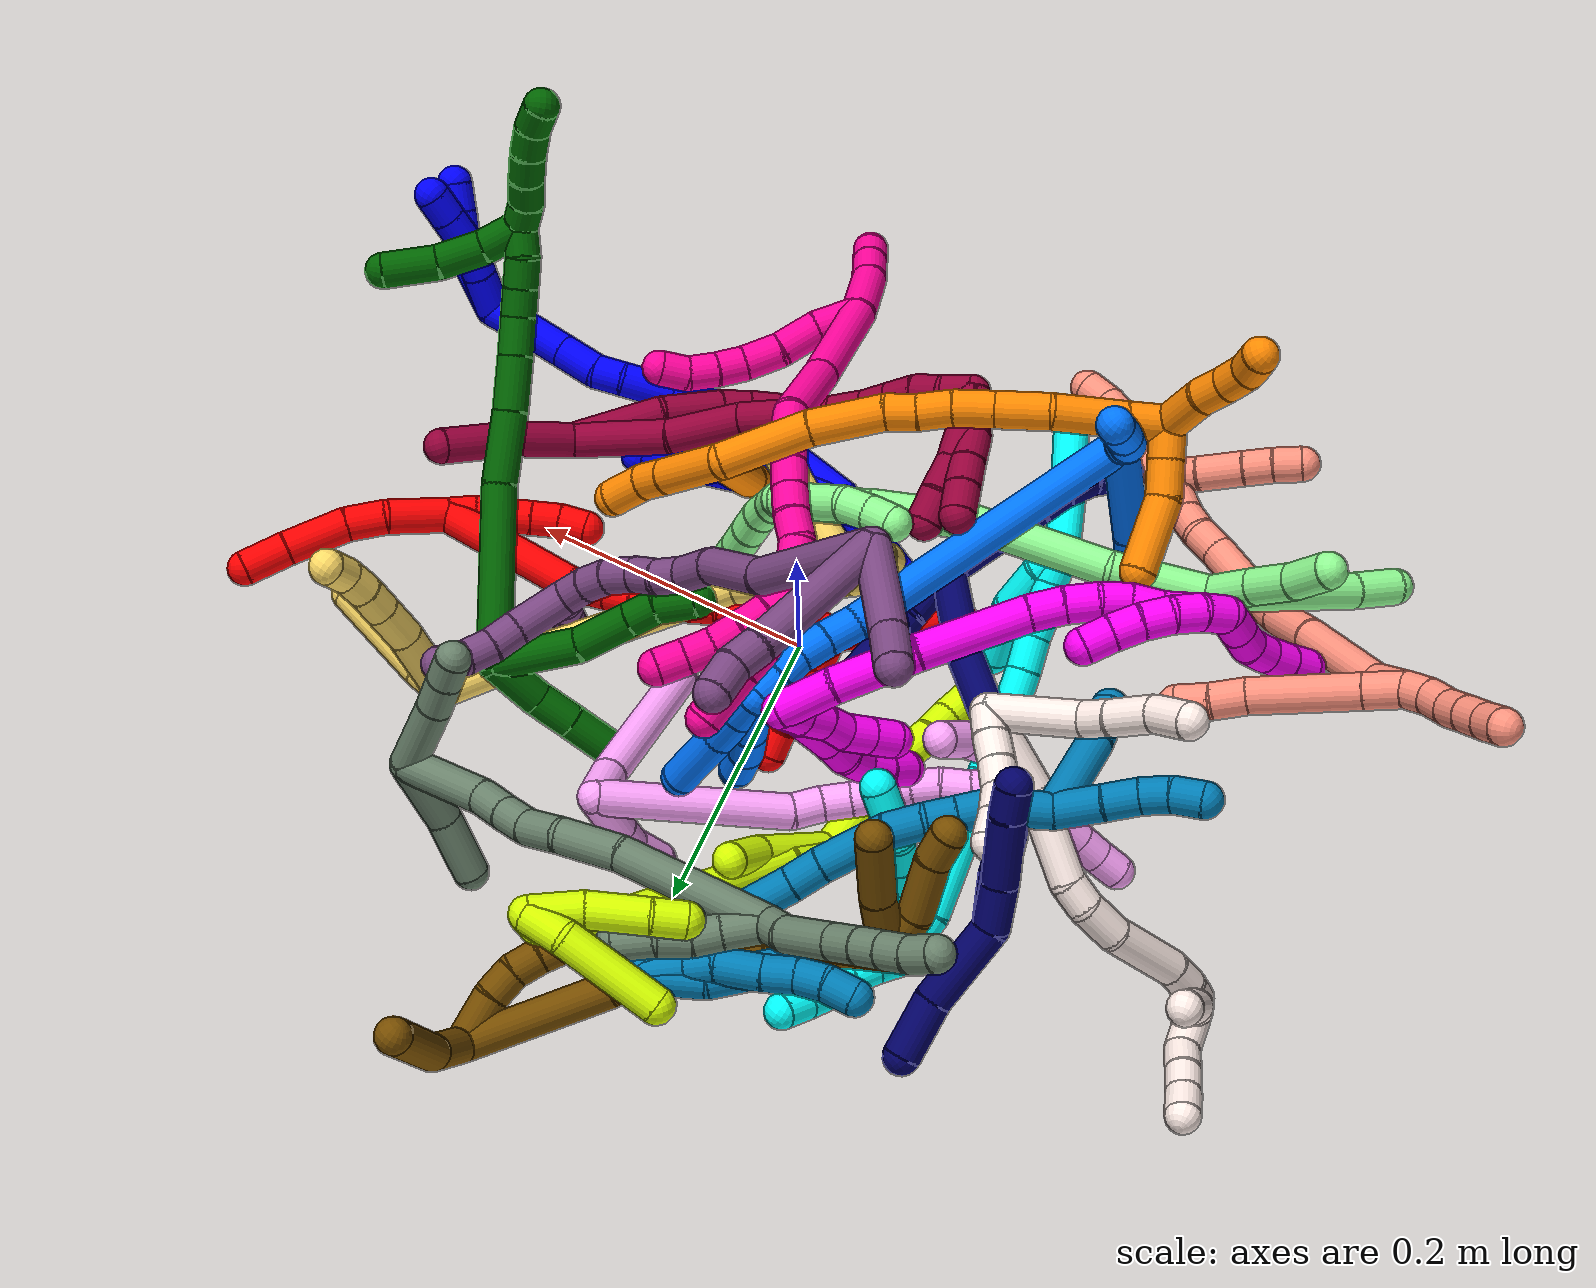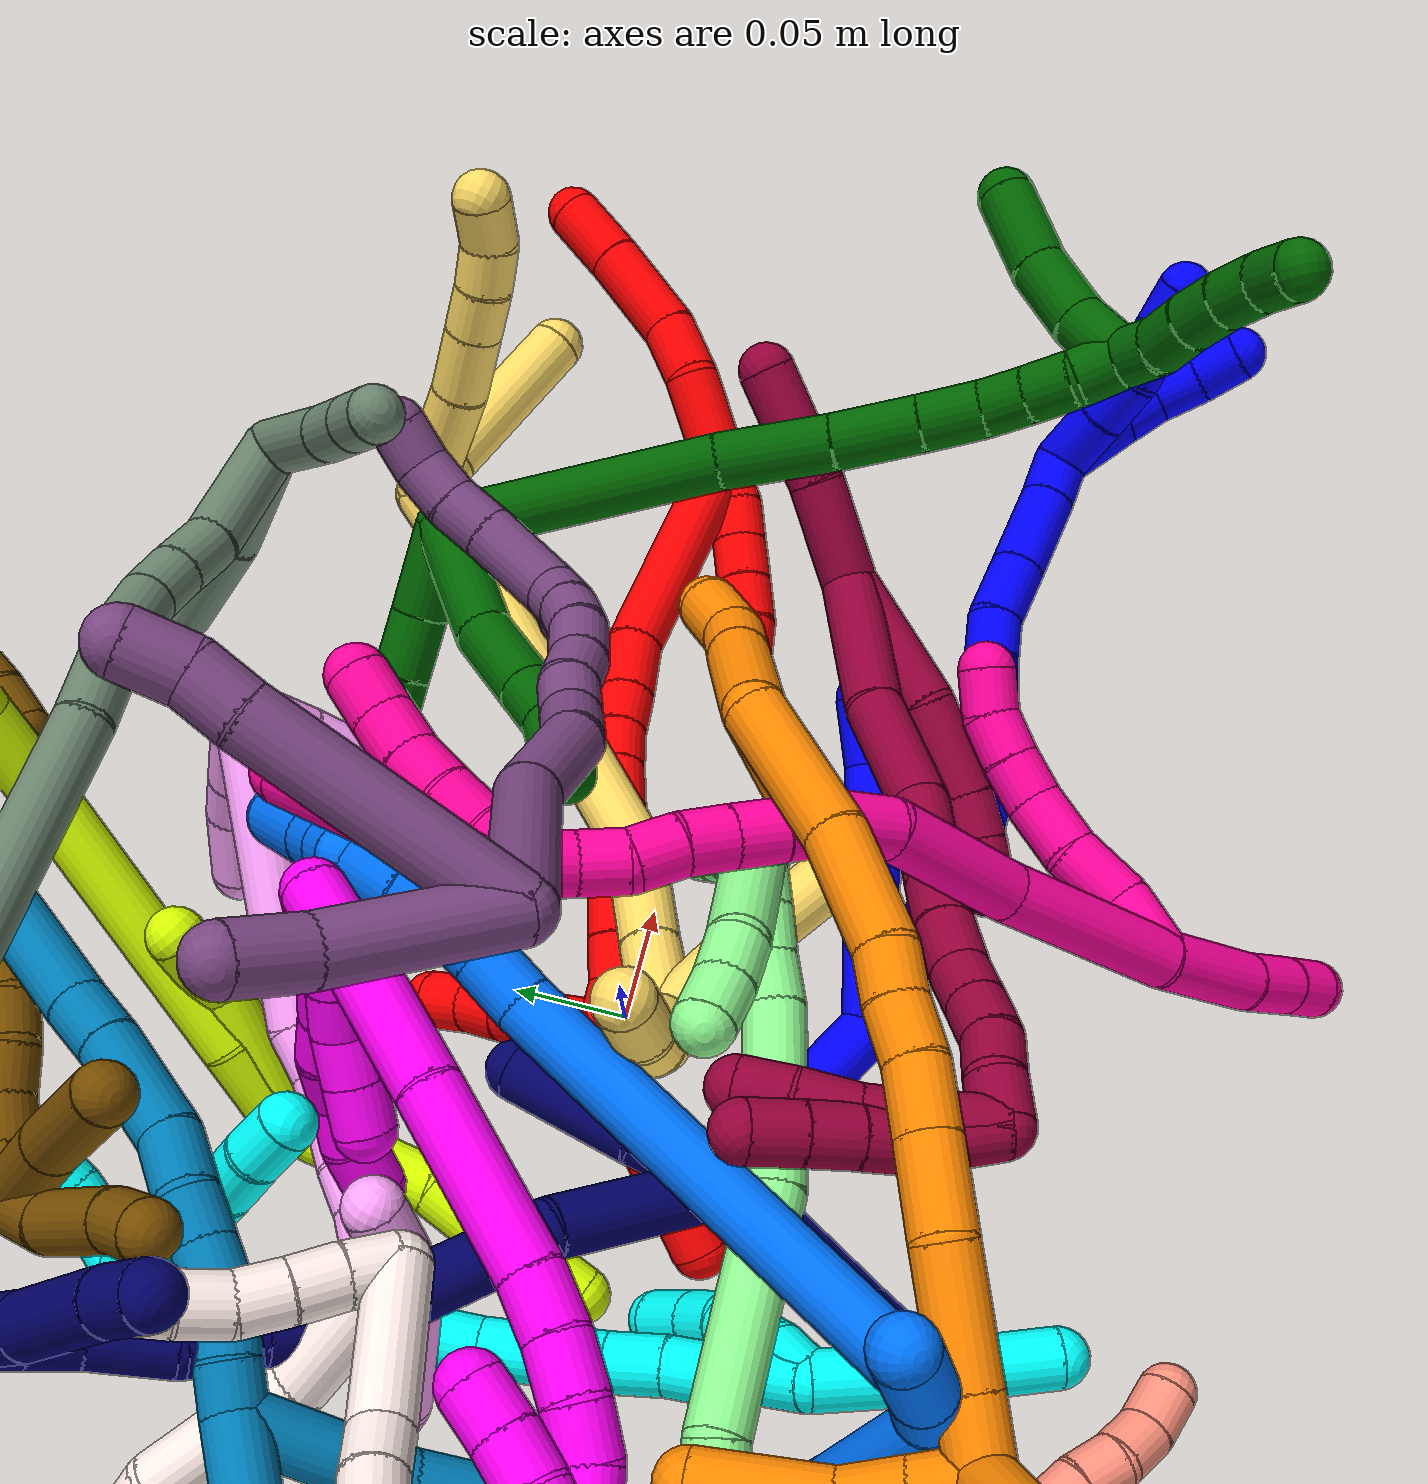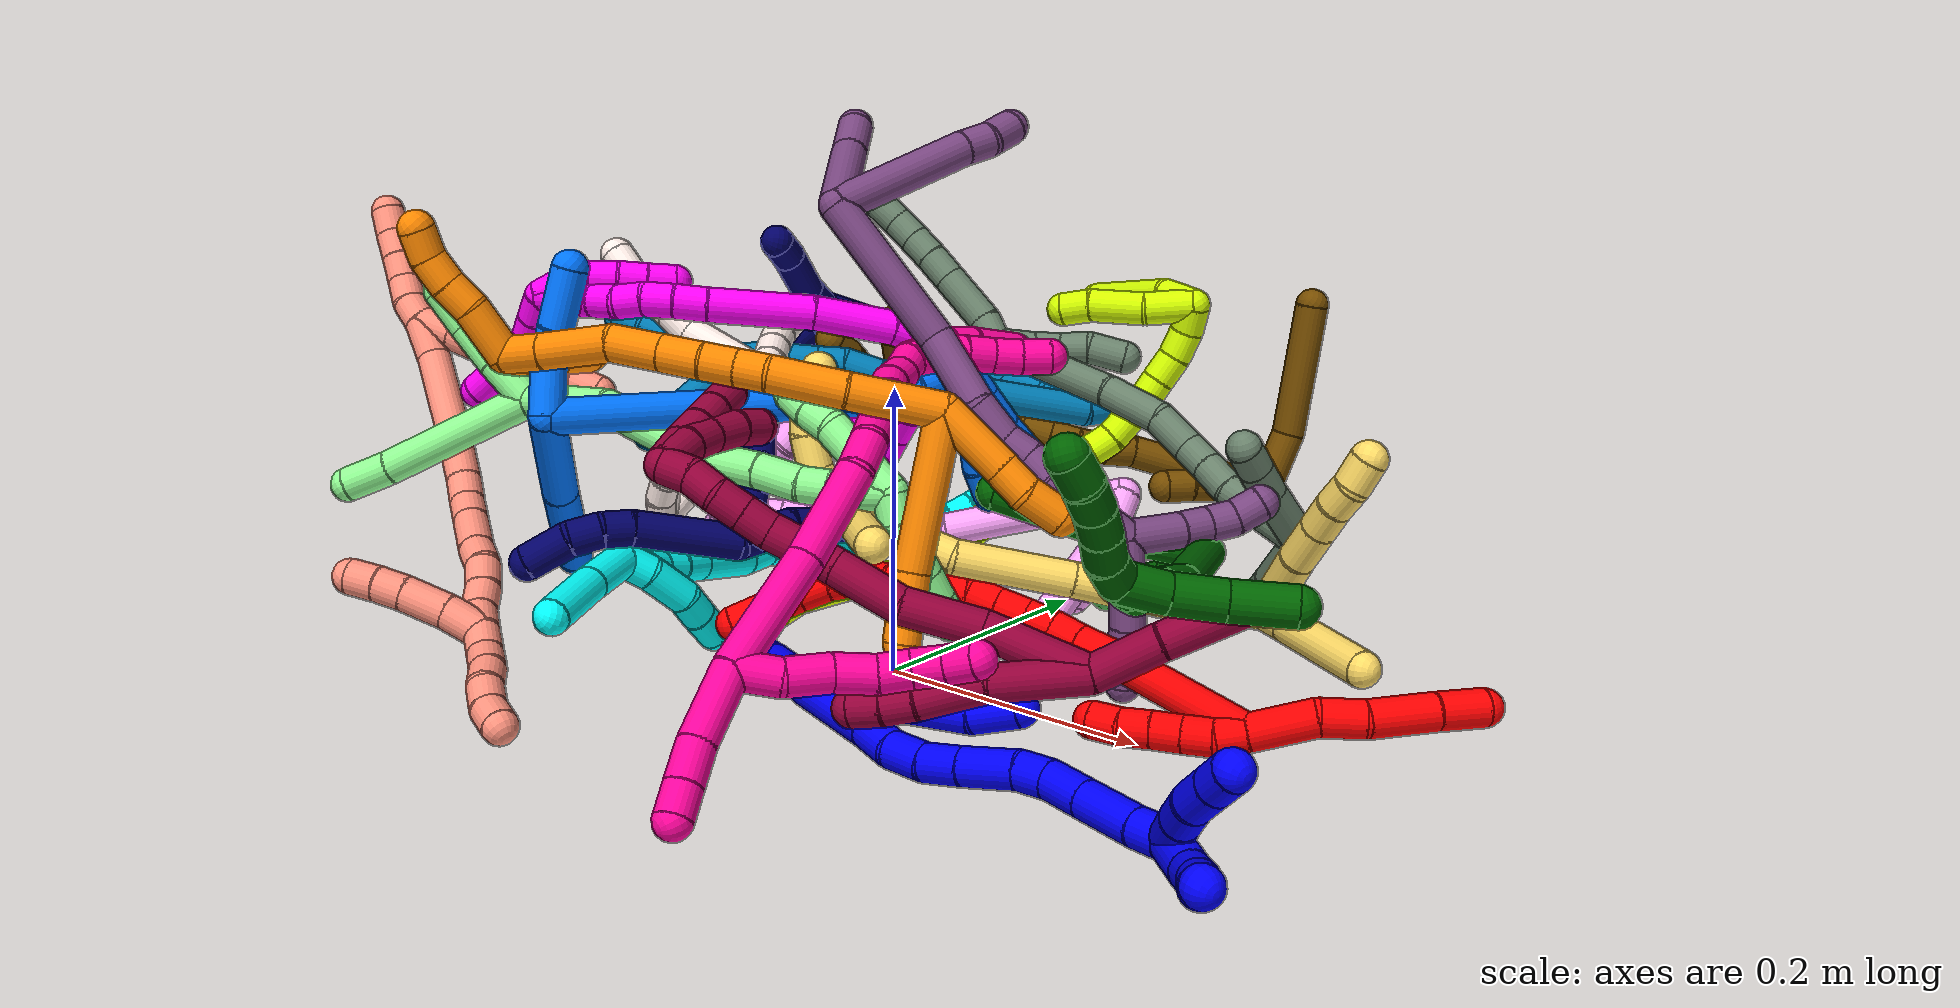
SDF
<sdf version="1.7">
 <world name="default">
  <plugin name="TubeGeneratorPlugin" filename="libtube_generator_plugin.so"/>
  <model name="photoneo_s_sensor">
   <static>1</static>
   <pose>0 0 2 1.57079 1.57079 3.14159</pose>
   <link name="link">
    <inertial><mass>0.1</mass></inertial>
    <sensor name="sensor" type="depth">
     <update_rate>30</update_rate>
     <camera>
      <horizontal_fov>1.22</horizontal_fov>
      <image><width>1920</width><height>1200</height><format>B8G8R8</format></image>
      <clip><near>0.1</near><far>4</far></clip>
      <depth_camera><output>points</output></depth_camera>
     </camera>
     <plugin name="camera_plugin" filename="libgazebo_ros_depth_camera.so">
      <baseline>0.2</baseline>
      <alwaysOn>1</alwaysOn>
      <updateRate>0.0</updateRate>
      <cameraName>camera_ir</cameraName>
      <imageTopicName>/camera/color/image_raw</imageTopicName>
      <cameraInfoTopicName>/camera/color/camera_info</cameraInfoTopicName>
      <depthImageTopicName>/camera/depth/image_raw</depthImageTopicName>
      <depthImageCameraInfoTopicName>/camera/depth/camera_info</depthImageCameraInfoTopicName>
      <pointCloudTopicName>/camera/depth/points</pointCloudTopicName>
      <frameName>fr_optical</frameName>
      <pointCloudCutoff>0.1</pointCloudCutoff>
      <pointCloudCutoffMax>2.0</pointCloudCutoffMax>
      <distortionK1>0</distortionK1>
      <distortionK2>0</distortionK2>
      <distortionK3>0</distortionK3>
      <distortionT1>0</distortionT1>
      <distortionT2>0</distortionT2>
      <CxPrime>0</CxPrime>
      <Cx>0</Cx>
      <Cy>0</Cy>
      <focalLength>0</focalLength>
      <hackBaseline>0</hackBaseline>
     </plugin>
    </sensor>
   </link>
  </model>
  <gravity>0 0 -9.8</gravity>
  <magnetic_field>6e-06 2.3e-05 -4.2e-05</magnetic_field>
  <atmosphere type="adiabatic"/>
  <physics name="default_physics" default="0" type="ode">
   <max_step_size>0.003</max_step_size>
   <real_time_factor>1</real_time_factor>
   <real_time_update_rate>1000</real_time_update_rate>
   <max_contacts>10000</max_contacts>
   <ode>
    <solver>
     <type>quick</type>
     <iters>100</iters>
     <sor>1.3</sor>
     <use_dynamic_moi_rescaling>0</use_dynamic_moi_rescaling>
    </solver>
    <constraints>
     <contact_max_correcting_vel>0</contact_max_correcting_vel>
     <contact_surface_layer>0.001</contact_surface_layer>
     <cfm>0</cfm>
     <erp>0.2</erp>
    </constraints>
   </ode>
  </physics>
  <scene><ambient>0.4 0.4 0.4 1</ambient><background>0.7 0.7 0.7 1</background><shadows>0</shadows></scene>
  <audio><device>default</device></audio>
  <spherical_coordinates>
   <surface_model>EARTH_WGS84</surface_model>
   <latitude_deg>0</latitude_deg>
   <longitude_deg>0</longitude_deg>
   <elevation>0</elevation>
   <heading_deg>0</heading_deg>
  </spherical_coordinates>
  <model name="bin">
   <static>1</static>
   <link name="bottom">
    <collision name="collision-bottom">
     <pose>0 0 -0.01 0 -0 0</pose>
     <geometry><box><size>0.8 0.6 0.02</size></box></geometry>
     <surface>
      <friction><ode><mu>100</mu><mu2>100</mu2></ode></friction>
      <contact><collide_bitmask>65535</collide_bitmask></contact>
     </surface>
    </collision>
   </link>
   <link name="west_wall">
    <collision name="collision-west_wall">
     <pose>-0.41 0 0.1 0 -0 0</pose>
     <geometry><box><size>0.02 0.6 0.2</size></box></geometry>
     <surface>
      <friction><ode><mu>100</mu><mu2>100</mu2></ode></friction>
      <contact><collide_bitmask>65535</collide_bitmask></contact>
     </surface>
    </collision>
   </link>
   <link name="east_wall">
    <collision name="collision-east_wall">
     <pose>0.41 0 0.1 0 -0 0</pose>
     <geometry><box><size>0.02 0.6 0.2</size></box></geometry>
     <surface>
      <friction><ode><mu>100</mu><mu2>100</mu2></ode></friction>
      <contact><collide_bitmask>65535</collide_bitmask></contact>
     </surface>
    </collision>
   </link>
   <link name="south_wall">
    <collision name="collision-south_wall">
     <pose>0 -0.31 0.1 0 -0 0</pose>
     <geometry><box><size>0.8 0.02 0.2</size></box></geometry>
     <surface>
      <friction><ode><mu>100</mu><mu2>100</mu2></ode></friction>
      <contact><collide_bitmask>65535</collide_bitmask></contact>
     </surface>
    </collision>
   </link>
   <link name="north_wall">
    <collision name="collision-north_wall">
     <pose>0 0.31 0.1 0 -0 0</pose>
     <geometry><box><size>0.8 0.02 0.2</size></box></geometry>
     <surface>
      <friction><ode><mu>100</mu><mu2>100</mu2></ode></friction>
      <contact><collide_bitmask>65535</collide_bitmask></contact>
     </surface>
    </collision>
   </link>
  </model>
  <model name="1">
   <static>0</static>
   <link name="1">
    <collision name="collision-cylinder-e_1_2_8">
     <pose>-0.008791 -0.025828 0.05237 0.458175 -0.149434 -0.034907</pose>
     <geometry><cylinder><radius>0.0125</radius><length>0.118102</length></cylinder></geometry>
     <surface>
      <friction><ode><mu>1.16</mu><mu2>1.16</mu2><slip1>0</slip1><slip2>0</slip2></ode></friction>
      <contact><ode><kp>1e+06</kp><kd>1</kd><max_vel>0</max_vel><min_depth>0.001</min_depth></ode></contact>
     </surface>
    </collision>
    <visual name="visual-cylinder-e_1_2_8">
     <pose>-0.008791 -0.025828 0.05237 0.458175 -0.149434 -0.034907</pose>
     <geometry><cylinder><radius>0.0125</radius><length>0.118102</length></cylinder></geometry>
     <material><ambient>0 0 1 1</ambient></material>
    </visual>
    <collision name="collision-cylinder-e_2_8_6">
     <pose>-0.017736 -0.062003 0.116877 0.706011 -0.009597 -0.003536</pose>
     <geometry><cylinder><radius>0.0125</radius><length>0.031898</length></cylinder></geometry>
     <surface>
      <friction><ode><mu>1.16</mu><mu2>1.16</mu2><slip1>0</slip1><slip2>0</slip2></ode></friction>
      <contact><ode><kp>1e+06</kp><kd>1</kd><max_vel>0</max_vel><min_depth>0.001</min_depth></ode></contact>
     </surface>
    </collision>
    <visual name="visual-cylinder-e_2_8_6">
     <pose>-0.017736 -0.062003 0.116877 0.706011 -0.009597 -0.003536</pose>
     <geometry><cylinder><radius>0.0125</radius><length>0.031898</length></cylinder></geometry>
     <material><ambient>0 0 1 1</ambient></material>
    </visual>
    <collision name="collision-cylinder-e_1_2_9">
     <pose>-0.005008 -0.002702 -0.016826 2.98236 -0.285837 -2.12909</pose>
     <geometry><cylinder><radius>0.0125</radius><length>0.035524</length></cylinder></geometry>
     <surface>
      <friction><ode><mu>1.16</mu><mu2>1.16</mu2><slip1>0</slip1><slip2>0</slip2></ode></friction>
      <contact><ode><kp>1e+06</kp><kd>1</kd><max_vel>0</max_vel><min_depth>0.001</min_depth></ode></contact>
     </surface>
    </collision>
    <visual name="visual-cylinder-e_1_2_9">
     <pose>-0.005008 -0.002702 -0.016826 2.98236 -0.285837 -2.12909</pose>
     <geometry><cylinder><radius>0.0125</radius><length>0.035524</length></cylinder></geometry>
     <material><ambient>0 0 1 1</ambient></material>
    </visual>
    <collision name="collision-cylinder-e_2_9_10">
     <pose>-0.014304 -0.00707 -0.049266 3.03532 -0.266575 -2.38634</pose>
     <geometry><cylinder><radius>0.0125</radius><length>0.032556</length></cylinder></geometry>
     <surface>
      <friction><ode><mu>1.16</mu><mu2>1.16</mu2><slip1>0</slip1><slip2>0</slip2></ode></friction>
      <contact><ode><kp>1e+06</kp><kd>1</kd><max_vel>0</max_vel><min_depth>0.001</min_depth></ode></contact>
     </surface>
    </collision>
    <visual name="visual-cylinder-e_2_9_10">
     <pose>-0.014304 -0.00707 -0.049266 3.03532 -0.266575 -2.38634</pose>
     <geometry><cylinder><radius>0.0125</radius><length>0.032556</length></cylinder></geometry>
     <material><ambient>0 0 1 1</ambient></material>
    </visual>
    <collision name="collision-cylinder-e_3_10_5">
     <pose>-0.024059 -0.010304 -0.079792 3.03676 -0.349612 -2.56407</pose>
     <geometry><cylinder><radius>0.0125</radius><length>0.03192</length></cylinder></geometry>
     <surface>
      <friction><ode><mu>1.16</mu><mu2>1.16</mu2><slip1>0</slip1><slip2>0</slip2></ode></friction>
      <contact><ode><kp>1e+06</kp><kd>1</kd><max_vel>0</max_vel><min_depth>0.001</min_depth></ode></contact>
     </surface>
    </collision>
    <visual name="visual-cylinder-e_3_10_5">
     <pose>-0.024059 -0.010304 -0.079792 3.03676 -0.349612 -2.56407</pose>
     <geometry><cylinder><radius>0.0125</radius><length>0.03192</length></cylinder></geometry>
     <material><ambient>0 0 1 1</ambient></material>
    </visual>
    <collision name="collision-cylinder-e_1_2_11">
     <pose>0.000211 0.000246 0.035094 -0.007007 0.006008 -2.1e-05</pose>
     <geometry><cylinder><radius>0.0125</radius><length>0.07019</length></cylinder></geometry>
     <surface>
      <friction><ode><mu>1.16</mu><mu2>1.16</mu2><slip1>0</slip1><slip2>0</slip2></ode></friction>
      <contact><ode><kp>1e+06</kp><kd>1</kd><max_vel>0</max_vel><min_depth>0.001</min_depth></ode></contact>
     </surface>
    </collision>
    <visual name="visual-cylinder-e_1_2_11">
     <pose>0.000211 0.000246 0.035094 -0.007007 0.006008 -2.1e-05</pose>
     <geometry><cylinder><radius>0.0125</radius><length>0.07019</length></cylinder></geometry>
     <material><ambient>0 0 1 1</ambient></material>
    </visual>
    <collision name="collision-cylinder-e_2_11_12">
     <pose>6e-06 0.00124 0.083705 -0.05529 -0.030679 0.000848</pose>
     <geometry><cylinder><radius>0.0125</radius><length>0.027091</length></cylinder></geometry>
     <surface>
      <friction><ode><mu>1.16</mu><mu2>1.16</mu2><slip1>0</slip1><slip2>0</slip2></ode></friction>
      <contact><ode><kp>1e+06</kp><kd>1</kd><max_vel>0</max_vel><min_depth>0.001</min_depth></ode></contact>
     </surface>
    </collision>
    <visual name="visual-cylinder-e_2_11_12">
     <pose>6e-06 0.00124 0.083705 -0.05529 -0.030679 0.000848</pose>
     <geometry><cylinder><radius>0.0125</radius><length>0.027091</length></cylinder></geometry>
     <material><ambient>0 0 1 1</ambient></material>
    </visual>
    <collision name="collision-cylinder-e_3_12_13">
     <pose>-0.001552 -0.000825 0.110017 0.216466 -0.086996 -0.009459</pose>
     <geometry><cylinder><radius>0.0125</radius><length>0.026298</length></cylinder></geometry>
     <surface>
      <friction><ode><mu>1.16</mu><mu2>1.16</mu2><slip1>0</slip1><slip2>0</slip2></ode></friction>
      <contact><ode><kp>1e+06</kp><kd>1</kd><max_vel>0</max_vel><min_depth>0.001</min_depth></ode></contact>
     </surface>
    </collision>
    <visual name="visual-cylinder-e_3_12_13">
     <pose>-0.001552 -0.000825 0.110017 0.216466 -0.086996 -0.009459</pose>
     <geometry><cylinder><radius>0.0125</radius><length>0.026298</length></cylinder></geometry>
     <material><ambient>0 0 1 1</ambient></material>
    </visual>
    <collision name="collision-cylinder-e_4_13_14">
     <pose>-0.003024 -0.009472 0.134941 0.448256 -0.02448 -0.005581</pose>
     <geometry><cylinder><radius>0.0125</radius><length>0.026927</length></cylinder></geometry>
     <surface>
      <friction><ode><mu>1.16</mu><mu2>1.16</mu2><slip1>0</slip1><slip2>0</slip2></ode></friction>
      <contact><ode><kp>1e+06</kp><kd>1</kd><max_vel>0</max_vel><min_depth>0.001</min_depth></ode></contact>
     </surface>
    </collision>
    <visual name="visual-cylinder-e_4_13_14">
     <pose>-0.003024 -0.009472 0.134941 0.448256 -0.02448 -0.005581</pose>
     <geometry><cylinder><radius>0.0125</radius><length>0.026927</length></cylinder></geometry>
     <material><ambient>0 0 1 1</ambient></material>
    </visual>
    <collision name="collision-cylinder-e_5_14_15">
     <pose>-0.003969 -0.024215 0.163365 0.500378 -0.033126 -0.008466</pose>
     <geometry><cylinder><radius>0.0125</radius><length>0.037164</length></cylinder></geometry>
     <surface>
      <friction><ode><mu>1.16</mu><mu2>1.16</mu2><slip1>0</slip1><slip2>0</slip2></ode></friction>
      <contact><ode><kp>1e+06</kp><kd>1</kd><max_vel>0</max_vel><min_depth>0.001</min_depth></ode></contact>
     </surface>
    </collision>
    <visual name="visual-cylinder-e_5_14_15">
     <pose>-0.003969 -0.024215 0.163365 0.500378 -0.033126 -0.008466</pose>
     <geometry><cylinder><radius>0.0125</radius><length>0.037164</length></cylinder></geometry>
     <material><ambient>0 0 1 1</ambient></material>
    </visual>
    <collision name="collision-cylinder-e_6_15_16">
     <pose>-0.006346 -0.036482 0.189204 0.338189 -0.172403 -0.029504</pose>
     <geometry><cylinder><radius>0.0125</radius><length>0.020539</length></cylinder></geometry>
     <surface>
      <friction><ode><mu>1.16</mu><mu2>1.16</mu2><slip1>0</slip1><slip2>0</slip2></ode></friction>
      <contact><ode><kp>1e+06</kp><kd>1</kd><max_vel>0</max_vel><min_depth>0.001</min_depth></ode></contact>
     </surface>
    </collision>
    <visual name="visual-cylinder-e_6_15_16">
     <pose>-0.006346 -0.036482 0.189204 0.338189 -0.172403 -0.029504</pose>
     <geometry><cylinder><radius>0.0125</radius><length>0.020539</length></cylinder></geometry>
     <material><ambient>0 0 1 1</ambient></material>
    </visual>
    <collision name="collision-cylinder-e_7_16_17">
     <pose>-0.008797 -0.040897 0.213378 0.072219 -0.046934 -0.001696</pose>
     <geometry><cylinder><radius>0.0125</radius><length>0.029367</length></cylinder></geometry>
     <surface>
      <friction><ode><mu>1.16</mu><mu2>1.16</mu2><slip1>0</slip1><slip2>0</slip2></ode></friction>
      <contact><ode><kp>1e+06</kp><kd>1</kd><max_vel>0</max_vel><min_depth>0.001</min_depth></ode></contact>
     </surface>
    </collision>
    <visual name="visual-cylinder-e_7_16_17">
     <pose>-0.008797 -0.040897 0.213378 0.072219 -0.046934 -0.001696</pose>
     <geometry><cylinder><radius>0.0125</radius><length>0.029367</length></cylinder></geometry>
     <material><ambient>0 0 1 1</ambient></material>
    </visual>
    <collision name="collision-cylinder-e_8_17_18">
     <pose>-0.010405 -0.043526 0.247854 0.078953 -0.046175 -0.001824</pose>
     <geometry><cylinder><radius>0.0125</radius><length>0.039861</length></cylinder></geometry>
     <surface>
      <friction><ode><mu>1.16</mu><mu2>1.16</mu2><slip1>0</slip1><slip2>0</slip2></ode></friction>
      <contact><ode><kp>1e+06</kp><kd>1</kd><max_vel>0</max_vel><min_depth>0.001</min_depth></ode></contact>
     </surface>
    </collision>
    <visual name="visual-cylinder-e_8_17_18">
     <pose>-0.010405 -0.043526 0.247854 0.078953 -0.046175 -0.001824</pose>
     <geometry><cylinder><radius>0.0125</radius><length>0.039861</length></cylinder></geometry>
     <material><ambient>0 0 1 1</ambient></material>
    </visual>
    <collision name="collision-cylinder-e_9_18_1">
     <pose>-0.011648 -0.046852 0.278841 0.156381 -0.028635 -0.002244</pose>
     <geometry><cylinder><radius>0.0125</radius><length>0.022563</length></cylinder></geometry>
     <surface>
      <friction><ode><mu>1.16</mu><mu2>1.16</mu2><slip1>0</slip1><slip2>0</slip2></ode></friction>
      <contact><ode><kp>1e+06</kp><kd>1</kd><max_vel>0</max_vel><min_depth>0.001</min_depth></ode></contact>
     </surface>
    </collision>
    <visual name="visual-cylinder-e_9_18_1">
     <pose>-0.011648 -0.046852 0.278841 0.156381 -0.028635 -0.002244</pose>
     <geometry><cylinder><radius>0.0125</radius><length>0.022563</length></cylinder></geometry>
     <material><ambient>0 0 1 1</ambient></material>
    </visual>
    <collision name="collision-cylinder-e_1_1_19">
     <pose>-0.007431 -0.042733 0.306326 -0.345022 0.255694 -0.04479</pose>
     <geometry><cylinder><radius>0.0125</radius><length>0.035908</length></cylinder></geometry>
     <surface>
      <friction><ode><mu>1.16</mu><mu2>1.16</mu2><slip1>0</slip1><slip2>0</slip2></ode></friction>
      <contact><ode><kp>1e+06</kp><kd>1</kd><max_vel>0</max_vel><min_depth>0.001</min_depth></ode></contact>
     </surface>
    </collision>
    <visual name="visual-cylinder-e_1_1_19">
     <pose>-0.007431 -0.042733 0.306326 -0.345022 0.255694 -0.04479</pose>
     <geometry><cylinder><radius>0.0125</radius><length>0.035908</length></cylinder></geometry>
     <material><ambient>0 0 1 1</ambient></material>
    </visual>
    <collision name="collision-cylinder-e_2_19_20">
     <pose>0.002067 -0.034008 0.330966 -0.331046 0.514434 -0.087827</pose>
     <geometry><cylinder><radius>0.0125</radius><length>0.020147</length></cylinder></geometry>
     <surface>
      <friction><ode><mu>1.16</mu><mu2>1.16</mu2><slip1>0</slip1><slip2>0</slip2></ode></friction>
      <contact><ode><kp>1e+06</kp><kd>1</kd><max_vel>0</max_vel><min_depth>0.001</min_depth></ode></contact>
     </surface>
    </collision>
    <visual name="visual-cylinder-e_2_19_20">
     <pose>0.002067 -0.034008 0.330966 -0.331046 0.514434 -0.087827</pose>
     <geometry><cylinder><radius>0.0125</radius><length>0.020147</length></cylinder></geometry>
     <material><ambient>0 0 1 1</ambient></material>
    </visual>
    <collision name="collision-cylinder-e_3_20_21">
     <pose>0.01406 -0.027057 0.346846 -0.495627 0.684413 -0.179772</pose>
     <geometry><cylinder><radius>0.0125</radius><length>0.02226</length></cylinder></geometry>
     <surface>
      <friction><ode><mu>1.16</mu><mu2>1.16</mu2><slip1>0</slip1><slip2>0</slip2></ode></friction>
      <contact><ode><kp>1e+06</kp><kd>1</kd><max_vel>0</max_vel><min_depth>0.001</min_depth></ode></contact>
     </surface>
    </collision>
    <visual name="visual-cylinder-e_3_20_21">
     <pose>0.01406 -0.027057 0.346846 -0.495627 0.684413 -0.179772</pose>
     <geometry><cylinder><radius>0.0125</radius><length>0.02226</length></cylinder></geometry>
     <material><ambient>0 0 1 1</ambient></material>
    </visual>
    <collision name="collision-cylinder-e_4_21_4">
     <pose>0.029175 -0.020322 0.361167 -0.372692 0.840614 -0.168129</pose>
     <geometry><cylinder><radius>0.0125</radius><length>0.021685</length></cylinder></geometry>
     <surface>
      <friction><ode><mu>1.16</mu><mu2>1.16</mu2><slip1>0</slip1><slip2>0</slip2></ode></friction>
      <contact><ode><kp>1e+06</kp><kd>1</kd><max_vel>0</max_vel><min_depth>0.001</min_depth></ode></contact>
     </surface>
    </collision>
    <visual name="visual-cylinder-e_4_21_4">
     <pose>0.029175 -0.020322 0.361167 -0.372692 0.840614 -0.168129</pose>
     <geometry><cylinder><radius>0.0125</radius><length>0.021685</length></cylinder></geometry>
     <material><ambient>0 0 1 1</ambient></material>
    </visual>
    <collision name="collision-cylinder-e_1_1_22">
     <pose>0.000334 -0.050775 0.298143 0.259411 0.969299 0.137145</pose>
     <geometry><cylinder><radius>0.0125</radius><length>0.02985</length></cylinder></geometry>
     <surface>
      <friction><ode><mu>1.16</mu><mu2>1.16</mu2><slip1>0</slip1><slip2>0</slip2></ode></friction>
      <contact><ode><kp>1e+06</kp><kd>1</kd><max_vel>0</max_vel><min_depth>0.001</min_depth></ode></contact>
     </surface>
    </collision>
    <visual name="visual-cylinder-e_1_1_22">
     <pose>0.000334 -0.050775 0.298143 0.259411 0.969299 0.137145</pose>
     <geometry><cylinder><radius>0.0125</radius><length>0.02985</length></cylinder></geometry>
     <material><ambient>0 0 1 1</ambient></material>
    </visual>
    <collision name="collision-cylinder-e_2_22_23">
     <pose>0.022241 -0.054796 0.313221 0.26203 0.930125 0.132044</pose>
     <geometry><cylinder><radius>0.0125</radius><length>0.023952</length></cylinder></geometry>
     <surface>
      <friction><ode><mu>1.16</mu><mu2>1.16</mu2><slip1>0</slip1><slip2>0</slip2></ode></friction>
      <contact><ode><kp>1e+06</kp><kd>1</kd><max_vel>0</max_vel><min_depth>0.001</min_depth></ode></contact>
     </surface>
    </collision>
    <visual name="visual-cylinder-e_2_22_23">
     <pose>0.022241 -0.054796 0.313221 0.26203 0.930125 0.132044</pose>
     <geometry><cylinder><radius>0.0125</radius><length>0.023952</length></cylinder></geometry>
     <material><ambient>0 0 1 1</ambient></material>
    </visual>
    <collision name="collision-cylinder-e_3_23_24">
     <pose>0.040711 -0.060439 0.32867 0.417838 0.759606 0.168862</pose>
     <geometry><cylinder><radius>0.0125</radius><length>0.025757</length></cylinder></geometry>
     <surface>
      <friction><ode><mu>1.16</mu><mu2>1.16</mu2><slip1>0</slip1><slip2>0</slip2></ode></friction>
      <contact><ode><kp>1e+06</kp><kd>1</kd><max_vel>0</max_vel><min_depth>0.001</min_depth></ode></contact>
     </surface>
    </collision>
    <visual name="visual-cylinder-e_3_23_24">
     <pose>0.040711 -0.060439 0.32867 0.417838 0.759606 0.168862</pose>
     <geometry><cylinder><radius>0.0125</radius><length>0.025757</length></cylinder></geometry>
     <material><ambient>0 0 1 1</ambient></material>
    </visual>
    <collision name="collision-cylinder-e_4_24_3">
     <pose>0.05659 -0.067202 0.344021 0.411286 0.755923 0.165266</pose>
     <geometry><cylinder><radius>0.0125</radius><length>0.020441</length></cylinder></geometry>
     <surface>
      <friction><ode><mu>1.16</mu><mu2>1.16</mu2><slip1>0</slip1><slip2>0</slip2></ode></friction>
      <contact><ode><kp>1e+06</kp><kd>1</kd><max_vel>0</max_vel><min_depth>0.001</min_depth></ode></contact>
     </surface>
    </collision>
    <visual name="visual-cylinder-e_4_24_3">
     <pose>0.05659 -0.067202 0.344021 0.411286 0.755923 0.165266</pose>
     <geometry><cylinder><radius>0.0125</radius><length>0.020441</length></cylinder></geometry>
     <material><ambient>0 0 1 1</ambient></material>
    </visual>
    <collision name="collision-sphere-3">
     <pose>0.063601 -0.070175 0.350838 0 -0 0</pose>
     <geometry><sphere><radius>0.0125</radius></sphere></geometry>
     <surface>
      <friction><ode><mu>1.16</mu><mu2>1.16</mu2><slip1>0</slip1><slip2>0</slip2></ode></friction>
      <contact><ode><kp>1e+06</kp><kd>1</kd><max_vel>0</max_vel><min_depth>0.001</min_depth></ode></contact>
     </surface>
    </collision>
    <visual name="visual-sphere-3">
     <pose>0.063601 -0.070175 0.350838 0 -0 0</pose>
     <geometry><sphere><radius>0.0125</radius></sphere></geometry>
     <material><ambient>0 0 1 1</ambient></material>
    </visual>
    <collision name="collision-sphere-24">
     <pose>0.049579 -0.064229 0.337204 0 -0 0</pose>
     <geometry><sphere><radius>0.0125</radius></sphere></geometry>
     <surface>
      <friction><ode><mu>1.16</mu><mu2>1.16</mu2><slip1>0</slip1><slip2>0</slip2></ode></friction>
      <contact><ode><kp>1e+06</kp><kd>1</kd><max_vel>0</max_vel><min_depth>0.001</min_depth></ode></contact>
     </surface>
    </collision>
    <visual name="visual-sphere-24">
     <pose>0.049579 -0.064229 0.337204 0 -0 0</pose>
     <geometry><sphere><radius>0.0125</radius></sphere></geometry>
     <material><ambient>0 0 1 1</ambient></material>
    </visual>
    <collision name="collision-sphere-23">
     <pose>0.031842 -0.05665 0.320135 0 -0 0</pose>
     <geometry><sphere><radius>0.0125</radius></sphere></geometry>
     <surface>
      <friction><ode><mu>1.16</mu><mu2>1.16</mu2><slip1>0</slip1><slip2>0</slip2></ode></friction>
      <contact><ode><kp>1e+06</kp><kd>1</kd><max_vel>0</max_vel><min_depth>0.001</min_depth></ode></contact>
     </surface>
    </collision>
    <visual name="visual-sphere-23">
     <pose>0.031842 -0.05665 0.320135 0 -0 0</pose>
     <geometry><sphere><radius>0.0125</radius></sphere></geometry>
     <material><ambient>0 0 1 1</ambient></material>
    </visual>
    <collision name="collision-sphere-22">
     <pose>0.01264 -0.052941 0.306306 0 -0 0</pose>
     <geometry><sphere><radius>0.0125</radius></sphere></geometry>
     <surface>
      <friction><ode><mu>1.16</mu><mu2>1.16</mu2><slip1>0</slip1><slip2>0</slip2></ode></friction>
      <contact><ode><kp>1e+06</kp><kd>1</kd><max_vel>0</max_vel><min_depth>0.001</min_depth></ode></contact>
     </surface>
    </collision>
    <visual name="visual-sphere-22">
     <pose>0.01264 -0.052941 0.306306 0 -0 0</pose>
     <geometry><sphere><radius>0.0125</radius></sphere></geometry>
     <material><ambient>0 0 1 1</ambient></material>
    </visual>
    <collision name="collision-sphere-4">
     <pose>0.037253 -0.017689 0.367903 0 -0 0</pose>
     <geometry><sphere><radius>0.0125</radius></sphere></geometry>
     <surface>
      <friction><ode><mu>1.16</mu><mu2>1.16</mu2><slip1>0</slip1><slip2>0</slip2></ode></friction>
      <contact><ode><kp>1e+06</kp><kd>1</kd><max_vel>0</max_vel><min_depth>0.001</min_depth></ode></contact>
     </surface>
    </collision>
    <visual name="visual-sphere-4">
     <pose>0.037253 -0.017689 0.367903 0 -0 0</pose>
     <geometry><sphere><radius>0.0125</radius></sphere></geometry>
     <material><ambient>0 0 1 1</ambient></material>
    </visual>
    <collision name="collision-sphere-21">
     <pose>0.021097 -0.022955 0.354431 0 -0 0</pose>
     <geometry><sphere><radius>0.0125</radius></sphere></geometry>
     <surface>
      <friction><ode><mu>1.16</mu><mu2>1.16</mu2><slip1>0</slip1><slip2>0</slip2></ode></friction>
      <contact><ode><kp>1e+06</kp><kd>1</kd><max_vel>0</max_vel><min_depth>0.001</min_depth></ode></contact>
     </surface>
    </collision>
    <visual name="visual-sphere-21">
     <pose>0.021097 -0.022955 0.354431 0 -0 0</pose>
     <geometry><sphere><radius>0.0125</radius></sphere></geometry>
     <material><ambient>0 0 1 1</ambient></material>
    </visual>
    <collision name="collision-sphere-20">
     <pose>0.007023 -0.031158 0.33926 0 -0 0</pose>
     <geometry><sphere><radius>0.0125</radius></sphere></geometry>
     <surface>
      <friction><ode><mu>1.16</mu><mu2>1.16</mu2><slip1>0</slip1><slip2>0</slip2></ode></friction>
      <contact><ode><kp>1e+06</kp><kd>1</kd><max_vel>0</max_vel><min_depth>0.001</min_depth></ode></contact>
     </surface>
    </collision>
    <visual name="visual-sphere-20">
     <pose>0.007023 -0.031158 0.33926 0 -0 0</pose>
     <geometry><sphere><radius>0.0125</radius></sphere></geometry>
     <material><ambient>0 0 1 1</ambient></material>
    </visual>
    <collision name="collision-sphere-5">
     <pose>-0.029526 -0.011873 -0.094705 0 -0 0</pose>
     <geometry><sphere><radius>0.0125</radius></sphere></geometry>
     <surface>
      <friction><ode><mu>1.16</mu><mu2>1.16</mu2><slip1>0</slip1><slip2>0</slip2></ode></friction>
      <contact><ode><kp>1e+06</kp><kd>1</kd><max_vel>0</max_vel><min_depth>0.001</min_depth></ode></contact>
     </surface>
    </collision>
    <visual name="visual-sphere-5">
     <pose>-0.029526 -0.011873 -0.094705 0 -0 0</pose>
     <geometry><sphere><radius>0.0125</radius></sphere></geometry>
     <material><ambient>0 0 1 1</ambient></material>
    </visual>
    <collision name="collision-sphere-10">
     <pose>-0.018592 -0.008735 -0.06488 0 -0 0</pose>
     <geometry><sphere><radius>0.0125</radius></sphere></geometry>
     <surface>
      <friction><ode><mu>1.16</mu><mu2>1.16</mu2><slip1>0</slip1><slip2>0</slip2></ode></friction>
      <contact><ode><kp>1e+06</kp><kd>1</kd><max_vel>0</max_vel><min_depth>0.001</min_depth></ode></contact>
     </surface>
    </collision>
    <visual name="visual-sphere-10">
     <pose>-0.018592 -0.008735 -0.06488 0 -0 0</pose>
     <geometry><sphere><radius>0.0125</radius></sphere></geometry>
     <material><ambient>0 0 1 1</ambient></material>
    </visual>
    <collision name="collision-sphere-6">
     <pose>-0.017889 -0.07235 0.129013 0 -0 0</pose>
     <geometry><sphere><radius>0.0125</radius></sphere></geometry>
     <surface>
      <friction><ode><mu>1.16</mu><mu2>1.16</mu2><slip1>0</slip1><slip2>0</slip2></ode></friction>
      <contact><ode><kp>1e+06</kp><kd>1</kd><max_vel>0</max_vel><min_depth>0.001</min_depth></ode></contact>
     </surface>
    </collision>
    <visual name="visual-sphere-6">
     <pose>-0.017889 -0.07235 0.129013 0 -0 0</pose>
     <geometry><sphere><radius>0.0125</radius></sphere></geometry>
     <material><ambient>0 0 1 1</ambient></material>
    </visual>
    <collision name="collision-sphere-9">
     <pose>-0.010016 -0.005404 -0.033651 0 -0 0</pose>
     <geometry><sphere><radius>0.0125</radius></sphere></geometry>
     <surface>
      <friction><ode><mu>1.16</mu><mu2>1.16</mu2><slip1>0</slip1><slip2>0</slip2></ode></friction>
      <contact><ode><kp>1e+06</kp><kd>1</kd><max_vel>0</max_vel><min_depth>0.001</min_depth></ode></contact>
     </surface>
    </collision>
    <visual name="visual-sphere-9">
     <pose>-0.010016 -0.005404 -0.033651 0 -0 0</pose>
     <geometry><sphere><radius>0.0125</radius></sphere></geometry>
     <material><ambient>0 0 1 1</ambient></material>
    </visual>
    <collision name="collision-sphere-2">
     <geometry><sphere><radius>0.0125</radius></sphere></geometry>
     <surface>
      <friction><ode><mu>1.16</mu><mu2>1.16</mu2><slip1>0</slip1><slip2>0</slip2></ode></friction>
      <contact><ode><kp>1e+06</kp><kd>1</kd><max_vel>0</max_vel><min_depth>0.001</min_depth></ode></contact>
     </surface>
    </collision>
    <visual name="visual-sphere-2">
     <geometry><sphere><radius>0.0125</radius></sphere></geometry>
     <material><ambient>0 0 1 1</ambient></material>
    </visual>
    <collision name="collision-sphere-19">
     <pose>-0.00289 -0.036859 0.322673 0 -0 0</pose>
     <geometry><sphere><radius>0.0125</radius></sphere></geometry>
     <surface>
      <friction><ode><mu>1.16</mu><mu2>1.16</mu2><slip1>0</slip1><slip2>0</slip2></ode></friction>
      <contact><ode><kp>1e+06</kp><kd>1</kd><max_vel>0</max_vel><min_depth>0.001</min_depth></ode></contact>
     </surface>
    </collision>
    <visual name="visual-sphere-19">
     <pose>-0.00289 -0.036859 0.322673 0 -0 0</pose>
     <geometry><sphere><radius>0.0125</radius></sphere></geometry>
     <material><ambient>0 0 1 1</ambient></material>
    </visual>
    <collision name="collision-sphere-8">
     <pose>-0.017583 -0.051656 0.104741 0 -0 0</pose>
     <geometry><sphere><radius>0.0125</radius></sphere></geometry>
     <surface>
      <friction><ode><mu>1.16</mu><mu2>1.16</mu2><slip1>0</slip1><slip2>0</slip2></ode></friction>
      <contact><ode><kp>1e+06</kp><kd>1</kd><max_vel>0</max_vel><min_depth>0.001</min_depth></ode></contact>
     </surface>
    </collision>
    <visual name="visual-sphere-8">
     <pose>-0.017583 -0.051656 0.104741 0 -0 0</pose>
     <geometry><sphere><radius>0.0125</radius></sphere></geometry>
     <material><ambient>0 0 1 1</ambient></material>
    </visual>
    <collision name="collision-sphere-11">
     <pose>0.000422 0.000492 0.070187 0 -0 0</pose>
     <geometry><sphere><radius>0.0125</radius></sphere></geometry>
     <surface>
      <friction><ode><mu>1.16</mu><mu2>1.16</mu2><slip1>0</slip1><slip2>0</slip2></ode></friction>
      <contact><ode><kp>1e+06</kp><kd>1</kd><max_vel>0</max_vel><min_depth>0.001</min_depth></ode></contact>
     </surface>
    </collision>
    <visual name="visual-sphere-11">
     <pose>0.000422 0.000492 0.070187 0 -0 0</pose>
     <geometry><sphere><radius>0.0125</radius></sphere></geometry>
     <material><ambient>0 0 1 1</ambient></material>
    </visual>
    <collision name="collision-sphere-12">
     <pose>-0.000409 0.001988 0.097224 0 -0 0</pose>
     <geometry><sphere><radius>0.0125</radius></sphere></geometry>
     <surface>
      <friction><ode><mu>1.16</mu><mu2>1.16</mu2><slip1>0</slip1><slip2>0</slip2></ode></friction>
      <contact><ode><kp>1e+06</kp><kd>1</kd><max_vel>0</max_vel><min_depth>0.001</min_depth></ode></contact>
     </surface>
    </collision>
    <visual name="visual-sphere-12">
     <pose>-0.000409 0.001988 0.097224 0 -0 0</pose>
     <geometry><sphere><radius>0.0125</radius></sphere></geometry>
     <material><ambient>0 0 1 1</ambient></material>
    </visual>
    <collision name="collision-sphere-13">
     <pose>-0.002694 -0.003639 0.122811 0 -0 0</pose>
     <geometry><sphere><radius>0.0125</radius></sphere></geometry>
     <surface>
      <friction><ode><mu>1.16</mu><mu2>1.16</mu2><slip1>0</slip1><slip2>0</slip2></ode></friction>
      <contact><ode><kp>1e+06</kp><kd>1</kd><max_vel>0</max_vel><min_depth>0.001</min_depth></ode></contact>
     </surface>
    </collision>
    <visual name="visual-sphere-13">
     <pose>-0.002694 -0.003639 0.122811 0 -0 0</pose>
     <geometry><sphere><radius>0.0125</radius></sphere></geometry>
     <material><ambient>0 0 1 1</ambient></material>
    </visual>
    <collision name="collision-sphere-14">
     <pose>-0.003353 -0.015305 0.14707 0 -0 0</pose>
     <geometry><sphere><radius>0.0125</radius></sphere></geometry>
     <surface>
      <friction><ode><mu>1.16</mu><mu2>1.16</mu2><slip1>0</slip1><slip2>0</slip2></ode></friction>
      <contact><ode><kp>1e+06</kp><kd>1</kd><max_vel>0</max_vel><min_depth>0.001</min_depth></ode></contact>
     </surface>
    </collision>
    <visual name="visual-sphere-14">
     <pose>-0.003353 -0.015305 0.14707 0 -0 0</pose>
     <geometry><sphere><radius>0.0125</radius></sphere></geometry>
     <material><ambient>0 0 1 1</ambient></material>
    </visual>
    <collision name="collision-sphere-15">
     <pose>-0.004584 -0.033125 0.17966 0 -0 0</pose>
     <geometry><sphere><radius>0.0125</radius></sphere></geometry>
     <surface>
      <friction><ode><mu>1.16</mu><mu2>1.16</mu2><slip1>0</slip1><slip2>0</slip2></ode></friction>
      <contact><ode><kp>1e+06</kp><kd>1</kd><max_vel>0</max_vel><min_depth>0.001</min_depth></ode></contact>
     </surface>
    </collision>
    <visual name="visual-sphere-15">
     <pose>-0.004584 -0.033125 0.17966 0 -0 0</pose>
     <geometry><sphere><radius>0.0125</radius></sphere></geometry>
     <material><ambient>0 0 1 1</ambient></material>
    </visual>
    <collision name="collision-sphere-16">
     <pose>-0.008108 -0.039839 0.198749 0 -0 0</pose>
     <geometry><sphere><radius>0.0125</radius></sphere></geometry>
     <surface>
      <friction><ode><mu>1.16</mu><mu2>1.16</mu2><slip1>0</slip1><slip2>0</slip2></ode></friction>
      <contact><ode><kp>1e+06</kp><kd>1</kd><max_vel>0</max_vel><min_depth>0.001</min_depth></ode></contact>
     </surface>
    </collision>
    <visual name="visual-sphere-16">
     <pose>-0.008108 -0.039839 0.198749 0 -0 0</pose>
     <geometry><sphere><radius>0.0125</radius></sphere></geometry>
     <material><ambient>0 0 1 1</ambient></material>
    </visual>
    <collision name="collision-sphere-17">
     <pose>-0.009485 -0.041955 0.228007 0 -0 0</pose>
     <geometry><sphere><radius>0.0125</radius></sphere></geometry>
     <surface>
      <friction><ode><mu>1.16</mu><mu2>1.16</mu2><slip1>0</slip1><slip2>0</slip2></ode></friction>
      <contact><ode><kp>1e+06</kp><kd>1</kd><max_vel>0</max_vel><min_depth>0.001</min_depth></ode></contact>
     </surface>
    </collision>
    <visual name="visual-sphere-17">
     <pose>-0.009485 -0.041955 0.228007 0 -0 0</pose>
     <geometry><sphere><radius>0.0125</radius></sphere></geometry>
     <material><ambient>0 0 1 1</ambient></material>
    </visual>
    <collision name="collision-sphere-18">
     <pose>-0.011325 -0.045096 0.267702 0 -0 0</pose>
     <geometry><sphere><radius>0.0125</radius></sphere></geometry>
     <surface>
      <friction><ode><mu>1.16</mu><mu2>1.16</mu2><slip1>0</slip1><slip2>0</slip2></ode></friction>
      <contact><ode><kp>1e+06</kp><kd>1</kd><max_vel>0</max_vel><min_depth>0.001</min_depth></ode></contact>
     </surface>
    </collision>
    <visual name="visual-sphere-18">
     <pose>-0.011325 -0.045096 0.267702 0 -0 0</pose>
     <geometry><sphere><radius>0.0125</radius></sphere></geometry>
     <material><ambient>0 0 1 1</ambient></material>
    </visual>
    <collision name="collision-sphere-1">
     <pose>-0.011971 -0.048608 0.28998 0 -0 0</pose>
     <geometry><sphere><radius>0.0125</radius></sphere></geometry>
     <surface>
      <friction><ode><mu>1.16</mu><mu2>1.16</mu2><slip1>0</slip1><slip2>0</slip2></ode></friction>
      <contact><ode><kp>1e+06</kp><kd>1</kd><max_vel>0</max_vel><min_depth>0.001</min_depth></ode></contact>
     </surface>
    </collision>
    <visual name="visual-sphere-1">
     <pose>-0.011971 -0.048608 0.28998 0 -0 0</pose>
     <geometry><sphere><radius>0.0125</radius></sphere></geometry>
     <material><ambient>0 0 1 1</ambient></material>
    </visual>
    <inertial>
     <pose>-0.001158 -0.02743 0.151916 0 -0 0</pose>
     <mass>0.75</mass>
     <inertia><ixx>0.0002</ixx><ixy>0</ixy><ixz>0</ixz><iyy>0.000193</iyy><iyz>0</iyz><izz>0.000121</izz></inertia>
    </inertial>
   </link>
   <pose>0.016448 -0.106216 0.023052 -1.73257 -1.01601 -1.67387</pose>
  </model>
  <model name="2">
   <static>0</static>
   <link name="2">
    <collision name="collision-cylinder-e_1_2_8">
     <pose>-0.001228 -0.000747 0.022044 0.03386 -0.055618 -0.000942</pose>
     <geometry><cylinder><radius>0.0125</radius><length>0.044182</length></cylinder></geometry>
     <surface>
      <friction><ode><mu>1.16</mu><mu2>1.16</mu2><slip1>0</slip1><slip2>0</slip2></ode></friction>
      <contact><ode><kp>1e+06</kp><kd>1</kd><max_vel>0</max_vel><min_depth>0.001</min_depth></ode></contact>
     </surface>
    </collision>
    <visual name="visual-cylinder-e_1_2_8">
     <pose>-0.001228 -0.000747 0.022044 0.03386 -0.055618 -0.000942</pose>
     <geometry><cylinder><radius>0.0125</radius><length>0.044182</length></cylinder></geometry>
     <material><ambient>1 0 0 1</ambient></material>
    </visual>
    <collision name="collision-cylinder-e_2_8_9">
     <pose>-0.002068 0.00223 0.057767 -0.265757 0.027395 -0.003662</pose>
     <geometry><cylinder><radius>0.0125</radius><length>0.028363</length></cylinder></geometry>
     <surface>
      <friction><ode><mu>1.16</mu><mu2>1.16</mu2><slip1>0</slip1><slip2>0</slip2></ode></friction>
      <contact><ode><kp>1e+06</kp><kd>1</kd><max_vel>0</max_vel><min_depth>0.001</min_depth></ode></contact>
     </surface>
    </collision>
    <visual name="visual-cylinder-e_2_8_9">
     <pose>-0.002068 0.00223 0.057767 -0.265757 0.027395 -0.003662</pose>
     <geometry><cylinder><radius>0.0125</radius><length>0.028363</length></cylinder></geometry>
     <material><ambient>1 0 0 1</ambient></material>
    </visual>
    <collision name="collision-cylinder-e_3_9_10">
     <pose>-0.006511 0.012728 0.092471 -0.311721 -0.215344 0.033966</pose>
     <geometry><cylinder><radius>0.0125</radius><length>0.045224</length></cylinder></geometry>
     <surface>
      <friction><ode><mu>1.16</mu><mu2>1.16</mu2><slip1>0</slip1><slip2>0</slip2></ode></friction>
      <contact><ode><kp>1e+06</kp><kd>1</kd><max_vel>0</max_vel><min_depth>0.001</min_depth></ode></contact>
     </surface>
    </collision>
    <visual name="visual-cylinder-e_3_9_10">
     <pose>-0.006511 0.012728 0.092471 -0.311721 -0.215344 0.033966</pose>
     <geometry><cylinder><radius>0.0125</radius><length>0.045224</length></cylinder></geometry>
     <material><ambient>1 0 0 1</ambient></material>
    </visual>
    <collision name="collision-cylinder-e_4_10_6">
     <pose>-0.015023 0.025157 0.128132 -0.36866 -0.230409 0.043143</pose>
     <geometry><cylinder><radius>0.0125</radius><length>0.03223</length></cylinder></geometry>
     <surface>
      <friction><ode><mu>1.16</mu><mu2>1.16</mu2><slip1>0</slip1><slip2>0</slip2></ode></friction>
      <contact><ode><kp>1e+06</kp><kd>1</kd><max_vel>0</max_vel><min_depth>0.001</min_depth></ode></contact>
     </surface>
    </collision>
    <visual name="visual-cylinder-e_4_10_6">
     <pose>-0.015023 0.025157 0.128132 -0.36866 -0.230409 0.043143</pose>
     <geometry><cylinder><radius>0.0125</radius><length>0.03223</length></cylinder></geometry>
     <material><ambient>1 0 0 1</ambient></material>
    </visual>
    <collision name="collision-cylinder-e_1_2_11">
     <pose>0.000387 -0.000465 -0.009982 3.09507 0.038681 1.38719</pose>
     <geometry><cylinder><radius>0.0125</radius><length>0.02</length></cylinder></geometry>
     <surface>
      <friction><ode><mu>1.16</mu><mu2>1.16</mu2><slip1>0</slip1><slip2>0</slip2></ode></friction>
      <contact><ode><kp>1e+06</kp><kd>1</kd><max_vel>0</max_vel><min_depth>0.001</min_depth></ode></contact>
     </surface>
    </collision>
    <visual name="visual-cylinder-e_1_2_11">
     <pose>0.000387 -0.000465 -0.009982 3.09507 0.038681 1.38719</pose>
     <geometry><cylinder><radius>0.0125</radius><length>0.02</length></cylinder></geometry>
     <material><ambient>1 0 0 1</ambient></material>
    </visual>
    <collision name="collision-cylinder-e_2_11_12">
     <pose>-0.001868 -0.00189 -0.02956 3.04183 -0.267358 -2.43071</pose>
     <geometry><cylinder><radius>0.0125</radius><length>0.02</length></cylinder></geometry>
     <surface>
      <friction><ode><mu>1.16</mu><mu2>1.16</mu2><slip1>0</slip1><slip2>0</slip2></ode></friction>
      <contact><ode><kp>1e+06</kp><kd>1</kd><max_vel>0</max_vel><min_depth>0.001</min_depth></ode></contact>
     </surface>
    </collision>
    <visual name="visual-cylinder-e_2_11_12">
     <pose>-0.001868 -0.00189 -0.02956 3.04183 -0.267358 -2.43071</pose>
     <geometry><cylinder><radius>0.0125</radius><length>0.02</length></cylinder></geometry>
     <material><ambient>1 0 0 1</ambient></material>
    </visual>
    <collision name="collision-cylinder-e_3_12_13">
     <pose>-0.007214 -0.004077 -0.048706 3.01387 -0.273816 -2.27245</pose>
     <geometry><cylinder><radius>0.0125</radius><length>0.02</length></cylinder></geometry>
     <surface>
      <friction><ode><mu>1.16</mu><mu2>1.16</mu2><slip1>0</slip1><slip2>0</slip2></ode></friction>
      <contact><ode><kp>1e+06</kp><kd>1</kd><max_vel>0</max_vel><min_depth>0.001</min_depth></ode></contact>
     </surface>
    </collision>
    <visual name="visual-cylinder-e_3_12_13">
     <pose>-0.007214 -0.004077 -0.048706 3.01387 -0.273816 -2.27245</pose>
     <geometry><cylinder><radius>0.0125</radius><length>0.02</length></cylinder></geometry>
     <material><ambient>1 0 0 1</ambient></material>
    </visual>
    <collision name="collision-cylinder-e_4_13_14">
     <pose>-0.012473 -0.006152 -0.067886 3.05363 -0.25836 -2.48832</pose>
     <geometry><cylinder><radius>0.0125</radius><length>0.02</length></cylinder></geometry>
     <surface>
      <friction><ode><mu>1.16</mu><mu2>1.16</mu2><slip1>0</slip1><slip2>0</slip2></ode></friction>
      <contact><ode><kp>1e+06</kp><kd>1</kd><max_vel>0</max_vel><min_depth>0.001</min_depth></ode></contact>
     </surface>
    </collision>
    <visual name="visual-cylinder-e_4_13_14">
     <pose>-0.012473 -0.006152 -0.067886 3.05363 -0.25836 -2.48832</pose>
     <geometry><cylinder><radius>0.0125</radius><length>0.02</length></cylinder></geometry>
     <material><ambient>1 0 0 1</ambient></material>
    </visual>
    <collision name="collision-cylinder-e_5_14_5">
     <pose>-0.019488 -0.007348 -0.086461 3.10287 -0.4622 -2.97738</pose>
     <geometry><cylinder><radius>0.0125</radius><length>0.02</length></cylinder></geometry>
     <surface>
      <friction><ode><mu>1.16</mu><mu2>1.16</mu2><slip1>0</slip1><slip2>0</slip2></ode></friction>
      <contact><ode><kp>1e+06</kp><kd>1</kd><max_vel>0</max_vel><min_depth>0.001</min_depth></ode></contact>
     </surface>
    </collision>
    <visual name="visual-cylinder-e_5_14_5">
     <pose>-0.019488 -0.007348 -0.086461 3.10287 -0.4622 -2.97738</pose>
     <geometry><cylinder><radius>0.0125</radius><length>0.02</length></cylinder></geometry>
     <material><ambient>1 0 0 1</ambient></material>
    </visual>
    <collision name="collision-cylinder-e_1_2_15">
     <pose>-0.037716 -0.002029 -0.038834 3.08938 -0.77012 -3.01292</pose>
     <geometry><cylinder><radius>0.0125</radius><length>0.108346</length></cylinder></geometry>
     <surface>
      <friction><ode><mu>1.16</mu><mu2>1.16</mu2><slip1>0</slip1><slip2>0</slip2></ode></friction>
      <contact><ode><kp>1e+06</kp><kd>1</kd><max_vel>0</max_vel><min_depth>0.001</min_depth></ode></contact>
     </surface>
    </collision>
    <visual name="visual-cylinder-e_1_2_15">
     <pose>-0.037716 -0.002029 -0.038834 3.08938 -0.77012 -3.01292</pose>
     <geometry><cylinder><radius>0.0125</radius><length>0.108346</length></cylinder></geometry>
     <material><ambient>1 0 0 1</ambient></material>
    </visual>
    <collision name="collision-cylinder-e_2_15_16">
     <pose>-0.083213 -0.007274 -0.08947 2.8756 -0.566508 -2.27994</pose>
     <geometry><cylinder><radius>0.0125</radius><length>0.028995</length></cylinder></geometry>
     <surface>
      <friction><ode><mu>1.16</mu><mu2>1.16</mu2><slip1>0</slip1><slip2>0</slip2></ode></friction>
      <contact><ode><kp>1e+06</kp><kd>1</kd><max_vel>0</max_vel><min_depth>0.001</min_depth></ode></contact>
     </surface>
    </collision>
    <visual name="visual-cylinder-e_2_15_16">
     <pose>-0.083213 -0.007274 -0.08947 2.8756 -0.566508 -2.27994</pose>
     <geometry><cylinder><radius>0.0125</radius><length>0.028995</length></cylinder></geometry>
     <material><ambient>1 0 0 1</ambient></material>
    </visual>
    <collision name="collision-cylinder-e_3_16_17">
     <pose>-0.096926 -0.012867 -0.109198 2.8502 -0.621967 -2.28504</pose>
     <geometry><cylinder><radius>0.0125</radius><length>0.020362</length></cylinder></geometry>
     <surface>
      <friction><ode><mu>1.16</mu><mu2>1.16</mu2><slip1>0</slip1><slip2>0</slip2></ode></friction>
      <contact><ode><kp>1e+06</kp><kd>1</kd><max_vel>0</max_vel><min_depth>0.001</min_depth></ode></contact>
     </surface>
    </collision>
    <visual name="visual-cylinder-e_3_16_17">
     <pose>-0.096926 -0.012867 -0.109198 2.8502 -0.621967 -2.28504</pose>
     <geometry><cylinder><radius>0.0125</radius><length>0.020362</length></cylinder></geometry>
     <material><ambient>1 0 0 1</ambient></material>
    </visual>
    <collision name="collision-cylinder-e_4_17_18">
     <pose>-0.107488 -0.018059 -0.125535 2.81867 -0.481137 -1.96937</pose>
     <geometry><cylinder><radius>0.0125</radius><length>0.020011</length></cylinder></geometry>
     <surface>
      <friction><ode><mu>1.16</mu><mu2>1.16</mu2><slip1>0</slip1><slip2>0</slip2></ode></friction>
      <contact><ode><kp>1e+06</kp><kd>1</kd><max_vel>0</max_vel><min_depth>0.001</min_depth></ode></contact>
     </surface>
    </collision>
    <visual name="visual-cylinder-e_4_17_18">
     <pose>-0.107488 -0.018059 -0.125535 2.81867 -0.481137 -1.96937</pose>
     <geometry><cylinder><radius>0.0125</radius><length>0.020011</length></cylinder></geometry>
     <material><ambient>1 0 0 1</ambient></material>
    </visual>
    <collision name="collision-cylinder-e_5_18_19">
     <pose>-0.116488 -0.024174 -0.143147 2.79715 -0.420339 -1.77345</pose>
     <geometry><cylinder><radius>0.0125</radius><length>0.021416</length></cylinder></geometry>
     <surface>
      <friction><ode><mu>1.16</mu><mu2>1.16</mu2><slip1>0</slip1><slip2>0</slip2></ode></friction>
      <contact><ode><kp>1e+06</kp><kd>1</kd><max_vel>0</max_vel><min_depth>0.001</min_depth></ode></contact>
     </surface>
    </collision>
    <visual name="visual-cylinder-e_5_18_19">
     <pose>-0.116488 -0.024174 -0.143147 2.79715 -0.420339 -1.77345</pose>
     <geometry><cylinder><radius>0.0125</radius><length>0.021416</length></cylinder></geometry>
     <material><ambient>1 0 0 1</ambient></material>
    </visual>
    <collision name="collision-cylinder-e_6_19_20">
     <pose>-0.125288 -0.030644 -0.160837 2.78429 -0.454868 -1.81644</pose>
     <geometry><cylinder><radius>0.0125</radius><length>0.020171</length></cylinder></geometry>
     <surface>
      <friction><ode><mu>1.16</mu><mu2>1.16</mu2><slip1>0</slip1><slip2>0</slip2></ode></friction>
      <contact><ode><kp>1e+06</kp><kd>1</kd><max_vel>0</max_vel><min_depth>0.001</min_depth></ode></contact>
     </surface>
    </collision>
    <visual name="visual-cylinder-e_6_19_20">
     <pose>-0.125288 -0.030644 -0.160837 2.78429 -0.454868 -1.81644</pose>
     <geometry><cylinder><radius>0.0125</radius><length>0.020171</length></cylinder></geometry>
     <material><ambient>1 0 0 1</ambient></material>
    </visual>
    <collision name="collision-cylinder-e_7_20_21">
     <pose>-0.133126 -0.03451 -0.178846 3.06853 -0.342685 -2.72529</pose>
     <geometry><cylinder><radius>0.0125</radius><length>0.020273</length></cylinder></geometry>
     <surface>
      <friction><ode><mu>1.16</mu><mu2>1.16</mu2><slip1>0</slip1><slip2>0</slip2></ode></friction>
      <contact><ode><kp>1e+06</kp><kd>1</kd><max_vel>0</max_vel><min_depth>0.001</min_depth></ode></contact>
     </surface>
    </collision>
    <visual name="visual-cylinder-e_7_20_21">
     <pose>-0.133126 -0.03451 -0.178846 3.06853 -0.342685 -2.72529</pose>
     <geometry><cylinder><radius>0.0125</radius><length>0.020273</length></cylinder></geometry>
     <material><ambient>1 0 0 1</ambient></material>
    </visual>
    <collision name="collision-cylinder-e_8_21_22">
     <pose>-0.140185 -0.036089 -0.197741 3.04778 -0.370162 -2.65028</pose>
     <geometry><cylinder><radius>0.0125</radius><length>0.020196</length></cylinder></geometry>
     <surface>
      <friction><ode><mu>1.16</mu><mu2>1.16</mu2><slip1>0</slip1><slip2>0</slip2></ode></friction>
      <contact><ode><kp>1e+06</kp><kd>1</kd><max_vel>0</max_vel><min_depth>0.001</min_depth></ode></contact>
     </surface>
    </collision>
    <visual name="visual-cylinder-e_8_21_22">
     <pose>-0.140185 -0.036089 -0.197741 3.04778 -0.370162 -2.65028</pose>
     <geometry><cylinder><radius>0.0125</radius><length>0.020196</length></cylinder></geometry>
     <material><ambient>1 0 0 1</ambient></material>
    </visual>
    <collision name="collision-cylinder-e_9_22_23">
     <pose>-0.147043 -0.037915 -0.216608 3.04243 -0.324118 -2.55223</pose>
     <geometry><cylinder><radius>0.0125</radius><length>0.02013</length></cylinder></geometry>
     <surface>
      <friction><ode><mu>1.16</mu><mu2>1.16</mu2><slip1>0</slip1><slip2>0</slip2></ode></friction>
      <contact><ode><kp>1e+06</kp><kd>1</kd><max_vel>0</max_vel><min_depth>0.001</min_depth></ode></contact>
     </surface>
    </collision>
    <visual name="visual-cylinder-e_9_22_23">
     <pose>-0.147043 -0.037915 -0.216608 3.04243 -0.324118 -2.55223</pose>
     <geometry><cylinder><radius>0.0125</radius><length>0.02013</length></cylinder></geometry>
     <material><ambient>1 0 0 1</ambient></material>
    </visual>
    <collision name="collision-cylinder-e_10_23_1">
     <pose>-0.155512 -0.038183 -0.234637 -3.06244 -0.551148 2.86335</pose>
     <geometry><cylinder><radius>0.0125</radius><length>0.0201</length></cylinder></geometry>
     <surface>
      <friction><ode><mu>1.16</mu><mu2>1.16</mu2><slip1>0</slip1><slip2>0</slip2></ode></friction>
      <contact><ode><kp>1e+06</kp><kd>1</kd><max_vel>0</max_vel><min_depth>0.001</min_depth></ode></contact>
     </surface>
    </collision>
    <visual name="visual-cylinder-e_10_23_1">
     <pose>-0.155512 -0.038183 -0.234637 -3.06244 -0.551148 2.86335</pose>
     <geometry><cylinder><radius>0.0125</radius><length>0.0201</length></cylinder></geometry>
     <material><ambient>1 0 0 1</ambient></material>
    </visual>
    <collision name="collision-cylinder-e_1_1_24">
     <pose>-0.164878 -0.026734 -0.238791 -1.18453 -0.33928 0.229485</pose>
     <geometry><cylinder><radius>0.0125</radius><length>0.024662</length></cylinder></geometry>
     <surface>
      <friction><ode><mu>1.16</mu><mu2>1.16</mu2><slip1>0</slip1><slip2>0</slip2></ode></friction>
      <contact><ode><kp>1e+06</kp><kd>1</kd><max_vel>0</max_vel><min_depth>0.001</min_depth></ode></contact>
     </surface>
    </collision>
    <visual name="visual-cylinder-e_1_1_24">
     <pose>-0.164878 -0.026734 -0.238791 -1.18453 -0.33928 0.229485</pose>
     <geometry><cylinder><radius>0.0125</radius><length>0.024662</length></cylinder></geometry>
     <material><ambient>1 0 0 1</ambient></material>
    </visual>
    <collision name="collision-cylinder-e_2_24_25">
     <pose>-0.173406 -0.00131 -0.228653 -1.19638 -0.273916 0.187295</pose>
     <geometry><cylinder><radius>0.0125</radius><length>0.032706</length></cylinder></geometry>
     <surface>
      <friction><ode><mu>1.16</mu><mu2>1.16</mu2><slip1>0</slip1><slip2>0</slip2></ode></friction>
      <contact><ode><kp>1e+06</kp><kd>1</kd><max_vel>0</max_vel><min_depth>0.001</min_depth></ode></contact>
     </surface>
    </collision>
    <visual name="visual-cylinder-e_2_24_25">
     <pose>-0.173406 -0.00131 -0.228653 -1.19638 -0.273916 0.187295</pose>
     <geometry><cylinder><radius>0.0125</radius><length>0.032706</length></cylinder></geometry>
     <material><ambient>1 0 0 1</ambient></material>
    </visual>
    <collision name="collision-cylinder-e_3_25_26">
     <pose>-0.180716 0.023103 -0.218307 -1.13136 -0.261531 0.16661</pose>
     <geometry><cylinder><radius>0.0125</radius><length>0.02233</length></cylinder></geometry>
     <surface>
      <friction><ode><mu>1.16</mu><mu2>1.16</mu2><slip1>0</slip1><slip2>0</slip2></ode></friction>
      <contact><ode><kp>1e+06</kp><kd>1</kd><max_vel>0</max_vel><min_depth>0.001</min_depth></ode></contact>
     </surface>
    </collision>
    <visual name="visual-cylinder-e_3_25_26">
     <pose>-0.180716 0.023103 -0.218307 -1.13136 -0.261531 0.16661</pose>
     <geometry><cylinder><radius>0.0125</radius><length>0.02233</length></cylinder></geometry>
     <material><ambient>1 0 0 1</ambient></material>
    </visual>
    <collision name="collision-cylinder-e_4_26_4">
     <pose>-0.188482 0.040935 -0.209964 -1.13538 -0.50136 0.323736</pose>
     <geometry><cylinder><radius>0.0125</radius><length>0.020302</length></cylinder></geometry>
     <surface>
      <friction><ode><mu>1.16</mu><mu2>1.16</mu2><slip1>0</slip1><slip2>0</slip2></ode></friction>
      <contact><ode><kp>1e+06</kp><kd>1</kd><max_vel>0</max_vel><min_depth>0.001</min_depth></ode></contact>
     </surface>
    </collision>
    <visual name="visual-cylinder-e_4_26_4">
     <pose>-0.188482 0.040935 -0.209964 -1.13538 -0.50136 0.323736</pose>
     <geometry><cylinder><radius>0.0125</radius><length>0.020302</length></cylinder></geometry>
     <material><ambient>1 0 0 1</ambient></material>
    </visual>
    <collision name="collision-cylinder-e_1_1_27">
     <pose>-0.160522 -0.037571 -0.256811 3.13683 0.018534 2.63815</pose>
     <geometry><cylinder><radius>0.0125</radius><length>0.027282</length></cylinder></geometry>
     <surface>
      <friction><ode><mu>1.16</mu><mu2>1.16</mu2><slip1>0</slip1><slip2>0</slip2></ode></friction>
      <contact><ode><kp>1e+06</kp><kd>1</kd><max_vel>0</max_vel><min_depth>0.001</min_depth></ode></contact>
     </surface>
    </collision>
    <visual name="visual-cylinder-e_1_1_27">
     <pose>-0.160522 -0.037571 -0.256811 3.13683 0.018534 2.63815</pose>
     <geometry><cylinder><radius>0.0125</radius><length>0.027282</length></cylinder></geometry>
     <material><ambient>1 0 0 1</ambient></material>
    </visual>
    <collision name="collision-cylinder-e_2_27_28">
     <pose>-0.158131 -0.036879 -0.281007 -3.07003 0.199339 -2.45406</pose>
     <geometry><cylinder><radius>0.0125</radius><length>0.021596</length></cylinder></geometry>
     <surface>
      <friction><ode><mu>1.16</mu><mu2>1.16</mu2><slip1>0</slip1><slip2>0</slip2></ode></friction>
      <contact><ode><kp>1e+06</kp><kd>1</kd><max_vel>0</max_vel><min_depth>0.001</min_depth></ode></contact>
     </surface>
    </collision>
    <visual name="visual-cylinder-e_2_27_28">
     <pose>-0.158131 -0.036879 -0.281007 -3.07003 0.199339 -2.45406</pose>
     <geometry><cylinder><radius>0.0125</radius><length>0.021596</length></cylinder></geometry>
     <material><ambient>1 0 0 1</ambient></material>
    </visual>
    <collision name="collision-cylinder-e_3_28_3">
     <pose>-0.149937 -0.033619 -0.316271 -3.04063 0.239155 -2.34548</pose>
     <geometry><cylinder><radius>0.0125</radius><length>0.051122</length></cylinder></geometry>
     <surface>
      <friction><ode><mu>1.16</mu><mu2>1.16</mu2><slip1>0</slip1><slip2>0</slip2></ode></friction>
      <contact><ode><kp>1e+06</kp><kd>1</kd><max_vel>0</max_vel><min_depth>0.001</min_depth></ode></contact>
     </surface>
    </collision>
    <visual name="visual-cylinder-e_3_28_3">
     <pose>-0.149937 -0.033619 -0.316271 -3.04063 0.239155 -2.34548</pose>
     <geometry><cylinder><radius>0.0125</radius><length>0.051122</length></cylinder></geometry>
     <material><ambient>1 0 0 1</ambient></material>
    </visual>
    <collision name="collision-sphere-3">
     <pose>-0.143883 -0.031116 -0.340977 0 -0 0</pose>
     <geometry><sphere><radius>0.0125</radius></sphere></geometry>
     <surface>
      <friction><ode><mu>1.16</mu><mu2>1.16</mu2><slip1>0</slip1><slip2>0</slip2></ode></friction>
      <contact><ode><kp>1e+06</kp><kd>1</kd><max_vel>0</max_vel><min_depth>0.001</min_depth></ode></contact>
     </surface>
    </collision>
    <visual name="visual-sphere-3">
     <pose>-0.143883 -0.031116 -0.340977 0 -0 0</pose>
     <geometry><sphere><radius>0.0125</radius></sphere></geometry>
     <material><ambient>1 0 0 1</ambient></material>
    </visual>
    <collision name="collision-sphere-28">
     <pose>-0.155992 -0.036122 -0.291564 0 -0 0</pose>
     <geometry><sphere><radius>0.0125</radius></sphere></geometry>
     <surface>
      <friction><ode><mu>1.16</mu><mu2>1.16</mu2><slip1>0</slip1><slip2>0</slip2></ode></friction>
      <contact><ode><kp>1e+06</kp><kd>1</kd><max_vel>0</max_vel><min_depth>0.001</min_depth></ode></contact>
     </surface>
    </collision>
    <visual name="visual-sphere-28">
     <pose>-0.155992 -0.036122 -0.291564 0 -0 0</pose>
     <geometry><sphere><radius>0.0125</radius></sphere></geometry>
     <material><ambient>1 0 0 1</ambient></material>
    </visual>
    <collision name="collision-sphere-27">
     <pose>-0.160269 -0.037636 -0.270449 0 -0 0</pose>
     <geometry><sphere><radius>0.0125</radius></sphere></geometry>
     <surface>
      <friction><ode><mu>1.16</mu><mu2>1.16</mu2><slip1>0</slip1><slip2>0</slip2></ode></friction>
      <contact><ode><kp>1e+06</kp><kd>1</kd><max_vel>0</max_vel><min_depth>0.001</min_depth></ode></contact>
     </surface>
    </collision>
    <visual name="visual-sphere-27">
     <pose>-0.160269 -0.037636 -0.270449 0 -0 0</pose>
     <geometry><sphere><radius>0.0125</radius></sphere></geometry>
     <material><ambient>1 0 0 1</ambient></material>
    </visual>
    <collision name="collision-sphere-4">
     <pose>-0.19336 0.049006 -0.206209 0 -0 0</pose>
     <geometry><sphere><radius>0.0125</radius></sphere></geometry>
     <surface>
      <friction><ode><mu>1.16</mu><mu2>1.16</mu2><slip1>0</slip1><slip2>0</slip2></ode></friction>
      <contact><ode><kp>1e+06</kp><kd>1</kd><max_vel>0</max_vel><min_depth>0.001</min_depth></ode></contact>
     </surface>
    </collision>
    <visual name="visual-sphere-4">
     <pose>-0.19336 0.049006 -0.206209 0 -0 0</pose>
     <geometry><sphere><radius>0.0125</radius></sphere></geometry>
     <material><ambient>1 0 0 1</ambient></material>
    </visual>
    <collision name="collision-sphere-26">
     <pose>-0.183603 0.032864 -0.213718 0 -0 0</pose>
     <geometry><sphere><radius>0.0125</radius></sphere></geometry>
     <surface>
      <friction><ode><mu>1.16</mu><mu2>1.16</mu2><slip1>0</slip1><slip2>0</slip2></ode></friction>
      <contact><ode><kp>1e+06</kp><kd>1</kd><max_vel>0</max_vel><min_depth>0.001</min_depth></ode></contact>
     </surface>
    </collision>
    <visual name="visual-sphere-26">
     <pose>-0.183603 0.032864 -0.213718 0 -0 0</pose>
     <geometry><sphere><radius>0.0125</radius></sphere></geometry>
     <material><ambient>1 0 0 1</ambient></material>
    </visual>
    <collision name="collision-sphere-25">
     <pose>-0.177829 0.013343 -0.222895 0 -0 0</pose>
     <geometry><sphere><radius>0.0125</radius></sphere></geometry>
     <surface>
      <friction><ode><mu>1.16</mu><mu2>1.16</mu2><slip1>0</slip1><slip2>0</slip2></ode></friction>
      <contact><ode><kp>1e+06</kp><kd>1</kd><max_vel>0</max_vel><min_depth>0.001</min_depth></ode></contact>
     </surface>
    </collision>
    <visual name="visual-sphere-25">
     <pose>-0.177829 0.013343 -0.222895 0 -0 0</pose>
     <geometry><sphere><radius>0.0125</radius></sphere></geometry>
     <material><ambient>1 0 0 1</ambient></material>
    </visual>
    <collision name="collision-sphere-24">
     <pose>-0.168982 -0.015963 -0.234411 0 -0 0</pose>
     <geometry><sphere><radius>0.0125</radius></sphere></geometry>
     <surface>
      <friction><ode><mu>1.16</mu><mu2>1.16</mu2><slip1>0</slip1><slip2>0</slip2></ode></friction>
      <contact><ode><kp>1e+06</kp><kd>1</kd><max_vel>0</max_vel><min_depth>0.001</min_depth></ode></contact>
     </surface>
    </collision>
    <visual name="visual-sphere-24">
     <pose>-0.168982 -0.015963 -0.234411 0 -0 0</pose>
     <geometry><sphere><radius>0.0125</radius></sphere></geometry>
     <material><ambient>1 0 0 1</ambient></material>
    </visual>
    <collision name="collision-sphere-1">
     <pose>-0.160775 -0.037506 -0.243172 0 -0 0</pose>
     <geometry><sphere><radius>0.0125</radius></sphere></geometry>
     <surface>
      <friction><ode><mu>1.16</mu><mu2>1.16</mu2><slip1>0</slip1><slip2>0</slip2></ode></friction>
      <contact><ode><kp>1e+06</kp><kd>1</kd><max_vel>0</max_vel><min_depth>0.001</min_depth></ode></contact>
     </surface>
    </collision>
    <visual name="visual-sphere-1">
     <pose>-0.160775 -0.037506 -0.243172 0 -0 0</pose>
     <geometry><sphere><radius>0.0125</radius></sphere></geometry>
     <material><ambient>1 0 0 1</ambient></material>
    </visual>
    <collision name="collision-sphere-23">
     <pose>-0.150249 -0.03886 -0.226102 0 -0 0</pose>
     <geometry><sphere><radius>0.0125</radius></sphere></geometry>
     <surface>
      <friction><ode><mu>1.16</mu><mu2>1.16</mu2><slip1>0</slip1><slip2>0</slip2></ode></friction>
      <contact><ode><kp>1e+06</kp><kd>1</kd><max_vel>0</max_vel><min_depth>0.001</min_depth></ode></contact>
     </surface>
    </collision>
    <visual name="visual-sphere-23">
     <pose>-0.150249 -0.03886 -0.226102 0 -0 0</pose>
     <geometry><sphere><radius>0.0125</radius></sphere></geometry>
     <material><ambient>1 0 0 1</ambient></material>
    </visual>
    <collision name="collision-sphere-22">
     <pose>-0.143838 -0.03697 -0.207114 0 -0 0</pose>
     <geometry><sphere><radius>0.0125</radius></sphere></geometry>
     <surface>
      <friction><ode><mu>1.16</mu><mu2>1.16</mu2><slip1>0</slip1><slip2>0</slip2></ode></friction>
      <contact><ode><kp>1e+06</kp><kd>1</kd><max_vel>0</max_vel><min_depth>0.001</min_depth></ode></contact>
     </surface>
    </collision>
    <visual name="visual-sphere-22">
     <pose>-0.143838 -0.03697 -0.207114 0 -0 0</pose>
     <geometry><sphere><radius>0.0125</radius></sphere></geometry>
     <material><ambient>1 0 0 1</ambient></material>
    </visual>
    <collision name="collision-sphere-21">
     <pose>-0.136532 -0.035207 -0.188368 0 -0 0</pose>
     <geometry><sphere><radius>0.0125</radius></sphere></geometry>
     <surface>
      <friction><ode><mu>1.16</mu><mu2>1.16</mu2><slip1>0</slip1><slip2>0</slip2></ode></friction>
      <contact><ode><kp>1e+06</kp><kd>1</kd><max_vel>0</max_vel><min_depth>0.001</min_depth></ode></contact>
     </surface>
    </collision>
    <visual name="visual-sphere-21">
     <pose>-0.136532 -0.035207 -0.188368 0 -0 0</pose>
     <geometry><sphere><radius>0.0125</radius></sphere></geometry>
     <material><ambient>1 0 0 1</ambient></material>
    </visual>
    <collision name="collision-sphere-11">
     <pose>0.000773 -0.000929 -0.019963 0 -0 0</pose>
     <geometry><sphere><radius>0.0125</radius></sphere></geometry>
     <surface>
      <friction><ode><mu>1.16</mu><mu2>1.16</mu2><slip1>0</slip1><slip2>0</slip2></ode></friction>
      <contact><ode><kp>1e+06</kp><kd>1</kd><max_vel>0</max_vel><min_depth>0.001</min_depth></ode></contact>
     </surface>
    </collision>
    <visual name="visual-sphere-11">
     <pose>0.000773 -0.000929 -0.019963 0 -0 0</pose>
     <geometry><sphere><radius>0.0125</radius></sphere></geometry>
     <material><ambient>1 0 0 1</ambient></material>
    </visual>
    <collision name="collision-sphere-6">
     <pose>-0.018703 0.030811 0.142767 0 -0 0</pose>
     <geometry><sphere><radius>0.0125</radius></sphere></geometry>
     <surface>
      <friction><ode><mu>1.16</mu><mu2>1.16</mu2><slip1>0</slip1><slip2>0</slip2></ode></friction>
      <contact><ode><kp>1e+06</kp><kd>1</kd><max_vel>0</max_vel><min_depth>0.001</min_depth></ode></contact>
     </surface>
    </collision>
    <visual name="visual-sphere-6">
     <pose>-0.018703 0.030811 0.142767 0 -0 0</pose>
     <geometry><sphere><radius>0.0125</radius></sphere></geometry>
     <material><ambient>1 0 0 1</ambient></material>
    </visual>
    <collision name="collision-sphere-10">
     <pose>-0.011343 0.019503 0.113497 0 -0 0</pose>
     <geometry><sphere><radius>0.0125</radius></sphere></geometry>
     <surface>
      <friction><ode><mu>1.16</mu><mu2>1.16</mu2><slip1>0</slip1><slip2>0</slip2></ode></friction>
      <contact><ode><kp>1e+06</kp><kd>1</kd><max_vel>0</max_vel><min_depth>0.001</min_depth></ode></contact>
     </surface>
    </collision>
    <visual name="visual-sphere-10">
     <pose>-0.011343 0.019503 0.113497 0 -0 0</pose>
     <geometry><sphere><radius>0.0125</radius></sphere></geometry>
     <material><ambient>1 0 0 1</ambient></material>
    </visual>
    <collision name="collision-sphere-9">
     <pose>-0.001679 0.005953 0.071446 0 -0 0</pose>
     <geometry><sphere><radius>0.0125</radius></sphere></geometry>
     <surface>
      <friction><ode><mu>1.16</mu><mu2>1.16</mu2><slip1>0</slip1><slip2>0</slip2></ode></friction>
      <contact><ode><kp>1e+06</kp><kd>1</kd><max_vel>0</max_vel><min_depth>0.001</min_depth></ode></contact>
     </surface>
    </collision>
    <visual name="visual-sphere-9">
     <pose>-0.001679 0.005953 0.071446 0 -0 0</pose>
     <geometry><sphere><radius>0.0125</radius></sphere></geometry>
     <material><ambient>1 0 0 1</ambient></material>
    </visual>
    <collision name="collision-sphere-2">
     <geometry><sphere><radius>0.0125</radius></sphere></geometry>
     <surface>
      <friction><ode><mu>1.16</mu><mu2>1.16</mu2><slip1>0</slip1><slip2>0</slip2></ode></friction>
      <contact><ode><kp>1e+06</kp><kd>1</kd><max_vel>0</max_vel><min_depth>0.001</min_depth></ode></contact>
     </surface>
    </collision>
    <visual name="visual-sphere-2">
     <geometry><sphere><radius>0.0125</radius></sphere></geometry>
     <material><ambient>1 0 0 1</ambient></material>
    </visual>
    <collision name="collision-sphere-19">
     <pose>-0.120857 -0.027475 -0.152349 0 -0 0</pose>
     <geometry><sphere><radius>0.0125</radius></sphere></geometry>
     <surface>
      <friction><ode><mu>1.16</mu><mu2>1.16</mu2><slip1>0</slip1><slip2>0</slip2></ode></friction>
      <contact><ode><kp>1e+06</kp><kd>1</kd><max_vel>0</max_vel><min_depth>0.001</min_depth></ode></contact>
     </surface>
    </collision>
    <visual name="visual-sphere-19">
     <pose>-0.120857 -0.027475 -0.152349 0 -0 0</pose>
     <geometry><sphere><radius>0.0125</radius></sphere></geometry>
     <material><ambient>1 0 0 1</ambient></material>
    </visual>
    <collision name="collision-sphere-8">
     <pose>-0.002456 -0.001493 0.044089 0 -0 0</pose>
     <geometry><sphere><radius>0.0125</radius></sphere></geometry>
     <surface>
      <friction><ode><mu>1.16</mu><mu2>1.16</mu2><slip1>0</slip1><slip2>0</slip2></ode></friction>
      <contact><ode><kp>1e+06</kp><kd>1</kd><max_vel>0</max_vel><min_depth>0.001</min_depth></ode></contact>
     </surface>
    </collision>
    <visual name="visual-sphere-8">
     <pose>-0.002456 -0.001493 0.044089 0 -0 0</pose>
     <geometry><sphere><radius>0.0125</radius></sphere></geometry>
     <material><ambient>1 0 0 1</ambient></material>
    </visual>
    <collision name="collision-sphere-12">
     <pose>-0.00451 -0.002851 -0.039157 0 -0 0</pose>
     <geometry><sphere><radius>0.0125</radius></sphere></geometry>
     <surface>
      <friction><ode><mu>1.16</mu><mu2>1.16</mu2><slip1>0</slip1><slip2>0</slip2></ode></friction>
      <contact><ode><kp>1e+06</kp><kd>1</kd><max_vel>0</max_vel><min_depth>0.001</min_depth></ode></contact>
     </surface>
    </collision>
    <visual name="visual-sphere-12">
     <pose>-0.00451 -0.002851 -0.039157 0 -0 0</pose>
     <geometry><sphere><radius>0.0125</radius></sphere></geometry>
     <material><ambient>1 0 0 1</ambient></material>
    </visual>
    <collision name="collision-sphere-13">
     <pose>-0.009918 -0.005303 -0.058255 0 -0 0</pose>
     <geometry><sphere><radius>0.0125</radius></sphere></geometry>
     <surface>
      <friction><ode><mu>1.16</mu><mu2>1.16</mu2><slip1>0</slip1><slip2>0</slip2></ode></friction>
      <contact><ode><kp>1e+06</kp><kd>1</kd><max_vel>0</max_vel><min_depth>0.001</min_depth></ode></contact>
     </surface>
    </collision>
    <visual name="visual-sphere-13">
     <pose>-0.009918 -0.005303 -0.058255 0 -0 0</pose>
     <geometry><sphere><radius>0.0125</radius></sphere></geometry>
     <material><ambient>1 0 0 1</ambient></material>
    </visual>
    <collision name="collision-sphere-14">
     <pose>-0.015028 -0.007002 -0.077516 0 -0 0</pose>
     <geometry><sphere><radius>0.0125</radius></sphere></geometry>
     <surface>
      <friction><ode><mu>1.16</mu><mu2>1.16</mu2><slip1>0</slip1><slip2>0</slip2></ode></friction>
      <contact><ode><kp>1e+06</kp><kd>1</kd><max_vel>0</max_vel><min_depth>0.001</min_depth></ode></contact>
     </surface>
    </collision>
    <visual name="visual-sphere-14">
     <pose>-0.015028 -0.007002 -0.077516 0 -0 0</pose>
     <geometry><sphere><radius>0.0125</radius></sphere></geometry>
     <material><ambient>1 0 0 1</ambient></material>
    </visual>
    <collision name="collision-sphere-5">
     <pose>-0.023947 -0.007695 -0.095405 0 -0 0</pose>
     <geometry><sphere><radius>0.0125</radius></sphere></geometry>
     <surface>
      <friction><ode><mu>1.16</mu><mu2>1.16</mu2><slip1>0</slip1><slip2>0</slip2></ode></friction>
      <contact><ode><kp>1e+06</kp><kd>1</kd><max_vel>0</max_vel><min_depth>0.001</min_depth></ode></contact>
     </surface>
    </collision>
    <visual name="visual-sphere-5">
     <pose>-0.023947 -0.007695 -0.095405 0 -0 0</pose>
     <geometry><sphere><radius>0.0125</radius></sphere></geometry>
     <material><ambient>1 0 0 1</ambient></material>
    </visual>
    <collision name="collision-sphere-15">
     <pose>-0.075433 -0.004059 -0.077668 0 -0 0</pose>
     <geometry><sphere><radius>0.0125</radius></sphere></geometry>
     <surface>
      <friction><ode><mu>1.16</mu><mu2>1.16</mu2><slip1>0</slip1><slip2>0</slip2></ode></friction>
      <contact><ode><kp>1e+06</kp><kd>1</kd><max_vel>0</max_vel><min_depth>0.001</min_depth></ode></contact>
     </surface>
    </collision>
    <visual name="visual-sphere-15">
     <pose>-0.075433 -0.004059 -0.077668 0 -0 0</pose>
     <geometry><sphere><radius>0.0125</radius></sphere></geometry>
     <material><ambient>1 0 0 1</ambient></material>
    </visual>
    <collision name="collision-sphere-16">
     <pose>-0.090994 -0.01049 -0.101273 0 -0 0</pose>
     <geometry><sphere><radius>0.0125</radius></sphere></geometry>
     <surface>
      <friction><ode><mu>1.16</mu><mu2>1.16</mu2><slip1>0</slip1><slip2>0</slip2></ode></friction>
      <contact><ode><kp>1e+06</kp><kd>1</kd><max_vel>0</max_vel><min_depth>0.001</min_depth></ode></contact>
     </surface>
    </collision>
    <visual name="visual-sphere-16">
     <pose>-0.090994 -0.01049 -0.101273 0 -0 0</pose>
     <geometry><sphere><radius>0.0125</radius></sphere></geometry>
     <material><ambient>1 0 0 1</ambient></material>
    </visual>
    <collision name="collision-sphere-17">
     <pose>-0.102857 -0.015244 -0.117124 0 -0 0</pose>
     <geometry><sphere><radius>0.0125</radius></sphere></geometry>
     <surface>
      <friction><ode><mu>1.16</mu><mu2>1.16</mu2><slip1>0</slip1><slip2>0</slip2></ode></friction>
      <contact><ode><kp>1e+06</kp><kd>1</kd><max_vel>0</max_vel><min_depth>0.001</min_depth></ode></contact>
     </surface>
    </collision>
    <visual name="visual-sphere-17">
     <pose>-0.102857 -0.015244 -0.117124 0 -0 0</pose>
     <geometry><sphere><radius>0.0125</radius></sphere></geometry>
     <material><ambient>1 0 0 1</ambient></material>
    </visual>
    <collision name="collision-sphere-18">
     <pose>-0.112118 -0.020873 -0.133946 0 -0 0</pose>
     <geometry><sphere><radius>0.0125</radius></sphere></geometry>
     <surface>
      <friction><ode><mu>1.16</mu><mu2>1.16</mu2><slip1>0</slip1><slip2>0</slip2></ode></friction>
      <contact><ode><kp>1e+06</kp><kd>1</kd><max_vel>0</max_vel><min_depth>0.001</min_depth></ode></contact>
     </surface>
    </collision>
    <visual name="visual-sphere-18">
     <pose>-0.112118 -0.020873 -0.133946 0 -0 0</pose>
     <geometry><sphere><radius>0.0125</radius></sphere></geometry>
     <material><ambient>1 0 0 1</ambient></material>
    </visual>
    <collision name="collision-sphere-20">
     <pose>-0.129719 -0.033813 -0.169325 0 -0 0</pose>
     <geometry><sphere><radius>0.0125</radius></sphere></geometry>
     <surface>
      <friction><ode><mu>1.16</mu><mu2>1.16</mu2><slip1>0</slip1><slip2>0</slip2></ode></friction>
      <contact><ode><kp>1e+06</kp><kd>1</kd><max_vel>0</max_vel><min_depth>0.001</min_depth></ode></contact>
     </surface>
    </collision>
    <visual name="visual-sphere-20">
     <pose>-0.129719 -0.033813 -0.169325 0 -0 0</pose>
     <geometry><sphere><radius>0.0125</radius></sphere></geometry>
     <material><ambient>1 0 0 1</ambient></material>
    </visual>
    <inertial>
     <pose>-0.0827 -0.009369 -0.106959 0 -0 0</pose>
     <mass>0.75</mass>
     <inertia>
      <ixx>-0.000113</ixx>
      <ixy>0</ixy>
      <ixz>0</ixz>
      <iyy>0.000146</iyy>
      <iyz>0</iyz>
      <izz>6.1e-05</izz>
     </inertia>
    </inertial>
   </link>
   <pose>0.265391 0.025193 0.017826 -1.30958 0.450268 -0.909744</pose>
  </model>
  <model name="3">
   <static>0</static>
   <link name="3">
    <collision name="collision-cylinder-e_1_2_8">
     <pose>0.005785 0.00737 0.010661 -0.604857 0.419818 -0.132746</pose>
     <geometry><cylinder><radius>0.0125</radius><length>0.028386</length></cylinder></geometry>
     <surface>
      <friction><ode><mu>1.16</mu><mu2>1.16</mu2><slip1>0</slip1><slip2>0</slip2></ode></friction>
      <contact><ode><kp>1e+06</kp><kd>1</kd><max_vel>0</max_vel><min_depth>0.001</min_depth></ode></contact>
     </surface>
    </collision>
    <visual name="visual-cylinder-e_1_2_8">
     <pose>0.005785 0.00737 0.010661 -0.604857 0.419818 -0.132746</pose>
     <geometry><cylinder><radius>0.0125</radius><length>0.028386</length></cylinder></geometry>
     <material><ambient>0.003922 1 0.996078 1</ambient></material>
    </visual>
    <collision name="collision-cylinder-e_2_8_9">
     <pose>0.020754 0.022904 0.033999 -0.572151 0.547093 -0.164688</pose>
     <geometry><cylinder><radius>0.0125</radius><length>0.035308</length></cylinder></geometry>
     <surface>
      <friction><ode><mu>1.16</mu><mu2>1.16</mu2><slip1>0</slip1><slip2>0</slip2></ode></friction>
      <contact><ode><kp>1e+06</kp><kd>1</kd><max_vel>0</max_vel><min_depth>0.001</min_depth></ode></contact>
     </surface>
    </collision>
    <visual name="visual-cylinder-e_2_8_9">
     <pose>0.020754 0.022904 0.033999 -0.572151 0.547093 -0.164688</pose>
     <geometry><cylinder><radius>0.0125</radius><length>0.035308</length></cylinder></geometry>
     <material><ambient>0.003922 1 0.996078 1</ambient></material>
    </visual>
    <collision name="collision-cylinder-e_3_9_10">
     <pose>0.032492 0.036905 0.054849 -0.620121 0.249025 -0.080158</pose>
     <geometry><cylinder><radius>0.0125</radius><length>0.02073</length></cylinder></geometry>
     <surface>
      <friction><ode><mu>1.16</mu><mu2>1.16</mu2><slip1>0</slip1><slip2>0</slip2></ode></friction>
      <contact><ode><kp>1e+06</kp><kd>1</kd><max_vel>0</max_vel><min_depth>0.001</min_depth></ode></contact>
     </surface>
    </collision>
    <visual name="visual-cylinder-e_3_9_10">
     <pose>0.032492 0.036905 0.054849 -0.620121 0.249025 -0.080158</pose>
     <geometry><cylinder><radius>0.0125</radius><length>0.02073</length></cylinder></geometry>
     <material><ambient>0.003922 1 0.996078 1</ambient></material>
    </visual>
    <collision name="collision-cylinder-e_4_10_11">
     <pose>0.039053 0.049417 0.070484 -0.729914 0.380746 -0.146991</pose>
     <geometry><cylinder><radius>0.0125</radius><length>0.021564</length></cylinder></geometry>
     <surface>
      <friction><ode><mu>1.16</mu><mu2>1.16</mu2><slip1>0</slip1><slip2>0</slip2></ode></friction>
      <contact><ode><kp>1e+06</kp><kd>1</kd><max_vel>0</max_vel><min_depth>0.001</min_depth></ode></contact>
     </surface>
    </collision>
    <visual name="visual-cylinder-e_4_10_11">
     <pose>0.039053 0.049417 0.070484 -0.729914 0.380746 -0.146991</pose>
     <geometry><cylinder><radius>0.0125</radius><length>0.021564</length></cylinder></geometry>
     <material><ambient>0.003922 1 0.996078 1</ambient></material>
    </visual>
    <collision name="collision-cylinder-e_5_11_12">
     <pose>0.05006 0.061636 0.084976 -0.667678 0.663413 -0.237785</pose>
     <geometry><cylinder><radius>0.0125</radius><length>0.022734</length></cylinder></geometry>
     <surface>
      <friction><ode><mu>1.16</mu><mu2>1.16</mu2><slip1>0</slip1><slip2>0</slip2></ode></friction>
      <contact><ode><kp>1e+06</kp><kd>1</kd><max_vel>0</max_vel><min_depth>0.001</min_depth></ode></contact>
     </surface>
    </collision>
    <visual name="visual-cylinder-e_5_11_12">
     <pose>0.05006 0.061636 0.084976 -0.667678 0.663413 -0.237785</pose>
     <geometry><cylinder><radius>0.0125</radius><length>0.022734</length></cylinder></geometry>
     <material><ambient>0.003922 1 0.996078 1</ambient></material>
    </visual>
    <collision name="collision-cylinder-e_6_12_6">
     <pose>0.064688 0.070954 0.098395 -0.533592 0.799412 -0.229901</pose>
     <geometry><cylinder><radius>0.0125</radius><length>0.021278</length></cylinder></geometry>
     <surface>
      <friction><ode><mu>1.16</mu><mu2>1.16</mu2><slip1>0</slip1><slip2>0</slip2></ode></friction>
      <contact><ode><kp>1e+06</kp><kd>1</kd><max_vel>0</max_vel><min_depth>0.001</min_depth></ode></contact>
     </surface>
    </collision>
    <visual name="visual-cylinder-e_6_12_6">
     <pose>0.064688 0.070954 0.098395 -0.533592 0.799412 -0.229901</pose>
     <geometry><cylinder><radius>0.0125</radius><length>0.021278</length></cylinder></geometry>
     <material><ambient>0.003922 1 0.996078 1</ambient></material>
    </visual>
    <collision name="collision-cylinder-e_1_2_13">
     <pose>0.005424 0.004893 -0.006829 -2.51987 0.573347 -1.48487</pose>
     <geometry><cylinder><radius>0.0125</radius><length>0.02</length></cylinder></geometry>
     <surface>
      <friction><ode><mu>1.16</mu><mu2>1.16</mu2><slip1>0</slip1><slip2>0</slip2></ode></friction>
      <contact><ode><kp>1e+06</kp><kd>1</kd><max_vel>0</max_vel><min_depth>0.001</min_depth></ode></contact>
     </surface>
    </collision>
    <visual name="visual-cylinder-e_1_2_13">
     <pose>0.005424 0.004893 -0.006829 -2.51987 0.573347 -1.48487</pose>
     <geometry><cylinder><radius>0.0125</radius><length>0.02</length></cylinder></geometry>
     <material><ambient>0.003922 1 0.996078 1</ambient></material>
    </visual>
    <collision name="collision-cylinder-e_2_13_14">
     <pose>0.015271 0.015294 -0.020736 -2.48029 0.458074 -1.19322</pose>
     <geometry><cylinder><radius>0.0125</radius><length>0.02</length></cylinder></geometry>
     <surface>
      <friction><ode><mu>1.16</mu><mu2>1.16</mu2><slip1>0</slip1><slip2>0</slip2></ode></friction>
      <contact><ode><kp>1e+06</kp><kd>1</kd><max_vel>0</max_vel><min_depth>0.001</min_depth></ode></contact>
     </surface>
    </collision>
    <visual name="visual-cylinder-e_2_13_14">
     <pose>0.015271 0.015294 -0.020736 -2.48029 0.458074 -1.19322</pose>
     <geometry><cylinder><radius>0.0125</radius><length>0.02</length></cylinder></geometry>
     <material><ambient>0.003922 1 0.996078 1</ambient></material>
    </visual>
    <collision name="collision-cylinder-e_3_14_15">
     <pose>0.021905 0.028513 -0.033786 -2.22974 0.223049 -0.449041</pose>
     <geometry><cylinder><radius>0.0125</radius><length>0.02</length></cylinder></geometry>
     <surface>
      <friction><ode><mu>1.16</mu><mu2>1.16</mu2><slip1>0</slip1><slip2>0</slip2></ode></friction>
      <contact><ode><kp>1e+06</kp><kd>1</kd><max_vel>0</max_vel><min_depth>0.001</min_depth></ode></contact>
     </surface>
    </collision>
    <visual name="visual-cylinder-e_3_14_15">
     <pose>0.021905 0.028513 -0.033786 -2.22974 0.223049 -0.449041</pose>
     <geometry><cylinder><radius>0.0125</radius><length>0.02</length></cylinder></geometry>
     <material><ambient>0.003922 1 0.996078 1</ambient></material>
    </visual>
    <collision name="collision-cylinder-e_4_15_16">
     <pose>0.027771 0.043718 -0.045278 -2.2057 0.374067 -0.716588</pose>
     <geometry><cylinder><radius>0.0125</radius><length>0.02</length></cylinder></geometry>
     <surface>
      <friction><ode><mu>1.16</mu><mu2>1.16</mu2><slip1>0</slip1><slip2>0</slip2></ode></friction>
      <contact><ode><kp>1e+06</kp><kd>1</kd><max_vel>0</max_vel><min_depth>0.001</min_depth></ode></contact>
     </surface>
    </collision>
    <visual name="visual-cylinder-e_4_15_16">
     <pose>0.027771 0.043718 -0.045278 -2.2057 0.374067 -0.716588</pose>
     <geometry><cylinder><radius>0.0125</radius><length>0.02</length></cylinder></geometry>
     <material><ambient>0.003922 1 0.996078 1</ambient></material>
    </visual>
    <collision name="collision-cylinder-e_5_16_5">
     <pose>0.035252 0.058927 -0.055883 -2.1536 0.39261 -0.707484</pose>
     <geometry><cylinder><radius>0.0125</radius><length>0.02</length></cylinder></geometry>
     <surface>
      <friction><ode><mu>1.16</mu><mu2>1.16</mu2><slip1>0</slip1><slip2>0</slip2></ode></friction>
      <contact><ode><kp>1e+06</kp><kd>1</kd><max_vel>0</max_vel><min_depth>0.001</min_depth></ode></contact>
     </surface>
    </collision>
    <visual name="visual-cylinder-e_5_16_5">
     <pose>0.035252 0.058927 -0.055883 -2.1536 0.39261 -0.707484</pose>
     <geometry><cylinder><radius>0.0125</radius><length>0.02</length></cylinder></geometry>
     <material><ambient>0.003922 1 0.996078 1</ambient></material>
    </visual>
    <collision name="collision-cylinder-e_1_2_17">
     <pose>0.000844 -0.005109 0.01703 0.291435 0.047442 0.006964</pose>
     <geometry><cylinder><radius>0.0125</radius><length>0.0356</length></cylinder></geometry>
     <surface>
      <friction><ode><mu>1.16</mu><mu2>1.16</mu2><slip1>0</slip1><slip2>0</slip2></ode></friction>
      <contact><ode><kp>1e+06</kp><kd>1</kd><max_vel>0</max_vel><min_depth>0.001</min_depth></ode></contact>
     </surface>
    </collision>
    <visual name="visual-cylinder-e_1_2_17">
     <pose>0.000844 -0.005109 0.01703 0.291435 0.047442 0.006964</pose>
     <geometry><cylinder><radius>0.0125</radius><length>0.0356</length></cylinder></geometry>
     <material><ambient>0.003922 1 0.996078 1</ambient></material>
    </visual>
    <collision name="collision-cylinder-e_2_17_18">
     <pose>0.01598 -0.022402 0.081437 0.251737 0.284232 0.036206</pose>
     <geometry><cylinder><radius>0.0125</radius><length>0.101927</length></cylinder></geometry>
     <surface>
      <friction><ode><mu>1.16</mu><mu2>1.16</mu2><slip1>0</slip1><slip2>0</slip2></ode></friction>
      <contact><ode><kp>1e+06</kp><kd>1</kd><max_vel>0</max_vel><min_depth>0.001</min_depth></ode></contact>
     </surface>
    </collision>
    <visual name="visual-cylinder-e_2_17_18">
     <pose>0.01598 -0.022402 0.081437 0.251737 0.284232 0.036206</pose>
     <geometry><cylinder><radius>0.0125</radius><length>0.101927</length></cylinder></geometry>
     <material><ambient>0.003922 1 0.996078 1</ambient></material>
    </visual>
    <collision name="collision-cylinder-e_3_18_19">
     <pose>0.033367 -0.040215 0.139141 0.498944 0.257441 0.065932</pose>
     <geometry><cylinder><radius>0.0125</radius><length>0.024322</length></cylinder></geometry>
     <surface>
      <friction><ode><mu>1.16</mu><mu2>1.16</mu2><slip1>0</slip1><slip2>0</slip2></ode></friction>
      <contact><ode><kp>1e+06</kp><kd>1</kd><max_vel>0</max_vel><min_depth>0.001</min_depth></ode></contact>
     </surface>
    </collision>
    <visual name="visual-cylinder-e_3_18_19">
     <pose>0.033367 -0.040215 0.139141 0.498944 0.257441 0.065932</pose>
     <geometry><cylinder><radius>0.0125</radius><length>0.024322</length></cylinder></geometry>
     <material><ambient>0.003922 1 0.996078 1</ambient></material>
    </visual>
    <collision name="collision-cylinder-e_4_19_20">
     <pose>0.044704 -0.052284 0.174074 0.256075 0.313294 0.040662</pose>
     <geometry><cylinder><radius>0.0125</radius><length>0.053473</length></cylinder></geometry>
     <surface>
      <friction><ode><mu>1.16</mu><mu2>1.16</mu2><slip1>0</slip1><slip2>0</slip2></ode></friction>
      <contact><ode><kp>1e+06</kp><kd>1</kd><max_vel>0</max_vel><min_depth>0.001</min_depth></ode></contact>
     </surface>
    </collision>
    <visual name="visual-cylinder-e_4_19_20">
     <pose>0.044704 -0.052284 0.174074 0.256075 0.313294 0.040662</pose>
     <geometry><cylinder><radius>0.0125</radius><length>0.053473</length></cylinder></geometry>
     <material><ambient>0.003922 1 0.996078 1</ambient></material>
    </visual>
    <collision name="collision-cylinder-e_5_20_21">
     <pose>0.057366 -0.061525 0.209755 0.247487 0.369395 0.046466</pose>
     <geometry><cylinder><radius>0.0125</radius><length>0.0245</length></cylinder></geometry>
     <surface>
      <friction><ode><mu>1.16</mu><mu2>1.16</mu2><slip1>0</slip1><slip2>0</slip2></ode></friction>
      <contact><ode><kp>1e+06</kp><kd>1</kd><max_vel>0</max_vel><min_depth>0.001</min_depth></ode></contact>
     </surface>
    </collision>
    <visual name="visual-cylinder-e_5_20_21">
     <pose>0.057366 -0.061525 0.209755 0.247487 0.369395 0.046466</pose>
     <geometry><cylinder><radius>0.0125</radius><length>0.0245</length></cylinder></geometry>
     <material><ambient>0.003922 1 0.996078 1</ambient></material>
    </visual>
    <collision name="collision-cylinder-e_6_21_22">
     <pose>0.064239 -0.066361 0.230347 0.210845 0.246556 0.026221</pose>
     <geometry><cylinder><radius>0.0125</radius><length>0.020072</length></cylinder></geometry>
     <surface>
      <friction><ode><mu>1.16</mu><mu2>1.16</mu2><slip1>0</slip1><slip2>0</slip2></ode></friction>
      <contact><ode><kp>1e+06</kp><kd>1</kd><max_vel>0</max_vel><min_depth>0.001</min_depth></ode></contact>
     </surface>
    </collision>
    <visual name="visual-cylinder-e_6_21_22">
     <pose>0.064239 -0.066361 0.230347 0.210845 0.246556 0.026221</pose>
     <geometry><cylinder><radius>0.0125</radius><length>0.020072</length></cylinder></geometry>
     <material><ambient>0.003922 1 0.996078 1</ambient></material>
    </visual>
    <collision name="collision-cylinder-e_7_22_23">
     <pose>0.070807 -0.069814 0.248881 0.155797 0.423852 0.033585</pose>
     <geometry><cylinder><radius>0.0125</radius><length>0.020027</length></cylinder></geometry>
     <surface>
      <friction><ode><mu>1.16</mu><mu2>1.16</mu2><slip1>0</slip1><slip2>0</slip2></ode></friction>
      <contact><ode><kp>1e+06</kp><kd>1</kd><max_vel>0</max_vel><min_depth>0.001</min_depth></ode></contact>
     </surface>
    </collision>
    <visual name="visual-cylinder-e_7_22_23">
     <pose>0.070807 -0.069814 0.248881 0.155797 0.423852 0.033585</pose>
     <geometry><cylinder><radius>0.0125</radius><length>0.020027</length></cylinder></geometry>
     <material><ambient>0.003922 1 0.996078 1</ambient></material>
    </visual>
    <collision name="collision-cylinder-e_8_23_1">
     <pose>0.077065 -0.070943 0.267702 -0.029281 0.214804 -0.003157</pose>
     <geometry><cylinder><radius>0.0125</radius><length>0.020078</length></cylinder></geometry>
     <surface>
      <friction><ode><mu>1.16</mu><mu2>1.16</mu2><slip1>0</slip1><slip2>0</slip2></ode></friction>
      <contact><ode><kp>1e+06</kp><kd>1</kd><max_vel>0</max_vel><min_depth>0.001</min_depth></ode></contact>
     </surface>
    </collision>
    <visual name="visual-cylinder-e_8_23_1">
     <pose>0.077065 -0.070943 0.267702 -0.029281 0.214804 -0.003157</pose>
     <geometry><cylinder><radius>0.0125</radius><length>0.020078</length></cylinder></geometry>
     <material><ambient>0.003922 1 0.996078 1</ambient></material>
    </visual>
    <collision name="collision-cylinder-e_1_1_24">
     <pose>0.090683 -0.08102 0.294145 0.557067 0.529741 0.154824</pose>
     <geometry><cylinder><radius>0.0125</radius><length>0.045432</length></cylinder></geometry>
     <surface>
      <friction><ode><mu>1.16</mu><mu2>1.16</mu2><slip1>0</slip1><slip2>0</slip2></ode></friction>
      <contact><ode><kp>1e+06</kp><kd>1</kd><max_vel>0</max_vel><min_depth>0.001</min_depth></ode></contact>
     </surface>
    </collision>
    <visual name="visual-cylinder-e_1_1_24">
     <pose>0.090683 -0.08102 0.294145 0.557067 0.529741 0.154824</pose>
     <geometry><cylinder><radius>0.0125</radius><length>0.045432</length></cylinder></geometry>
     <material><ambient>0.003922 1 0.996078 1</ambient></material>
    </visual>
    <collision name="collision-cylinder-e_2_24_4">
     <pose>0.117104 -0.103865 0.329899 0.578467 0.579564 0.176997</pose>
     <geometry><cylinder><radius>0.0125</radius><length>0.054568</length></cylinder></geometry>
     <surface>
      <friction><ode><mu>1.16</mu><mu2>1.16</mu2><slip1>0</slip1><slip2>0</slip2></ode></friction>
      <contact><ode><kp>1e+06</kp><kd>1</kd><max_vel>0</max_vel><min_depth>0.001</min_depth></ode></contact>
     </surface>
    </collision>
    <visual name="visual-cylinder-e_2_24_4">
     <pose>0.117104 -0.103865 0.329899 0.578467 0.579564 0.176997</pose>
     <geometry><cylinder><radius>0.0125</radius><length>0.054568</length></cylinder></geometry>
     <material><ambient>0.003922 1 0.996078 1</ambient></material>
    </visual>
    <collision name="collision-cylinder-e_1_1_25">
     <pose>0.08237 -0.071986 0.267758 3.00594 0.311239 2.32436</pose>
     <geometry><cylinder><radius>0.0125</radius><length>0.02067</length></cylinder></geometry>
     <surface>
      <friction><ode><mu>1.16</mu><mu2>1.16</mu2><slip1>0</slip1><slip2>0</slip2></ode></friction>
      <contact><ode><kp>1e+06</kp><kd>1</kd><max_vel>0</max_vel><min_depth>0.001</min_depth></ode></contact>
     </surface>
    </collision>
    <visual name="visual-cylinder-e_1_1_25">
     <pose>0.08237 -0.071986 0.267758 3.00594 0.311239 2.32436</pose>
     <geometry><cylinder><radius>0.0125</radius><length>0.02067</length></cylinder></geometry>
     <material><ambient>0.003922 1 0.996078 1</ambient></material>
    </visual>
    <collision name="collision-cylinder-e_2_25_26">
     <pose>0.087286 -0.077726 0.241818 2.87573 0.104002 0.74237</pose>
     <geometry><cylinder><radius>0.0125</radius><length>0.033745</length></cylinder></geometry>
     <surface>
      <friction><ode><mu>1.16</mu><mu2>1.16</mu2><slip1>0</slip1><slip2>0</slip2></ode></friction>
      <contact><ode><kp>1e+06</kp><kd>1</kd><max_vel>0</max_vel><min_depth>0.001</min_depth></ode></contact>
     </surface>
    </collision>
    <visual name="visual-cylinder-e_2_25_26">
     <pose>0.087286 -0.077726 0.241818 2.87573 0.104002 0.74237</pose>
     <geometry><cylinder><radius>0.0125</radius><length>0.033745</length></cylinder></geometry>
     <material><ambient>0.003922 1 0.996078 1</ambient></material>
    </visual>
    <collision name="collision-cylinder-e_3_26_27">
     <pose>0.087642 -0.086652 0.216461 2.68375 -0.135743 -0.567715</pose>
     <geometry><cylinder><radius>0.0125</radius><length>0.020626</length></cylinder></geometry>
     <surface>
      <friction><ode><mu>1.16</mu><mu2>1.16</mu2><slip1>0</slip1><slip2>0</slip2></ode></friction>
      <contact><ode><kp>1e+06</kp><kd>1</kd><max_vel>0</max_vel><min_depth>0.001</min_depth></ode></contact>
     </surface>
    </collision>
    <visual name="visual-cylinder-e_3_26_27">
     <pose>0.087642 -0.086652 0.216461 2.68375 -0.135743 -0.567715</pose>
     <geometry><cylinder><radius>0.0125</radius><length>0.020626</length></cylinder></geometry>
     <material><ambient>0.003922 1 0.996078 1</ambient></material>
    </visual>
    <collision name="collision-cylinder-e_4_27_3">
     <pose>0.083763 -0.095946 0.196037 2.74027 -0.200351 -0.917939</pose>
     <geometry><cylinder><radius>0.0125</radius><length>0.024958</length></cylinder></geometry>
     <surface>
      <friction><ode><mu>1.16</mu><mu2>1.16</mu2><slip1>0</slip1><slip2>0</slip2></ode></friction>
      <contact><ode><kp>1e+06</kp><kd>1</kd><max_vel>0</max_vel><min_depth>0.001</min_depth></ode></contact>
     </surface>
    </collision>
    <visual name="visual-cylinder-e_4_27_3">
     <pose>0.083763 -0.095946 0.196037 2.74027 -0.200351 -0.917939</pose>
     <geometry><cylinder><radius>0.0125</radius><length>0.024958</length></cylinder></geometry>
     <material><ambient>0.003922 1 0.996078 1</ambient></material>
    </visual>
    <collision name="collision-sphere-3">
     <pose>0.08128 -0.100723 0.184779 0 -0 0</pose>
     <geometry><sphere><radius>0.0125</radius></sphere></geometry>
     <surface>
      <friction><ode><mu>1.16</mu><mu2>1.16</mu2><slip1>0</slip1><slip2>0</slip2></ode></friction>
      <contact><ode><kp>1e+06</kp><kd>1</kd><max_vel>0</max_vel><min_depth>0.001</min_depth></ode></contact>
     </surface>
    </collision>
    <visual name="visual-sphere-3">
     <pose>0.08128 -0.100723 0.184779 0 -0 0</pose>
     <geometry><sphere><radius>0.0125</radius></sphere></geometry>
     <material><ambient>0.003922 1 0.996078 1</ambient></material>
    </visual>
    <collision name="collision-sphere-27">
     <pose>0.086247 -0.091168 0.207295 0 -0 0</pose>
     <geometry><sphere><radius>0.0125</radius></sphere></geometry>
     <surface>
      <friction><ode><mu>1.16</mu><mu2>1.16</mu2><slip1>0</slip1><slip2>0</slip2></ode></friction>
      <contact><ode><kp>1e+06</kp><kd>1</kd><max_vel>0</max_vel><min_depth>0.001</min_depth></ode></contact>
     </surface>
    </collision>
    <visual name="visual-sphere-27">
     <pose>0.086247 -0.091168 0.207295 0 -0 0</pose>
     <geometry><sphere><radius>0.0125</radius></sphere></geometry>
     <material><ambient>0.003922 1 0.996078 1</ambient></material>
    </visual>
    <collision name="collision-sphere-26">
     <pose>0.089038 -0.082135 0.225627 0 -0 0</pose>
     <geometry><sphere><radius>0.0125</radius></sphere></geometry>
     <surface>
      <friction><ode><mu>1.16</mu><mu2>1.16</mu2><slip1>0</slip1><slip2>0</slip2></ode></friction>
      <contact><ode><kp>1e+06</kp><kd>1</kd><max_vel>0</max_vel><min_depth>0.001</min_depth></ode></contact>
     </surface>
    </collision>
    <visual name="visual-sphere-26">
     <pose>0.089038 -0.082135 0.225627 0 -0 0</pose>
     <geometry><sphere><radius>0.0125</radius></sphere></geometry>
     <material><ambient>0.003922 1 0.996078 1</ambient></material>
    </visual>
    <collision name="collision-sphere-25">
     <pose>0.085535 -0.073317 0.25801 0 -0 0</pose>
     <geometry><sphere><radius>0.0125</radius></sphere></geometry>
     <surface>
      <friction><ode><mu>1.16</mu><mu2>1.16</mu2><slip1>0</slip1><slip2>0</slip2></ode></friction>
      <contact><ode><kp>1e+06</kp><kd>1</kd><max_vel>0</max_vel><min_depth>0.001</min_depth></ode></contact>
     </surface>
    </collision>
    <visual name="visual-sphere-25">
     <pose>0.085535 -0.073317 0.25801 0 -0 0</pose>
     <geometry><sphere><radius>0.0125</radius></sphere></geometry>
     <material><ambient>0.003922 1 0.996078 1</ambient></material>
    </visual>
    <collision name="collision-sphere-4">
     <pose>0.132047 -0.116346 0.349013 0 -0 0</pose>
     <geometry><sphere><radius>0.0125</radius></sphere></geometry>
     <surface>
      <friction><ode><mu>1.16</mu><mu2>1.16</mu2><slip1>0</slip1><slip2>0</slip2></ode></friction>
      <contact><ode><kp>1e+06</kp><kd>1</kd><max_vel>0</max_vel><min_depth>0.001</min_depth></ode></contact>
     </surface>
    </collision>
    <visual name="visual-sphere-4">
     <pose>0.132047 -0.116346 0.349013 0 -0 0</pose>
     <geometry><sphere><radius>0.0125</radius></sphere></geometry>
     <material><ambient>0.003922 1 0.996078 1</ambient></material>
    </visual>
    <collision name="collision-sphere-24">
     <pose>0.102162 -0.091383 0.310784 0 -0 0</pose>
     <geometry><sphere><radius>0.0125</radius></sphere></geometry>
     <surface>
      <friction><ode><mu>1.16</mu><mu2>1.16</mu2><slip1>0</slip1><slip2>0</slip2></ode></friction>
      <contact><ode><kp>1e+06</kp><kd>1</kd><max_vel>0</max_vel><min_depth>0.001</min_depth></ode></contact>
     </surface>
    </collision>
    <visual name="visual-sphere-24">
     <pose>0.102162 -0.091383 0.310784 0 -0 0</pose>
     <geometry><sphere><radius>0.0125</radius></sphere></geometry>
     <material><ambient>0.003922 1 0.996078 1</ambient></material>
    </visual>
    <collision name="collision-sphere-1">
     <pose>0.079205 -0.070656 0.277506 0 -0 0</pose>
     <geometry><sphere><radius>0.0125</radius></sphere></geometry>
     <surface>
      <friction><ode><mu>1.16</mu><mu2>1.16</mu2><slip1>0</slip1><slip2>0</slip2></ode></friction>
      <contact><ode><kp>1e+06</kp><kd>1</kd><max_vel>0</max_vel><min_depth>0.001</min_depth></ode></contact>
     </surface>
    </collision>
    <visual name="visual-sphere-1">
     <pose>0.079205 -0.070656 0.277506 0 -0 0</pose>
     <geometry><sphere><radius>0.0125</radius></sphere></geometry>
     <material><ambient>0.003922 1 0.996078 1</ambient></material>
    </visual>
    <collision name="collision-sphere-23">
     <pose>0.074925 -0.07123 0.257898 0 -0 0</pose>
     <geometry><sphere><radius>0.0125</radius></sphere></geometry>
     <surface>
      <friction><ode><mu>1.16</mu><mu2>1.16</mu2><slip1>0</slip1><slip2>0</slip2></ode></friction>
      <contact><ode><kp>1e+06</kp><kd>1</kd><max_vel>0</max_vel><min_depth>0.001</min_depth></ode></contact>
     </surface>
    </collision>
    <visual name="visual-sphere-23">
     <pose>0.074925 -0.07123 0.257898 0 -0 0</pose>
     <geometry><sphere><radius>0.0125</radius></sphere></geometry>
     <material><ambient>0.003922 1 0.996078 1</ambient></material>
    </visual>
    <collision name="collision-sphere-22">
     <pose>0.066688 -0.068397 0.239864 0 -0 0</pose>
     <geometry><sphere><radius>0.0125</radius></sphere></geometry>
     <surface>
      <friction><ode><mu>1.16</mu><mu2>1.16</mu2><slip1>0</slip1><slip2>0</slip2></ode></friction>
      <contact><ode><kp>1e+06</kp><kd>1</kd><max_vel>0</max_vel><min_depth>0.001</min_depth></ode></contact>
     </surface>
    </collision>
    <visual name="visual-sphere-22">
     <pose>0.066688 -0.068397 0.239864 0 -0 0</pose>
     <geometry><sphere><radius>0.0125</radius></sphere></geometry>
     <material><ambient>0.003922 1 0.996078 1</ambient></material>
    </visual>
    <collision name="collision-sphere-21">
     <pose>0.061789 -0.064324 0.220831 0 -0 0</pose>
     <geometry><sphere><radius>0.0125</radius></sphere></geometry>
     <surface>
      <friction><ode><mu>1.16</mu><mu2>1.16</mu2><slip1>0</slip1><slip2>0</slip2></ode></friction>
      <contact><ode><kp>1e+06</kp><kd>1</kd><max_vel>0</max_vel><min_depth>0.001</min_depth></ode></contact>
     </surface>
    </collision>
    <visual name="visual-sphere-21">
     <pose>0.061789 -0.064324 0.220831 0 -0 0</pose>
     <geometry><sphere><radius>0.0125</radius></sphere></geometry>
     <material><ambient>0.003922 1 0.996078 1</ambient></material>
    </visual>
    <collision name="collision-sphere-12">
     <pose>0.05706 0.067182 0.092009 0 -0 0</pose>
     <geometry><sphere><radius>0.0125</radius></sphere></geometry>
     <surface>
      <friction><ode><mu>1.16</mu><mu2>1.16</mu2><slip1>0</slip1><slip2>0</slip2></ode></friction>
      <contact><ode><kp>1e+06</kp><kd>1</kd><max_vel>0</max_vel><min_depth>0.001</min_depth></ode></contact>
     </surface>
    </collision>
    <visual name="visual-sphere-12">
     <pose>0.05706 0.067182 0.092009 0 -0 0</pose>
     <geometry><sphere><radius>0.0125</radius></sphere></geometry>
     <material><ambient>0.003922 1 0.996078 1</ambient></material>
    </visual>
    <collision name="collision-sphere-11">
     <pose>0.04306 0.056091 0.077943 0 -0 0</pose>
     <geometry><sphere><radius>0.0125</radius></sphere></geometry>
     <surface>
      <friction><ode><mu>1.16</mu><mu2>1.16</mu2><slip1>0</slip1><slip2>0</slip2></ode></friction>
      <contact><ode><kp>1e+06</kp><kd>1</kd><max_vel>0</max_vel><min_depth>0.001</min_depth></ode></contact>
     </surface>
    </collision>
    <visual name="visual-sphere-11">
     <pose>0.04306 0.056091 0.077943 0 -0 0</pose>
     <geometry><sphere><radius>0.0125</radius></sphere></geometry>
     <material><ambient>0.003922 1 0.996078 1</ambient></material>
    </visual>
    <collision name="collision-sphere-10">
     <pose>0.035047 0.042742 0.063024 0 -0 0</pose>
     <geometry><sphere><radius>0.0125</radius></sphere></geometry>
     <surface>
      <friction><ode><mu>1.16</mu><mu2>1.16</mu2><slip1>0</slip1><slip2>0</slip2></ode></friction>
      <contact><ode><kp>1e+06</kp><kd>1</kd><max_vel>0</max_vel><min_depth>0.001</min_depth></ode></contact>
     </surface>
    </collision>
    <visual name="visual-sphere-10">
     <pose>0.035047 0.042742 0.063024 0 -0 0</pose>
     <geometry><sphere><radius>0.0125</radius></sphere></geometry>
     <material><ambient>0.003922 1 0.996078 1</ambient></material>
    </visual>
    <collision name="collision-sphere-9">
     <pose>0.029938 0.031067 0.046675 0 -0 0</pose>
     <geometry><sphere><radius>0.0125</radius></sphere></geometry>
     <surface>
      <friction><ode><mu>1.16</mu><mu2>1.16</mu2><slip1>0</slip1><slip2>0</slip2></ode></friction>
      <contact><ode><kp>1e+06</kp><kd>1</kd><max_vel>0</max_vel><min_depth>0.001</min_depth></ode></contact>
     </surface>
    </collision>
    <visual name="visual-sphere-9">
     <pose>0.029938 0.031067 0.046675 0 -0 0</pose>
     <geometry><sphere><radius>0.0125</radius></sphere></geometry>
     <material><ambient>0.003922 1 0.996078 1</ambient></material>
    </visual>
    <collision name="collision-sphere-2">
     <geometry><sphere><radius>0.0125</radius></sphere></geometry>
     <surface>
      <friction><ode><mu>1.16</mu><mu2>1.16</mu2><slip1>0</slip1><slip2>0</slip2></ode></friction>
      <contact><ode><kp>1e+06</kp><kd>1</kd><max_vel>0</max_vel><min_depth>0.001</min_depth></ode></contact>
     </surface>
    </collision>
    <visual name="visual-sphere-2">
     <geometry><sphere><radius>0.0125</radius></sphere></geometry>
     <material><ambient>0.003922 1 0.996078 1</ambient></material>
    </visual>
    <collision name="collision-sphere-19">
     <pose>0.036463 -0.045842 0.149468 0 -0 0</pose>
     <geometry><sphere><radius>0.0125</radius></sphere></geometry>
     <surface>
      <friction><ode><mu>1.16</mu><mu2>1.16</mu2><slip1>0</slip1><slip2>0</slip2></ode></friction>
      <contact><ode><kp>1e+06</kp><kd>1</kd><max_vel>0</max_vel><min_depth>0.001</min_depth></ode></contact>
     </surface>
    </collision>
    <visual name="visual-sphere-19">
     <pose>0.036463 -0.045842 0.149468 0 -0 0</pose>
     <geometry><sphere><radius>0.0125</radius></sphere></geometry>
     <material><ambient>0.003922 1 0.996078 1</ambient></material>
    </visual>
    <collision name="collision-sphere-8">
     <pose>0.01157 0.01474 0.021322 0 -0 0</pose>
     <geometry><sphere><radius>0.0125</radius></sphere></geometry>
     <surface>
      <friction><ode><mu>1.16</mu><mu2>1.16</mu2><slip1>0</slip1><slip2>0</slip2></ode></friction>
      <contact><ode><kp>1e+06</kp><kd>1</kd><max_vel>0</max_vel><min_depth>0.001</min_depth></ode></contact>
     </surface>
    </collision>
    <visual name="visual-sphere-8">
     <pose>0.01157 0.01474 0.021322 0 -0 0</pose>
     <geometry><sphere><radius>0.0125</radius></sphere></geometry>
     <material><ambient>0.003922 1 0.996078 1</ambient></material>
    </visual>
    <collision name="collision-sphere-6">
     <pose>0.072315 0.074726 0.10478 0 -0 0</pose>
     <geometry><sphere><radius>0.0125</radius></sphere></geometry>
     <surface>
      <friction><ode><mu>1.16</mu><mu2>1.16</mu2><slip1>0</slip1><slip2>0</slip2></ode></friction>
      <contact><ode><kp>1e+06</kp><kd>1</kd><max_vel>0</max_vel><min_depth>0.001</min_depth></ode></contact>
     </surface>
    </collision>
    <visual name="visual-sphere-6">
     <pose>0.072315 0.074726 0.10478 0 -0 0</pose>
     <geometry><sphere><radius>0.0125</radius></sphere></geometry>
     <material><ambient>0.003922 1 0.996078 1</ambient></material>
    </visual>
    <collision name="collision-sphere-13">
     <pose>0.010849 0.009786 -0.013658 0 -0 0</pose>
     <geometry><sphere><radius>0.0125</radius></sphere></geometry>
     <surface>
      <friction><ode><mu>1.16</mu><mu2>1.16</mu2><slip1>0</slip1><slip2>0</slip2></ode></friction>
      <contact><ode><kp>1e+06</kp><kd>1</kd><max_vel>0</max_vel><min_depth>0.001</min_depth></ode></contact>
     </surface>
    </collision>
    <visual name="visual-sphere-13">
     <pose>0.010849 0.009786 -0.013658 0 -0 0</pose>
     <geometry><sphere><radius>0.0125</radius></sphere></geometry>
     <material><ambient>0.003922 1 0.996078 1</ambient></material>
    </visual>
    <collision name="collision-sphere-14">
     <pose>0.019693 0.020803 -0.027814 0 -0 0</pose>
     <geometry><sphere><radius>0.0125</radius></sphere></geometry>
     <surface>
      <friction><ode><mu>1.16</mu><mu2>1.16</mu2><slip1>0</slip1><slip2>0</slip2></ode></friction>
      <contact><ode><kp>1e+06</kp><kd>1</kd><max_vel>0</max_vel><min_depth>0.001</min_depth></ode></contact>
     </surface>
    </collision>
    <visual name="visual-sphere-14">
     <pose>0.019693 0.020803 -0.027814 0 -0 0</pose>
     <geometry><sphere><radius>0.0125</radius></sphere></geometry>
     <material><ambient>0.003922 1 0.996078 1</ambient></material>
    </visual>
    <collision name="collision-sphere-15">
     <pose>0.024117 0.036224 -0.039757 0 -0 0</pose>
     <geometry><sphere><radius>0.0125</radius></sphere></geometry>
     <surface>
      <friction><ode><mu>1.16</mu><mu2>1.16</mu2><slip1>0</slip1><slip2>0</slip2></ode></friction>
      <contact><ode><kp>1e+06</kp><kd>1</kd><max_vel>0</max_vel><min_depth>0.001</min_depth></ode></contact>
     </surface>
    </collision>
    <visual name="visual-sphere-15">
     <pose>0.024117 0.036224 -0.039757 0 -0 0</pose>
     <geometry><sphere><radius>0.0125</radius></sphere></geometry>
     <material><ambient>0.003922 1 0.996078 1</ambient></material>
    </visual>
    <collision name="collision-sphere-16">
     <pose>0.031426 0.051213 -0.050798 0 -0 0</pose>
     <geometry><sphere><radius>0.0125</radius></sphere></geometry>
     <surface>
      <friction><ode><mu>1.16</mu><mu2>1.16</mu2><slip1>0</slip1><slip2>0</slip2></ode></friction>
      <contact><ode><kp>1e+06</kp><kd>1</kd><max_vel>0</max_vel><min_depth>0.001</min_depth></ode></contact>
     </surface>
    </collision>
    <visual name="visual-sphere-16">
     <pose>0.031426 0.051213 -0.050798 0 -0 0</pose>
     <geometry><sphere><radius>0.0125</radius></sphere></geometry>
     <material><ambient>0.003922 1 0.996078 1</ambient></material>
    </visual>
    <collision name="collision-sphere-5">
     <pose>0.039078 0.066641 -0.060968 0 -0 0</pose>
     <geometry><sphere><radius>0.0125</radius></sphere></geometry>
     <surface>
      <friction><ode><mu>1.16</mu><mu2>1.16</mu2><slip1>0</slip1><slip2>0</slip2></ode></friction>
      <contact><ode><kp>1e+06</kp><kd>1</kd><max_vel>0</max_vel><min_depth>0.001</min_depth></ode></contact>
     </surface>
    </collision>
    <visual name="visual-sphere-5">
     <pose>0.039078 0.066641 -0.060968 0 -0 0</pose>
     <geometry><sphere><radius>0.0125</radius></sphere></geometry>
     <material><ambient>0.003922 1 0.996078 1</ambient></material>
    </visual>
    <collision name="collision-sphere-17">
     <pose>0.001688 -0.010217 0.03406 0 -0 0</pose>
     <geometry><sphere><radius>0.0125</radius></sphere></geometry>
     <surface>
      <friction><ode><mu>1.16</mu><mu2>1.16</mu2><slip1>0</slip1><slip2>0</slip2></ode></friction>
      <contact><ode><kp>1e+06</kp><kd>1</kd><max_vel>0</max_vel><min_depth>0.001</min_depth></ode></contact>
     </surface>
    </collision>
    <visual name="visual-sphere-17">
     <pose>0.001688 -0.010217 0.03406 0 -0 0</pose>
     <geometry><sphere><radius>0.0125</radius></sphere></geometry>
     <material><ambient>0.003922 1 0.996078 1</ambient></material>
    </visual>
    <collision name="collision-sphere-18">
     <pose>0.030271 -0.034587 0.128814 0 -0 0</pose>
     <geometry><sphere><radius>0.0125</radius></sphere></geometry>
     <surface>
      <friction><ode><mu>1.16</mu><mu2>1.16</mu2><slip1>0</slip1><slip2>0</slip2></ode></friction>
      <contact><ode><kp>1e+06</kp><kd>1</kd><max_vel>0</max_vel><min_depth>0.001</min_depth></ode></contact>
     </surface>
    </collision>
    <visual name="visual-sphere-18">
     <pose>0.030271 -0.034587 0.128814 0 -0 0</pose>
     <geometry><sphere><radius>0.0125</radius></sphere></geometry>
     <material><ambient>0.003922 1 0.996078 1</ambient></material>
    </visual>
    <collision name="collision-sphere-20">
     <pose>0.052944 -0.058727 0.198679 0 -0 0</pose>
     <geometry><sphere><radius>0.0125</radius></sphere></geometry>
     <surface>
      <friction><ode><mu>1.16</mu><mu2>1.16</mu2><slip1>0</slip1><slip2>0</slip2></ode></friction>
      <contact><ode><kp>1e+06</kp><kd>1</kd><max_vel>0</max_vel><min_depth>0.001</min_depth></ode></contact>
     </surface>
    </collision>
    <visual name="visual-sphere-20">
     <pose>0.052944 -0.058727 0.198679 0 -0 0</pose>
     <geometry><sphere><radius>0.0125</radius></sphere></geometry>
     <material><ambient>0.003922 1 0.996078 1</ambient></material>
    </visual>
    <inertial>
     <pose>0.048823 -0.027675 0.134766 0 -0 0</pose>
     <mass>0.75</mass>
     <inertia><ixx>0.00018</ixx><ixy>0</ixy><ixz>0</ixz><iyy>0.000149</iyy><iyz>0</iyz><izz>-2e-06</izz></inertia>
    </inertial>
   </link>
   <pose>-0.162162 0.173534 0.0202 1.12081 -0.01913 -0.209516</pose>
  </model>
  <model name="4">
   <static>0</static>
   <link name="4">
    <collision name="collision-cylinder-e_1_2_8">
     <pose>-0.005884 0.01501 0.002668 -1.39486 -0.368328 0.309664</pose>
     <geometry><cylinder><radius>0.0125</radius><length>0.032683</length></cylinder></geometry>
     <surface>
      <friction><ode><mu>1.16</mu><mu2>1.16</mu2><slip1>0</slip1><slip2>0</slip2></ode></friction>
      <contact><ode><kp>1e+06</kp><kd>1</kd><max_vel>0</max_vel><min_depth>0.001</min_depth></ode></contact>
     </surface>
    </collision>
    <visual name="visual-cylinder-e_1_2_8">
     <pose>-0.005884 0.01501 0.002668 -1.39486 -0.368328 0.309664</pose>
     <geometry><cylinder><radius>0.0125</radius><length>0.032683</length></cylinder></geometry>
     <material><ambient>1 0.65098 0.996078 1</ambient></material>
    </visual>
    <collision name="collision-cylinder-e_2_8_6">
     <pose>-0.044744 0.077991 0.01256 -1.42134 -0.597019 0.517791</pose>
     <geometry><cylinder><radius>0.0125</radius><length>0.117317</length></cylinder></geometry>
     <surface>
      <friction><ode><mu>1.16</mu><mu2>1.16</mu2><slip1>0</slip1><slip2>0</slip2></ode></friction>
      <contact><ode><kp>1e+06</kp><kd>1</kd><max_vel>0</max_vel><min_depth>0.001</min_depth></ode></contact>
     </surface>
    </collision>
    <visual name="visual-cylinder-e_2_8_6">
     <pose>-0.044744 0.077991 0.01256 -1.42134 -0.597019 0.517791</pose>
     <geometry><cylinder><radius>0.0125</radius><length>0.117317</length></cylinder></geometry>
     <material><ambient>1 0.65098 0.996078 1</ambient></material>
    </visual>
    <collision name="collision-cylinder-e_1_2_9">
     <pose>0.002355 0.010486 0.019369 -0.496195 0.106526 -0.027009</pose>
     <geometry><cylinder><radius>0.0125</radius><length>0.044302</length></cylinder></geometry>
     <surface>
      <friction><ode><mu>1.16</mu><mu2>1.16</mu2><slip1>0</slip1><slip2>0</slip2></ode></friction>
      <contact><ode><kp>1e+06</kp><kd>1</kd><max_vel>0</max_vel><min_depth>0.001</min_depth></ode></contact>
     </surface>
    </collision>
    <visual name="visual-cylinder-e_1_2_9">
     <pose>0.002355 0.010486 0.019369 -0.496195 0.106526 -0.027009</pose>
     <geometry><cylinder><radius>0.0125</radius><length>0.044302</length></cylinder></geometry>
     <material><ambient>1 0.65098 0.996078 1</ambient></material>
    </visual>
    <collision name="collision-cylinder-e_2_9_10">
     <pose>0.005912 0.026422 0.048702 -0.500544 0.105395 -0.026966</pose>
     <geometry><cylinder><radius>0.0125</radius><length>0.022842</length></cylinder></geometry>
     <surface>
      <friction><ode><mu>1.16</mu><mu2>1.16</mu2><slip1>0</slip1><slip2>0</slip2></ode></friction>
      <contact><ode><kp>1e+06</kp><kd>1</kd><max_vel>0</max_vel><min_depth>0.001</min_depth></ode></contact>
     </surface>
    </collision>
    <visual name="visual-cylinder-e_2_9_10">
     <pose>0.005912 0.026422 0.048702 -0.500544 0.105395 -0.026966</pose>
     <geometry><cylinder><radius>0.0125</radius><length>0.022842</length></cylinder></geometry>
     <material><ambient>1 0.65098 0.996078 1</ambient></material>
    </visual>
    <collision name="collision-cylinder-e_3_10_5">
     <pose>0.004222 0.038873 0.073245 -0.447636 -0.176931 0.040375</pose>
     <geometry><cylinder><radius>0.0125</radius><length>0.032856</length></cylinder></geometry>
     <surface>
      <friction><ode><mu>1.16</mu><mu2>1.16</mu2><slip1>0</slip1><slip2>0</slip2></ode></friction>
      <contact><ode><kp>1e+06</kp><kd>1</kd><max_vel>0</max_vel><min_depth>0.001</min_depth></ode></contact>
     </surface>
    </collision>
    <visual name="visual-cylinder-e_3_10_5">
     <pose>0.004222 0.038873 0.073245 -0.447636 -0.176931 0.040375</pose>
     <geometry><cylinder><radius>0.0125</radius><length>0.032856</length></cylinder></geometry>
     <material><ambient>1 0.65098 0.996078 1</ambient></material>
    </visual>
    <collision name="collision-cylinder-e_1_2_11">
     <pose>-0.048776 0.001858 0.047021 -0.039484 -0.803329 0.016773</pose>
     <geometry><cylinder><radius>0.0125</radius><length>0.135552</length></cylinder></geometry>
     <surface>
      <friction><ode><mu>1.16</mu><mu2>1.16</mu2><slip1>0</slip1><slip2>0</slip2></ode></friction>
      <contact><ode><kp>1e+06</kp><kd>1</kd><max_vel>0</max_vel><min_depth>0.001</min_depth></ode></contact>
     </surface>
    </collision>
    <visual name="visual-cylinder-e_1_2_11">
     <pose>-0.048776 0.001858 0.047021 -0.039484 -0.803329 0.016773</pose>
     <geometry><cylinder><radius>0.0125</radius><length>0.135552</length></cylinder></geometry>
     <material><ambient>1 0.65098 0.996078 1</ambient></material>
    </visual>
    <collision name="collision-cylinder-e_2_11_12">
     <pose>-0.107225 0.005184 0.098833 -0.297569 -1.09278 0.181811</pose>
     <geometry><cylinder><radius>0.0125</radius><length>0.021786</length></cylinder></geometry>
     <surface>
      <friction><ode><mu>1.16</mu><mu2>1.16</mu2><slip1>0</slip1><slip2>0</slip2></ode></friction>
      <contact><ode><kp>1e+06</kp><kd>1</kd><max_vel>0</max_vel><min_depth>0.001</min_depth></ode></contact>
     </surface>
    </collision>
    <visual name="visual-cylinder-e_2_11_12">
     <pose>-0.107225 0.005184 0.098833 -0.297569 -1.09278 0.181811</pose>
     <geometry><cylinder><radius>0.0125</radius><length>0.021786</length></cylinder></geometry>
     <material><ambient>1 0.65098 0.996078 1</ambient></material>
    </visual>
    <collision name="collision-cylinder-e_3_12_13">
     <pose>-0.126252 0.005659 0.108448 0.203241 -1.08624 -0.122961</pose>
     <geometry><cylinder><radius>0.0125</radius><length>0.021145</length></cylinder></geometry>
     <surface>
      <friction><ode><mu>1.16</mu><mu2>1.16</mu2><slip1>0</slip1><slip2>0</slip2></ode></friction>
      <contact><ode><kp>1e+06</kp><kd>1</kd><max_vel>0</max_vel><min_depth>0.001</min_depth></ode></contact>
     </surface>
    </collision>
    <visual name="visual-cylinder-e_3_12_13">
     <pose>-0.126252 0.005659 0.108448 0.203241 -1.08624 -0.122961</pose>
     <geometry><cylinder><radius>0.0125</radius><length>0.021145</length></cylinder></geometry>
     <material><ambient>1 0.65098 0.996078 1</ambient></material>
    </visual>
    <collision name="collision-cylinder-e_4_13_14">
     <pose>-0.145119 0.002099 0.116908 0.614604 -1.1331 -0.398391</pose>
     <geometry><cylinder><radius>0.0125</radius><length>0.021003</length></cylinder></geometry>
     <surface>
      <friction><ode><mu>1.16</mu><mu2>1.16</mu2><slip1>0</slip1><slip2>0</slip2></ode></friction>
      <contact><ode><kp>1e+06</kp><kd>1</kd><max_vel>0</max_vel><min_depth>0.001</min_depth></ode></contact>
     </surface>
    </collision>
    <visual name="visual-cylinder-e_4_13_14">
     <pose>-0.145119 0.002099 0.116908 0.614604 -1.1331 -0.398391</pose>
     <geometry><cylinder><radius>0.0125</radius><length>0.021003</length></cylinder></geometry>
     <material><ambient>1 0.65098 0.996078 1</ambient></material>
    </visual>
    <collision name="collision-cylinder-e_5_14_15">
     <pose>-0.163978 -0.001654 0.124106 0.321409 -1.18883 -0.218281</pose>
     <geometry><cylinder><radius>0.0125</radius><length>0.020145</length></cylinder></geometry>
     <surface>
      <friction><ode><mu>1.16</mu><mu2>1.16</mu2><slip1>0</slip1><slip2>0</slip2></ode></friction>
      <contact><ode><kp>1e+06</kp><kd>1</kd><max_vel>0</max_vel><min_depth>0.001</min_depth></ode></contact>
     </surface>
    </collision>
    <visual name="visual-cylinder-e_5_14_15">
     <pose>-0.163978 -0.001654 0.124106 0.321409 -1.18883 -0.218281</pose>
     <geometry><cylinder><radius>0.0125</radius><length>0.020145</length></cylinder></geometry>
     <material><ambient>1 0.65098 0.996078 1</ambient></material>
    </visual>
    <collision name="collision-cylinder-e_6_15_16">
     <pose>-0.182191 -0.005369 0.131853 0.543623 -1.06689 -0.326259</pose>
     <geometry><cylinder><radius>0.0125</radius><length>0.020251</length></cylinder></geometry>
     <surface>
      <friction><ode><mu>1.16</mu><mu2>1.16</mu2><slip1>0</slip1><slip2>0</slip2></ode></friction>
      <contact><ode><kp>1e+06</kp><kd>1</kd><max_vel>0</max_vel><min_depth>0.001</min_depth></ode></contact>
     </surface>
    </collision>
    <visual name="visual-cylinder-e_6_15_16">
     <pose>-0.182191 -0.005369 0.131853 0.543623 -1.06689 -0.326259</pose>
     <geometry><cylinder><radius>0.0125</radius><length>0.020251</length></cylinder></geometry>
     <material><ambient>1 0.65098 0.996078 1</ambient></material>
    </visual>
    <collision name="collision-cylinder-e_7_16_17">
     <pose>-0.198681 -0.010398 0.142072 0.392766 -0.862288 -0.182525</pose>
     <geometry><cylinder><radius>0.0125</radius><length>0.020077</length></cylinder></geometry>
     <surface>
      <friction><ode><mu>1.16</mu><mu2>1.16</mu2><slip1>0</slip1><slip2>0</slip2></ode></friction>
      <contact><ode><kp>1e+06</kp><kd>1</kd><max_vel>0</max_vel><min_depth>0.001</min_depth></ode></contact>
     </surface>
    </collision>
    <visual name="visual-cylinder-e_7_16_17">
     <pose>-0.198681 -0.010398 0.142072 0.392766 -0.862288 -0.182525</pose>
     <geometry><cylinder><radius>0.0125</radius><length>0.020077</length></cylinder></geometry>
     <material><ambient>1 0.65098 0.996078 1</ambient></material>
    </visual>
    <collision name="collision-cylinder-e_8_17_18">
     <pose>-0.214942 -0.014244 0.15297 0.269992 -1.04214 -0.155605</pose>
     <geometry><cylinder><radius>0.0125</radius><length>0.020008</length></cylinder></geometry>
     <surface>
      <friction><ode><mu>1.16</mu><mu2>1.16</mu2><slip1>0</slip1><slip2>0</slip2></ode></friction>
      <contact><ode><kp>1e+06</kp><kd>1</kd><max_vel>0</max_vel><min_depth>0.001</min_depth></ode></contact>
     </surface>
    </collision>
    <visual name="visual-cylinder-e_8_17_18">
     <pose>-0.214942 -0.014244 0.15297 0.269992 -1.04214 -0.155605</pose>
     <geometry><cylinder><radius>0.0125</radius><length>0.020008</length></cylinder></geometry>
     <material><ambient>1 0.65098 0.996078 1</ambient></material>
    </visual>
    <collision name="collision-cylinder-e_9_18_1">
     <pose>-0.232645 -0.017559 0.16161 0.480566 -1.13152 -0.308698</pose>
     <geometry><cylinder><radius>0.0125</radius><length>0.020033</length></cylinder></geometry>
     <surface>
      <friction><ode><mu>1.16</mu><mu2>1.16</mu2><slip1>0</slip1><slip2>0</slip2></ode></friction>
      <contact><ode><kp>1e+06</kp><kd>1</kd><max_vel>0</max_vel><min_depth>0.001</min_depth></ode></contact>
     </surface>
    </collision>
    <visual name="visual-cylinder-e_9_18_1">
     <pose>-0.232645 -0.017559 0.16161 0.480566 -1.13152 -0.308698</pose>
     <geometry><cylinder><radius>0.0125</radius><length>0.020033</length></cylinder></geometry>
     <material><ambient>1 0.65098 0.996078 1</ambient></material>
    </visual>
    <collision name="collision-cylinder-e_1_1_19">
     <pose>-0.237656 -0.027914 0.140717 2.81393 0.154371 0.875179</pose>
     <geometry><cylinder><radius>0.0125</radius><length>0.052739</length></cylinder></geometry>
     <surface>
      <friction><ode><mu>1.16</mu><mu2>1.16</mu2><slip1>0</slip1><slip2>0</slip2></ode></friction>
      <contact><ode><kp>1e+06</kp><kd>1</kd><max_vel>0</max_vel><min_depth>0.001</min_depth></ode></contact>
     </surface>
    </collision>
    <visual name="visual-cylinder-e_1_1_19">
     <pose>-0.237656 -0.027914 0.140717 2.81393 0.154371 0.875179</pose>
     <geometry><cylinder><radius>0.0125</radius><length>0.052739</length></cylinder></geometry>
     <material><ambient>1 0.65098 0.996078 1</ambient></material>
    </visual>
    <collision name="collision-cylinder-e_2_19_20">
     <pose>-0.229515 -0.041139 0.106636 2.66662 0.368499 1.31227</pose>
     <geometry><cylinder><radius>0.0125</radius><length>0.022688</length></cylinder></geometry>
     <surface>
      <friction><ode><mu>1.16</mu><mu2>1.16</mu2><slip1>0</slip1><slip2>0</slip2></ode></friction>
      <contact><ode><kp>1e+06</kp><kd>1</kd><max_vel>0</max_vel><min_depth>0.001</min_depth></ode></contact>
     </surface>
    </collision>
    <visual name="visual-cylinder-e_2_19_20">
     <pose>-0.229515 -0.041139 0.106636 2.66662 0.368499 1.31227</pose>
     <geometry><cylinder><radius>0.0125</radius><length>0.022688</length></cylinder></geometry>
     <material><ambient>1 0.65098 0.996078 1</ambient></material>
    </visual>
    <collision name="collision-cylinder-e_3_20_4">
     <pose>-0.219786 -0.052957 0.088834 2.44786 0.477187 1.18455</pose>
     <geometry><cylinder><radius>0.0125</radius><length>0.024573</length></cylinder></geometry>
     <surface>
      <friction><ode><mu>1.16</mu><mu2>1.16</mu2><slip1>0</slip1><slip2>0</slip2></ode></friction>
      <contact><ode><kp>1e+06</kp><kd>1</kd><max_vel>0</max_vel><min_depth>0.001</min_depth></ode></contact>
     </surface>
    </collision>
    <visual name="visual-cylinder-e_3_20_4">
     <pose>-0.219786 -0.052957 0.088834 2.44786 0.477187 1.18455</pose>
     <geometry><cylinder><radius>0.0125</radius><length>0.024573</length></cylinder></geometry>
     <material><ambient>1 0.65098 0.996078 1</ambient></material>
    </visual>
    <collision name="collision-cylinder-e_1_1_21">
     <pose>-0.241579 -0.020788 0.175306 0.126374 0.013194 0.000835</pose>
     <geometry><cylinder><radius>0.0125</radius><length>0.02</length></cylinder></geometry>
     <surface>
      <friction><ode><mu>1.16</mu><mu2>1.16</mu2><slip1>0</slip1><slip2>0</slip2></ode></friction>
      <contact><ode><kp>1e+06</kp><kd>1</kd><max_vel>0</max_vel><min_depth>0.001</min_depth></ode></contact>
     </surface>
    </collision>
    <visual name="visual-cylinder-e_1_1_21">
     <pose>-0.241579 -0.020788 0.175306 0.126374 0.013194 0.000835</pose>
     <geometry><cylinder><radius>0.0125</radius><length>0.02</length></cylinder></geometry>
     <material><ambient>1 0.65098 0.996078 1</ambient></material>
    </visual>
    <collision name="collision-cylinder-e_2_21_22">
     <pose>-0.241243 -0.021286 0.195195 -0.07634 0.020338 -0.000777</pose>
     <geometry><cylinder><radius>0.0125</radius><length>0.02</length></cylinder></geometry>
     <surface>
      <friction><ode><mu>1.16</mu><mu2>1.16</mu2><slip1>0</slip1><slip2>0</slip2></ode></friction>
      <contact><ode><kp>1e+06</kp><kd>1</kd><max_vel>0</max_vel><min_depth>0.001</min_depth></ode></contact>
     </surface>
    </collision>
    <visual name="visual-cylinder-e_2_21_22">
     <pose>-0.241243 -0.021286 0.195195 -0.07634 0.020338 -0.000777</pose>
     <geometry><cylinder><radius>0.0125</radius><length>0.02</length></cylinder></geometry>
     <material><ambient>1 0.65098 0.996078 1</ambient></material>
    </visual>
    <collision name="collision-cylinder-e_3_22_23">
     <pose>-0.243138 -0.019608 0.214898 -0.093784 -0.211415 0.009958</pose>
     <geometry><cylinder><radius>0.0125</radius><length>0.02</length></cylinder></geometry>
     <surface>
      <friction><ode><mu>1.16</mu><mu2>1.16</mu2><slip1>0</slip1><slip2>0</slip2></ode></friction>
      <contact><ode><kp>1e+06</kp><kd>1</kd><max_vel>0</max_vel><min_depth>0.001</min_depth></ode></contact>
     </surface>
    </collision>
    <visual name="visual-cylinder-e_3_22_23">
     <pose>-0.243138 -0.019608 0.214898 -0.093784 -0.211415 0.009958</pose>
     <geometry><cylinder><radius>0.0125</radius><length>0.02</length></cylinder></geometry>
     <material><ambient>1 0.65098 0.996078 1</ambient></material>
    </visual>
    <collision name="collision-cylinder-e_4_23_24">
     <pose>-0.247114 -0.018148 0.234439 -0.055482 -0.188814 0.005255</pose>
     <geometry><cylinder><radius>0.0125</radius><length>0.02</length></cylinder></geometry>
     <surface>
      <friction><ode><mu>1.16</mu><mu2>1.16</mu2><slip1>0</slip1><slip2>0</slip2></ode></friction>
      <contact><ode><kp>1e+06</kp><kd>1</kd><max_vel>0</max_vel><min_depth>0.001</min_depth></ode></contact>
     </surface>
    </collision>
    <visual name="visual-cylinder-e_4_23_24">
     <pose>-0.247114 -0.018148 0.234439 -0.055482 -0.188814 0.005255</pose>
     <geometry><cylinder><radius>0.0125</radius><length>0.02</length></cylinder></geometry>
     <material><ambient>1 0.65098 0.996078 1</ambient></material>
    </visual>
    <collision name="collision-cylinder-e_5_24_3">
     <pose>-0.251457 -0.017648 0.253938 0.004587 -0.249217 -0.000575</pose>
     <geometry><cylinder><radius>0.0125</radius><length>0.02</length></cylinder></geometry>
     <surface>
      <friction><ode><mu>1.16</mu><mu2>1.16</mu2><slip1>0</slip1><slip2>0</slip2></ode></friction>
      <contact><ode><kp>1e+06</kp><kd>1</kd><max_vel>0</max_vel><min_depth>0.001</min_depth></ode></contact>
     </surface>
    </collision>
    <visual name="visual-cylinder-e_5_24_3">
     <pose>-0.251457 -0.017648 0.253938 0.004587 -0.249217 -0.000575</pose>
     <geometry><cylinder><radius>0.0125</radius><length>0.02</length></cylinder></geometry>
     <material><ambient>1 0.65098 0.996078 1</ambient></material>
    </visual>
    <collision name="collision-sphere-3">
     <pose>-0.253924 -0.017692 0.263629 0 -0 0</pose>
     <geometry><sphere><radius>0.0125</radius></sphere></geometry>
     <surface>
      <friction><ode><mu>1.16</mu><mu2>1.16</mu2><slip1>0</slip1><slip2>0</slip2></ode></friction>
      <contact><ode><kp>1e+06</kp><kd>1</kd><max_vel>0</max_vel><min_depth>0.001</min_depth></ode></contact>
     </surface>
    </collision>
    <visual name="visual-sphere-3">
     <pose>-0.253924 -0.017692 0.263629 0 -0 0</pose>
     <geometry><sphere><radius>0.0125</radius></sphere></geometry>
     <material><ambient>1 0.65098 0.996078 1</ambient></material>
    </visual>
    <collision name="collision-sphere-24">
     <pose>-0.248991 -0.017603 0.244247 0 -0 0</pose>
     <geometry><sphere><radius>0.0125</radius></sphere></geometry>
     <surface>
      <friction><ode><mu>1.16</mu><mu2>1.16</mu2><slip1>0</slip1><slip2>0</slip2></ode></friction>
      <contact><ode><kp>1e+06</kp><kd>1</kd><max_vel>0</max_vel><min_depth>0.001</min_depth></ode></contact>
     </surface>
    </collision>
    <visual name="visual-sphere-24">
     <pose>-0.248991 -0.017603 0.244247 0 -0 0</pose>
     <geometry><sphere><radius>0.0125</radius></sphere></geometry>
     <material><ambient>1 0.65098 0.996078 1</ambient></material>
    </visual>
    <collision name="collision-sphere-23">
     <pose>-0.245237 -0.018692 0.224632 0 -0 0</pose>
     <geometry><sphere><radius>0.0125</radius></sphere></geometry>
     <surface>
      <friction><ode><mu>1.16</mu><mu2>1.16</mu2><slip1>0</slip1><slip2>0</slip2></ode></friction>
      <contact><ode><kp>1e+06</kp><kd>1</kd><max_vel>0</max_vel><min_depth>0.001</min_depth></ode></contact>
     </surface>
    </collision>
    <visual name="visual-sphere-23">
     <pose>-0.245237 -0.018692 0.224632 0 -0 0</pose>
     <geometry><sphere><radius>0.0125</radius></sphere></geometry>
     <material><ambient>1 0.65098 0.996078 1</ambient></material>
    </visual>
    <collision name="collision-sphere-22">
     <pose>-0.24104 -0.020524 0.205164 0 -0 0</pose>
     <geometry><sphere><radius>0.0125</radius></sphere></geometry>
     <surface>
      <friction><ode><mu>1.16</mu><mu2>1.16</mu2><slip1>0</slip1><slip2>0</slip2></ode></friction>
      <contact><ode><kp>1e+06</kp><kd>1</kd><max_vel>0</max_vel><min_depth>0.001</min_depth></ode></contact>
     </surface>
    </collision>
    <visual name="visual-sphere-22">
     <pose>-0.24104 -0.020524 0.205164 0 -0 0</pose>
     <geometry><sphere><radius>0.0125</radius></sphere></geometry>
     <material><ambient>1 0.65098 0.996078 1</ambient></material>
    </visual>
    <collision name="collision-sphere-21">
     <pose>-0.241447 -0.022049 0.185226 0 -0 0</pose>
     <geometry><sphere><radius>0.0125</radius></sphere></geometry>
     <surface>
      <friction><ode><mu>1.16</mu><mu2>1.16</mu2><slip1>0</slip1><slip2>0</slip2></ode></friction>
      <contact><ode><kp>1e+06</kp><kd>1</kd><max_vel>0</max_vel><min_depth>0.001</min_depth></ode></contact>
     </surface>
    </collision>
    <visual name="visual-sphere-21">
     <pose>-0.241447 -0.022049 0.185226 0 -0 0</pose>
     <geometry><sphere><radius>0.0125</radius></sphere></geometry>
     <material><ambient>1 0.65098 0.996078 1</ambient></material>
    </visual>
    <collision name="collision-sphere-4">
     <pose>-0.214143 -0.059935 0.080443 0 -0 0</pose>
     <geometry><sphere><radius>0.0125</radius></sphere></geometry>
     <surface>
      <friction><ode><mu>1.16</mu><mu2>1.16</mu2><slip1>0</slip1><slip2>0</slip2></ode></friction>
      <contact><ode><kp>1e+06</kp><kd>1</kd><max_vel>0</max_vel><min_depth>0.001</min_depth></ode></contact>
     </surface>
    </collision>
    <visual name="visual-sphere-4">
     <pose>-0.214143 -0.059935 0.080443 0 -0 0</pose>
     <geometry><sphere><radius>0.0125</radius></sphere></geometry>
     <material><ambient>1 0.65098 0.996078 1</ambient></material>
    </visual>
    <collision name="collision-sphere-20">
     <pose>-0.225429 -0.045978 0.097225 0 -0 0</pose>
     <geometry><sphere><radius>0.0125</radius></sphere></geometry>
     <surface>
      <friction><ode><mu>1.16</mu><mu2>1.16</mu2><slip1>0</slip1><slip2>0</slip2></ode></friction>
      <contact><ode><kp>1e+06</kp><kd>1</kd><max_vel>0</max_vel><min_depth>0.001</min_depth></ode></contact>
     </surface>
    </collision>
    <visual name="visual-sphere-20">
     <pose>-0.225429 -0.045978 0.097225 0 -0 0</pose>
     <geometry><sphere><radius>0.0125</radius></sphere></geometry>
     <material><ambient>1 0.65098 0.996078 1</ambient></material>
    </visual>
    <collision name="collision-sphere-5">
     <pose>0.00133 0.045872 0.087823 0 -0 0</pose>
     <geometry><sphere><radius>0.0125</radius></sphere></geometry>
     <surface>
      <friction><ode><mu>1.16</mu><mu2>1.16</mu2><slip1>0</slip1><slip2>0</slip2></ode></friction>
      <contact><ode><kp>1e+06</kp><kd>1</kd><max_vel>0</max_vel><min_depth>0.001</min_depth></ode></contact>
     </surface>
    </collision>
    <visual name="visual-sphere-5">
     <pose>0.00133 0.045872 0.087823 0 -0 0</pose>
     <geometry><sphere><radius>0.0125</radius></sphere></geometry>
     <material><ambient>1 0.65098 0.996078 1</ambient></material>
    </visual>
    <collision name="collision-sphere-10">
     <pose>0.007113 0.031873 0.058667 0 -0 0</pose>
     <geometry><sphere><radius>0.0125</radius></sphere></geometry>
     <surface>
      <friction><ode><mu>1.16</mu><mu2>1.16</mu2><slip1>0</slip1><slip2>0</slip2></ode></friction>
      <contact><ode><kp>1e+06</kp><kd>1</kd><max_vel>0</max_vel><min_depth>0.001</min_depth></ode></contact>
     </surface>
    </collision>
    <visual name="visual-sphere-10">
     <pose>0.007113 0.031873 0.058667 0 -0 0</pose>
     <geometry><sphere><radius>0.0125</radius></sphere></geometry>
     <material><ambient>1 0.65098 0.996078 1</ambient></material>
    </visual>
    <collision name="collision-sphere-6">
     <pose>-0.077721 0.125962 0.019783 0 -0 0</pose>
     <geometry><sphere><radius>0.0125</radius></sphere></geometry>
     <surface>
      <friction><ode><mu>1.16</mu><mu2>1.16</mu2><slip1>0</slip1><slip2>0</slip2></ode></friction>
      <contact><ode><kp>1e+06</kp><kd>1</kd><max_vel>0</max_vel><min_depth>0.001</min_depth></ode></contact>
     </surface>
    </collision>
    <visual name="visual-sphere-6">
     <pose>-0.077721 0.125962 0.019783 0 -0 0</pose>
     <geometry><sphere><radius>0.0125</radius></sphere></geometry>
     <material><ambient>1 0.65098 0.996078 1</ambient></material>
    </visual>
    <collision name="collision-sphere-9">
     <pose>0.00471 0.020972 0.038738 0 -0 0</pose>
     <geometry><sphere><radius>0.0125</radius></sphere></geometry>
     <surface>
      <friction><ode><mu>1.16</mu><mu2>1.16</mu2><slip1>0</slip1><slip2>0</slip2></ode></friction>
      <contact><ode><kp>1e+06</kp><kd>1</kd><max_vel>0</max_vel><min_depth>0.001</min_depth></ode></contact>
     </surface>
    </collision>
    <visual name="visual-sphere-9">
     <pose>0.00471 0.020972 0.038738 0 -0 0</pose>
     <geometry><sphere><radius>0.0125</radius></sphere></geometry>
     <material><ambient>1 0.65098 0.996078 1</ambient></material>
    </visual>
    <collision name="collision-sphere-2">
     <geometry><sphere><radius>0.0125</radius></sphere></geometry>
     <surface>
      <friction><ode><mu>1.16</mu><mu2>1.16</mu2><slip1>0</slip1><slip2>0</slip2></ode></friction>
      <contact><ode><kp>1e+06</kp><kd>1</kd><max_vel>0</max_vel><min_depth>0.001</min_depth></ode></contact>
     </surface>
    </collision>
    <visual name="visual-sphere-2">
     <geometry><sphere><radius>0.0125</radius></sphere></geometry>
     <material><ambient>1 0.65098 0.996078 1</ambient></material>
    </visual>
    <collision name="collision-sphere-19">
     <pose>-0.233602 -0.036299 0.116048 0 -0 0</pose>
     <geometry><sphere><radius>0.0125</radius></sphere></geometry>
     <surface>
      <friction><ode><mu>1.16</mu><mu2>1.16</mu2><slip1>0</slip1><slip2>0</slip2></ode></friction>
      <contact><ode><kp>1e+06</kp><kd>1</kd><max_vel>0</max_vel><min_depth>0.001</min_depth></ode></contact>
     </surface>
    </collision>
    <visual name="visual-sphere-19">
     <pose>-0.233602 -0.036299 0.116048 0 -0 0</pose>
     <geometry><sphere><radius>0.0125</radius></sphere></geometry>
     <material><ambient>1 0.65098 0.996078 1</ambient></material>
    </visual>
    <collision name="collision-sphere-8">
     <pose>-0.011768 0.03002 0.005337 0 -0 0</pose>
     <geometry><sphere><radius>0.0125</radius></sphere></geometry>
     <surface>
      <friction><ode><mu>1.16</mu><mu2>1.16</mu2><slip1>0</slip1><slip2>0</slip2></ode></friction>
      <contact><ode><kp>1e+06</kp><kd>1</kd><max_vel>0</max_vel><min_depth>0.001</min_depth></ode></contact>
     </surface>
    </collision>
    <visual name="visual-sphere-8">
     <pose>-0.011768 0.03002 0.005337 0 -0 0</pose>
     <geometry><sphere><radius>0.0125</radius></sphere></geometry>
     <material><ambient>1 0.65098 0.996078 1</ambient></material>
    </visual>
    <collision name="collision-sphere-11">
     <pose>-0.097553 0.003715 0.094042 0 -0 0</pose>
     <geometry><sphere><radius>0.0125</radius></sphere></geometry>
     <surface>
      <friction><ode><mu>1.16</mu><mu2>1.16</mu2><slip1>0</slip1><slip2>0</slip2></ode></friction>
      <contact><ode><kp>1e+06</kp><kd>1</kd><max_vel>0</max_vel><min_depth>0.001</min_depth></ode></contact>
     </surface>
    </collision>
    <visual name="visual-sphere-11">
     <pose>-0.097553 0.003715 0.094042 0 -0 0</pose>
     <geometry><sphere><radius>0.0125</radius></sphere></geometry>
     <material><ambient>1 0.65098 0.996078 1</ambient></material>
    </visual>
    <collision name="collision-sphere-12">
     <pose>-0.116897 0.006654 0.103624 0 -0 0</pose>
     <geometry><sphere><radius>0.0125</radius></sphere></geometry>
     <surface>
      <friction><ode><mu>1.16</mu><mu2>1.16</mu2><slip1>0</slip1><slip2>0</slip2></ode></friction>
      <contact><ode><kp>1e+06</kp><kd>1</kd><max_vel>0</max_vel><min_depth>0.001</min_depth></ode></contact>
     </surface>
    </collision>
    <visual name="visual-sphere-12">
     <pose>-0.116897 0.006654 0.103624 0 -0 0</pose>
     <geometry><sphere><radius>0.0125</radius></sphere></geometry>
     <material><ambient>1 0.65098 0.996078 1</ambient></material>
    </visual>
    <collision name="collision-sphere-13">
     <pose>-0.135608 0.004665 0.113271 0 -0 0</pose>
     <geometry><sphere><radius>0.0125</radius></sphere></geometry>
     <surface>
      <friction><ode><mu>1.16</mu><mu2>1.16</mu2><slip1>0</slip1><slip2>0</slip2></ode></friction>
      <contact><ode><kp>1e+06</kp><kd>1</kd><max_vel>0</max_vel><min_depth>0.001</min_depth></ode></contact>
     </surface>
    </collision>
    <visual name="visual-sphere-13">
     <pose>-0.135608 0.004665 0.113271 0 -0 0</pose>
     <geometry><sphere><radius>0.0125</radius></sphere></geometry>
     <material><ambient>1 0.65098 0.996078 1</ambient></material>
    </visual>
    <collision name="collision-sphere-14">
     <pose>-0.154631 -0.000468 0.120544 0 -0 0</pose>
     <geometry><sphere><radius>0.0125</radius></sphere></geometry>
     <surface>
      <friction><ode><mu>1.16</mu><mu2>1.16</mu2><slip1>0</slip1><slip2>0</slip2></ode></friction>
      <contact><ode><kp>1e+06</kp><kd>1</kd><max_vel>0</max_vel><min_depth>0.001</min_depth></ode></contact>
     </surface>
    </collision>
    <visual name="visual-sphere-14">
     <pose>-0.154631 -0.000468 0.120544 0 -0 0</pose>
     <geometry><sphere><radius>0.0125</radius></sphere></geometry>
     <material><ambient>1 0.65098 0.996078 1</ambient></material>
    </visual>
    <collision name="collision-sphere-15">
     <pose>-0.173324 -0.00284 0.127669 0 -0 0</pose>
     <geometry><sphere><radius>0.0125</radius></sphere></geometry>
     <surface>
      <friction><ode><mu>1.16</mu><mu2>1.16</mu2><slip1>0</slip1><slip2>0</slip2></ode></friction>
      <contact><ode><kp>1e+06</kp><kd>1</kd><max_vel>0</max_vel><min_depth>0.001</min_depth></ode></contact>
     </surface>
    </collision>
    <visual name="visual-sphere-15">
     <pose>-0.173324 -0.00284 0.127669 0 -0 0</pose>
     <geometry><sphere><radius>0.0125</radius></sphere></geometry>
     <material><ambient>1 0.65098 0.996078 1</ambient></material>
    </visual>
    <collision name="collision-sphere-16">
     <pose>-0.191058 -0.007898 0.136037 0 -0 0</pose>
     <geometry><sphere><radius>0.0125</radius></sphere></geometry>
     <surface>
      <friction><ode><mu>1.16</mu><mu2>1.16</mu2><slip1>0</slip1><slip2>0</slip2></ode></friction>
      <contact><ode><kp>1e+06</kp><kd>1</kd><max_vel>0</max_vel><min_depth>0.001</min_depth></ode></contact>
     </surface>
    </collision>
    <visual name="visual-sphere-16">
     <pose>-0.191058 -0.007898 0.136037 0 -0 0</pose>
     <geometry><sphere><radius>0.0125</radius></sphere></geometry>
     <material><ambient>1 0.65098 0.996078 1</ambient></material>
    </visual>
    <collision name="collision-sphere-17">
     <pose>-0.206303 -0.012898 0.148107 0 -0 0</pose>
     <geometry><sphere><radius>0.0125</radius></sphere></geometry>
     <surface>
      <friction><ode><mu>1.16</mu><mu2>1.16</mu2><slip1>0</slip1><slip2>0</slip2></ode></friction>
      <contact><ode><kp>1e+06</kp><kd>1</kd><max_vel>0</max_vel><min_depth>0.001</min_depth></ode></contact>
     </surface>
    </collision>
    <visual name="visual-sphere-17">
     <pose>-0.206303 -0.012898 0.148107 0 -0 0</pose>
     <geometry><sphere><radius>0.0125</radius></sphere></geometry>
     <material><ambient>1 0.65098 0.996078 1</ambient></material>
    </visual>
    <collision name="collision-sphere-18">
     <pose>-0.22358 -0.01559 0.157833 0 -0 0</pose>
     <geometry><sphere><radius>0.0125</radius></sphere></geometry>
     <surface>
      <friction><ode><mu>1.16</mu><mu2>1.16</mu2><slip1>0</slip1><slip2>0</slip2></ode></friction>
      <contact><ode><kp>1e+06</kp><kd>1</kd><max_vel>0</max_vel><min_depth>0.001</min_depth></ode></contact>
     </surface>
    </collision>
    <visual name="visual-sphere-18">
     <pose>-0.22358 -0.01559 0.157833 0 -0 0</pose>
     <geometry><sphere><radius>0.0125</radius></sphere></geometry>
     <material><ambient>1 0.65098 0.996078 1</ambient></material>
    </visual>
    <collision name="collision-sphere-1">
     <pose>-0.241711 -0.019528 0.165387 0 -0 0</pose>
     <geometry><sphere><radius>0.0125</radius></sphere></geometry>
     <surface>
      <friction><ode><mu>1.16</mu><mu2>1.16</mu2><slip1>0</slip1><slip2>0</slip2></ode></friction>
      <contact><ode><kp>1e+06</kp><kd>1</kd><max_vel>0</max_vel><min_depth>0.001</min_depth></ode></contact>
     </surface>
    </collision>
    <visual name="visual-sphere-1">
     <pose>-0.241711 -0.019528 0.165387 0 -0 0</pose>
     <geometry><sphere><radius>0.0125</radius></sphere></geometry>
     <material><ambient>1 0.65098 0.996078 1</ambient></material>
    </visual>
    <inertial>
     <pose>-0.116405 0.007827 0.089378 0 -0 0</pose>
     <mass>0.75</mass>
     <inertia><ixx>0.00034</ixx><ixy>0</ixy><ixz>0</ixz><iyy>0.000377</iyy><iyz>0</iyz><izz>0.00014</izz></inertia>
    </inertial>
   </link>
   <pose>0.064263 0.178724 0.100294 -2.24546 0.235766 1.01537</pose>
  </model>
  <model name="5">
   <static>0</static>
   <link name="5">
    <collision name="collision-cylinder-e_1_2_8">
     <pose>-0.012762 -0.018462 0.017936 0.799845 -0.4603 -0.197435</pose>
     <geometry><cylinder><radius>0.0125</radius><length>0.05746</length></cylinder></geometry>
     <surface>
      <friction><ode><mu>1.16</mu><mu2>1.16</mu2><slip1>0</slip1><slip2>0</slip2></ode></friction>
      <contact><ode><kp>1e+06</kp><kd>1</kd><max_vel>0</max_vel><min_depth>0.001</min_depth></ode></contact>
     </surface>
    </collision>
    <visual name="visual-cylinder-e_1_2_8">
     <pose>-0.012762 -0.018462 0.017936 0.799845 -0.4603 -0.197435</pose>
     <geometry><cylinder><radius>0.0125</radius><length>0.05746</length></cylinder></geometry>
     <material><ambient>1 0.858824 0.4 1</ambient></material>
    </visual>
    <collision name="collision-cylinder-e_2_8_9">
     <pose>-0.033461 -0.04567 0.045439 0.74061 -0.549374 -0.217939</pose>
     <geometry><cylinder><radius>0.0125</radius><length>0.030399</length></cylinder></geometry>
     <surface>
      <friction><ode><mu>1.16</mu><mu2>1.16</mu2><slip1>0</slip1><slip2>0</slip2></ode></friction>
      <contact><ode><kp>1e+06</kp><kd>1</kd><max_vel>0</max_vel><min_depth>0.001</min_depth></ode></contact>
     </surface>
    </collision>
    <visual name="visual-cylinder-e_2_8_9">
     <pose>-0.033461 -0.04567 0.045439 0.74061 -0.549374 -0.217939</pose>
     <geometry><cylinder><radius>0.0125</radius><length>0.030399</length></cylinder></geometry>
     <material><ambient>1 0.858824 0.4 1</ambient></material>
    </visual>
    <collision name="collision-cylinder-e_3_9_10">
     <pose>-0.046985 -0.060558 0.061731 0.740158 -0.550357 -0.218201</pose>
     <geometry><cylinder><radius>0.0125</radius><length>0.021369</length></cylinder></geometry>
     <surface>
      <friction><ode><mu>1.16</mu><mu2>1.16</mu2><slip1>0</slip1><slip2>0</slip2></ode></friction>
      <contact><ode><kp>1e+06</kp><kd>1</kd><max_vel>0</max_vel><min_depth>0.001</min_depth></ode></contact>
     </surface>
    </collision>
    <visual name="visual-cylinder-e_3_9_10">
     <pose>-0.046985 -0.060558 0.061731 0.740158 -0.550357 -0.218201</pose>
     <geometry><cylinder><radius>0.0125</radius><length>0.021369</length></cylinder></geometry>
     <material><ambient>1 0.858824 0.4 1</ambient></material>
    </visual>
    <collision name="collision-cylinder-e_4_10_11">
     <pose>-0.058294 -0.071496 0.075112 0.624315 -0.608872 -0.202101</pose>
     <geometry><cylinder><radius>0.0125</radius><length>0.020006</length></cylinder></geometry>
     <surface>
      <friction><ode><mu>1.16</mu><mu2>1.16</mu2><slip1>0</slip1><slip2>0</slip2></ode></friction>
      <contact><ode><kp>1e+06</kp><kd>1</kd><max_vel>0</max_vel><min_depth>0.001</min_depth></ode></contact>
     </surface>
    </collision>
    <visual name="visual-cylinder-e_4_10_11">
     <pose>-0.058294 -0.071496 0.075112 0.624315 -0.608872 -0.202101</pose>
     <geometry><cylinder><radius>0.0125</radius><length>0.020006</length></cylinder></geometry>
     <material><ambient>1 0.858824 0.4 1</ambient></material>
    </visual>
    <collision name="collision-cylinder-e_5_11_6">
     <pose>-0.072266 -0.080568 0.086402 0.745249 -0.91838 -0.381832</pose>
     <geometry><cylinder><radius>0.0125</radius><length>0.020767</length></cylinder></geometry>
     <surface>
      <friction><ode><mu>1.16</mu><mu2>1.16</mu2><slip1>0</slip1><slip2>0</slip2></ode></friction>
      <contact><ode><kp>1e+06</kp><kd>1</kd><max_vel>0</max_vel><min_depth>0.001</min_depth></ode></contact>
     </surface>
    </collision>
    <visual name="visual-cylinder-e_5_11_6">
     <pose>-0.072266 -0.080568 0.086402 0.745249 -0.91838 -0.381832</pose>
     <geometry><cylinder><radius>0.0125</radius><length>0.020767</length></cylinder></geometry>
     <material><ambient>1 0.858824 0.4 1</ambient></material>
    </visual>
    <collision name="collision-cylinder-e_1_2_12">
     <pose>0.002546 0.000622 0.010959 -0.056657 0.227947 -0.006487</pose>
     <geometry><cylinder><radius>0.0125</radius><length>0.022535</length></cylinder></geometry>
     <surface>
      <friction><ode><mu>1.16</mu><mu2>1.16</mu2><slip1>0</slip1><slip2>0</slip2></ode></friction>
      <contact><ode><kp>1e+06</kp><kd>1</kd><max_vel>0</max_vel><min_depth>0.001</min_depth></ode></contact>
     </surface>
    </collision>
    <visual name="visual-cylinder-e_1_2_12">
     <pose>0.002546 0.000622 0.010959 -0.056657 0.227947 -0.006487</pose>
     <geometry><cylinder><radius>0.0125</radius><length>0.022535</length></cylinder></geometry>
     <material><ambient>1 0.858824 0.4 1</ambient></material>
    </visual>
    <collision name="collision-cylinder-e_2_12_5">
     <pose>0.014998 -0.000633 0.059314 0.050117 0.258611 0.006518</pose>
     <geometry><cylinder><radius>0.0125</radius><length>0.077465</length></cylinder></geometry>
     <surface>
      <friction><ode><mu>1.16</mu><mu2>1.16</mu2><slip1>0</slip1><slip2>0</slip2></ode></friction>
      <contact><ode><kp>1e+06</kp><kd>1</kd><max_vel>0</max_vel><min_depth>0.001</min_depth></ode></contact>
     </surface>
    </collision>
    <visual name="visual-cylinder-e_2_12_5">
     <pose>0.014998 -0.000633 0.059314 0.050117 0.258611 0.006518</pose>
     <geometry><cylinder><radius>0.0125</radius><length>0.077465</length></cylinder></geometry>
     <material><ambient>1 0.858824 0.4 1</ambient></material>
    </visual>
    <collision name="collision-cylinder-e_1_2_13">
     <pose>0.014317 -0.023039 -0.017848 2.22991 0.456625 0.885165</pose>
     <geometry><cylinder><radius>0.0125</radius><length>0.064939</length></cylinder></geometry>
     <surface>
      <friction><ode><mu>1.16</mu><mu2>1.16</mu2><slip1>0</slip1><slip2>0</slip2></ode></friction>
      <contact><ode><kp>1e+06</kp><kd>1</kd><max_vel>0</max_vel><min_depth>0.001</min_depth></ode></contact>
     </surface>
    </collision>
    <visual name="visual-cylinder-e_1_2_13">
     <pose>0.014317 -0.023039 -0.017848 2.22991 0.456625 0.885165</pose>
     <geometry><cylinder><radius>0.0125</radius><length>0.064939</length></cylinder></geometry>
     <material><ambient>1 0.858824 0.4 1</ambient></material>
    </visual>
    <collision name="collision-cylinder-e_2_13_14">
     <pose>0.04006 -0.070894 -0.055868 2.25334 0.343167 0.698497</pose>
     <geometry><cylinder><radius>0.0125</radius><length>0.067923</length></cylinder></geometry>
     <surface>
      <friction><ode><mu>1.16</mu><mu2>1.16</mu2><slip1>0</slip1><slip2>0</slip2></ode></friction>
      <contact><ode><kp>1e+06</kp><kd>1</kd><max_vel>0</max_vel><min_depth>0.001</min_depth></ode></contact>
     </surface>
    </collision>
    <visual name="visual-cylinder-e_2_13_14">
     <pose>0.04006 -0.070894 -0.055868 2.25334 0.343167 0.698497</pose>
     <geometry><cylinder><radius>0.0125</radius><length>0.067923</length></cylinder></geometry>
     <material><ambient>1 0.858824 0.4 1</ambient></material>
    </visual>
    <collision name="collision-cylinder-e_3_14_15">
     <pose>0.066308 -0.125134 -0.100033 2.25487 0.372183 0.754879</pose>
     <geometry><cylinder><radius>0.0125</radius><length>0.081512</length></cylinder></geometry>
     <surface>
      <friction><ode><mu>1.16</mu><mu2>1.16</mu2><slip1>0</slip1><slip2>0</slip2></ode></friction>
      <contact><ode><kp>1e+06</kp><kd>1</kd><max_vel>0</max_vel><min_depth>0.001</min_depth></ode></contact>
     </surface>
    </collision>
    <visual name="visual-cylinder-e_3_14_15">
     <pose>0.066308 -0.125134 -0.100033 2.25487 0.372183 0.754879</pose>
     <geometry><cylinder><radius>0.0125</radius><length>0.081512</length></cylinder></geometry>
     <material><ambient>1 0.858824 0.4 1</ambient></material>
    </visual>
    <collision name="collision-cylinder-e_4_15_16">
     <pose>0.08362 -0.170233 -0.143177 2.45568 0.100324 0.279371</pose>
     <geometry><cylinder><radius>0.0125</radius><length>0.049748</length></cylinder></geometry>
     <surface>
      <friction><ode><mu>1.16</mu><mu2>1.16</mu2><slip1>0</slip1><slip2>0</slip2></ode></friction>
      <contact><ode><kp>1e+06</kp><kd>1</kd><max_vel>0</max_vel><min_depth>0.001</min_depth></ode></contact>
     </surface>
    </collision>
    <visual name="visual-cylinder-e_4_15_16">
     <pose>0.08362 -0.170233 -0.143177 2.45568 0.100324 0.279371</pose>
     <geometry><cylinder><radius>0.0125</radius><length>0.049748</length></cylinder></geometry>
     <material><ambient>1 0.858824 0.4 1</ambient></material>
    </visual>
    <collision name="collision-cylinder-e_5_16_1">
     <pose>0.088621 -0.197321 -0.175941 2.44386 0.140343 0.381757</pose>
     <geometry><cylinder><radius>0.0125</radius><length>0.035878</length></cylinder></geometry>
     <surface>
      <friction><ode><mu>1.16</mu><mu2>1.16</mu2><slip1>0</slip1><slip2>0</slip2></ode></friction>
      <contact><ode><kp>1e+06</kp><kd>1</kd><max_vel>0</max_vel><min_depth>0.001</min_depth></ode></contact>
     </surface>
    </collision>
    <visual name="visual-cylinder-e_5_16_1">
     <pose>0.088621 -0.197321 -0.175941 2.44386 0.140343 0.381757</pose>
     <geometry><cylinder><radius>0.0125</radius><length>0.035878</length></cylinder></geometry>
     <material><ambient>1 0.858824 0.4 1</ambient></material>
    </visual>
    <collision name="collision-cylinder-e_1_1_17">
     <pose>0.09655 -0.21534 -0.169695 0.321221 0.253381 0.041264</pose>
     <geometry><cylinder><radius>0.0125</radius><length>0.043236</length></cylinder></geometry>
     <surface>
      <friction><ode><mu>1.16</mu><mu2>1.16</mu2><slip1>0</slip1><slip2>0</slip2></ode></friction>
      <contact><ode><kp>1e+06</kp><kd>1</kd><max_vel>0</max_vel><min_depth>0.001</min_depth></ode></contact>
     </surface>
    </collision>
    <visual name="visual-cylinder-e_1_1_17">
     <pose>0.09655 -0.21534 -0.169695 0.321221 0.253381 0.041264</pose>
     <geometry><cylinder><radius>0.0125</radius><length>0.043236</length></cylinder></geometry>
     <material><ambient>1 0.858824 0.4 1</ambient></material>
    </visual>
    <collision name="collision-cylinder-e_2_17_4">
     <pose>0.112011 -0.229794 -0.124478 0.300062 0.361674 0.055263</pose>
     <geometry><cylinder><radius>0.0125</radius><length>0.056764</length></cylinder></geometry>
     <surface>
      <friction><ode><mu>1.16</mu><mu2>1.16</mu2><slip1>0</slip1><slip2>0</slip2></ode></friction>
      <contact><ode><kp>1e+06</kp><kd>1</kd><max_vel>0</max_vel><min_depth>0.001</min_depth></ode></contact>
     </surface>
    </collision>
    <visual name="visual-cylinder-e_2_17_4">
     <pose>0.112011 -0.229794 -0.124478 0.300062 0.361674 0.055263</pose>
     <geometry><cylinder><radius>0.0125</radius><length>0.056764</length></cylinder></geometry>
     <material><ambient>1 0.858824 0.4 1</ambient></material>
    </visual>
    <collision name="collision-cylinder-e_1_1_18">
     <pose>0.083505 -0.2202 -0.196098 2.08948 -0.523737 -0.864926</pose>
     <geometry><cylinder><radius>0.0125</radius><length>0.030495</length></cylinder></geometry>
     <surface>
      <friction><ode><mu>1.16</mu><mu2>1.16</mu2><slip1>0</slip1><slip2>0</slip2></ode></friction>
      <contact><ode><kp>1e+06</kp><kd>1</kd><max_vel>0</max_vel><min_depth>0.001</min_depth></ode></contact>
     </surface>
    </collision>
    <visual name="visual-cylinder-e_1_1_18">
     <pose>0.083505 -0.2202 -0.196098 2.08948 -0.523737 -0.864926</pose>
     <geometry><cylinder><radius>0.0125</radius><length>0.030495</length></cylinder></geometry>
     <material><ambient>1 0.858824 0.4 1</ambient></material>
    </visual>
    <collision name="collision-cylinder-e_2_18_19">
     <pose>0.067836 -0.240698 -0.205292 1.85608 -0.707149 -0.915867</pose>
     <geometry><cylinder><radius>0.0125</radius><length>0.024759</length></cylinder></geometry>
     <surface>
      <friction><ode><mu>1.16</mu><mu2>1.16</mu2><slip1>0</slip1><slip2>0</slip2></ode></friction>
      <contact><ode><kp>1e+06</kp><kd>1</kd><max_vel>0</max_vel><min_depth>0.001</min_depth></ode></contact>
     </surface>
    </collision>
    <visual name="visual-cylinder-e_2_18_19">
     <pose>0.067836 -0.240698 -0.205292 1.85608 -0.707149 -0.915867</pose>
     <geometry><cylinder><radius>0.0125</radius><length>0.024759</length></cylinder></geometry>
     <material><ambient>1 0.858824 0.4 1</ambient></material>
    </visual>
    <collision name="collision-cylinder-e_3_19_20">
     <pose>0.051622 -0.2561 -0.207924 1.56818 -0.908557 -0.906494</pose>
     <geometry><cylinder><radius>0.0125</radius><length>0.020724</length></cylinder></geometry>
     <surface>
      <friction><ode><mu>1.16</mu><mu2>1.16</mu2><slip1>0</slip1><slip2>0</slip2></ode></friction>
      <contact><ode><kp>1e+06</kp><kd>1</kd><max_vel>0</max_vel><min_depth>0.001</min_depth></ode></contact>
     </surface>
    </collision>
    <visual name="visual-cylinder-e_3_19_20">
     <pose>0.051622 -0.2561 -0.207924 1.56818 -0.908557 -0.906494</pose>
     <geometry><cylinder><radius>0.0125</radius><length>0.020724</length></cylinder></geometry>
     <material><ambient>1 0.858824 0.4 1</ambient></material>
    </visual>
    <collision name="collision-cylinder-e_4_20_3">
     <pose>0.032926 -0.267837 -0.205738 1.18669 -1.06809 -0.758979</pose>
     <geometry><cylinder><radius>0.0125</radius><length>0.024022</length></cylinder></geometry>
     <surface>
      <friction><ode><mu>1.16</mu><mu2>1.16</mu2><slip1>0</slip1><slip2>0</slip2></ode></friction>
      <contact><ode><kp>1e+06</kp><kd>1</kd><max_vel>0</max_vel><min_depth>0.001</min_depth></ode></contact>
     </surface>
    </collision>
    <visual name="visual-cylinder-e_4_20_3">
     <pose>0.032926 -0.267837 -0.205738 1.18669 -1.06809 -0.758979</pose>
     <geometry><cylinder><radius>0.0125</radius><length>0.024022</length></cylinder></geometry>
     <material><ambient>1 0.858824 0.4 1</ambient></material>
    </visual>
    <collision name="collision-sphere-3">
     <pose>0.022401 -0.273202 -0.20357 0 -0 0</pose>
     <geometry><sphere><radius>0.0125</radius></sphere></geometry>
     <surface>
      <friction><ode><mu>1.16</mu><mu2>1.16</mu2><slip1>0</slip1><slip2>0</slip2></ode></friction>
      <contact><ode><kp>1e+06</kp><kd>1</kd><max_vel>0</max_vel><min_depth>0.001</min_depth></ode></contact>
     </surface>
    </collision>
    <visual name="visual-sphere-3">
     <pose>0.022401 -0.273202 -0.20357 0 -0 0</pose>
     <geometry><sphere><radius>0.0125</radius></sphere></geometry>
     <material><ambient>1 0.858824 0.4 1</ambient></material>
    </visual>
    <collision name="collision-sphere-20">
     <pose>0.043451 -0.262471 -0.207907 0 -0 0</pose>
     <geometry><sphere><radius>0.0125</radius></sphere></geometry>
     <surface>
      <friction><ode><mu>1.16</mu><mu2>1.16</mu2><slip1>0</slip1><slip2>0</slip2></ode></friction>
      <contact><ode><kp>1e+06</kp><kd>1</kd><max_vel>0</max_vel><min_depth>0.001</min_depth></ode></contact>
     </surface>
    </collision>
    <visual name="visual-sphere-20">
     <pose>0.043451 -0.262471 -0.207907 0 -0 0</pose>
     <geometry><sphere><radius>0.0125</radius></sphere></geometry>
     <material><ambient>1 0.858824 0.4 1</ambient></material>
    </visual>
    <collision name="collision-sphere-19">
     <pose>0.059794 -0.249729 -0.20794 0 -0 0</pose>
     <geometry><sphere><radius>0.0125</radius></sphere></geometry>
     <surface>
      <friction><ode><mu>1.16</mu><mu2>1.16</mu2><slip1>0</slip1><slip2>0</slip2></ode></friction>
      <contact><ode><kp>1e+06</kp><kd>1</kd><max_vel>0</max_vel><min_depth>0.001</min_depth></ode></contact>
     </surface>
    </collision>
    <visual name="visual-sphere-19">
     <pose>0.059794 -0.249729 -0.20794 0 -0 0</pose>
     <geometry><sphere><radius>0.0125</radius></sphere></geometry>
     <material><ambient>1 0.858824 0.4 1</ambient></material>
    </visual>
    <collision name="collision-sphere-6">
     <pose>-0.080517 -0.084842 0.091035 0 -0 0</pose>
     <geometry><sphere><radius>0.0125</radius></sphere></geometry>
     <surface>
      <friction><ode><mu>1.16</mu><mu2>1.16</mu2><slip1>0</slip1><slip2>0</slip2></ode></friction>
      <contact><ode><kp>1e+06</kp><kd>1</kd><max_vel>0</max_vel><min_depth>0.001</min_depth></ode></contact>
     </surface>
    </collision>
    <visual name="visual-sphere-6">
     <pose>-0.080517 -0.084842 0.091035 0 -0 0</pose>
     <geometry><sphere><radius>0.0125</radius></sphere></geometry>
     <material><ambient>1 0.858824 0.4 1</ambient></material>
    </visual>
    <collision name="collision-sphere-11">
     <pose>-0.064015 -0.076293 0.08177 0 -0 0</pose>
     <geometry><sphere><radius>0.0125</radius></sphere></geometry>
     <surface>
      <friction><ode><mu>1.16</mu><mu2>1.16</mu2><slip1>0</slip1><slip2>0</slip2></ode></friction>
      <contact><ode><kp>1e+06</kp><kd>1</kd><max_vel>0</max_vel><min_depth>0.001</min_depth></ode></contact>
     </surface>
    </collision>
    <visual name="visual-sphere-11">
     <pose>-0.064015 -0.076293 0.08177 0 -0 0</pose>
     <geometry><sphere><radius>0.0125</radius></sphere></geometry>
     <material><ambient>1 0.858824 0.4 1</ambient></material>
    </visual>
    <collision name="collision-sphere-10">
     <pose>-0.052573 -0.0667 0.068455 0 -0 0</pose>
     <geometry><sphere><radius>0.0125</radius></sphere></geometry>
     <surface>
      <friction><ode><mu>1.16</mu><mu2>1.16</mu2><slip1>0</slip1><slip2>0</slip2></ode></friction>
      <contact><ode><kp>1e+06</kp><kd>1</kd><max_vel>0</max_vel><min_depth>0.001</min_depth></ode></contact>
     </surface>
    </collision>
    <visual name="visual-sphere-10">
     <pose>-0.052573 -0.0667 0.068455 0 -0 0</pose>
     <geometry><sphere><radius>0.0125</radius></sphere></geometry>
     <material><ambient>1 0.858824 0.4 1</ambient></material>
    </visual>
    <collision name="collision-sphere-9">
     <pose>-0.041397 -0.054417 0.055006 0 -0 0</pose>
     <geometry><sphere><radius>0.0125</radius></sphere></geometry>
     <surface>
      <friction><ode><mu>1.16</mu><mu2>1.16</mu2><slip1>0</slip1><slip2>0</slip2></ode></friction>
      <contact><ode><kp>1e+06</kp><kd>1</kd><max_vel>0</max_vel><min_depth>0.001</min_depth></ode></contact>
     </surface>
    </collision>
    <visual name="visual-sphere-9">
     <pose>-0.041397 -0.054417 0.055006 0 -0 0</pose>
     <geometry><sphere><radius>0.0125</radius></sphere></geometry>
     <material><ambient>1 0.858824 0.4 1</ambient></material>
    </visual>
    <collision name="collision-sphere-2">
     <geometry><sphere><radius>0.0125</radius></sphere></geometry>
     <surface>
      <friction><ode><mu>1.16</mu><mu2>1.16</mu2><slip1>0</slip1><slip2>0</slip2></ode></friction>
      <contact><ode><kp>1e+06</kp><kd>1</kd><max_vel>0</max_vel><min_depth>0.001</min_depth></ode></contact>
     </surface>
    </collision>
    <visual name="visual-sphere-2">
     <geometry><sphere><radius>0.0125</radius></sphere></geometry>
     <material><ambient>1 0.858824 0.4 1</ambient></material>
    </visual>
    <collision name="collision-sphere-8">
     <pose>-0.025525 -0.036924 0.035872 0 -0 0</pose>
     <geometry><sphere><radius>0.0125</radius></sphere></geometry>
     <surface>
      <friction><ode><mu>1.16</mu><mu2>1.16</mu2><slip1>0</slip1><slip2>0</slip2></ode></friction>
      <contact><ode><kp>1e+06</kp><kd>1</kd><max_vel>0</max_vel><min_depth>0.001</min_depth></ode></contact>
     </surface>
    </collision>
    <visual name="visual-sphere-8">
     <pose>-0.025525 -0.036924 0.035872 0 -0 0</pose>
     <geometry><sphere><radius>0.0125</radius></sphere></geometry>
     <material><ambient>1 0.858824 0.4 1</ambient></material>
    </visual>
    <collision name="collision-sphere-12">
     <pose>0.005092 0.001243 0.021917 0 -0 0</pose>
     <geometry><sphere><radius>0.0125</radius></sphere></geometry>
     <surface>
      <friction><ode><mu>1.16</mu><mu2>1.16</mu2><slip1>0</slip1><slip2>0</slip2></ode></friction>
      <contact><ode><kp>1e+06</kp><kd>1</kd><max_vel>0</max_vel><min_depth>0.001</min_depth></ode></contact>
     </surface>
    </collision>
    <visual name="visual-sphere-12">
     <pose>0.005092 0.001243 0.021917 0 -0 0</pose>
     <geometry><sphere><radius>0.0125</radius></sphere></geometry>
     <material><ambient>1 0.858824 0.4 1</ambient></material>
    </visual>
    <collision name="collision-sphere-5">
     <pose>0.024903 -0.002509 0.096712 0 -0 0</pose>
     <geometry><sphere><radius>0.0125</radius></sphere></geometry>
     <surface>
      <friction><ode><mu>1.16</mu><mu2>1.16</mu2><slip1>0</slip1><slip2>0</slip2></ode></friction>
      <contact><ode><kp>1e+06</kp><kd>1</kd><max_vel>0</max_vel><min_depth>0.001</min_depth></ode></contact>
     </surface>
    </collision>
    <visual name="visual-sphere-5">
     <pose>0.024903 -0.002509 0.096712 0 -0 0</pose>
     <geometry><sphere><radius>0.0125</radius></sphere></geometry>
     <material><ambient>1 0.858824 0.4 1</ambient></material>
    </visual>
    <collision name="collision-sphere-13">
     <pose>0.028633 -0.046077 -0.035695 0 -0 0</pose>
     <geometry><sphere><radius>0.0125</radius></sphere></geometry>
     <surface>
      <friction><ode><mu>1.16</mu><mu2>1.16</mu2><slip1>0</slip1><slip2>0</slip2></ode></friction>
      <contact><ode><kp>1e+06</kp><kd>1</kd><max_vel>0</max_vel><min_depth>0.001</min_depth></ode></contact>
     </surface>
    </collision>
    <visual name="visual-sphere-13">
     <pose>0.028633 -0.046077 -0.035695 0 -0 0</pose>
     <geometry><sphere><radius>0.0125</radius></sphere></geometry>
     <material><ambient>1 0.858824 0.4 1</ambient></material>
    </visual>
    <collision name="collision-sphere-14">
     <pose>0.051487 -0.09571 -0.07604 0 -0 0</pose>
     <geometry><sphere><radius>0.0125</radius></sphere></geometry>
     <surface>
      <friction><ode><mu>1.16</mu><mu2>1.16</mu2><slip1>0</slip1><slip2>0</slip2></ode></friction>
      <contact><ode><kp>1e+06</kp><kd>1</kd><max_vel>0</max_vel><min_depth>0.001</min_depth></ode></contact>
     </surface>
    </collision>
    <visual name="visual-sphere-14">
     <pose>0.051487 -0.09571 -0.07604 0 -0 0</pose>
     <geometry><sphere><radius>0.0125</radius></sphere></geometry>
     <material><ambient>1 0.858824 0.4 1</ambient></material>
    </visual>
    <collision name="collision-sphere-15">
     <pose>0.081129 -0.154558 -0.124026 0 -0 0</pose>
     <geometry><sphere><radius>0.0125</radius></sphere></geometry>
     <surface>
      <friction><ode><mu>1.16</mu><mu2>1.16</mu2><slip1>0</slip1><slip2>0</slip2></ode></friction>
      <contact><ode><kp>1e+06</kp><kd>1</kd><max_vel>0</max_vel><min_depth>0.001</min_depth></ode></contact>
     </surface>
    </collision>
    <visual name="visual-sphere-15">
     <pose>0.081129 -0.154558 -0.124026 0 -0 0</pose>
     <geometry><sphere><radius>0.0125</radius></sphere></geometry>
     <material><ambient>1 0.858824 0.4 1</ambient></material>
    </visual>
    <collision name="collision-sphere-16">
     <pose>0.086112 -0.185909 -0.162329 0 -0 0</pose>
     <geometry><sphere><radius>0.0125</radius></sphere></geometry>
     <surface>
      <friction><ode><mu>1.16</mu><mu2>1.16</mu2><slip1>0</slip1><slip2>0</slip2></ode></friction>
      <contact><ode><kp>1e+06</kp><kd>1</kd><max_vel>0</max_vel><min_depth>0.001</min_depth></ode></contact>
     </surface>
    </collision>
    <visual name="visual-sphere-16">
     <pose>0.086112 -0.185909 -0.162329 0 -0 0</pose>
     <geometry><sphere><radius>0.0125</radius></sphere></geometry>
     <material><ambient>1 0.858824 0.4 1</ambient></material>
    </visual>
    <collision name="collision-sphere-1">
     <pose>0.09113 -0.208733 -0.189552 0 -0 0</pose>
     <geometry><sphere><radius>0.0125</radius></sphere></geometry>
     <surface>
      <friction><ode><mu>1.16</mu><mu2>1.16</mu2><slip1>0</slip1><slip2>0</slip2></ode></friction>
      <contact><ode><kp>1e+06</kp><kd>1</kd><max_vel>0</max_vel><min_depth>0.001</min_depth></ode></contact>
     </surface>
    </collision>
    <visual name="visual-sphere-1">
     <pose>0.09113 -0.208733 -0.189552 0 -0 0</pose>
     <geometry><sphere><radius>0.0125</radius></sphere></geometry>
     <material><ambient>1 0.858824 0.4 1</ambient></material>
    </visual>
    <collision name="collision-sphere-18">
     <pose>0.075879 -0.231667 -0.202643 0 -0 0</pose>
     <geometry><sphere><radius>0.0125</radius></sphere></geometry>
     <surface>
      <friction><ode><mu>1.16</mu><mu2>1.16</mu2><slip1>0</slip1><slip2>0</slip2></ode></friction>
      <contact><ode><kp>1e+06</kp><kd>1</kd><max_vel>0</max_vel><min_depth>0.001</min_depth></ode></contact>
     </surface>
    </collision>
    <visual name="visual-sphere-18">
     <pose>0.075879 -0.231667 -0.202643 0 -0 0</pose>
     <geometry><sphere><radius>0.0125</radius></sphere></geometry>
     <material><ambient>1 0.858824 0.4 1</ambient></material>
    </visual>
    <collision name="collision-sphere-17">
     <pose>0.101969 -0.221948 -0.149837 0 -0 0</pose>
     <geometry><sphere><radius>0.0125</radius></sphere></geometry>
     <surface>
      <friction><ode><mu>1.16</mu><mu2>1.16</mu2><slip1>0</slip1><slip2>0</slip2></ode></friction>
      <contact><ode><kp>1e+06</kp><kd>1</kd><max_vel>0</max_vel><min_depth>0.001</min_depth></ode></contact>
     </surface>
    </collision>
    <visual name="visual-sphere-17">
     <pose>0.101969 -0.221948 -0.149837 0 -0 0</pose>
     <geometry><sphere><radius>0.0125</radius></sphere></geometry>
     <material><ambient>1 0.858824 0.4 1</ambient></material>
    </visual>
    <collision name="collision-sphere-4">
     <pose>0.122054 -0.237641 -0.099118 0 -0 0</pose>
     <geometry><sphere><radius>0.0125</radius></sphere></geometry>
     <surface>
      <friction><ode><mu>1.16</mu><mu2>1.16</mu2><slip1>0</slip1><slip2>0</slip2></ode></friction>
      <contact><ode><kp>1e+06</kp><kd>1</kd><max_vel>0</max_vel><min_depth>0.001</min_depth></ode></contact>
     </surface>
    </collision>
    <visual name="visual-sphere-4">
     <pose>0.122054 -0.237641 -0.099118 0 -0 0</pose>
     <geometry><sphere><radius>0.0125</radius></sphere></geometry>
     <material><ambient>1 0.858824 0.4 1</ambient></material>
    </visual>
    <inertial>
     <pose>0.038416 -0.114282 -0.065853 0 -0 0</pose>
     <mass>0.75</mass>
     <inertia><ixx>0.00024</ixx><ixy>0</ixy><ixz>0</ixz><iyy>8.7e-05</iyy><iyz>0</iyz><izz>8.1e-05</izz></inertia>
    </inertial>
   </link>
   <pose>0.201749 0.147648 0.050679 -1.45771 0.788766 -1.65905</pose>
  </model>
  <model name="6">
   <static>0</static>
   <link name="6">
    <collision name="collision-cylinder-e_1_2_8">
     <pose>-0.00148 -0.015891 -0.025452 2.58345 -0.049288 -0.171617</pose>
     <geometry><cylinder><radius>0.0125</radius><length>0.060084</length></cylinder></geometry>
     <surface>
      <friction><ode><mu>1.16</mu><mu2>1.16</mu2><slip1>0</slip1><slip2>0</slip2></ode></friction>
      <contact><ode><kp>1e+06</kp><kd>1</kd><max_vel>0</max_vel><min_depth>0.001</min_depth></ode></contact>
     </surface>
    </collision>
    <visual name="visual-cylinder-e_1_2_8">
     <pose>-0.00148 -0.015891 -0.025452 2.58345 -0.049288 -0.171617</pose>
     <geometry><cylinder><radius>0.0125</radius><length>0.060084</length></cylinder></geometry>
     <material><ambient>0 0.392157 0.003922 1</ambient></material>
    </visual>
    <collision name="collision-cylinder-e_2_8_9">
     <pose>-0.001139 -0.046191 -0.064954 2.34363 0.090268 0.213444</pose>
     <geometry><cylinder><radius>0.0125</radius><length>0.040414</length></cylinder></geometry>
     <surface>
      <friction><ode><mu>1.16</mu><mu2>1.16</mu2><slip1>0</slip1><slip2>0</slip2></ode></friction>
      <contact><ode><kp>1e+06</kp><kd>1</kd><max_vel>0</max_vel><min_depth>0.001</min_depth></ode></contact>
     </surface>
    </collision>
    <visual name="visual-cylinder-e_2_8_9">
     <pose>-0.001139 -0.046191 -0.064954 2.34363 0.090268 0.213444</pose>
     <geometry><cylinder><radius>0.0125</radius><length>0.040414</length></cylinder></geometry>
     <material><ambient>0 0.392157 0.003922 1</ambient></material>
    </visual>
    <collision name="collision-cylinder-e_3_9_10">
     <pose>0.00162 -0.068137 -0.086336 2.34225 0.088864 0.209744</pose>
     <geometry><cylinder><radius>0.0125</radius><length>0.021115</length></cylinder></geometry>
     <surface>
      <friction><ode><mu>1.16</mu><mu2>1.16</mu2><slip1>0</slip1><slip2>0</slip2></ode></friction>
      <contact><ode><kp>1e+06</kp><kd>1</kd><max_vel>0</max_vel><min_depth>0.001</min_depth></ode></contact>
     </surface>
    </collision>
    <visual name="visual-cylinder-e_3_9_10">
     <pose>0.00162 -0.068137 -0.086336 2.34225 0.088864 0.209744</pose>
     <geometry><cylinder><radius>0.0125</radius><length>0.021115</length></cylinder></geometry>
     <material><ambient>0 0.392157 0.003922 1</ambient></material>
    </visual>
    <collision name="collision-cylinder-e_4_10_6">
     <pose>0.000345 -0.083708 -0.105159 2.53158 -0.156467 -0.488078</pose>
     <geometry><cylinder><radius>0.0125</radius><length>0.028387</length></cylinder></geometry>
     <surface>
      <friction><ode><mu>1.16</mu><mu2>1.16</mu2><slip1>0</slip1><slip2>0</slip2></ode></friction>
      <contact><ode><kp>1e+06</kp><kd>1</kd><max_vel>0</max_vel><min_depth>0.001</min_depth></ode></contact>
     </surface>
    </collision>
    <visual name="visual-cylinder-e_4_10_6">
     <pose>0.000345 -0.083708 -0.105159 2.53158 -0.156467 -0.488078</pose>
     <geometry><cylinder><radius>0.0125</radius><length>0.028387</length></cylinder></geometry>
     <material><ambient>0 0.392157 0.003922 1</ambient></material>
    </visual>
    <collision name="collision-cylinder-e_1_2_11">
     <pose>-0.006504 0.009512 -0.016921 -2.62946 -0.323281 1.11405</pose>
     <geometry><cylinder><radius>0.0125</radius><length>0.040944</length></cylinder></geometry>
     <surface>
      <friction><ode><mu>1.16</mu><mu2>1.16</mu2><slip1>0</slip1><slip2>0</slip2></ode></friction>
      <contact><ode><kp>1e+06</kp><kd>1</kd><max_vel>0</max_vel><min_depth>0.001</min_depth></ode></contact>
     </surface>
    </collision>
    <visual name="visual-cylinder-e_1_2_11">
     <pose>-0.006504 0.009512 -0.016921 -2.62946 -0.323281 1.11405</pose>
     <geometry><cylinder><radius>0.0125</radius><length>0.040944</length></cylinder></geometry>
     <material><ambient>0 0.392157 0.003922 1</ambient></material>
    </visual>
    <collision name="collision-cylinder-e_2_11_12">
     <pose>-0.018941 0.022721 -0.046425 -2.85588 -0.424885 1.96533</pose>
     <geometry><cylinder><radius>0.0125</radius><length>0.028789</length></cylinder></geometry>
     <surface>
      <friction><ode><mu>1.16</mu><mu2>1.16</mu2><slip1>0</slip1><slip2>0</slip2></ode></friction>
      <contact><ode><kp>1e+06</kp><kd>1</kd><max_vel>0</max_vel><min_depth>0.001</min_depth></ode></contact>
     </surface>
    </collision>
    <visual name="visual-cylinder-e_2_11_12">
     <pose>-0.018941 0.022721 -0.046425 -2.85588 -0.424885 1.96533</pose>
     <geometry><cylinder><radius>0.0125</radius><length>0.028789</length></cylinder></geometry>
     <material><ambient>0 0.392157 0.003922 1</ambient></material>
    </visual>
    <collision name="collision-cylinder-e_3_12_5">
     <pose>-0.030732 0.030918 -0.072216 -2.81317 -0.39743 1.76454</pose>
     <geometry><cylinder><radius>0.0125</radius><length>0.030267</length></cylinder></geometry>
     <surface>
      <friction><ode><mu>1.16</mu><mu2>1.16</mu2><slip1>0</slip1><slip2>0</slip2></ode></friction>
      <contact><ode><kp>1e+06</kp><kd>1</kd><max_vel>0</max_vel><min_depth>0.001</min_depth></ode></contact>
     </surface>
    </collision>
    <visual name="visual-cylinder-e_3_12_5">
     <pose>-0.030732 0.030918 -0.072216 -2.81317 -0.39743 1.76454</pose>
     <geometry><cylinder><radius>0.0125</radius><length>0.030267</length></cylinder></geometry>
     <material><ambient>0 0.392157 0.003922 1</ambient></material>
    </visual>
    <collision name="collision-cylinder-e_1_2_13">
     <pose>0.05398 -0.028834 0.001297 1.52583 1.07977 1.04053</pose>
     <geometry><cylinder><radius>0.0125</radius><length>0.122424</length></cylinder></geometry>
     <surface>
      <friction><ode><mu>1.16</mu><mu2>1.16</mu2><slip1>0</slip1><slip2>0</slip2></ode></friction>
      <contact><ode><kp>1e+06</kp><kd>1</kd><max_vel>0</max_vel><min_depth>0.001</min_depth></ode></contact>
     </surface>
    </collision>
    <visual name="visual-cylinder-e_1_2_13">
     <pose>0.05398 -0.028834 0.001297 1.52583 1.07977 1.04053</pose>
     <geometry><cylinder><radius>0.0125</radius><length>0.122424</length></cylinder></geometry>
     <material><ambient>0 0.392157 0.003922 1</ambient></material>
    </visual>
    <collision name="collision-cylinder-e_2_13_14">
     <pose>0.128302 -0.072702 0.001069 1.67198 0.931893 1.01567</pose>
     <geometry><cylinder><radius>0.0125</radius><length>0.05068</length></cylinder></geometry>
     <surface>
      <friction><ode><mu>1.16</mu><mu2>1.16</mu2><slip1>0</slip1><slip2>0</slip2></ode></friction>
      <contact><ode><kp>1e+06</kp><kd>1</kd><max_vel>0</max_vel><min_depth>0.001</min_depth></ode></contact>
     </surface>
    </collision>
    <visual name="visual-cylinder-e_2_13_14">
     <pose>0.128302 -0.072702 0.001069 1.67198 0.931893 1.01567</pose>
     <geometry><cylinder><radius>0.0125</radius><length>0.05068</length></cylinder></geometry>
     <material><ambient>0 0.392157 0.003922 1</ambient></material>
    </visual>
    <collision name="collision-cylinder-e_3_14_15">
     <pose>0.164207 -0.098654 -0.000709 1.59383 0.958902 0.977881</pose>
     <geometry><cylinder><radius>0.0125</radius><length>0.038026</length></cylinder></geometry>
     <surface>
      <friction><ode><mu>1.16</mu><mu2>1.16</mu2><slip1>0</slip1><slip2>0</slip2></ode></friction>
      <contact><ode><kp>1e+06</kp><kd>1</kd><max_vel>0</max_vel><min_depth>0.001</min_depth></ode></contact>
     </surface>
    </collision>
    <visual name="visual-cylinder-e_3_14_15">
     <pose>0.164207 -0.098654 -0.000709 1.59383 0.958902 0.977881</pose>
     <geometry><cylinder><radius>0.0125</radius><length>0.038026</length></cylinder></geometry>
     <material><ambient>0 0.392157 0.003922 1</ambient></material>
    </visual>
    <collision name="collision-cylinder-e_4_15_16">
     <pose>0.190971 -0.117398 -0.00089 1.56174 0.960892 0.953492</pose>
     <geometry><cylinder><radius>0.0125</radius><length>0.027327</length></cylinder></geometry>
     <surface>
      <friction><ode><mu>1.16</mu><mu2>1.16</mu2><slip1>0</slip1><slip2>0</slip2></ode></friction>
      <contact><ode><kp>1e+06</kp><kd>1</kd><max_vel>0</max_vel><min_depth>0.001</min_depth></ode></contact>
     </surface>
    </collision>
    <visual name="visual-cylinder-e_4_15_16">
     <pose>0.190971 -0.117398 -0.00089 1.56174 0.960892 0.953492</pose>
     <geometry><cylinder><radius>0.0125</radius><length>0.027327</length></cylinder></geometry>
     <material><ambient>0 0.392157 0.003922 1</ambient></material>
    </visual>
    <collision name="collision-cylinder-e_5_16_17">
     <pose>0.209167 -0.132566 -0.000276 1.49694 0.759973 0.710406</pose>
     <geometry><cylinder><radius>0.0125</radius><length>0.020312</length></cylinder></geometry>
     <surface>
      <friction><ode><mu>1.16</mu><mu2>1.16</mu2><slip1>0</slip1><slip2>0</slip2></ode></friction>
      <contact><ode><kp>1e+06</kp><kd>1</kd><max_vel>0</max_vel><min_depth>0.001</min_depth></ode></contact>
     </surface>
    </collision>
    <visual name="visual-cylinder-e_5_16_17">
     <pose>0.209167 -0.132566 -0.000276 1.49694 0.759973 0.710406</pose>
     <geometry><cylinder><radius>0.0125</radius><length>0.020312</length></cylinder></geometry>
     <material><ambient>0 0.392157 0.003922 1</ambient></material>
    </visual>
    <collision name="collision-cylinder-e_6_17_18">
     <pose>0.222953 -0.147849 0.001009 1.47769 0.705168 0.64686</pose>
     <geometry><cylinder><radius>0.0125</radius><length>0.02095</length></cylinder></geometry>
     <surface>
      <friction><ode><mu>1.16</mu><mu2>1.16</mu2><slip1>0</slip1><slip2>0</slip2></ode></friction>
      <contact><ode><kp>1e+06</kp><kd>1</kd><max_vel>0</max_vel><min_depth>0.001</min_depth></ode></contact>
     </surface>
    </collision>
    <visual name="visual-cylinder-e_6_17_18">
     <pose>0.222953 -0.147849 0.001009 1.47769 0.705168 0.64686</pose>
     <geometry><cylinder><radius>0.0125</radius><length>0.02095</length></cylinder></geometry>
     <material><ambient>0 0.392157 0.003922 1</ambient></material>
    </visual>
    <collision name="collision-cylinder-e_7_18_1">
     <pose>0.237885 -0.161548 0.003588 1.26191 0.932412 0.704586</pose>
     <geometry><cylinder><radius>0.0125</radius><length>0.02028</length></cylinder></geometry>
     <surface>
      <friction><ode><mu>1.16</mu><mu2>1.16</mu2><slip1>0</slip1><slip2>0</slip2></ode></friction>
      <contact><ode><kp>1e+06</kp><kd>1</kd><max_vel>0</max_vel><min_depth>0.001</min_depth></ode></contact>
     </surface>
    </collision>
    <visual name="visual-cylinder-e_7_18_1">
     <pose>0.237885 -0.161548 0.003588 1.26191 0.932412 0.704586</pose>
     <geometry><cylinder><radius>0.0125</radius><length>0.02028</length></cylinder></geometry>
     <material><ambient>0 0.392157 0.003922 1</ambient></material>
    </visual>
    <collision name="collision-cylinder-e_1_1_19">
     <pose>0.243864 -0.157709 0.015815 -0.745652 -0.151851 0.059489</pose>
     <geometry><cylinder><radius>0.0125</radius><length>0.028616</length></cylinder></geometry>
     <surface>
      <friction><ode><mu>1.16</mu><mu2>1.16</mu2><slip1>0</slip1><slip2>0</slip2></ode></friction>
      <contact><ode><kp>1e+06</kp><kd>1</kd><max_vel>0</max_vel><min_depth>0.001</min_depth></ode></contact>
     </surface>
    </collision>
    <visual name="visual-cylinder-e_1_1_19">
     <pose>0.243864 -0.157709 0.015815 -0.745652 -0.151851 0.059489</pose>
     <geometry><cylinder><radius>0.0125</radius><length>0.028616</length></cylinder></geometry>
     <material><ambient>0 0.392157 0.003922 1</ambient></material>
    </visual>
    <collision name="collision-cylinder-e_2_19_20">
     <pose>0.240187 -0.139458 0.04011 -0.556788 -0.092113 0.026345</pose>
     <geometry><cylinder><radius>0.0125</radius><length>0.032895</length></cylinder></geometry>
     <surface>
      <friction><ode><mu>1.16</mu><mu2>1.16</mu2><slip1>0</slip1><slip2>0</slip2></ode></friction>
      <contact><ode><kp>1e+06</kp><kd>1</kd><max_vel>0</max_vel><min_depth>0.001</min_depth></ode></contact>
     </surface>
    </collision>
    <visual name="visual-cylinder-e_2_19_20">
     <pose>0.240187 -0.139458 0.04011 -0.556788 -0.092113 0.026345</pose>
     <geometry><cylinder><radius>0.0125</radius><length>0.032895</length></cylinder></geometry>
     <material><ambient>0 0.392157 0.003922 1</ambient></material>
    </visual>
    <collision name="collision-cylinder-e_3_20_4">
     <pose>0.239073 -0.122946 0.071576 -0.420663 0.020739 -0.004428</pose>
     <geometry><cylinder><radius>0.0125</radius><length>0.038488</length></cylinder></geometry>
     <surface>
      <friction><ode><mu>1.16</mu><mu2>1.16</mu2><slip1>0</slip1><slip2>0</slip2></ode></friction>
      <contact><ode><kp>1e+06</kp><kd>1</kd><max_vel>0</max_vel><min_depth>0.001</min_depth></ode></contact>
     </surface>
    </collision>
    <visual name="visual-cylinder-e_3_20_4">
     <pose>0.239073 -0.122946 0.071576 -0.420663 0.020739 -0.004428</pose>
     <geometry><cylinder><radius>0.0125</radius><length>0.038488</length></cylinder></geometry>
     <material><ambient>0 0.392157 0.003922 1</ambient></material>
    </visual>
    <collision name="collision-cylinder-e_1_1_21">
     <pose>0.24877 -0.176921 0.005496 1.56337 0.277727 0.275699</pose>
     <geometry><cylinder><radius>0.0125</radius><length>0.02</length></cylinder></geometry>
     <surface>
      <friction><ode><mu>1.16</mu><mu2>1.16</mu2><slip1>0</slip1><slip2>0</slip2></ode></friction>
      <contact><ode><kp>1e+06</kp><kd>1</kd><max_vel>0</max_vel><min_depth>0.001</min_depth></ode></contact>
     </surface>
    </collision>
    <visual name="visual-cylinder-e_1_1_21">
     <pose>0.24877 -0.176921 0.005496 1.56337 0.277727 0.275699</pose>
     <geometry><cylinder><radius>0.0125</radius><length>0.02</length></cylinder></geometry>
     <material><ambient>0 0.392157 0.003922 1</ambient></material>
    </visual>
    <collision name="collision-cylinder-e_2_21_22">
     <pose>0.253416 -0.196051 0.00799 1.32143 0.191557 0.149068</pose>
     <geometry><cylinder><radius>0.0125</radius><length>0.02</length></cylinder></geometry>
     <surface>
      <friction><ode><mu>1.16</mu><mu2>1.16</mu2><slip1>0</slip1><slip2>0</slip2></ode></friction>
      <contact><ode><kp>1e+06</kp><kd>1</kd><max_vel>0</max_vel><min_depth>0.001</min_depth></ode></contact>
     </surface>
    </collision>
    <visual name="visual-cylinder-e_2_21_22">
     <pose>0.253416 -0.196051 0.00799 1.32143 0.191557 0.149068</pose>
     <geometry><cylinder><radius>0.0125</radius><length>0.02</length></cylinder></geometry>
     <material><ambient>0 0.392157 0.003922 1</ambient></material>
    </visual>
    <collision name="collision-cylinder-e_3_22_23">
     <pose>0.257688 -0.215119 0.012174 1.3885 0.239136 0.199374</pose>
     <geometry><cylinder><radius>0.0125</radius><length>0.02</length></cylinder></geometry>
     <surface>
      <friction><ode><mu>1.16</mu><mu2>1.16</mu2><slip1>0</slip1><slip2>0</slip2></ode></friction>
      <contact><ode><kp>1e+06</kp><kd>1</kd><max_vel>0</max_vel><min_depth>0.001</min_depth></ode></contact>
     </surface>
    </collision>
    <visual name="visual-cylinder-e_3_22_23">
     <pose>0.257688 -0.215119 0.012174 1.3885 0.239136 0.199374</pose>
     <geometry><cylinder><radius>0.0125</radius><length>0.02</length></cylinder></geometry>
     <material><ambient>0 0.392157 0.003922 1</ambient></material>
    </visual>
    <collision name="collision-cylinder-e_4_23_24">
     <pose>0.262593 -0.234313 0.014737 1.4878 0.256392 0.236146</pose>
     <geometry><cylinder><radius>0.0125</radius><length>0.02</length></cylinder></geometry>
     <surface>
      <friction><ode><mu>1.16</mu><mu2>1.16</mu2><slip1>0</slip1><slip2>0</slip2></ode></friction>
      <contact><ode><kp>1e+06</kp><kd>1</kd><max_vel>0</max_vel><min_depth>0.001</min_depth></ode></contact>
     </surface>
    </collision>
    <visual name="visual-cylinder-e_4_23_24">
     <pose>0.262593 -0.234313 0.014737 1.4878 0.256392 0.236146</pose>
     <geometry><cylinder><radius>0.0125</radius><length>0.02</length></cylinder></geometry>
     <material><ambient>0 0.392157 0.003922 1</ambient></material>
    </visual>
    <collision name="collision-cylinder-e_5_24_3">
     <pose>0.265881 -0.253912 0.015044 1.6205 0.075288 0.079122</pose>
     <geometry><cylinder><radius>0.0125</radius><length>0.02</length></cylinder></geometry>
     <surface>
      <friction><ode><mu>1.16</mu><mu2>1.16</mu2><slip1>0</slip1><slip2>0</slip2></ode></friction>
      <contact><ode><kp>1e+06</kp><kd>1</kd><max_vel>0</max_vel><min_depth>0.001</min_depth></ode></contact>
     </surface>
    </collision>
    <visual name="visual-cylinder-e_5_24_3">
     <pose>0.265881 -0.253912 0.015044 1.6205 0.075288 0.079122</pose>
     <geometry><cylinder><radius>0.0125</radius><length>0.02</length></cylinder></geometry>
     <material><ambient>0 0.392157 0.003922 1</ambient></material>
    </visual>
    <collision name="collision-sphere-3">
     <pose>0.266633 -0.263872 0.014548 0 -0 0</pose>
     <geometry><sphere><radius>0.0125</radius></sphere></geometry>
     <surface>
      <friction><ode><mu>1.16</mu><mu2>1.16</mu2><slip1>0</slip1><slip2>0</slip2></ode></friction>
      <contact><ode><kp>1e+06</kp><kd>1</kd><max_vel>0</max_vel><min_depth>0.001</min_depth></ode></contact>
     </surface>
    </collision>
    <visual name="visual-sphere-3">
     <pose>0.266633 -0.263872 0.014548 0 -0 0</pose>
     <geometry><sphere><radius>0.0125</radius></sphere></geometry>
     <material><ambient>0 0.392157 0.003922 1</ambient></material>
    </visual>
    <collision name="collision-sphere-24">
     <pose>0.265129 -0.243953 0.015539 0 -0 0</pose>
     <geometry><sphere><radius>0.0125</radius></sphere></geometry>
     <surface>
      <friction><ode><mu>1.16</mu><mu2>1.16</mu2><slip1>0</slip1><slip2>0</slip2></ode></friction>
      <contact><ode><kp>1e+06</kp><kd>1</kd><max_vel>0</max_vel><min_depth>0.001</min_depth></ode></contact>
     </surface>
    </collision>
    <visual name="visual-sphere-24">
     <pose>0.265129 -0.243953 0.015539 0 -0 0</pose>
     <geometry><sphere><radius>0.0125</radius></sphere></geometry>
     <material><ambient>0 0.392157 0.003922 1</ambient></material>
    </visual>
    <collision name="collision-sphere-23">
     <pose>0.260057 -0.224673 0.013935 0 -0 0</pose>
     <geometry><sphere><radius>0.0125</radius></sphere></geometry>
     <surface>
      <friction><ode><mu>1.16</mu><mu2>1.16</mu2><slip1>0</slip1><slip2>0</slip2></ode></friction>
      <contact><ode><kp>1e+06</kp><kd>1</kd><max_vel>0</max_vel><min_depth>0.001</min_depth></ode></contact>
     </surface>
    </collision>
    <visual name="visual-sphere-23">
     <pose>0.260057 -0.224673 0.013935 0 -0 0</pose>
     <geometry><sphere><radius>0.0125</radius></sphere></geometry>
     <material><ambient>0 0.392157 0.003922 1</ambient></material>
    </visual>
    <collision name="collision-sphere-22">
     <pose>0.25532 -0.205565 0.010413 0 -0 0</pose>
     <geometry><sphere><radius>0.0125</radius></sphere></geometry>
     <surface>
      <friction><ode><mu>1.16</mu><mu2>1.16</mu2><slip1>0</slip1><slip2>0</slip2></ode></friction>
      <contact><ode><kp>1e+06</kp><kd>1</kd><max_vel>0</max_vel><min_depth>0.001</min_depth></ode></contact>
     </surface>
    </collision>
    <visual name="visual-sphere-22">
     <pose>0.25532 -0.205565 0.010413 0 -0 0</pose>
     <geometry><sphere><radius>0.0125</radius></sphere></geometry>
     <material><ambient>0 0.392157 0.003922 1</ambient></material>
    </visual>
    <collision name="collision-sphere-21">
     <pose>0.251512 -0.186538 0.005567 0 -0 0</pose>
     <geometry><sphere><radius>0.0125</radius></sphere></geometry>
     <surface>
      <friction><ode><mu>1.16</mu><mu2>1.16</mu2><slip1>0</slip1><slip2>0</slip2></ode></friction>
      <contact><ode><kp>1e+06</kp><kd>1</kd><max_vel>0</max_vel><min_depth>0.001</min_depth></ode></contact>
     </surface>
    </collision>
    <visual name="visual-sphere-21">
     <pose>0.251512 -0.186538 0.005567 0 -0 0</pose>
     <geometry><sphere><radius>0.0125</radius></sphere></geometry>
     <material><ambient>0 0.392157 0.003922 1</ambient></material>
    </visual>
    <collision name="collision-sphere-4">
     <pose>0.239472 -0.115089 0.089139 0 -0 0</pose>
     <geometry><sphere><radius>0.0125</radius></sphere></geometry>
     <surface>
      <friction><ode><mu>1.16</mu><mu2>1.16</mu2><slip1>0</slip1><slip2>0</slip2></ode></friction>
      <contact><ode><kp>1e+06</kp><kd>1</kd><max_vel>0</max_vel><min_depth>0.001</min_depth></ode></contact>
     </surface>
    </collision>
    <visual name="visual-sphere-4">
     <pose>0.239472 -0.115089 0.089139 0 -0 0</pose>
     <geometry><sphere><radius>0.0125</radius></sphere></geometry>
     <material><ambient>0 0.392157 0.003922 1</ambient></material>
    </visual>
    <collision name="collision-sphere-20">
     <pose>0.238674 -0.130803 0.054014 0 -0 0</pose>
     <geometry><sphere><radius>0.0125</radius></sphere></geometry>
     <surface>
      <friction><ode><mu>1.16</mu><mu2>1.16</mu2><slip1>0</slip1><slip2>0</slip2></ode></friction>
      <contact><ode><kp>1e+06</kp><kd>1</kd><max_vel>0</max_vel><min_depth>0.001</min_depth></ode></contact>
     </surface>
    </collision>
    <visual name="visual-sphere-20">
     <pose>0.238674 -0.130803 0.054014 0 -0 0</pose>
     <geometry><sphere><radius>0.0125</radius></sphere></geometry>
     <material><ambient>0 0.392157 0.003922 1</ambient></material>
    </visual>
    <collision name="collision-sphere-11">
     <pose>-0.013007 0.019025 -0.033842 0 -0 0</pose>
     <geometry><sphere><radius>0.0125</radius></sphere></geometry>
     <surface>
      <friction><ode><mu>1.16</mu><mu2>1.16</mu2><slip1>0</slip1><slip2>0</slip2></ode></friction>
      <contact><ode><kp>1e+06</kp><kd>1</kd><max_vel>0</max_vel><min_depth>0.001</min_depth></ode></contact>
     </surface>
    </collision>
    <visual name="visual-sphere-11">
     <pose>-0.013007 0.019025 -0.033842 0 -0 0</pose>
     <geometry><sphere><radius>0.0125</radius></sphere></geometry>
     <material><ambient>0 0.392157 0.003922 1</ambient></material>
    </visual>
    <collision name="collision-sphere-6">
     <pose>-0.001867 -0.09174 -0.11665 0 -0 0</pose>
     <geometry><sphere><radius>0.0125</radius></sphere></geometry>
     <surface>
      <friction><ode><mu>1.16</mu><mu2>1.16</mu2><slip1>0</slip1><slip2>0</slip2></ode></friction>
      <contact><ode><kp>1e+06</kp><kd>1</kd><max_vel>0</max_vel><min_depth>0.001</min_depth></ode></contact>
     </surface>
    </collision>
    <visual name="visual-sphere-6">
     <pose>-0.001867 -0.09174 -0.11665 0 -0 0</pose>
     <geometry><sphere><radius>0.0125</radius></sphere></geometry>
     <material><ambient>0 0.392157 0.003922 1</ambient></material>
    </visual>
    <collision name="collision-sphere-10">
     <pose>0.002557 -0.075676 -0.093668 0 -0 0</pose>
     <geometry><sphere><radius>0.0125</radius></sphere></geometry>
     <surface>
      <friction><ode><mu>1.16</mu><mu2>1.16</mu2><slip1>0</slip1><slip2>0</slip2></ode></friction>
      <contact><ode><kp>1e+06</kp><kd>1</kd><max_vel>0</max_vel><min_depth>0.001</min_depth></ode></contact>
     </surface>
    </collision>
    <visual name="visual-sphere-10">
     <pose>0.002557 -0.075676 -0.093668 0 -0 0</pose>
     <geometry><sphere><radius>0.0125</radius></sphere></geometry>
     <material><ambient>0 0.392157 0.003922 1</ambient></material>
    </visual>
    <collision name="collision-sphere-9">
     <pose>0.000683 -0.060599 -0.079005 0 -0 0</pose>
     <geometry><sphere><radius>0.0125</radius></sphere></geometry>
     <surface>
      <friction><ode><mu>1.16</mu><mu2>1.16</mu2><slip1>0</slip1><slip2>0</slip2></ode></friction>
      <contact><ode><kp>1e+06</kp><kd>1</kd><max_vel>0</max_vel><min_depth>0.001</min_depth></ode></contact>
     </surface>
    </collision>
    <visual name="visual-sphere-9">
     <pose>0.000683 -0.060599 -0.079005 0 -0 0</pose>
     <geometry><sphere><radius>0.0125</radius></sphere></geometry>
     <material><ambient>0 0.392157 0.003922 1</ambient></material>
    </visual>
    <collision name="collision-sphere-2">
     <geometry><sphere><radius>0.0125</radius></sphere></geometry>
     <surface>
      <friction><ode><mu>1.16</mu><mu2>1.16</mu2><slip1>0</slip1><slip2>0</slip2></ode></friction>
      <contact><ode><kp>1e+06</kp><kd>1</kd><max_vel>0</max_vel><min_depth>0.001</min_depth></ode></contact>
     </surface>
    </collision>
    <visual name="visual-sphere-2">
     <geometry><sphere><radius>0.0125</radius></sphere></geometry>
     <material><ambient>0 0.392157 0.003922 1</ambient></material>
    </visual>
    <collision name="collision-sphere-19">
     <pose>0.2417 -0.148113 0.026205 0 -0 0</pose>
     <geometry><sphere><radius>0.0125</radius></sphere></geometry>
     <surface>
      <friction><ode><mu>1.16</mu><mu2>1.16</mu2><slip1>0</slip1><slip2>0</slip2></ode></friction>
      <contact><ode><kp>1e+06</kp><kd>1</kd><max_vel>0</max_vel><min_depth>0.001</min_depth></ode></contact>
     </surface>
    </collision>
    <visual name="visual-sphere-19">
     <pose>0.2417 -0.148113 0.026205 0 -0 0</pose>
     <geometry><sphere><radius>0.0125</radius></sphere></geometry>
     <material><ambient>0 0.392157 0.003922 1</ambient></material>
    </visual>
    <collision name="collision-sphere-8">
     <pose>-0.00296 -0.031783 -0.050904 0 -0 0</pose>
     <geometry><sphere><radius>0.0125</radius></sphere></geometry>
     <surface>
      <friction><ode><mu>1.16</mu><mu2>1.16</mu2><slip1>0</slip1><slip2>0</slip2></ode></friction>
      <contact><ode><kp>1e+06</kp><kd>1</kd><max_vel>0</max_vel><min_depth>0.001</min_depth></ode></contact>
     </surface>
    </collision>
    <visual name="visual-sphere-8">
     <pose>-0.00296 -0.031783 -0.050904 0 -0 0</pose>
     <geometry><sphere><radius>0.0125</radius></sphere></geometry>
     <material><ambient>0 0.392157 0.003922 1</ambient></material>
    </visual>
    <collision name="collision-sphere-12">
     <pose>-0.024874 0.026417 -0.059008 0 -0 0</pose>
     <geometry><sphere><radius>0.0125</radius></sphere></geometry>
     <surface>
      <friction><ode><mu>1.16</mu><mu2>1.16</mu2><slip1>0</slip1><slip2>0</slip2></ode></friction>
      <contact><ode><kp>1e+06</kp><kd>1</kd><max_vel>0</max_vel><min_depth>0.001</min_depth></ode></contact>
     </surface>
    </collision>
    <visual name="visual-sphere-12">
     <pose>-0.024874 0.026417 -0.059008 0 -0 0</pose>
     <geometry><sphere><radius>0.0125</radius></sphere></geometry>
     <material><ambient>0 0.392157 0.003922 1</ambient></material>
    </visual>
    <collision name="collision-sphere-5">
     <pose>-0.036589 0.035419 -0.085424 0 -0 0</pose>
     <geometry><sphere><radius>0.0125</radius></sphere></geometry>
     <surface>
      <friction><ode><mu>1.16</mu><mu2>1.16</mu2><slip1>0</slip1><slip2>0</slip2></ode></friction>
      <contact><ode><kp>1e+06</kp><kd>1</kd><max_vel>0</max_vel><min_depth>0.001</min_depth></ode></contact>
     </surface>
    </collision>
    <visual name="visual-sphere-5">
     <pose>-0.036589 0.035419 -0.085424 0 -0 0</pose>
     <geometry><sphere><radius>0.0125</radius></sphere></geometry>
     <material><ambient>0 0.392157 0.003922 1</ambient></material>
    </visual>
    <collision name="collision-sphere-13">
     <pose>0.10796 -0.057668 0.002595 0 -0 0</pose>
     <geometry><sphere><radius>0.0125</radius></sphere></geometry>
     <surface>
      <friction><ode><mu>1.16</mu><mu2>1.16</mu2><slip1>0</slip1><slip2>0</slip2></ode></friction>
      <contact><ode><kp>1e+06</kp><kd>1</kd><max_vel>0</max_vel><min_depth>0.001</min_depth></ode></contact>
     </surface>
    </collision>
    <visual name="visual-sphere-13">
     <pose>0.10796 -0.057668 0.002595 0 -0 0</pose>
     <geometry><sphere><radius>0.0125</radius></sphere></geometry>
     <material><ambient>0 0.392157 0.003922 1</ambient></material>
    </visual>
    <collision name="collision-sphere-14">
     <pose>0.148644 -0.087735 -0.000458 0 -0 0</pose>
     <geometry><sphere><radius>0.0125</radius></sphere></geometry>
     <surface>
      <friction><ode><mu>1.16</mu><mu2>1.16</mu2><slip1>0</slip1><slip2>0</slip2></ode></friction>
      <contact><ode><kp>1e+06</kp><kd>1</kd><max_vel>0</max_vel><min_depth>0.001</min_depth></ode></contact>
     </surface>
    </collision>
    <visual name="visual-sphere-14">
     <pose>0.148644 -0.087735 -0.000458 0 -0 0</pose>
     <geometry><sphere><radius>0.0125</radius></sphere></geometry>
     <material><ambient>0 0.392157 0.003922 1</ambient></material>
    </visual>
    <collision name="collision-sphere-15">
     <pose>0.179771 -0.109572 -0.000961 0 -0 0</pose>
     <geometry><sphere><radius>0.0125</radius></sphere></geometry>
     <surface>
      <friction><ode><mu>1.16</mu><mu2>1.16</mu2><slip1>0</slip1><slip2>0</slip2></ode></friction>
      <contact><ode><kp>1e+06</kp><kd>1</kd><max_vel>0</max_vel><min_depth>0.001</min_depth></ode></contact>
     </surface>
    </collision>
    <visual name="visual-sphere-15">
     <pose>0.179771 -0.109572 -0.000961 0 -0 0</pose>
     <geometry><sphere><radius>0.0125</radius></sphere></geometry>
     <material><ambient>0 0.392157 0.003922 1</ambient></material>
    </visual>
    <collision name="collision-sphere-16">
     <pose>0.20217 -0.125224 -0.000819 0 -0 0</pose>
     <geometry><sphere><radius>0.0125</radius></sphere></geometry>
     <surface>
      <friction><ode><mu>1.16</mu><mu2>1.16</mu2><slip1>0</slip1><slip2>0</slip2></ode></friction>
      <contact><ode><kp>1e+06</kp><kd>1</kd><max_vel>0</max_vel><min_depth>0.001</min_depth></ode></contact>
     </surface>
    </collision>
    <visual name="visual-sphere-16">
     <pose>0.20217 -0.125224 -0.000819 0 -0 0</pose>
     <geometry><sphere><radius>0.0125</radius></sphere></geometry>
     <material><ambient>0 0.392157 0.003922 1</ambient></material>
    </visual>
    <collision name="collision-sphere-17">
     <pose>0.216163 -0.139907 0.000267 0 -0 0</pose>
     <geometry><sphere><radius>0.0125</radius></sphere></geometry>
     <surface>
      <friction><ode><mu>1.16</mu><mu2>1.16</mu2><slip1>0</slip1><slip2>0</slip2></ode></friction>
      <contact><ode><kp>1e+06</kp><kd>1</kd><max_vel>0</max_vel><min_depth>0.001</min_depth></ode></contact>
     </surface>
    </collision>
    <visual name="visual-sphere-17">
     <pose>0.216163 -0.139907 0.000267 0 -0 0</pose>
     <geometry><sphere><radius>0.0125</radius></sphere></geometry>
     <material><ambient>0 0.392157 0.003922 1</ambient></material>
    </visual>
    <collision name="collision-sphere-18">
     <pose>0.229742 -0.155791 0.001751 0 -0 0</pose>
     <geometry><sphere><radius>0.0125</radius></sphere></geometry>
     <surface>
      <friction><ode><mu>1.16</mu><mu2>1.16</mu2><slip1>0</slip1><slip2>0</slip2></ode></friction>
      <contact><ode><kp>1e+06</kp><kd>1</kd><max_vel>0</max_vel><min_depth>0.001</min_depth></ode></contact>
     </surface>
    </collision>
    <visual name="visual-sphere-18">
     <pose>0.229742 -0.155791 0.001751 0 -0 0</pose>
     <geometry><sphere><radius>0.0125</radius></sphere></geometry>
     <material><ambient>0 0.392157 0.003922 1</ambient></material>
    </visual>
    <collision name="collision-sphere-1">
     <pose>0.246029 -0.167305 0.005424 0 -0 0</pose>
     <geometry><sphere><radius>0.0125</radius></sphere></geometry>
     <surface>
      <friction><ode><mu>1.16</mu><mu2>1.16</mu2><slip1>0</slip1><slip2>0</slip2></ode></friction>
      <contact><ode><kp>1e+06</kp><kd>1</kd><max_vel>0</max_vel><min_depth>0.001</min_depth></ode></contact>
     </surface>
    </collision>
    <visual name="visual-sphere-1">
     <pose>0.246029 -0.167305 0.005424 0 -0 0</pose>
     <geometry><sphere><radius>0.0125</radius></sphere></geometry>
     <material><ambient>0 0.392157 0.003922 1</ambient></material>
    </visual>
    <inertial>
     <pose>0.11511 -0.084342 -0.009723 0 -0 0</pose>
     <mass>0.75</mass>
     <inertia>
      <ixx>0.000205</ixx>
      <ixy>0</ixy>
      <ixz>0</ixz>
      <iyy>0.000195</iyy>
      <iyz>0</iyz>
      <izz>-5.9e-05</izz>
     </inertia>
    </inertial>
   </link>
   <pose>0.170083 0.123137 0.09137 -1.1908 0.326348 -0.979265</pose>
  </model>
  <model name="7">
   <static>0</static>
   <link name="7">
    <collision name="collision-cylinder-e_1_2_8">
     <pose>-0.004748 0.000418 0.037303 -0.011212 -0.126603 0.000711</pose>
     <geometry><cylinder><radius>0.0125</radius><length>0.075212</length></cylinder></geometry>
     <surface>
      <friction><ode><mu>1.16</mu><mu2>1.16</mu2><slip1>0</slip1><slip2>0</slip2></ode></friction>
      <contact><ode><kp>1e+06</kp><kd>1</kd><max_vel>0</max_vel><min_depth>0.001</min_depth></ode></contact>
     </surface>
    </collision>
    <visual name="visual-cylinder-e_1_2_8">
     <pose>-0.004748 0.000418 0.037303 -0.011212 -0.126603 0.000711</pose>
     <geometry><cylinder><radius>0.0125</radius><length>0.075212</length></cylinder></geometry>
     <material><ambient>0.003922 0 0.403922 1</ambient></material>
    </visual>
    <collision name="collision-cylinder-e_2_8_9">
     <pose>-0.010835 -0.001078 0.084646 0.188374 -0.130188 -0.012316</pose>
     <geometry><cylinder><radius>0.0125</radius><length>0.020618</length></cylinder></geometry>
     <surface>
      <friction><ode><mu>1.16</mu><mu2>1.16</mu2><slip1>0</slip1><slip2>0</slip2></ode></friction>
      <contact><ode><kp>1e+06</kp><kd>1</kd><max_vel>0</max_vel><min_depth>0.001</min_depth></ode></contact>
     </surface>
    </collision>
    <visual name="visual-cylinder-e_2_8_9">
     <pose>-0.010835 -0.001078 0.084646 0.188374 -0.130188 -0.012316</pose>
     <geometry><cylinder><radius>0.0125</radius><length>0.020618</length></cylinder></geometry>
     <material><ambient>0.003922 0 0.403922 1</ambient></material>
    </visual>
    <collision name="collision-cylinder-e_3_9_10">
     <pose>-0.015517 -0.007151 0.104372 0.405655 -0.307194 -0.063656</pose>
     <geometry><cylinder><radius>0.0125</radius><length>0.022115</length></cylinder></geometry>
     <surface>
      <friction><ode><mu>1.16</mu><mu2>1.16</mu2><slip1>0</slip1><slip2>0</slip2></ode></friction>
      <contact><ode><kp>1e+06</kp><kd>1</kd><max_vel>0</max_vel><min_depth>0.001</min_depth></ode></contact>
     </surface>
    </collision>
    <visual name="visual-cylinder-e_3_9_10">
     <pose>-0.015517 -0.007151 0.104372 0.405655 -0.307194 -0.063656</pose>
     <geometry><cylinder><radius>0.0125</radius><length>0.022115</length></cylinder></geometry>
     <material><ambient>0.003922 0 0.403922 1</ambient></material>
    </visual>
    <collision name="collision-cylinder-e_4_10_6">
     <pose>-0.0262 -0.020476 0.124966 0.698737 -0.47563 -0.176163</pose>
     <geometry><cylinder><radius>0.0125</radius><length>0.032054</length></cylinder></geometry>
     <surface>
      <friction><ode><mu>1.16</mu><mu2>1.16</mu2><slip1>0</slip1><slip2>0</slip2></ode></friction>
      <contact><ode><kp>1e+06</kp><kd>1</kd><max_vel>0</max_vel><min_depth>0.001</min_depth></ode></contact>
     </surface>
    </collision>
    <visual name="visual-cylinder-e_4_10_6">
     <pose>-0.0262 -0.020476 0.124966 0.698737 -0.47563 -0.176163</pose>
     <geometry><cylinder><radius>0.0125</radius><length>0.032054</length></cylinder></geometry>
     <material><ambient>0.003922 0 0.403922 1</ambient></material>
    </visual>
    <collision name="collision-cylinder-e_1_2_11">
     <pose>-0.002309 0.008056 -0.01939 -2.74784 -0.109514 0.536361</pose>
     <geometry><cylinder><radius>0.0125</radius><length>0.042247</length></cylinder></geometry>
     <surface>
      <friction><ode><mu>1.16</mu><mu2>1.16</mu2><slip1>0</slip1><slip2>0</slip2></ode></friction>
      <contact><ode><kp>1e+06</kp><kd>1</kd><max_vel>0</max_vel><min_depth>0.001</min_depth></ode></contact>
     </surface>
    </collision>
    <visual name="visual-cylinder-e_1_2_11">
     <pose>-0.002309 0.008056 -0.01939 -2.74784 -0.109514 0.536361</pose>
     <geometry><cylinder><radius>0.0125</radius><length>0.042247</length></cylinder></geometry>
     <material><ambient>0.003922 0 0.403922 1</ambient></material>
    </visual>
    <collision name="collision-cylinder-e_2_11_5">
     <pose>-0.008066 0.01981 -0.067211 -3.0122 -0.119719 1.49299</pose>
     <geometry><cylinder><radius>0.0125</radius><length>0.057753</length></cylinder></geometry>
     <surface>
      <friction><ode><mu>1.16</mu><mu2>1.16</mu2><slip1>0</slip1><slip2>0</slip2></ode></friction>
      <contact><ode><kp>1e+06</kp><kd>1</kd><max_vel>0</max_vel><min_depth>0.001</min_depth></ode></contact>
     </surface>
    </collision>
    <visual name="visual-cylinder-e_2_11_5">
     <pose>-0.008066 0.01981 -0.067211 -3.0122 -0.119719 1.49299</pose>
     <geometry><cylinder><radius>0.0125</radius><length>0.057753</length></cylinder></geometry>
     <material><ambient>0.003922 0 0.403922 1</ambient></material>
    </visual>
    <collision name="collision-cylinder-e_1_2_12">
     <pose>-0.023625 0.028926 -0.01395 -2.02016 -0.634266 0.963239</pose>
     <geometry><cylinder><radius>0.0125</radius><length>0.079737</length></cylinder></geometry>
     <surface>
      <friction><ode><mu>1.16</mu><mu2>1.16</mu2><slip1>0</slip1><slip2>0</slip2></ode></friction>
      <contact><ode><kp>1e+06</kp><kd>1</kd><max_vel>0</max_vel><min_depth>0.001</min_depth></ode></contact>
     </surface>
    </collision>
    <visual name="visual-cylinder-e_1_2_12">
     <pose>-0.023625 0.028926 -0.01395 -2.02016 -0.634266 0.963239</pose>
     <geometry><cylinder><radius>0.0125</radius><length>0.079737</length></cylinder></geometry>
     <material><ambient>0.003922 0 0.403922 1</ambient></material>
    </visual>
    <collision name="collision-cylinder-e_2_12_13">
     <pose>-0.078221 0.082747 -0.039034 -1.99133 -0.848825 1.21754</pose>
     <geometry><cylinder><radius>0.0125</radius><length>0.082532</length></cylinder></geometry>
     <surface>
      <friction><ode><mu>1.16</mu><mu2>1.16</mu2><slip1>0</slip1><slip2>0</slip2></ode></friction>
      <contact><ode><kp>1e+06</kp><kd>1</kd><max_vel>0</max_vel><min_depth>0.001</min_depth></ode></contact>
     </surface>
    </collision>
    <visual name="visual-cylinder-e_2_12_13">
     <pose>-0.078221 0.082747 -0.039034 -1.99133 -0.848825 1.21754</pose>
     <geometry><cylinder><radius>0.0125</radius><length>0.082532</length></cylinder></geometry>
     <material><ambient>0.003922 0 0.403922 1</ambient></material>
    </visual>
    <collision name="collision-cylinder-e_3_13_14">
     <pose>-0.118533 0.11976 -0.057834 -2.13492 -0.577392 0.989275</pose>
     <geometry><cylinder><radius>0.0125</radius><length>0.034227</length></cylinder></geometry>
     <surface>
      <friction><ode><mu>1.16</mu><mu2>1.16</mu2><slip1>0</slip1><slip2>0</slip2></ode></friction>
      <contact><ode><kp>1e+06</kp><kd>1</kd><max_vel>0</max_vel><min_depth>0.001</min_depth></ode></contact>
     </surface>
    </collision>
    <visual name="visual-cylinder-e_3_13_14">
     <pose>-0.118533 0.11976 -0.057834 -2.13492 -0.577392 0.989275</pose>
     <geometry><cylinder><radius>0.0125</radius><length>0.034227</length></cylinder></geometry>
     <material><ambient>0.003922 0 0.403922 1</ambient></material>
    </visual>
    <collision name="collision-cylinder-e_4_14_15">
     <pose>-0.135792 0.14246 -0.072151 -2.13182 -0.564674 0.966713</pose>
     <geometry><cylinder><radius>0.0125</radius><length>0.029592</length></cylinder></geometry>
     <surface>
      <friction><ode><mu>1.16</mu><mu2>1.16</mu2><slip1>0</slip1><slip2>0</slip2></ode></friction>
      <contact><ode><kp>1e+06</kp><kd>1</kd><max_vel>0</max_vel><min_depth>0.001</min_depth></ode></contact>
     </surface>
    </collision>
    <visual name="visual-cylinder-e_4_14_15">
     <pose>-0.135792 0.14246 -0.072151 -2.13182 -0.564674 0.966713</pose>
     <geometry><cylinder><radius>0.0125</radius><length>0.029592</length></cylinder></geometry>
     <material><ambient>0.003922 0 0.403922 1</ambient></material>
    </visual>
    <collision name="collision-cylinder-e_5_15_16">
     <pose>-0.150516 0.16264 -0.090403 -2.45051 -0.424557 1.07894</pose>
     <geometry><cylinder><radius>0.0125</radius><length>0.033046</length></cylinder></geometry>
     <surface>
      <friction><ode><mu>1.16</mu><mu2>1.16</mu2><slip1>0</slip1><slip2>0</slip2></ode></friction>
      <contact><ode><kp>1e+06</kp><kd>1</kd><max_vel>0</max_vel><min_depth>0.001</min_depth></ode></contact>
     </surface>
    </collision>
    <visual name="visual-cylinder-e_5_15_16">
     <pose>-0.150516 0.16264 -0.090403 -2.45051 -0.424557 1.07894</pose>
     <geometry><cylinder><radius>0.0125</radius><length>0.033046</length></cylinder></geometry>
     <material><ambient>0.003922 0 0.403922 1</ambient></material>
    </visual>
    <collision name="collision-cylinder-e_6_16_17">
     <pose>-0.161747 0.179537 -0.107602 -2.22488 -0.448281 0.865636</pose>
     <geometry><cylinder><radius>0.0125</radius><length>0.020416</length></cylinder></geometry>
     <surface>
      <friction><ode><mu>1.16</mu><mu2>1.16</mu2><slip1>0</slip1><slip2>0</slip2></ode></friction>
      <contact><ode><kp>1e+06</kp><kd>1</kd><max_vel>0</max_vel><min_depth>0.001</min_depth></ode></contact>
     </surface>
    </collision>
    <visual name="visual-cylinder-e_6_16_17">
     <pose>-0.161747 0.179537 -0.107602 -2.22488 -0.448281 0.865636</pose>
     <geometry><cylinder><radius>0.0125</radius><length>0.020416</length></cylinder></geometry>
     <material><ambient>0.003922 0 0.403922 1</ambient></material>
    </visual>
    <collision name="collision-cylinder-e_7_17_1">
     <pose>-0.170651 0.194133 -0.11879 -2.22469 -0.453572 0.874739</pose>
     <geometry><cylinder><radius>0.0125</radius><length>0.02045</length></cylinder></geometry>
     <surface>
      <friction><ode><mu>1.16</mu><mu2>1.16</mu2><slip1>0</slip1><slip2>0</slip2></ode></friction>
      <contact><ode><kp>1e+06</kp><kd>1</kd><max_vel>0</max_vel><min_depth>0.001</min_depth></ode></contact>
     </surface>
    </collision>
    <visual name="visual-cylinder-e_7_17_1">
     <pose>-0.170651 0.194133 -0.11879 -2.22469 -0.453572 0.874739</pose>
     <geometry><cylinder><radius>0.0125</radius><length>0.02045</length></cylinder></geometry>
     <material><ambient>0.003922 0 0.403922 1</ambient></material>
    </visual>
    <collision name="collision-cylinder-e_1_1_18">
     <pose>-0.165629 0.205052 -0.112446 -0.29481 0.65106 -0.100153</pose>
     <geometry><cylinder><radius>0.0125</radius><length>0.031361</length></cylinder></geometry>
     <surface>
      <friction><ode><mu>1.16</mu><mu2>1.16</mu2><slip1>0</slip1><slip2>0</slip2></ode></friction>
      <contact><ode><kp>1e+06</kp><kd>1</kd><max_vel>0</max_vel><min_depth>0.001</min_depth></ode></contact>
     </surface>
    </collision>
    <visual name="visual-cylinder-e_1_1_18">
     <pose>-0.165629 0.205052 -0.112446 -0.29481 0.65106 -0.100153</pose>
     <geometry><cylinder><radius>0.0125</radius><length>0.031361</length></cylinder></geometry>
     <material><ambient>0.003922 0 0.403922 1</ambient></material>
    </visual>
    <collision name="collision-cylinder-e_2_18_19">
     <pose>-0.140951 0.217104 -0.084366 -0.481096 0.69467 -0.177136</pose>
     <geometry><cylinder><radius>0.0125</radius><length>0.047413</length></cylinder></geometry>
     <surface>
      <friction><ode><mu>1.16</mu><mu2>1.16</mu2><slip1>0</slip1><slip2>0</slip2></ode></friction>
      <contact><ode><kp>1e+06</kp><kd>1</kd><max_vel>0</max_vel><min_depth>0.001</min_depth></ode></contact>
     </surface>
    </collision>
    <visual name="visual-cylinder-e_2_18_19">
     <pose>-0.140951 0.217104 -0.084366 -0.481096 0.69467 -0.177136</pose>
     <geometry><cylinder><radius>0.0125</radius><length>0.047413</length></cylinder></geometry>
     <material><ambient>0.003922 0 0.403922 1</ambient></material>
    </visual>
    <collision name="collision-cylinder-e_3_19_4">
     <pose>-0.119492 0.228804 -0.060317 -0.392472 0.633533 -0.130147</pose>
     <geometry><cylinder><radius>0.0125</radius><length>0.021226</length></cylinder></geometry>
     <surface>
      <friction><ode><mu>1.16</mu><mu2>1.16</mu2><slip1>0</slip1><slip2>0</slip2></ode></friction>
      <contact><ode><kp>1e+06</kp><kd>1</kd><max_vel>0</max_vel><min_depth>0.001</min_depth></ode></contact>
     </surface>
    </collision>
    <visual name="visual-cylinder-e_3_19_4">
     <pose>-0.119492 0.228804 -0.060317 -0.392472 0.633533 -0.130147</pose>
     <geometry><cylinder><radius>0.0125</radius><length>0.021226</length></cylinder></geometry>
     <material><ambient>0.003922 0 0.403922 1</ambient></material>
    </visual>
    <collision name="collision-cylinder-e_1_1_20">
     <pose>-0.180466 0.199066 -0.153456 3.06052 -0.180861 -2.3004</pose>
     <geometry><cylinder><radius>0.0125</radius><length>0.05931</length></cylinder></geometry>
     <surface>
      <friction><ode><mu>1.16</mu><mu2>1.16</mu2><slip1>0</slip1><slip2>0</slip2></ode></friction>
      <contact><ode><kp>1e+06</kp><kd>1</kd><max_vel>0</max_vel><min_depth>0.001</min_depth></ode></contact>
     </surface>
    </collision>
    <visual name="visual-cylinder-e_1_1_20">
     <pose>-0.180466 0.199066 -0.153456 3.06052 -0.180861 -2.3004</pose>
     <geometry><cylinder><radius>0.0125</radius><length>0.05931</length></cylinder></geometry>
     <material><ambient>0.003922 0 0.403922 1</ambient></material>
    </visual>
    <collision name="collision-cylinder-e_2_20_3">
     <pose>-0.192574 0.198147 -0.201661 -3.06629 -0.339426 2.70882</pose>
     <geometry><cylinder><radius>0.0125</radius><length>0.04069</length></cylinder></geometry>
     <surface>
      <friction><ode><mu>1.16</mu><mu2>1.16</mu2><slip1>0</slip1><slip2>0</slip2></ode></friction>
      <contact><ode><kp>1e+06</kp><kd>1</kd><max_vel>0</max_vel><min_depth>0.001</min_depth></ode></contact>
     </surface>
    </collision>
    <visual name="visual-cylinder-e_2_20_3">
     <pose>-0.192574 0.198147 -0.201661 -3.06629 -0.339426 2.70882</pose>
     <geometry><cylinder><radius>0.0125</radius><length>0.04069</length></cylinder></geometry>
     <material><ambient>0.003922 0 0.403922 1</ambient></material>
    </visual>
    <collision name="collision-sphere-3">
     <pose>-0.199348 0.19959 -0.220791 0 -0 0</pose>
     <geometry><sphere><radius>0.0125</radius></sphere></geometry>
     <surface>
      <friction><ode><mu>1.16</mu><mu2>1.16</mu2><slip1>0</slip1><slip2>0</slip2></ode></friction>
      <contact><ode><kp>1e+06</kp><kd>1</kd><max_vel>0</max_vel><min_depth>0.001</min_depth></ode></contact>
     </surface>
    </collision>
    <visual name="visual-sphere-3">
     <pose>-0.199348 0.19959 -0.220791 0 -0 0</pose>
     <geometry><sphere><radius>0.0125</radius></sphere></geometry>
     <material><ambient>0.003922 0 0.403922 1</ambient></material>
    </visual>
    <collision name="collision-sphere-20">
     <pose>-0.1858 0.196703 -0.182531 0 -0 0</pose>
     <geometry><sphere><radius>0.0125</radius></sphere></geometry>
     <surface>
      <friction><ode><mu>1.16</mu><mu2>1.16</mu2><slip1>0</slip1><slip2>0</slip2></ode></friction>
      <contact><ode><kp>1e+06</kp><kd>1</kd><max_vel>0</max_vel><min_depth>0.001</min_depth></ode></contact>
     </surface>
    </collision>
    <visual name="visual-sphere-20">
     <pose>-0.1858 0.196703 -0.182531 0 -0 0</pose>
     <geometry><sphere><radius>0.0125</radius></sphere></geometry>
     <material><ambient>0.003922 0 0.403922 1</ambient></material>
    </visual>
    <collision name="collision-sphere-4">
     <pose>-0.11321 0.232075 -0.052414 0 -0 0</pose>
     <geometry><sphere><radius>0.0125</radius></sphere></geometry>
     <surface>
      <friction><ode><mu>1.16</mu><mu2>1.16</mu2><slip1>0</slip1><slip2>0</slip2></ode></friction>
      <contact><ode><kp>1e+06</kp><kd>1</kd><max_vel>0</max_vel><min_depth>0.001</min_depth></ode></contact>
     </surface>
    </collision>
    <visual name="visual-sphere-4">
     <pose>-0.11321 0.232075 -0.052414 0 -0 0</pose>
     <geometry><sphere><radius>0.0125</radius></sphere></geometry>
     <material><ambient>0.003922 0 0.403922 1</ambient></material>
    </visual>
    <collision name="collision-sphere-11">
     <pose>-0.004617 0.016111 -0.03878 0 -0 0</pose>
     <geometry><sphere><radius>0.0125</radius></sphere></geometry>
     <surface>
      <friction><ode><mu>1.16</mu><mu2>1.16</mu2><slip1>0</slip1><slip2>0</slip2></ode></friction>
      <contact><ode><kp>1e+06</kp><kd>1</kd><max_vel>0</max_vel><min_depth>0.001</min_depth></ode></contact>
     </surface>
    </collision>
    <visual name="visual-sphere-11">
     <pose>-0.004617 0.016111 -0.03878 0 -0 0</pose>
     <geometry><sphere><radius>0.0125</radius></sphere></geometry>
     <material><ambient>0.003922 0 0.403922 1</ambient></material>
    </visual>
    <collision name="collision-sphere-6">
     <pose>-0.033538 -0.029641 0.135875 0 -0 0</pose>
     <geometry><sphere><radius>0.0125</radius></sphere></geometry>
     <surface>
      <friction><ode><mu>1.16</mu><mu2>1.16</mu2><slip1>0</slip1><slip2>0</slip2></ode></friction>
      <contact><ode><kp>1e+06</kp><kd>1</kd><max_vel>0</max_vel><min_depth>0.001</min_depth></ode></contact>
     </surface>
    </collision>
    <visual name="visual-sphere-6">
     <pose>-0.033538 -0.029641 0.135875 0 -0 0</pose>
     <geometry><sphere><radius>0.0125</radius></sphere></geometry>
     <material><ambient>0.003922 0 0.403922 1</ambient></material>
    </visual>
    <collision name="collision-sphere-10">
     <pose>-0.018861 -0.01131 0.114057 0 -0 0</pose>
     <geometry><sphere><radius>0.0125</radius></sphere></geometry>
     <surface>
      <friction><ode><mu>1.16</mu><mu2>1.16</mu2><slip1>0</slip1><slip2>0</slip2></ode></friction>
      <contact><ode><kp>1e+06</kp><kd>1</kd><max_vel>0</max_vel><min_depth>0.001</min_depth></ode></contact>
     </surface>
    </collision>
    <visual name="visual-sphere-10">
     <pose>-0.018861 -0.01131 0.114057 0 -0 0</pose>
     <geometry><sphere><radius>0.0125</radius></sphere></geometry>
     <material><ambient>0.003922 0 0.403922 1</ambient></material>
    </visual>
    <collision name="collision-sphere-9">
     <pose>-0.012173 -0.002992 0.094687 0 -0 0</pose>
     <geometry><sphere><radius>0.0125</radius></sphere></geometry>
     <surface>
      <friction><ode><mu>1.16</mu><mu2>1.16</mu2><slip1>0</slip1><slip2>0</slip2></ode></friction>
      <contact><ode><kp>1e+06</kp><kd>1</kd><max_vel>0</max_vel><min_depth>0.001</min_depth></ode></contact>
     </surface>
    </collision>
    <visual name="visual-sphere-9">
     <pose>-0.012173 -0.002992 0.094687 0 -0 0</pose>
     <geometry><sphere><radius>0.0125</radius></sphere></geometry>
     <material><ambient>0.003922 0 0.403922 1</ambient></material>
    </visual>
    <collision name="collision-sphere-2">
     <geometry><sphere><radius>0.0125</radius></sphere></geometry>
     <surface>
      <friction><ode><mu>1.16</mu><mu2>1.16</mu2><slip1>0</slip1><slip2>0</slip2></ode></friction>
      <contact><ode><kp>1e+06</kp><kd>1</kd><max_vel>0</max_vel><min_depth>0.001</min_depth></ode></contact>
     </surface>
    </collision>
    <visual name="visual-sphere-2">
     <geometry><sphere><radius>0.0125</radius></sphere></geometry>
     <material><ambient>0.003922 0 0.403922 1</ambient></material>
    </visual>
    <collision name="collision-sphere-19">
     <pose>-0.125775 0.225532 -0.06822 0 -0 0</pose>
     <geometry><sphere><radius>0.0125</radius></sphere></geometry>
     <surface>
      <friction><ode><mu>1.16</mu><mu2>1.16</mu2><slip1>0</slip1><slip2>0</slip2></ode></friction>
      <contact><ode><kp>1e+06</kp><kd>1</kd><max_vel>0</max_vel><min_depth>0.001</min_depth></ode></contact>
     </surface>
    </collision>
    <visual name="visual-sphere-19">
     <pose>-0.125775 0.225532 -0.06822 0 -0 0</pose>
     <geometry><sphere><radius>0.0125</radius></sphere></geometry>
     <material><ambient>0.003922 0 0.403922 1</ambient></material>
    </visual>
    <collision name="collision-sphere-8">
     <pose>-0.009497 0.000836 0.074605 0 -0 0</pose>
     <geometry><sphere><radius>0.0125</radius></sphere></geometry>
     <surface>
      <friction><ode><mu>1.16</mu><mu2>1.16</mu2><slip1>0</slip1><slip2>0</slip2></ode></friction>
      <contact><ode><kp>1e+06</kp><kd>1</kd><max_vel>0</max_vel><min_depth>0.001</min_depth></ode></contact>
     </surface>
    </collision>
    <visual name="visual-sphere-8">
     <pose>-0.009497 0.000836 0.074605 0 -0 0</pose>
     <geometry><sphere><radius>0.0125</radius></sphere></geometry>
     <material><ambient>0.003922 0 0.403922 1</ambient></material>
    </visual>
    <collision name="collision-sphere-5">
     <pose>-0.011515 0.02351 -0.095641 0 -0 0</pose>
     <geometry><sphere><radius>0.0125</radius></sphere></geometry>
     <surface>
      <friction><ode><mu>1.16</mu><mu2>1.16</mu2><slip1>0</slip1><slip2>0</slip2></ode></friction>
      <contact><ode><kp>1e+06</kp><kd>1</kd><max_vel>0</max_vel><min_depth>0.001</min_depth></ode></contact>
     </surface>
    </collision>
    <visual name="visual-sphere-5">
     <pose>-0.011515 0.02351 -0.095641 0 -0 0</pose>
     <geometry><sphere><radius>0.0125</radius></sphere></geometry>
     <material><ambient>0.003922 0 0.403922 1</ambient></material>
    </visual>
    <collision name="collision-sphere-12">
     <pose>-0.047251 0.057852 -0.0279 0 -0 0</pose>
     <geometry><sphere><radius>0.0125</radius></sphere></geometry>
     <surface>
      <friction><ode><mu>1.16</mu><mu2>1.16</mu2><slip1>0</slip1><slip2>0</slip2></ode></friction>
      <contact><ode><kp>1e+06</kp><kd>1</kd><max_vel>0</max_vel><min_depth>0.001</min_depth></ode></contact>
     </surface>
    </collision>
    <visual name="visual-sphere-12">
     <pose>-0.047251 0.057852 -0.0279 0 -0 0</pose>
     <geometry><sphere><radius>0.0125</radius></sphere></geometry>
     <material><ambient>0.003922 0 0.403922 1</ambient></material>
    </visual>
    <collision name="collision-sphere-13">
     <pose>-0.109192 0.107642 -0.050167 0 -0 0</pose>
     <geometry><sphere><radius>0.0125</radius></sphere></geometry>
     <surface>
      <friction><ode><mu>1.16</mu><mu2>1.16</mu2><slip1>0</slip1><slip2>0</slip2></ode></friction>
      <contact><ode><kp>1e+06</kp><kd>1</kd><max_vel>0</max_vel><min_depth>0.001</min_depth></ode></contact>
     </surface>
    </collision>
    <visual name="visual-sphere-13">
     <pose>-0.109192 0.107642 -0.050167 0 -0 0</pose>
     <geometry><sphere><radius>0.0125</radius></sphere></geometry>
     <material><ambient>0.003922 0 0.403922 1</ambient></material>
    </visual>
    <collision name="collision-sphere-14">
     <pose>-0.127874 0.131877 -0.065501 0 -0 0</pose>
     <geometry><sphere><radius>0.0125</radius></sphere></geometry>
     <surface>
      <friction><ode><mu>1.16</mu><mu2>1.16</mu2><slip1>0</slip1><slip2>0</slip2></ode></friction>
      <contact><ode><kp>1e+06</kp><kd>1</kd><max_vel>0</max_vel><min_depth>0.001</min_depth></ode></contact>
     </surface>
    </collision>
    <visual name="visual-sphere-14">
     <pose>-0.127874 0.131877 -0.065501 0 -0 0</pose>
     <geometry><sphere><radius>0.0125</radius></sphere></geometry>
     <material><ambient>0.003922 0 0.403922 1</ambient></material>
    </visual>
    <collision name="collision-sphere-15">
     <pose>-0.14371 0.153044 -0.078801 0 -0 0</pose>
     <geometry><sphere><radius>0.0125</radius></sphere></geometry>
     <surface>
      <friction><ode><mu>1.16</mu><mu2>1.16</mu2><slip1>0</slip1><slip2>0</slip2></ode></friction>
      <contact><ode><kp>1e+06</kp><kd>1</kd><max_vel>0</max_vel><min_depth>0.001</min_depth></ode></contact>
     </surface>
    </collision>
    <visual name="visual-sphere-15">
     <pose>-0.14371 0.153044 -0.078801 0 -0 0</pose>
     <geometry><sphere><radius>0.0125</radius></sphere></geometry>
     <material><ambient>0.003922 0 0.403922 1</ambient></material>
    </visual>
    <collision name="collision-sphere-16">
     <pose>-0.157322 0.172237 -0.102005 0 -0 0</pose>
     <geometry><sphere><radius>0.0125</radius></sphere></geometry>
     <surface>
      <friction><ode><mu>1.16</mu><mu2>1.16</mu2><slip1>0</slip1><slip2>0</slip2></ode></friction>
      <contact><ode><kp>1e+06</kp><kd>1</kd><max_vel>0</max_vel><min_depth>0.001</min_depth></ode></contact>
     </surface>
    </collision>
    <visual name="visual-sphere-16">
     <pose>-0.157322 0.172237 -0.102005 0 -0 0</pose>
     <geometry><sphere><radius>0.0125</radius></sphere></geometry>
     <material><ambient>0.003922 0 0.403922 1</ambient></material>
    </visual>
    <collision name="collision-sphere-17">
     <pose>-0.166171 0.186838 -0.113199 0 -0 0</pose>
     <geometry><sphere><radius>0.0125</radius></sphere></geometry>
     <surface>
      <friction><ode><mu>1.16</mu><mu2>1.16</mu2><slip1>0</slip1><slip2>0</slip2></ode></friction>
      <contact><ode><kp>1e+06</kp><kd>1</kd><max_vel>0</max_vel><min_depth>0.001</min_depth></ode></contact>
     </surface>
    </collision>
    <visual name="visual-sphere-17">
     <pose>-0.166171 0.186838 -0.113199 0 -0 0</pose>
     <geometry><sphere><radius>0.0125</radius></sphere></geometry>
     <material><ambient>0.003922 0 0.403922 1</ambient></material>
    </visual>
    <collision name="collision-sphere-1">
     <pose>-0.175132 0.201428 -0.124381 0 -0 0</pose>
     <geometry><sphere><radius>0.0125</radius></sphere></geometry>
     <surface>
      <friction><ode><mu>1.16</mu><mu2>1.16</mu2><slip1>0</slip1><slip2>0</slip2></ode></friction>
      <contact><ode><kp>1e+06</kp><kd>1</kd><max_vel>0</max_vel><min_depth>0.001</min_depth></ode></contact>
     </surface>
    </collision>
    <visual name="visual-sphere-1">
     <pose>-0.175132 0.201428 -0.124381 0 -0 0</pose>
     <geometry><sphere><radius>0.0125</radius></sphere></geometry>
     <material><ambient>0.003922 0 0.403922 1</ambient></material>
    </visual>
    <collision name="collision-sphere-18">
     <pose>-0.156126 0.208676 -0.100511 0 -0 0</pose>
     <geometry><sphere><radius>0.0125</radius></sphere></geometry>
     <surface>
      <friction><ode><mu>1.16</mu><mu2>1.16</mu2><slip1>0</slip1><slip2>0</slip2></ode></friction>
      <contact><ode><kp>1e+06</kp><kd>1</kd><max_vel>0</max_vel><min_depth>0.001</min_depth></ode></contact>
     </surface>
    </collision>
    <visual name="visual-sphere-18">
     <pose>-0.156126 0.208676 -0.100511 0 -0 0</pose>
     <geometry><sphere><radius>0.0125</radius></sphere></geometry>
     <material><ambient>0.003922 0 0.403922 1</ambient></material>
    </visual>
    <inertial>
     <pose>-0.084614 0.096786 -0.048016 0 -0 0</pose>
     <mass>0.75</mass>
     <inertia><ixx>0.000152</ixx><ixy>0</ixy><ixz>0</ixz><iyy>0.000204</iyy><iyz>0</iyz><izz>-1e-05</izz></inertia>
    </inertial>
   </link>
   <pose>-0.079362 -0.069422 0.09306 1.31484 -0.265273 -0.363925</pose>
  </model>
  <model name="8">
   <static>0</static>
   <link name="8">
    <collision name="collision-cylinder-e_1_2_8">
     <pose>-0.00919 -0.008801 0.030004 0.285317 -0.285866 -0.041336</pose>
     <geometry><cylinder><radius>0.0125</radius><length>0.065182</length></cylinder></geometry>
     <surface>
      <friction><ode><mu>1.16</mu><mu2>1.16</mu2><slip1>0</slip1><slip2>0</slip2></ode></friction>
      <contact><ode><kp>1e+06</kp><kd>1</kd><max_vel>0</max_vel><min_depth>0.001</min_depth></ode></contact>
     </surface>
    </collision>
    <visual name="visual-cylinder-e_1_2_8">
     <pose>-0.00919 -0.008801 0.030004 0.285317 -0.285866 -0.041336</pose>
     <geometry><cylinder><radius>0.0125</radius><length>0.065182</length></cylinder></geometry>
     <material><ambient>0.584314 0 0.227451 1</ambient></material>
    </visual>
    <collision name="collision-cylinder-e_2_8_9">
     <pose>-0.029428 -0.022697 0.07797 0.276437 -0.534311 -0.076109</pose>
     <geometry><cylinder><radius>0.0125</radius><length>0.043389</length></cylinder></geometry>
     <surface>
      <friction><ode><mu>1.16</mu><mu2>1.16</mu2><slip1>0</slip1><slip2>0</slip2></ode></friction>
      <contact><ode><kp>1e+06</kp><kd>1</kd><max_vel>0</max_vel><min_depth>0.001</min_depth></ode></contact>
     </surface>
    </collision>
    <visual name="visual-cylinder-e_2_8_9">
     <pose>-0.029428 -0.022697 0.07797 0.276437 -0.534311 -0.076109</pose>
     <geometry><cylinder><radius>0.0125</radius><length>0.043389</length></cylinder></geometry>
     <material><ambient>0.584314 0 0.227451 1</ambient></material>
    </visual>
    <collision name="collision-cylinder-e_3_9_10">
     <pose>-0.045966 -0.028833 0.104627 0.118965 -0.559972 -0.034244</pose>
     <geometry><cylinder><radius>0.0125</radius><length>0.02067</length></cylinder></geometry>
     <surface>
      <friction><ode><mu>1.16</mu><mu2>1.16</mu2><slip1>0</slip1><slip2>0</slip2></ode></friction>
      <contact><ode><kp>1e+06</kp><kd>1</kd><max_vel>0</max_vel><min_depth>0.001</min_depth></ode></contact>
     </surface>
    </collision>
    <visual name="visual-cylinder-e_3_9_10">
     <pose>-0.045966 -0.028833 0.104627 0.118965 -0.559972 -0.034244</pose>
     <geometry><cylinder><radius>0.0125</radius><length>0.02067</length></cylinder></geometry>
     <material><ambient>0.584314 0 0.227451 1</ambient></material>
    </visual>
    <collision name="collision-cylinder-e_4_10_6">
     <pose>-0.056816 -0.029578 0.122205 -0.033067 -0.54271 0.009201</pose>
     <geometry><cylinder><radius>0.0125</radius><length>0.020759</length></cylinder></geometry>
     <surface>
      <friction><ode><mu>1.16</mu><mu2>1.16</mu2><slip1>0</slip1><slip2>0</slip2></ode></friction>
      <contact><ode><kp>1e+06</kp><kd>1</kd><max_vel>0</max_vel><min_depth>0.001</min_depth></ode></contact>
     </surface>
    </collision>
    <visual name="visual-cylinder-e_4_10_6">
     <pose>-0.056816 -0.029578 0.122205 -0.033067 -0.54271 0.009201</pose>
     <geometry><cylinder><radius>0.0125</radius><length>0.020759</length></cylinder></geometry>
     <material><ambient>0.584314 0 0.227451 1</ambient></material>
    </visual>
    <collision name="collision-cylinder-e_1_2_11">
     <pose>0.016031 0.006272 -0.016223 -2.77266 0.744676 -2.25022</pose>
     <geometry><cylinder><radius>0.0125</radius><length>0.047309</length></cylinder></geometry>
     <surface>
      <friction><ode><mu>1.16</mu><mu2>1.16</mu2><slip1>0</slip1><slip2>0</slip2></ode></friction>
      <contact><ode><kp>1e+06</kp><kd>1</kd><max_vel>0</max_vel><min_depth>0.001</min_depth></ode></contact>
     </surface>
    </collision>
    <visual name="visual-cylinder-e_1_2_11">
     <pose>0.016031 0.006272 -0.016223 -2.77266 0.744676 -2.25022</pose>
     <geometry><cylinder><radius>0.0125</radius><length>0.047309</length></cylinder></geometry>
     <material><ambient>0.584314 0 0.227451 1</ambient></material>
    </visual>
    <collision name="collision-cylinder-e_2_11_5">
     <pose>0.047551 0.021174 -0.051933 -2.72471 0.628427 -1.98765</pose>
     <geometry><cylinder><radius>0.0125</radius><length>0.052691</length></cylinder></geometry>
     <surface>
      <friction><ode><mu>1.16</mu><mu2>1.16</mu2><slip1>0</slip1><slip2>0</slip2></ode></friction>
      <contact><ode><kp>1e+06</kp><kd>1</kd><max_vel>0</max_vel><min_depth>0.001</min_depth></ode></contact>
     </surface>
    </collision>
    <visual name="visual-cylinder-e_2_11_5">
     <pose>0.047551 0.021174 -0.051933 -2.72471 0.628427 -1.98765</pose>
     <geometry><cylinder><radius>0.0125</radius><length>0.052691</length></cylinder></geometry>
     <material><ambient>0.584314 0 0.227451 1</ambient></material>
    </visual>
    <collision name="collision-cylinder-e_1_2_12">
     <pose>-0.003597 0.008431 0.034556 -0.239313 -0.10078 0.012127</pose>
     <geometry><cylinder><radius>0.0125</radius><length>0.071502</length></cylinder></geometry>
     <surface>
      <friction><ode><mu>1.16</mu><mu2>1.16</mu2><slip1>0</slip1><slip2>0</slip2></ode></friction>
      <contact><ode><kp>1e+06</kp><kd>1</kd><max_vel>0</max_vel><min_depth>0.001</min_depth></ode></contact>
     </surface>
    </collision>
    <visual name="visual-cylinder-e_1_2_12">
     <pose>-0.003597 0.008431 0.034556 -0.239313 -0.10078 0.012127</pose>
     <geometry><cylinder><radius>0.0125</radius><length>0.071502</length></cylinder></geometry>
     <material><ambient>0.584314 0 0.227451 1</ambient></material>
    </visual>
    <collision name="collision-cylinder-e_2_12_13">
     <pose>-0.009331 0.017395 0.095584 -0.020096 -0.080532 0.00081</pose>
     <geometry><cylinder><radius>0.0125</radius><length>0.053128</length></cylinder></geometry>
     <surface>
      <friction><ode><mu>1.16</mu><mu2>1.16</mu2><slip1>0</slip1><slip2>0</slip2></ode></friction>
      <contact><ode><kp>1e+06</kp><kd>1</kd><max_vel>0</max_vel><min_depth>0.001</min_depth></ode></contact>
     </surface>
    </collision>
    <visual name="visual-cylinder-e_2_12_13">
     <pose>-0.009331 0.017395 0.095584 -0.020096 -0.080532 0.00081</pose>
     <geometry><cylinder><radius>0.0125</radius><length>0.053128</length></cylinder></geometry>
     <material><ambient>0.584314 0 0.227451 1</ambient></material>
    </visual>
    <collision name="collision-cylinder-e_3_13_14">
     <pose>-0.011131 0.02489 0.144414 -0.301929 0.014395 -0.00219</pose>
     <geometry><cylinder><radius>0.0125</radius><length>0.046838</length></cylinder></geometry>
     <surface>
      <friction><ode><mu>1.16</mu><mu2>1.16</mu2><slip1>0</slip1><slip2>0</slip2></ode></friction>
      <contact><ode><kp>1e+06</kp><kd>1</kd><max_vel>0</max_vel><min_depth>0.001</min_depth></ode></contact>
     </surface>
    </collision>
    <visual name="visual-cylinder-e_3_13_14">
     <pose>-0.011131 0.02489 0.144414 -0.301929 0.014395 -0.00219</pose>
     <geometry><cylinder><radius>0.0125</radius><length>0.046838</length></cylinder></geometry>
     <material><ambient>0.584314 0 0.227451 1</ambient></material>
    </visual>
    <collision name="collision-cylinder-e_4_14_15">
     <pose>-0.01063 0.035068 0.177675 -0.286775 0.014382 -0.002076</pose>
     <geometry><cylinder><radius>0.0125</radius><length>0.022738</length></cylinder></geometry>
     <surface>
      <friction><ode><mu>1.16</mu><mu2>1.16</mu2><slip1>0</slip1><slip2>0</slip2></ode></friction>
      <contact><ode><kp>1e+06</kp><kd>1</kd><max_vel>0</max_vel><min_depth>0.001</min_depth></ode></contact>
     </surface>
    </collision>
    <visual name="visual-cylinder-e_4_14_15">
     <pose>-0.01063 0.035068 0.177675 -0.286775 0.014382 -0.002076</pose>
     <geometry><cylinder><radius>0.0125</radius><length>0.022738</length></cylinder></geometry>
     <material><ambient>0.584314 0 0.227451 1</ambient></material>
    </visual>
    <collision name="collision-cylinder-e_5_15_16">
     <pose>-0.0101 0.040666 0.200635 -0.195044 0.02985 -0.002921</pose>
     <geometry><cylinder><radius>0.0125</radius><length>0.02459</length></cylinder></geometry>
     <surface>
      <friction><ode><mu>1.16</mu><mu2>1.16</mu2><slip1>0</slip1><slip2>0</slip2></ode></friction>
      <contact><ode><kp>1e+06</kp><kd>1</kd><max_vel>0</max_vel><min_depth>0.001</min_depth></ode></contact>
     </surface>
    </collision>
    <visual name="visual-cylinder-e_5_15_16">
     <pose>-0.0101 0.040666 0.200635 -0.195044 0.02985 -0.002921</pose>
     <geometry><cylinder><radius>0.0125</radius><length>0.02459</length></cylinder></geometry>
     <material><ambient>0.584314 0 0.227451 1</ambient></material>
    </visual>
    <collision name="collision-cylinder-e_6_16_17">
     <pose>-0.007708 0.044927 0.222478 -0.189703 0.200392 -0.019128</pose>
     <geometry><cylinder><radius>0.0125</radius><length>0.020339</length></cylinder></geometry>
     <surface>
      <friction><ode><mu>1.16</mu><mu2>1.16</mu2><slip1>0</slip1><slip2>0</slip2></ode></friction>
      <contact><ode><kp>1e+06</kp><kd>1</kd><max_vel>0</max_vel><min_depth>0.001</min_depth></ode></contact>
     </surface>
    </collision>
    <visual name="visual-cylinder-e_6_16_17">
     <pose>-0.007708 0.044927 0.222478 -0.189703 0.200392 -0.019128</pose>
     <geometry><cylinder><radius>0.0125</radius><length>0.020339</length></cylinder></geometry>
     <material><ambient>0.584314 0 0.227451 1</ambient></material>
    </visual>
    <collision name="collision-cylinder-e_7_17_18">
     <pose>-0.003727 0.048756 0.242045 -0.19679 0.193772 -0.019187</pose>
     <geometry><cylinder><radius>0.0125</radius><length>0.020324</length></cylinder></geometry>
     <surface>
      <friction><ode><mu>1.16</mu><mu2>1.16</mu2><slip1>0</slip1><slip2>0</slip2></ode></friction>
      <contact><ode><kp>1e+06</kp><kd>1</kd><max_vel>0</max_vel><min_depth>0.001</min_depth></ode></contact>
     </surface>
    </collision>
    <visual name="visual-cylinder-e_7_17_18">
     <pose>-0.003727 0.048756 0.242045 -0.19679 0.193772 -0.019187</pose>
     <geometry><cylinder><radius>0.0125</radius><length>0.020324</length></cylinder></geometry>
     <material><ambient>0.584314 0 0.227451 1</ambient></material>
    </visual>
    <collision name="collision-cylinder-e_8_18_19">
     <pose>-0.001171 0.0549 0.261029 -0.427599 0.059155 -0.012847</pose>
     <geometry><cylinder><radius>0.0125</radius><length>0.020266</length></cylinder></geometry>
     <surface>
      <friction><ode><mu>1.16</mu><mu2>1.16</mu2><slip1>0</slip1><slip2>0</slip2></ode></friction>
      <contact><ode><kp>1e+06</kp><kd>1</kd><max_vel>0</max_vel><min_depth>0.001</min_depth></ode></contact>
     </surface>
    </collision>
    <visual name="visual-cylinder-e_8_18_19">
     <pose>-0.001171 0.0549 0.261029 -0.427599 0.059155 -0.012847</pose>
     <geometry><cylinder><radius>0.0125</radius><length>0.020266</length></cylinder></geometry>
     <material><ambient>0.584314 0 0.227451 1</ambient></material>
    </visual>
    <collision name="collision-cylinder-e_9_19_1">
     <pose>-0.002242 0.061561 0.279924 -0.249151 -0.16544 0.020764</pose>
     <geometry><cylinder><radius>0.0125</radius><length>0.020275</length></cylinder></geometry>
     <surface>
      <friction><ode><mu>1.16</mu><mu2>1.16</mu2><slip1>0</slip1><slip2>0</slip2></ode></friction>
      <contact><ode><kp>1e+06</kp><kd>1</kd><max_vel>0</max_vel><min_depth>0.001</min_depth></ode></contact>
     </surface>
    </collision>
    <visual name="visual-cylinder-e_9_19_1">
     <pose>-0.002242 0.061561 0.279924 -0.249151 -0.16544 0.020764</pose>
     <geometry><cylinder><radius>0.0125</radius><length>0.020275</length></cylinder></geometry>
     <material><ambient>0.584314 0 0.227451 1</ambient></material>
    </visual>
    <collision name="collision-cylinder-e_1_1_20">
     <pose>-0.005075 0.078821 0.28494 -1.87683 -0.074838 0.10209</pose>
     <geometry><cylinder><radius>0.0125</radius><length>0.031119</length></cylinder></geometry>
     <surface>
      <friction><ode><mu>1.16</mu><mu2>1.16</mu2><slip1>0</slip1><slip2>0</slip2></ode></friction>
      <contact><ode><kp>1e+06</kp><kd>1</kd><max_vel>0</max_vel><min_depth>0.001</min_depth></ode></contact>
     </surface>
    </collision>
    <visual name="visual-cylinder-e_1_1_20">
     <pose>-0.005075 0.078821 0.28494 -1.87683 -0.074838 0.10209</pose>
     <geometry><cylinder><radius>0.0125</radius><length>0.031119</length></cylinder></geometry>
     <material><ambient>0.584314 0 0.227451 1</ambient></material>
    </visual>
    <collision name="collision-cylinder-e_2_20_21">
     <pose>-0.008195 0.103661 0.275202 -2.03772 -0.172282 0.278659</pose>
     <geometry><cylinder><radius>0.0125</radius><length>0.022835</length></cylinder></geometry>
     <surface>
      <friction><ode><mu>1.16</mu><mu2>1.16</mu2><slip1>0</slip1><slip2>0</slip2></ode></friction>
      <contact><ode><kp>1e+06</kp><kd>1</kd><max_vel>0</max_vel><min_depth>0.001</min_depth></ode></contact>
     </surface>
    </collision>
    <visual name="visual-cylinder-e_2_20_21">
     <pose>-0.008195 0.103661 0.275202 -2.03772 -0.172282 0.278659</pose>
     <geometry><cylinder><radius>0.0125</radius><length>0.022835</length></cylinder></geometry>
     <material><ambient>0.584314 0 0.227451 1</ambient></material>
    </visual>
    <collision name="collision-cylinder-e_3_21_22">
     <pose>-0.011764 0.123472 0.263065 -2.19761 -0.132804 0.259084</pose>
     <geometry><cylinder><radius>0.0125</radius><length>0.024332</length></cylinder></geometry>
     <surface>
      <friction><ode><mu>1.16</mu><mu2>1.16</mu2><slip1>0</slip1><slip2>0</slip2></ode></friction>
      <contact><ode><kp>1e+06</kp><kd>1</kd><max_vel>0</max_vel><min_depth>0.001</min_depth></ode></contact>
     </surface>
    </collision>
    <visual name="visual-cylinder-e_3_21_22">
     <pose>-0.011764 0.123472 0.263065 -2.19761 -0.132804 0.259084</pose>
     <geometry><cylinder><radius>0.0125</radius><length>0.024332</length></cylinder></geometry>
     <material><ambient>0.584314 0 0.227451 1</ambient></material>
    </visual>
    <collision name="collision-cylinder-e_4_22_4">
     <pose>-0.016318 0.141349 0.249402 -2.25302 -0.274537 0.564858</pose>
     <geometry><cylinder><radius>0.0125</radius><length>0.021714</length></cylinder></geometry>
     <surface>
      <friction><ode><mu>1.16</mu><mu2>1.16</mu2><slip1>0</slip1><slip2>0</slip2></ode></friction>
      <contact><ode><kp>1e+06</kp><kd>1</kd><max_vel>0</max_vel><min_depth>0.001</min_depth></ode></contact>
     </surface>
    </collision>
    <visual name="visual-cylinder-e_4_22_4">
     <pose>-0.016318 0.141349 0.249402 -2.25302 -0.274537 0.564858</pose>
     <geometry><cylinder><radius>0.0125</radius><length>0.021714</length></cylinder></geometry>
     <material><ambient>0.584314 0 0.227451 1</ambient></material>
    </visual>
    <collision name="collision-cylinder-e_1_1_23">
     <pose>-0.006866 0.080481 0.28746 -1.701 -0.176181 0.200599</pose>
     <geometry><cylinder><radius>0.0125</radius><length>0.033712</length></cylinder></geometry>
     <surface>
      <friction><ode><mu>1.16</mu><mu2>1.16</mu2><slip1>0</slip1><slip2>0</slip2></ode></friction>
      <contact><ode><kp>1e+06</kp><kd>1</kd><max_vel>0</max_vel><min_depth>0.001</min_depth></ode></contact>
     </surface>
    </collision>
    <visual name="visual-cylinder-e_1_1_23">
     <pose>-0.006866 0.080481 0.28746 -1.701 -0.176181 0.200599</pose>
     <geometry><cylinder><radius>0.0125</radius><length>0.033712</length></cylinder></geometry>
     <material><ambient>0.584314 0 0.227451 1</ambient></material>
    </visual>
    <collision name="collision-cylinder-e_2_23_24">
     <pose>-0.009249 0.107986 0.282335 -1.83342 0.049879 -0.065049</pose>
     <geometry><cylinder><radius>0.0125</radius><length>0.022914</length></cylinder></geometry>
     <surface>
      <friction><ode><mu>1.16</mu><mu2>1.16</mu2><slip1>0</slip1><slip2>0</slip2></ode></friction>
      <contact><ode><kp>1e+06</kp><kd>1</kd><max_vel>0</max_vel><min_depth>0.001</min_depth></ode></contact>
     </surface>
    </collision>
    <visual name="visual-cylinder-e_2_23_24">
     <pose>-0.009249 0.107986 0.282335 -1.83342 0.049879 -0.065049</pose>
     <geometry><cylinder><radius>0.0125</radius><length>0.022914</length></cylinder></geometry>
     <material><ambient>0.584314 0 0.227451 1</ambient></material>
    </visual>
    <collision name="collision-cylinder-e_3_24_25">
     <pose>-0.008603 0.129282 0.276733 -1.82217 0.007024 -0.009056</pose>
     <geometry><cylinder><radius>0.0125</radius><length>0.021155</length></cylinder></geometry>
     <surface>
      <friction><ode><mu>1.16</mu><mu2>1.16</mu2><slip1>0</slip1><slip2>0</slip2></ode></friction>
      <contact><ode><kp>1e+06</kp><kd>1</kd><max_vel>0</max_vel><min_depth>0.001</min_depth></ode></contact>
     </surface>
    </collision>
    <visual name="visual-cylinder-e_3_24_25">
     <pose>-0.008603 0.129282 0.276733 -1.82217 0.007024 -0.009056</pose>
     <geometry><cylinder><radius>0.0125</radius><length>0.021155</length></cylinder></geometry>
     <material><ambient>0.584314 0 0.227451 1</ambient></material>
    </visual>
    <collision name="collision-cylinder-e_4_25_3">
     <pose>-0.008765 0.150293 0.271375 -1.81881 -0.021221 0.027264</pose>
     <geometry><cylinder><radius>0.0125</radius><length>0.022218</length></cylinder></geometry>
     <surface>
      <friction><ode><mu>1.16</mu><mu2>1.16</mu2><slip1>0</slip1><slip2>0</slip2></ode></friction>
      <contact><ode><kp>1e+06</kp><kd>1</kd><max_vel>0</max_vel><min_depth>0.001</min_depth></ode></contact>
     </surface>
    </collision>
    <visual name="visual-cylinder-e_4_25_3">
     <pose>-0.008765 0.150293 0.271375 -1.81881 -0.021221 0.027264</pose>
     <geometry><cylinder><radius>0.0125</radius><length>0.022218</length></cylinder></geometry>
     <material><ambient>0.584314 0 0.227451 1</ambient></material>
    </visual>
    <collision name="collision-sphere-3">
     <pose>-0.009 0.16106 0.268649 0 -0 0</pose>
     <geometry><sphere><radius>0.0125</radius></sphere></geometry>
     <surface>
      <friction><ode><mu>1.16</mu><mu2>1.16</mu2><slip1>0</slip1><slip2>0</slip2></ode></friction>
      <contact><ode><kp>1e+06</kp><kd>1</kd><max_vel>0</max_vel><min_depth>0.001</min_depth></ode></contact>
     </surface>
    </collision>
    <visual name="visual-sphere-3">
     <pose>-0.009 0.16106 0.268649 0 -0 0</pose>
     <geometry><sphere><radius>0.0125</radius></sphere></geometry>
     <material><ambient>0.584314 0 0.227451 1</ambient></material>
    </visual>
    <collision name="collision-sphere-25">
     <pose>-0.008529 0.139527 0.274102 0 -0 0</pose>
     <geometry><sphere><radius>0.0125</radius></sphere></geometry>
     <surface>
      <friction><ode><mu>1.16</mu><mu2>1.16</mu2><slip1>0</slip1><slip2>0</slip2></ode></friction>
      <contact><ode><kp>1e+06</kp><kd>1</kd><max_vel>0</max_vel><min_depth>0.001</min_depth></ode></contact>
     </surface>
    </collision>
    <visual name="visual-sphere-25">
     <pose>-0.008529 0.139527 0.274102 0 -0 0</pose>
     <geometry><sphere><radius>0.0125</radius></sphere></geometry>
     <material><ambient>0.584314 0 0.227451 1</ambient></material>
    </visual>
    <collision name="collision-sphere-24">
     <pose>-0.008678 0.119037 0.279364 0 -0 0</pose>
     <geometry><sphere><radius>0.0125</radius></sphere></geometry>
     <surface>
      <friction><ode><mu>1.16</mu><mu2>1.16</mu2><slip1>0</slip1><slip2>0</slip2></ode></friction>
      <contact><ode><kp>1e+06</kp><kd>1</kd><max_vel>0</max_vel><min_depth>0.001</min_depth></ode></contact>
     </surface>
    </collision>
    <visual name="visual-sphere-24">
     <pose>-0.008678 0.119037 0.279364 0 -0 0</pose>
     <geometry><sphere><radius>0.0125</radius></sphere></geometry>
     <material><ambient>0.584314 0 0.227451 1</ambient></material>
    </visual>
    <collision name="collision-sphere-23">
     <pose>-0.00982 0.096936 0.285305 0 -0 0</pose>
     <geometry><sphere><radius>0.0125</radius></sphere></geometry>
     <surface>
      <friction><ode><mu>1.16</mu><mu2>1.16</mu2><slip1>0</slip1><slip2>0</slip2></ode></friction>
      <contact><ode><kp>1e+06</kp><kd>1</kd><max_vel>0</max_vel><min_depth>0.001</min_depth></ode></contact>
     </surface>
    </collision>
    <visual name="visual-sphere-23">
     <pose>-0.00982 0.096936 0.285305 0 -0 0</pose>
     <geometry><sphere><radius>0.0125</radius></sphere></geometry>
     <material><ambient>0.584314 0 0.227451 1</ambient></material>
    </visual>
    <collision name="collision-sphere-4">
     <pose>-0.019261 0.149461 0.242813 0 -0 0</pose>
     <geometry><sphere><radius>0.0125</radius></sphere></geometry>
     <surface>
      <friction><ode><mu>1.16</mu><mu2>1.16</mu2><slip1>0</slip1><slip2>0</slip2></ode></friction>
      <contact><ode><kp>1e+06</kp><kd>1</kd><max_vel>0</max_vel><min_depth>0.001</min_depth></ode></contact>
     </surface>
    </collision>
    <visual name="visual-sphere-4">
     <pose>-0.019261 0.149461 0.242813 0 -0 0</pose>
     <geometry><sphere><radius>0.0125</radius></sphere></geometry>
     <material><ambient>0.584314 0 0.227451 1</ambient></material>
    </visual>
    <collision name="collision-sphere-22">
     <pose>-0.013375 0.133238 0.255992 0 -0 0</pose>
     <geometry><sphere><radius>0.0125</radius></sphere></geometry>
     <surface>
      <friction><ode><mu>1.16</mu><mu2>1.16</mu2><slip1>0</slip1><slip2>0</slip2></ode></friction>
      <contact><ode><kp>1e+06</kp><kd>1</kd><max_vel>0</max_vel><min_depth>0.001</min_depth></ode></contact>
     </surface>
    </collision>
    <visual name="visual-sphere-22">
     <pose>-0.013375 0.133238 0.255992 0 -0 0</pose>
     <geometry><sphere><radius>0.0125</radius></sphere></geometry>
     <material><ambient>0.584314 0 0.227451 1</ambient></material>
    </visual>
    <collision name="collision-sphere-21">
     <pose>-0.010153 0.113705 0.270138 0 -0 0</pose>
     <geometry><sphere><radius>0.0125</radius></sphere></geometry>
     <surface>
      <friction><ode><mu>1.16</mu><mu2>1.16</mu2><slip1>0</slip1><slip2>0</slip2></ode></friction>
      <contact><ode><kp>1e+06</kp><kd>1</kd><max_vel>0</max_vel><min_depth>0.001</min_depth></ode></contact>
     </surface>
    </collision>
    <visual name="visual-sphere-21">
     <pose>-0.010153 0.113705 0.270138 0 -0 0</pose>
     <geometry><sphere><radius>0.0125</radius></sphere></geometry>
     <material><ambient>0.584314 0 0.227451 1</ambient></material>
    </visual>
    <collision name="collision-sphere-20">
     <pose>-0.006238 0.093616 0.280265 0 -0 0</pose>
     <geometry><sphere><radius>0.0125</radius></sphere></geometry>
     <surface>
      <friction><ode><mu>1.16</mu><mu2>1.16</mu2><slip1>0</slip1><slip2>0</slip2></ode></friction>
      <contact><ode><kp>1e+06</kp><kd>1</kd><max_vel>0</max_vel><min_depth>0.001</min_depth></ode></contact>
     </surface>
    </collision>
    <visual name="visual-sphere-20">
     <pose>-0.006238 0.093616 0.280265 0 -0 0</pose>
     <geometry><sphere><radius>0.0125</radius></sphere></geometry>
     <material><ambient>0.584314 0 0.227451 1</ambient></material>
    </visual>
    <collision name="collision-sphere-11">
     <pose>0.032063 0.012545 -0.032446 0 -0 0</pose>
     <geometry><sphere><radius>0.0125</radius></sphere></geometry>
     <surface>
      <friction><ode><mu>1.16</mu><mu2>1.16</mu2><slip1>0</slip1><slip2>0</slip2></ode></friction>
      <contact><ode><kp>1e+06</kp><kd>1</kd><max_vel>0</max_vel><min_depth>0.001</min_depth></ode></contact>
     </surface>
    </collision>
    <visual name="visual-sphere-11">
     <pose>0.032063 0.012545 -0.032446 0 -0 0</pose>
     <geometry><sphere><radius>0.0125</radius></sphere></geometry>
     <material><ambient>0.584314 0 0.227451 1</ambient></material>
    </visual>
    <collision name="collision-sphere-6">
     <pose>-0.062177 -0.029284 0.131088 0 -0 0</pose>
     <geometry><sphere><radius>0.0125</radius></sphere></geometry>
     <surface>
      <friction><ode><mu>1.16</mu><mu2>1.16</mu2><slip1>0</slip1><slip2>0</slip2></ode></friction>
      <contact><ode><kp>1e+06</kp><kd>1</kd><max_vel>0</max_vel><min_depth>0.001</min_depth></ode></contact>
     </surface>
    </collision>
    <visual name="visual-sphere-6">
     <pose>-0.062177 -0.029284 0.131088 0 -0 0</pose>
     <geometry><sphere><radius>0.0125</radius></sphere></geometry>
     <material><ambient>0.584314 0 0.227451 1</ambient></material>
    </visual>
    <collision name="collision-sphere-10">
     <pose>-0.051455 -0.029872 0.113322 0 -0 0</pose>
     <geometry><sphere><radius>0.0125</radius></sphere></geometry>
     <surface>
      <friction><ode><mu>1.16</mu><mu2>1.16</mu2><slip1>0</slip1><slip2>0</slip2></ode></friction>
      <contact><ode><kp>1e+06</kp><kd>1</kd><max_vel>0</max_vel><min_depth>0.001</min_depth></ode></contact>
     </surface>
    </collision>
    <visual name="visual-sphere-10">
     <pose>-0.051455 -0.029872 0.113322 0 -0 0</pose>
     <geometry><sphere><radius>0.0125</radius></sphere></geometry>
     <material><ambient>0.584314 0 0.227451 1</ambient></material>
    </visual>
    <collision name="collision-sphere-9">
     <pose>-0.040476 -0.027793 0.095932 0 -0 0</pose>
     <geometry><sphere><radius>0.0125</radius></sphere></geometry>
     <surface>
      <friction><ode><mu>1.16</mu><mu2>1.16</mu2><slip1>0</slip1><slip2>0</slip2></ode></friction>
      <contact><ode><kp>1e+06</kp><kd>1</kd><max_vel>0</max_vel><min_depth>0.001</min_depth></ode></contact>
     </surface>
    </collision>
    <visual name="visual-sphere-9">
     <pose>-0.040476 -0.027793 0.095932 0 -0 0</pose>
     <geometry><sphere><radius>0.0125</radius></sphere></geometry>
     <material><ambient>0.584314 0 0.227451 1</ambient></material>
    </visual>
    <collision name="collision-sphere-2">
     <geometry><sphere><radius>0.0125</radius></sphere></geometry>
     <surface>
      <friction><ode><mu>1.16</mu><mu2>1.16</mu2><slip1>0</slip1><slip2>0</slip2></ode></friction>
      <contact><ode><kp>1e+06</kp><kd>1</kd><max_vel>0</max_vel><min_depth>0.001</min_depth></ode></contact>
     </surface>
    </collision>
    <visual name="visual-sphere-2">
     <geometry><sphere><radius>0.0125</radius></sphere></geometry>
     <material><ambient>0.584314 0 0.227451 1</ambient></material>
    </visual>
    <collision name="collision-sphere-19">
     <pose>-0.000572 0.059095 0.270234 0 -0 0</pose>
     <geometry><sphere><radius>0.0125</radius></sphere></geometry>
     <surface>
      <friction><ode><mu>1.16</mu><mu2>1.16</mu2><slip1>0</slip1><slip2>0</slip2></ode></friction>
      <contact><ode><kp>1e+06</kp><kd>1</kd><max_vel>0</max_vel><min_depth>0.001</min_depth></ode></contact>
     </surface>
    </collision>
    <visual name="visual-sphere-19">
     <pose>-0.000572 0.059095 0.270234 0 -0 0</pose>
     <geometry><sphere><radius>0.0125</radius></sphere></geometry>
     <material><ambient>0.584314 0 0.227451 1</ambient></material>
    </visual>
    <collision name="collision-sphere-8">
     <pose>-0.018381 -0.017602 0.060009 0 -0 0</pose>
     <geometry><sphere><radius>0.0125</radius></sphere></geometry>
     <surface>
      <friction><ode><mu>1.16</mu><mu2>1.16</mu2><slip1>0</slip1><slip2>0</slip2></ode></friction>
      <contact><ode><kp>1e+06</kp><kd>1</kd><max_vel>0</max_vel><min_depth>0.001</min_depth></ode></contact>
     </surface>
    </collision>
    <visual name="visual-sphere-8">
     <pose>-0.018381 -0.017602 0.060009 0 -0 0</pose>
     <geometry><sphere><radius>0.0125</radius></sphere></geometry>
     <material><ambient>0.584314 0 0.227451 1</ambient></material>
    </visual>
    <collision name="collision-sphere-5">
     <pose>0.063039 0.029804 -0.07142 0 -0 0</pose>
     <geometry><sphere><radius>0.0125</radius></sphere></geometry>
     <surface>
      <friction><ode><mu>1.16</mu><mu2>1.16</mu2><slip1>0</slip1><slip2>0</slip2></ode></friction>
      <contact><ode><kp>1e+06</kp><kd>1</kd><max_vel>0</max_vel><min_depth>0.001</min_depth></ode></contact>
     </surface>
    </collision>
    <visual name="visual-sphere-5">
     <pose>0.063039 0.029804 -0.07142 0 -0 0</pose>
     <geometry><sphere><radius>0.0125</radius></sphere></geometry>
     <material><ambient>0.584314 0 0.227451 1</ambient></material>
    </visual>
    <collision name="collision-sphere-12">
     <pose>-0.007194 0.016862 0.069112 0 -0 0</pose>
     <geometry><sphere><radius>0.0125</radius></sphere></geometry>
     <surface>
      <friction><ode><mu>1.16</mu><mu2>1.16</mu2><slip1>0</slip1><slip2>0</slip2></ode></friction>
      <contact><ode><kp>1e+06</kp><kd>1</kd><max_vel>0</max_vel><min_depth>0.001</min_depth></ode></contact>
     </surface>
    </collision>
    <visual name="visual-sphere-12">
     <pose>-0.007194 0.016862 0.069112 0 -0 0</pose>
     <geometry><sphere><radius>0.0125</radius></sphere></geometry>
     <material><ambient>0.584314 0 0.227451 1</ambient></material>
    </visual>
    <collision name="collision-sphere-13">
     <pose>-0.011468 0.017927 0.122057 0 -0 0</pose>
     <geometry><sphere><radius>0.0125</radius></sphere></geometry>
     <surface>
      <friction><ode><mu>1.16</mu><mu2>1.16</mu2><slip1>0</slip1><slip2>0</slip2></ode></friction>
      <contact><ode><kp>1e+06</kp><kd>1</kd><max_vel>0</max_vel><min_depth>0.001</min_depth></ode></contact>
     </surface>
    </collision>
    <visual name="visual-sphere-13">
     <pose>-0.011468 0.017927 0.122057 0 -0 0</pose>
     <geometry><sphere><radius>0.0125</radius></sphere></geometry>
     <material><ambient>0.584314 0 0.227451 1</ambient></material>
    </visual>
    <collision name="collision-sphere-14">
     <pose>-0.010793 0.031853 0.166771 0 -0 0</pose>
     <geometry><sphere><radius>0.0125</radius></sphere></geometry>
     <surface>
      <friction><ode><mu>1.16</mu><mu2>1.16</mu2><slip1>0</slip1><slip2>0</slip2></ode></friction>
      <contact><ode><kp>1e+06</kp><kd>1</kd><max_vel>0</max_vel><min_depth>0.001</min_depth></ode></contact>
     </surface>
    </collision>
    <visual name="visual-sphere-14">
     <pose>-0.010793 0.031853 0.166771 0 -0 0</pose>
     <geometry><sphere><radius>0.0125</radius></sphere></geometry>
     <material><ambient>0.584314 0 0.227451 1</ambient></material>
    </visual>
    <collision name="collision-sphere-15">
     <pose>-0.010466 0.038284 0.188578 0 -0 0</pose>
     <geometry><sphere><radius>0.0125</radius></sphere></geometry>
     <surface>
      <friction><ode><mu>1.16</mu><mu2>1.16</mu2><slip1>0</slip1><slip2>0</slip2></ode></friction>
      <contact><ode><kp>1e+06</kp><kd>1</kd><max_vel>0</max_vel><min_depth>0.001</min_depth></ode></contact>
     </surface>
    </collision>
    <visual name="visual-sphere-15">
     <pose>-0.010466 0.038284 0.188578 0 -0 0</pose>
     <geometry><sphere><radius>0.0125</radius></sphere></geometry>
     <material><ambient>0.584314 0 0.227451 1</ambient></material>
    </visual>
    <collision name="collision-sphere-16">
     <pose>-0.009733 0.043048 0.212691 0 -0 0</pose>
     <geometry><sphere><radius>0.0125</radius></sphere></geometry>
     <surface>
      <friction><ode><mu>1.16</mu><mu2>1.16</mu2><slip1>0</slip1><slip2>0</slip2></ode></friction>
      <contact><ode><kp>1e+06</kp><kd>1</kd><max_vel>0</max_vel><min_depth>0.001</min_depth></ode></contact>
     </surface>
    </collision>
    <visual name="visual-sphere-16">
     <pose>-0.009733 0.043048 0.212691 0 -0 0</pose>
     <geometry><sphere><radius>0.0125</radius></sphere></geometry>
     <material><ambient>0.584314 0 0.227451 1</ambient></material>
    </visual>
    <collision name="collision-sphere-17">
     <pose>-0.005684 0.046806 0.232266 0 -0 0</pose>
     <geometry><sphere><radius>0.0125</radius></sphere></geometry>
     <surface>
      <friction><ode><mu>1.16</mu><mu2>1.16</mu2><slip1>0</slip1><slip2>0</slip2></ode></friction>
      <contact><ode><kp>1e+06</kp><kd>1</kd><max_vel>0</max_vel><min_depth>0.001</min_depth></ode></contact>
     </surface>
    </collision>
    <visual name="visual-sphere-17">
     <pose>-0.005684 0.046806 0.232266 0 -0 0</pose>
     <geometry><sphere><radius>0.0125</radius></sphere></geometry>
     <material><ambient>0.584314 0 0.227451 1</ambient></material>
    </visual>
    <collision name="collision-sphere-18">
     <pose>-0.00177 0.050706 0.251824 0 -0 0</pose>
     <geometry><sphere><radius>0.0125</radius></sphere></geometry>
     <surface>
      <friction><ode><mu>1.16</mu><mu2>1.16</mu2><slip1>0</slip1><slip2>0</slip2></ode></friction>
      <contact><ode><kp>1e+06</kp><kd>1</kd><max_vel>0</max_vel><min_depth>0.001</min_depth></ode></contact>
     </surface>
    </collision>
    <visual name="visual-sphere-18">
     <pose>-0.00177 0.050706 0.251824 0 -0 0</pose>
     <geometry><sphere><radius>0.0125</radius></sphere></geometry>
     <material><ambient>0.584314 0 0.227451 1</ambient></material>
    </visual>
    <collision name="collision-sphere-1">
     <pose>-0.003911 0.064026 0.289615 0 -0 0</pose>
     <geometry><sphere><radius>0.0125</radius></sphere></geometry>
     <surface>
      <friction><ode><mu>1.16</mu><mu2>1.16</mu2><slip1>0</slip1><slip2>0</slip2></ode></friction>
      <contact><ode><kp>1e+06</kp><kd>1</kd><max_vel>0</max_vel><min_depth>0.001</min_depth></ode></contact>
     </surface>
    </collision>
    <visual name="visual-sphere-1">
     <pose>-0.003911 0.064026 0.289615 0 -0 0</pose>
     <geometry><sphere><radius>0.0125</radius></sphere></geometry>
     <material><ambient>0.584314 0 0.227451 1</ambient></material>
    </visual>
    <inertial>
     <pose>-0.006151 0.039407 0.140324 0 -0 0</pose>
     <mass>0.75</mass>
     <inertia><ixx>9.5e-05</ixx><ixy>0</ixy><ixz>0</ixz><iyy>0.000118</iyy><iyz>0</iyz><izz>-4e-06</izz></inertia>
    </inertial>
   </link>
   <pose>0.200558 -0.051182 0.061572 0.888407 -1.05843 -0.304887</pose>
  </model>
  <model name="9">
   <static>0</static>
   <link name="9">
    <collision name="collision-cylinder-e_1_2_8">
     <pose>-0.012722 -0.002863 -0.011282 2.89305 -0.829802 -2.58892</pose>
     <geometry><cylinder><radius>0.0125</radius><length>0.034487</length></cylinder></geometry>
     <surface>
      <friction><ode><mu>1.16</mu><mu2>1.16</mu2><slip1>0</slip1><slip2>0</slip2></ode></friction>
      <contact><ode><kp>1e+06</kp><kd>1</kd><max_vel>0</max_vel><min_depth>0.001</min_depth></ode></contact>
     </surface>
    </collision>
    <visual name="visual-cylinder-e_1_2_8">
     <pose>-0.012722 -0.002863 -0.011282 2.89305 -0.829802 -2.58892</pose>
     <geometry><cylinder><radius>0.0125</radius><length>0.034487</length></cylinder></geometry>
     <material><ambient>0 0.490196 0.709804 1</ambient></material>
    </visual>
    <collision name="collision-cylinder-e_2_8_9">
     <pose>-0.033607 -0.009912 -0.027898 2.47624 -0.877665 -1.87243</pose>
     <geometry><cylinder><radius>0.0125</radius><length>0.021222</length></cylinder></geometry>
     <surface>
      <friction><ode><mu>1.16</mu><mu2>1.16</mu2><slip1>0</slip1><slip2>0</slip2></ode></friction>
      <contact><ode><kp>1e+06</kp><kd>1</kd><max_vel>0</max_vel><min_depth>0.001</min_depth></ode></contact>
     </surface>
    </collision>
    <visual name="visual-cylinder-e_2_8_9">
     <pose>-0.033607 -0.009912 -0.027898 2.47624 -0.877665 -1.87243</pose>
     <geometry><cylinder><radius>0.0125</radius><length>0.021222</length></cylinder></geometry>
     <material><ambient>0 0.490196 0.709804 1</ambient></material>
    </visual>
    <collision name="collision-cylinder-e_3_9_10">
     <pose>-0.055937 -0.016294 -0.039449 2.80199 -1.13515 -2.61618</pose>
     <geometry><cylinder><radius>0.0125</radius><length>0.031254</length></cylinder></geometry>
     <surface>
      <friction><ode><mu>1.16</mu><mu2>1.16</mu2><slip1>0</slip1><slip2>0</slip2></ode></friction>
      <contact><ode><kp>1e+06</kp><kd>1</kd><max_vel>0</max_vel><min_depth>0.001</min_depth></ode></contact>
     </surface>
    </collision>
    <visual name="visual-cylinder-e_3_9_10">
     <pose>-0.055937 -0.016294 -0.039449 2.80199 -1.13515 -2.61618</pose>
     <geometry><cylinder><radius>0.0125</radius><length>0.031254</length></cylinder></geometry>
     <material><ambient>0 0.490196 0.709804 1</ambient></material>
    </visual>
    <collision name="collision-cylinder-e_4_10_11">
     <pose>-0.079722 -0.020381 -0.050972 2.79926 -1.04114 -2.55593</pose>
     <geometry><cylinder><radius>0.0125</radius><length>0.022291</length></cylinder></geometry>
     <surface>
      <friction><ode><mu>1.16</mu><mu2>1.16</mu2><slip1>0</slip1><slip2>0</slip2></ode></friction>
      <contact><ode><kp>1e+06</kp><kd>1</kd><max_vel>0</max_vel><min_depth>0.001</min_depth></ode></contact>
     </surface>
    </collision>
    <visual name="visual-cylinder-e_4_10_11">
     <pose>-0.079722 -0.020381 -0.050972 2.79926 -1.04114 -2.55593</pose>
     <geometry><cylinder><radius>0.0125</radius><length>0.022291</length></cylinder></geometry>
     <material><ambient>0 0.490196 0.709804 1</ambient></material>
    </visual>
    <collision name="collision-cylinder-e_5_11_12">
     <pose>-0.098815 -0.023963 -0.059138 2.60777 -1.23331 -2.40529</pose>
     <geometry><cylinder><radius>0.0125</radius><length>0.020081</length></cylinder></geometry>
     <surface>
      <friction><ode><mu>1.16</mu><mu2>1.16</mu2><slip1>0</slip1><slip2>0</slip2></ode></friction>
      <contact><ode><kp>1e+06</kp><kd>1</kd><max_vel>0</max_vel><min_depth>0.001</min_depth></ode></contact>
     </surface>
    </collision>
    <visual name="visual-cylinder-e_5_11_12">
     <pose>-0.098815 -0.023963 -0.059138 2.60777 -1.23331 -2.40529</pose>
     <geometry><cylinder><radius>0.0125</radius><length>0.020081</length></cylinder></geometry>
     <material><ambient>0 0.490196 0.709804 1</ambient></material>
    </visual>
    <collision name="collision-cylinder-e_6_12_6">
     <pose>-0.118452 -0.025327 -0.063837 -2.96511 -1.38919 2.92999</pose>
     <geometry><cylinder><radius>0.0125</radius><length>0.020665</length></cylinder></geometry>
     <surface>
      <friction><ode><mu>1.16</mu><mu2>1.16</mu2><slip1>0</slip1><slip2>0</slip2></ode></friction>
      <contact><ode><kp>1e+06</kp><kd>1</kd><max_vel>0</max_vel><min_depth>0.001</min_depth></ode></contact>
     </surface>
    </collision>
    <visual name="visual-cylinder-e_6_12_6">
     <pose>-0.118452 -0.025327 -0.063837 -2.96511 -1.38919 2.92999</pose>
     <geometry><cylinder><radius>0.0125</radius><length>0.020665</length></cylinder></geometry>
     <material><ambient>0 0.490196 0.709804 1</ambient></material>
    </visual>
    <collision name="collision-cylinder-e_1_2_13">
     <pose>-0.019727 -0.001435 -0.012334 3.02575 -1.00901 -2.93233</pose>
     <geometry><cylinder><radius>0.0125</radius><length>0.046619</length></cylinder></geometry>
     <surface>
      <friction><ode><mu>1.16</mu><mu2>1.16</mu2><slip1>0</slip1><slip2>0</slip2></ode></friction>
      <contact><ode><kp>1e+06</kp><kd>1</kd><max_vel>0</max_vel><min_depth>0.001</min_depth></ode></contact>
     </surface>
    </collision>
    <visual name="visual-cylinder-e_1_2_13">
     <pose>-0.019727 -0.001435 -0.012334 3.02575 -1.00901 -2.93233</pose>
     <geometry><cylinder><radius>0.0125</radius><length>0.046619</length></cylinder></geometry>
     <material><ambient>0 0.490196 0.709804 1</ambient></material>
    </visual>
    <collision name="collision-cylinder-e_2_13_5">
     <pose>-0.057103 -0.006267 -0.044399 2.9711 -0.722501 -2.69674</pose>
     <geometry><cylinder><radius>0.0125</radius><length>0.053381</length></cylinder></geometry>
     <surface>
      <friction><ode><mu>1.16</mu><mu2>1.16</mu2><slip1>0</slip1><slip2>0</slip2></ode></friction>
      <contact><ode><kp>1e+06</kp><kd>1</kd><max_vel>0</max_vel><min_depth>0.001</min_depth></ode></contact>
     </surface>
    </collision>
    <visual name="visual-cylinder-e_2_13_5">
     <pose>-0.057103 -0.006267 -0.044399 2.9711 -0.722501 -2.69674</pose>
     <geometry><cylinder><radius>0.0125</radius><length>0.053381</length></cylinder></geometry>
     <material><ambient>0 0.490196 0.709804 1</ambient></material>
    </visual>
    <collision name="collision-cylinder-e_1_2_14">
     <pose>-0.00319 -0.002212 -0.010914 2.94166 -0.27898 -1.90096</pose>
     <geometry><cylinder><radius>0.0125</radius><length>0.023168</length></cylinder></geometry>
     <surface>
      <friction><ode><mu>1.16</mu><mu2>1.16</mu2><slip1>0</slip1><slip2>0</slip2></ode></friction>
      <contact><ode><kp>1e+06</kp><kd>1</kd><max_vel>0</max_vel><min_depth>0.001</min_depth></ode></contact>
     </surface>
    </collision>
    <visual name="visual-cylinder-e_1_2_14">
     <pose>-0.00319 -0.002212 -0.010914 2.94166 -0.27898 -1.90096</pose>
     <geometry><cylinder><radius>0.0125</radius><length>0.023168</length></cylinder></geometry>
     <material><ambient>0 0.490196 0.709804 1</ambient></material>
    </visual>
    <collision name="collision-cylinder-e_2_14_15">
     <pose>-0.028166 -0.022584 -0.060336 2.70092 -0.472977 -1.64398</pose>
     <geometry><cylinder><radius>0.0125</radius><length>0.095652</length></cylinder></geometry>
     <surface>
      <friction><ode><mu>1.16</mu><mu2>1.16</mu2><slip1>0</slip1><slip2>0</slip2></ode></friction>
      <contact><ode><kp>1e+06</kp><kd>1</kd><max_vel>0</max_vel><min_depth>0.001</min_depth></ode></contact>
     </surface>
    </collision>
    <visual name="visual-cylinder-e_2_14_15">
     <pose>-0.028166 -0.022584 -0.060336 2.70092 -0.472977 -1.64398</pose>
     <geometry><cylinder><radius>0.0125</radius><length>0.095652</length></cylinder></geometry>
     <material><ambient>0 0.490196 0.709804 1</ambient></material>
    </visual>
    <collision name="collision-cylinder-e_3_15_16">
     <pose>-0.054679 -0.045405 -0.108062 2.67348 -0.429123 -1.48097</pose>
     <geometry><cylinder><radius>0.0125</radius><length>0.022718</length></cylinder></geometry>
     <surface>
      <friction><ode><mu>1.16</mu><mu2>1.16</mu2><slip1>0</slip1><slip2>0</slip2></ode></friction>
      <contact><ode><kp>1e+06</kp><kd>1</kd><max_vel>0</max_vel><min_depth>0.001</min_depth></ode></contact>
     </surface>
    </collision>
    <visual name="visual-cylinder-e_3_15_16">
     <pose>-0.054679 -0.045405 -0.108062 2.67348 -0.429123 -1.48097</pose>
     <geometry><cylinder><radius>0.0125</radius><length>0.022718</length></cylinder></geometry>
     <material><ambient>0 0.490196 0.709804 1</ambient></material>
    </visual>
    <collision name="collision-cylinder-e_4_16_17">
     <pose>-0.07116 -0.059414 -0.136316 2.6851 -0.506131 -1.6779</pose>
     <geometry><cylinder><radius>0.0125</radius><length>0.048496</length></cylinder></geometry>
     <surface>
      <friction><ode><mu>1.16</mu><mu2>1.16</mu2><slip1>0</slip1><slip2>0</slip2></ode></friction>
      <contact><ode><kp>1e+06</kp><kd>1</kd><max_vel>0</max_vel><min_depth>0.001</min_depth></ode></contact>
     </surface>
    </collision>
    <visual name="visual-cylinder-e_4_16_17">
     <pose>-0.07116 -0.059414 -0.136316 2.6851 -0.506131 -1.6779</pose>
     <geometry><cylinder><radius>0.0125</radius><length>0.048496</length></cylinder></geometry>
     <material><ambient>0 0.490196 0.709804 1</ambient></material>
    </visual>
    <collision name="collision-cylinder-e_5_17_18">
     <pose>-0.091942 -0.074026 -0.163587 2.57288 -0.745674 -1.85811</pose>
     <geometry><cylinder><radius>0.0125</radius><length>0.026608</length></cylinder></geometry>
     <surface>
      <friction><ode><mu>1.16</mu><mu2>1.16</mu2><slip1>0</slip1><slip2>0</slip2></ode></friction>
      <contact><ode><kp>1e+06</kp><kd>1</kd><max_vel>0</max_vel><min_depth>0.001</min_depth></ode></contact>
     </surface>
    </collision>
    <visual name="visual-cylinder-e_5_17_18">
     <pose>-0.091942 -0.074026 -0.163587 2.57288 -0.745674 -1.85811</pose>
     <geometry><cylinder><radius>0.0125</radius><length>0.026608</length></cylinder></geometry>
     <material><ambient>0 0.490196 0.709804 1</ambient></material>
    </visual>
    <collision name="collision-cylinder-e_6_18_19">
     <pose>-0.107716 -0.080843 -0.179353 2.93821 -0.720287 -2.61233</pose>
     <geometry><cylinder><radius>0.0125</radius><length>0.02046</length></cylinder></geometry>
     <surface>
      <friction><ode><mu>1.16</mu><mu2>1.16</mu2><slip1>0</slip1><slip2>0</slip2></ode></friction>
      <contact><ode><kp>1e+06</kp><kd>1</kd><max_vel>0</max_vel><min_depth>0.001</min_depth></ode></contact>
     </surface>
    </collision>
    <visual name="visual-cylinder-e_6_18_19">
     <pose>-0.107716 -0.080843 -0.179353 2.93821 -0.720287 -2.61233</pose>
     <geometry><cylinder><radius>0.0125</radius><length>0.02046</length></cylinder></geometry>
     <material><ambient>0 0.490196 0.709804 1</ambient></material>
    </visual>
    <collision name="collision-cylinder-e_7_19_20">
     <pose>-0.121798 -0.084407 -0.19499 2.89838 -0.720613 -2.51425</pose>
     <geometry><cylinder><radius>0.0125</radius><length>0.022231</length></cylinder></geometry>
     <surface>
      <friction><ode><mu>1.16</mu><mu2>1.16</mu2><slip1>0</slip1><slip2>0</slip2></ode></friction>
      <contact><ode><kp>1e+06</kp><kd>1</kd><max_vel>0</max_vel><min_depth>0.001</min_depth></ode></contact>
     </surface>
    </collision>
    <visual name="visual-cylinder-e_7_19_20">
     <pose>-0.121798 -0.084407 -0.19499 2.89838 -0.720613 -2.51425</pose>
     <geometry><cylinder><radius>0.0125</radius><length>0.022231</length></cylinder></geometry>
     <material><ambient>0 0.490196 0.709804 1</ambient></material>
    </visual>
    <collision name="collision-cylinder-e_8_20_21">
     <pose>-0.137558 -0.086731 -0.208836 3.08712 -0.972094 -3.03856</pose>
     <geometry><cylinder><radius>0.0125</radius><length>0.020399</length></cylinder></geometry>
     <surface>
      <friction><ode><mu>1.16</mu><mu2>1.16</mu2><slip1>0</slip1><slip2>0</slip2></ode></friction>
      <contact><ode><kp>1e+06</kp><kd>1</kd><max_vel>0</max_vel><min_depth>0.001</min_depth></ode></contact>
     </surface>
    </collision>
    <visual name="visual-cylinder-e_8_20_21">
     <pose>-0.137558 -0.086731 -0.208836 3.08712 -0.972094 -3.03856</pose>
     <geometry><cylinder><radius>0.0125</radius><length>0.020399</length></cylinder></geometry>
     <material><ambient>0 0.490196 0.709804 1</ambient></material>
    </visual>
    <collision name="collision-cylinder-e_9_21_1">
     <pose>-0.153826 -0.086067 -0.22092 -2.98875 -0.884886 2.82113</pose>
     <geometry><cylinder><radius>0.0125</radius><length>0.020269</length></cylinder></geometry>
     <surface>
      <friction><ode><mu>1.16</mu><mu2>1.16</mu2><slip1>0</slip1><slip2>0</slip2></ode></friction>
      <contact><ode><kp>1e+06</kp><kd>1</kd><max_vel>0</max_vel><min_depth>0.001</min_depth></ode></contact>
     </surface>
    </collision>
    <visual name="visual-cylinder-e_9_21_1">
     <pose>-0.153826 -0.086067 -0.22092 -2.98875 -0.884886 2.82113</pose>
     <geometry><cylinder><radius>0.0125</radius><length>0.020269</length></cylinder></geometry>
     <material><ambient>0 0.490196 0.709804 1</ambient></material>
    </visual>
    <collision name="collision-cylinder-e_1_1_22">
     <pose>-0.174291 -0.091417 -0.236499 2.54098 -0.845233 -1.93552</pose>
     <geometry><cylinder><radius>0.0125</radius><length>0.033742</length></cylinder></geometry>
     <surface>
      <friction><ode><mu>1.16</mu><mu2>1.16</mu2><slip1>0</slip1><slip2>0</slip2></ode></friction>
      <contact><ode><kp>1e+06</kp><kd>1</kd><max_vel>0</max_vel><min_depth>0.001</min_depth></ode></contact>
     </surface>
    </collision>
    <visual name="visual-cylinder-e_1_1_22">
     <pose>-0.174291 -0.091417 -0.236499 2.54098 -0.845233 -1.93552</pose>
     <geometry><cylinder><radius>0.0125</radius><length>0.033742</length></cylinder></geometry>
     <material><ambient>0 0.490196 0.709804 1</ambient></material>
    </visual>
    <collision name="collision-cylinder-e_2_22_23">
     <pose>-0.195656 -0.101302 -0.25332 2.70289 -0.806754 -2.17883</pose>
     <geometry><cylinder><radius>0.0125</radius><length>0.02422</length></cylinder></geometry>
     <surface>
      <friction><ode><mu>1.16</mu><mu2>1.16</mu2><slip1>0</slip1><slip2>0</slip2></ode></friction>
      <contact><ode><kp>1e+06</kp><kd>1</kd><max_vel>0</max_vel><min_depth>0.001</min_depth></ode></contact>
     </surface>
    </collision>
    <visual name="visual-cylinder-e_2_22_23">
     <pose>-0.195656 -0.101302 -0.25332 2.70289 -0.806754 -2.17883</pose>
     <geometry><cylinder><radius>0.0125</radius><length>0.02422</length></cylinder></geometry>
     <material><ambient>0 0.490196 0.709804 1</ambient></material>
    </visual>
    <collision name="collision-cylinder-e_3_23_24">
     <pose>-0.212675 -0.108284 -0.265733 2.52497 -0.949893 -2.03255</pose>
     <geometry><cylinder><radius>0.0125</radius><length>0.020348</length></cylinder></geometry>
     <surface>
      <friction><ode><mu>1.16</mu><mu2>1.16</mu2><slip1>0</slip1><slip2>0</slip2></ode></friction>
      <contact><ode><kp>1e+06</kp><kd>1</kd><max_vel>0</max_vel><min_depth>0.001</min_depth></ode></contact>
     </surface>
    </collision>
    <visual name="visual-cylinder-e_3_23_24">
     <pose>-0.212675 -0.108284 -0.265733 2.52497 -0.949893 -2.03255</pose>
     <geometry><cylinder><radius>0.0125</radius><length>0.020348</length></cylinder></geometry>
     <material><ambient>0 0.490196 0.709804 1</ambient></material>
    </visual>
    <collision name="collision-cylinder-e_4_24_4">
     <pose>-0.230916 -0.113848 -0.274264 2.61706 -1.16546 -2.368</pose>
     <geometry><cylinder><radius>0.0125</radius><length>0.021691</length></cylinder></geometry>
     <surface>
      <friction><ode><mu>1.16</mu><mu2>1.16</mu2><slip1>0</slip1><slip2>0</slip2></ode></friction>
      <contact><ode><kp>1e+06</kp><kd>1</kd><max_vel>0</max_vel><min_depth>0.001</min_depth></ode></contact>
     </surface>
    </collision>
    <visual name="visual-cylinder-e_4_24_4">
     <pose>-0.230916 -0.113848 -0.274264 2.61706 -1.16546 -2.368</pose>
     <geometry><cylinder><radius>0.0125</radius><length>0.021691</length></cylinder></geometry>
     <material><ambient>0 0.490196 0.709804 1</ambient></material>
    </visual>
    <collision name="collision-cylinder-e_1_1_25">
     <pose>-0.155199 -0.080542 -0.260163 -3.00424 0.192384 -1.90299</pose>
     <geometry><cylinder><radius>0.0125</radius><length>0.067673</length></cylinder></geometry>
     <surface>
      <friction><ode><mu>1.16</mu><mu2>1.16</mu2><slip1>0</slip1><slip2>0</slip2></ode></friction>
      <contact><ode><kp>1e+06</kp><kd>1</kd><max_vel>0</max_vel><min_depth>0.001</min_depth></ode></contact>
     </surface>
    </collision>
    <visual name="visual-cylinder-e_1_1_25">
     <pose>-0.155199 -0.080542 -0.260163 -3.00424 0.192384 -1.90299</pose>
     <geometry><cylinder><radius>0.0125</radius><length>0.067673</length></cylinder></geometry>
     <material><ambient>0 0.490196 0.709804 1</ambient></material>
    </visual>
    <collision name="collision-cylinder-e_2_25_3">
     <pose>-0.143947 -0.075255 -0.308485 -3.09367 0.300382 -2.82746</pose>
     <geometry><cylinder><radius>0.0125</radius><length>0.032327</length></cylinder></geometry>
     <surface>
      <friction><ode><mu>1.16</mu><mu2>1.16</mu2><slip1>0</slip1><slip2>0</slip2></ode></friction>
      <contact><ode><kp>1e+06</kp><kd>1</kd><max_vel>0</max_vel><min_depth>0.001</min_depth></ode></contact>
     </surface>
    </collision>
    <visual name="visual-cylinder-e_2_25_3">
     <pose>-0.143947 -0.075255 -0.308485 -3.09367 0.300382 -2.82746</pose>
     <geometry><cylinder><radius>0.0125</radius><length>0.032327</length></cylinder></geometry>
     <material><ambient>0 0.490196 0.709804 1</ambient></material>
    </visual>
    <collision name="collision-sphere-3">
     <pose>-0.139165 -0.074516 -0.323907 0 -0 0</pose>
     <geometry><sphere><radius>0.0125</radius></sphere></geometry>
     <surface>
      <friction><ode><mu>1.16</mu><mu2>1.16</mu2><slip1>0</slip1><slip2>0</slip2></ode></friction>
      <contact><ode><kp>1e+06</kp><kd>1</kd><max_vel>0</max_vel><min_depth>0.001</min_depth></ode></contact>
     </surface>
    </collision>
    <visual name="visual-sphere-3">
     <pose>-0.139165 -0.074516 -0.323907 0 -0 0</pose>
     <geometry><sphere><radius>0.0125</radius></sphere></geometry>
     <material><ambient>0 0.490196 0.709804 1</ambient></material>
    </visual>
    <collision name="collision-sphere-25">
     <pose>-0.14873 -0.075995 -0.293063 0 -0 0</pose>
     <geometry><sphere><radius>0.0125</radius></sphere></geometry>
     <surface>
      <friction><ode><mu>1.16</mu><mu2>1.16</mu2><slip1>0</slip1><slip2>0</slip2></ode></friction>
      <contact><ode><kp>1e+06</kp><kd>1</kd><max_vel>0</max_vel><min_depth>0.001</min_depth></ode></contact>
     </surface>
    </collision>
    <visual name="visual-sphere-25">
     <pose>-0.14873 -0.075995 -0.293063 0 -0 0</pose>
     <geometry><sphere><radius>0.0125</radius></sphere></geometry>
     <material><ambient>0 0.490196 0.709804 1</ambient></material>
    </visual>
    <collision name="collision-sphere-4">
     <pose>-0.240883 -0.11599 -0.277965 0 -0 0</pose>
     <geometry><sphere><radius>0.0125</radius></sphere></geometry>
     <surface>
      <friction><ode><mu>1.16</mu><mu2>1.16</mu2><slip1>0</slip1><slip2>0</slip2></ode></friction>
      <contact><ode><kp>1e+06</kp><kd>1</kd><max_vel>0</max_vel><min_depth>0.001</min_depth></ode></contact>
     </surface>
    </collision>
    <visual name="visual-sphere-4">
     <pose>-0.240883 -0.11599 -0.277965 0 -0 0</pose>
     <geometry><sphere><radius>0.0125</radius></sphere></geometry>
     <material><ambient>0 0.490196 0.709804 1</ambient></material>
    </visual>
    <collision name="collision-sphere-24">
     <pose>-0.22095 -0.111706 -0.270562 0 -0 0</pose>
     <geometry><sphere><radius>0.0125</radius></sphere></geometry>
     <surface>
      <friction><ode><mu>1.16</mu><mu2>1.16</mu2><slip1>0</slip1><slip2>0</slip2></ode></friction>
      <contact><ode><kp>1e+06</kp><kd>1</kd><max_vel>0</max_vel><min_depth>0.001</min_depth></ode></contact>
     </surface>
    </collision>
    <visual name="visual-sphere-24">
     <pose>-0.22095 -0.111706 -0.270562 0 -0 0</pose>
     <geometry><sphere><radius>0.0125</radius></sphere></geometry>
     <material><ambient>0 0.490196 0.709804 1</ambient></material>
    </visual>
    <collision name="collision-sphere-23">
     <pose>-0.2044 -0.104861 -0.260905 0 -0 0</pose>
     <geometry><sphere><radius>0.0125</radius></sphere></geometry>
     <surface>
      <friction><ode><mu>1.16</mu><mu2>1.16</mu2><slip1>0</slip1><slip2>0</slip2></ode></friction>
      <contact><ode><kp>1e+06</kp><kd>1</kd><max_vel>0</max_vel><min_depth>0.001</min_depth></ode></contact>
     </surface>
    </collision>
    <visual name="visual-sphere-23">
     <pose>-0.2044 -0.104861 -0.260905 0 -0 0</pose>
     <geometry><sphere><radius>0.0125</radius></sphere></geometry>
     <material><ambient>0 0.490196 0.709804 1</ambient></material>
    </visual>
    <collision name="collision-sphere-22">
     <pose>-0.186912 -0.097743 -0.245735 0 -0 0</pose>
     <geometry><sphere><radius>0.0125</radius></sphere></geometry>
     <surface>
      <friction><ode><mu>1.16</mu><mu2>1.16</mu2><slip1>0</slip1><slip2>0</slip2></ode></friction>
      <contact><ode><kp>1e+06</kp><kd>1</kd><max_vel>0</max_vel><min_depth>0.001</min_depth></ode></contact>
     </surface>
    </collision>
    <visual name="visual-sphere-22">
     <pose>-0.186912 -0.097743 -0.245735 0 -0 0</pose>
     <geometry><sphere><radius>0.0125</radius></sphere></geometry>
     <material><ambient>0 0.490196 0.709804 1</ambient></material>
    </visual>
    <collision name="collision-sphere-1">
     <pose>-0.161669 -0.08509 -0.227264 0 -0 0</pose>
     <geometry><sphere><radius>0.0125</radius></sphere></geometry>
     <surface>
      <friction><ode><mu>1.16</mu><mu2>1.16</mu2><slip1>0</slip1><slip2>0</slip2></ode></friction>
      <contact><ode><kp>1e+06</kp><kd>1</kd><max_vel>0</max_vel><min_depth>0.001</min_depth></ode></contact>
     </surface>
    </collision>
    <visual name="visual-sphere-1">
     <pose>-0.161669 -0.08509 -0.227264 0 -0 0</pose>
     <geometry><sphere><radius>0.0125</radius></sphere></geometry>
     <material><ambient>0 0.490196 0.709804 1</ambient></material>
    </visual>
    <collision name="collision-sphere-21">
     <pose>-0.145984 -0.087044 -0.214575 0 -0 0</pose>
     <geometry><sphere><radius>0.0125</radius></sphere></geometry>
     <surface>
      <friction><ode><mu>1.16</mu><mu2>1.16</mu2><slip1>0</slip1><slip2>0</slip2></ode></friction>
      <contact><ode><kp>1e+06</kp><kd>1</kd><max_vel>0</max_vel><min_depth>0.001</min_depth></ode></contact>
     </surface>
    </collision>
    <visual name="visual-sphere-21">
     <pose>-0.145984 -0.087044 -0.214575 0 -0 0</pose>
     <geometry><sphere><radius>0.0125</radius></sphere></geometry>
     <material><ambient>0 0.490196 0.709804 1</ambient></material>
    </visual>
    <collision name="collision-sphere-12">
     <pose>-0.108289 -0.025655 -0.062 0 -0 0</pose>
     <geometry><sphere><radius>0.0125</radius></sphere></geometry>
     <surface>
      <friction><ode><mu>1.16</mu><mu2>1.16</mu2><slip1>0</slip1><slip2>0</slip2></ode></friction>
      <contact><ode><kp>1e+06</kp><kd>1</kd><max_vel>0</max_vel><min_depth>0.001</min_depth></ode></contact>
     </surface>
    </collision>
    <visual name="visual-sphere-12">
     <pose>-0.108289 -0.025655 -0.062 0 -0 0</pose>
     <geometry><sphere><radius>0.0125</radius></sphere></geometry>
     <material><ambient>0 0.490196 0.709804 1</ambient></material>
    </visual>
    <collision name="collision-sphere-11">
     <pose>-0.089341 -0.022271 -0.056276 0 -0 0</pose>
     <geometry><sphere><radius>0.0125</radius></sphere></geometry>
     <surface>
      <friction><ode><mu>1.16</mu><mu2>1.16</mu2><slip1>0</slip1><slip2>0</slip2></ode></friction>
      <contact><ode><kp>1e+06</kp><kd>1</kd><max_vel>0</max_vel><min_depth>0.001</min_depth></ode></contact>
     </surface>
    </collision>
    <visual name="visual-sphere-11">
     <pose>-0.089341 -0.022271 -0.056276 0 -0 0</pose>
     <geometry><sphere><radius>0.0125</radius></sphere></geometry>
     <material><ambient>0 0.490196 0.709804 1</ambient></material>
    </visual>
    <collision name="collision-sphere-10">
     <pose>-0.070104 -0.018491 -0.045667 0 -0 0</pose>
     <geometry><sphere><radius>0.0125</radius></sphere></geometry>
     <surface>
      <friction><ode><mu>1.16</mu><mu2>1.16</mu2><slip1>0</slip1><slip2>0</slip2></ode></friction>
      <contact><ode><kp>1e+06</kp><kd>1</kd><max_vel>0</max_vel><min_depth>0.001</min_depth></ode></contact>
     </surface>
    </collision>
    <visual name="visual-sphere-10">
     <pose>-0.070104 -0.018491 -0.045667 0 -0 0</pose>
     <geometry><sphere><radius>0.0125</radius></sphere></geometry>
     <material><ambient>0 0.490196 0.709804 1</ambient></material>
    </visual>
    <collision name="collision-sphere-9">
     <pose>-0.041769 -0.014097 -0.033232 0 -0 0</pose>
     <geometry><sphere><radius>0.0125</radius></sphere></geometry>
     <surface>
      <friction><ode><mu>1.16</mu><mu2>1.16</mu2><slip1>0</slip1><slip2>0</slip2></ode></friction>
      <contact><ode><kp>1e+06</kp><kd>1</kd><max_vel>0</max_vel><min_depth>0.001</min_depth></ode></contact>
     </surface>
    </collision>
    <visual name="visual-sphere-9">
     <pose>-0.041769 -0.014097 -0.033232 0 -0 0</pose>
     <geometry><sphere><radius>0.0125</radius></sphere></geometry>
     <material><ambient>0 0.490196 0.709804 1</ambient></material>
    </visual>
    <collision name="collision-sphere-2">
     <geometry><sphere><radius>0.0125</radius></sphere></geometry>
     <surface>
      <friction><ode><mu>1.16</mu><mu2>1.16</mu2><slip1>0</slip1><slip2>0</slip2></ode></friction>
      <contact><ode><kp>1e+06</kp><kd>1</kd><max_vel>0</max_vel><min_depth>0.001</min_depth></ode></contact>
     </surface>
    </collision>
    <visual name="visual-sphere-2">
     <geometry><sphere><radius>0.0125</radius></sphere></geometry>
     <material><ambient>0 0.490196 0.709804 1</ambient></material>
    </visual>
    <collision name="collision-sphere-19">
     <pose>-0.114464 -0.082396 -0.186883 0 -0 0</pose>
     <geometry><sphere><radius>0.0125</radius></sphere></geometry>
     <surface>
      <friction><ode><mu>1.16</mu><mu2>1.16</mu2><slip1>0</slip1><slip2>0</slip2></ode></friction>
      <contact><ode><kp>1e+06</kp><kd>1</kd><max_vel>0</max_vel><min_depth>0.001</min_depth></ode></contact>
     </surface>
    </collision>
    <visual name="visual-sphere-19">
     <pose>-0.114464 -0.082396 -0.186883 0 -0 0</pose>
     <geometry><sphere><radius>0.0125</radius></sphere></geometry>
     <material><ambient>0 0.490196 0.709804 1</ambient></material>
    </visual>
    <collision name="collision-sphere-8">
     <pose>-0.025445 -0.005727 -0.022564 0 -0 0</pose>
     <geometry><sphere><radius>0.0125</radius></sphere></geometry>
     <surface>
      <friction><ode><mu>1.16</mu><mu2>1.16</mu2><slip1>0</slip1><slip2>0</slip2></ode></friction>
      <contact><ode><kp>1e+06</kp><kd>1</kd><max_vel>0</max_vel><min_depth>0.001</min_depth></ode></contact>
     </surface>
    </collision>
    <visual name="visual-sphere-8">
     <pose>-0.025445 -0.005727 -0.022564 0 -0 0</pose>
     <geometry><sphere><radius>0.0125</radius></sphere></geometry>
     <material><ambient>0 0.490196 0.709804 1</ambient></material>
    </visual>
    <collision name="collision-sphere-6">
     <pose>-0.128614 -0.024999 -0.065674 0 -0 0</pose>
     <geometry><sphere><radius>0.0125</radius></sphere></geometry>
     <surface>
      <friction><ode><mu>1.16</mu><mu2>1.16</mu2><slip1>0</slip1><slip2>0</slip2></ode></friction>
      <contact><ode><kp>1e+06</kp><kd>1</kd><max_vel>0</max_vel><min_depth>0.001</min_depth></ode></contact>
     </surface>
    </collision>
    <visual name="visual-sphere-6">
     <pose>-0.128614 -0.024999 -0.065674 0 -0 0</pose>
     <geometry><sphere><radius>0.0125</radius></sphere></geometry>
     <material><ambient>0 0.490196 0.709804 1</ambient></material>
    </visual>
    <collision name="collision-sphere-13">
     <pose>-0.039454 -0.00287 -0.024667 0 -0 0</pose>
     <geometry><sphere><radius>0.0125</radius></sphere></geometry>
     <surface>
      <friction><ode><mu>1.16</mu><mu2>1.16</mu2><slip1>0</slip1><slip2>0</slip2></ode></friction>
      <contact><ode><kp>1e+06</kp><kd>1</kd><max_vel>0</max_vel><min_depth>0.001</min_depth></ode></contact>
     </surface>
    </collision>
    <visual name="visual-sphere-13">
     <pose>-0.039454 -0.00287 -0.024667 0 -0 0</pose>
     <geometry><sphere><radius>0.0125</radius></sphere></geometry>
     <material><ambient>0 0.490196 0.709804 1</ambient></material>
    </visual>
    <collision name="collision-sphere-5">
     <pose>-0.074753 -0.009665 -0.064131 0 -0 0</pose>
     <geometry><sphere><radius>0.0125</radius></sphere></geometry>
     <surface>
      <friction><ode><mu>1.16</mu><mu2>1.16</mu2><slip1>0</slip1><slip2>0</slip2></ode></friction>
      <contact><ode><kp>1e+06</kp><kd>1</kd><max_vel>0</max_vel><min_depth>0.001</min_depth></ode></contact>
     </surface>
    </collision>
    <visual name="visual-sphere-5">
     <pose>-0.074753 -0.009665 -0.064131 0 -0 0</pose>
     <geometry><sphere><radius>0.0125</radius></sphere></geometry>
     <material><ambient>0 0.490196 0.709804 1</ambient></material>
    </visual>
    <collision name="collision-sphere-14">
     <pose>-0.00638 -0.004423 -0.021829 0 -0 0</pose>
     <geometry><sphere><radius>0.0125</radius></sphere></geometry>
     <surface>
      <friction><ode><mu>1.16</mu><mu2>1.16</mu2><slip1>0</slip1><slip2>0</slip2></ode></friction>
      <contact><ode><kp>1e+06</kp><kd>1</kd><max_vel>0</max_vel><min_depth>0.001</min_depth></ode></contact>
     </surface>
    </collision>
    <visual name="visual-sphere-14">
     <pose>-0.00638 -0.004423 -0.021829 0 -0 0</pose>
     <geometry><sphere><radius>0.0125</radius></sphere></geometry>
     <material><ambient>0 0.490196 0.709804 1</ambient></material>
    </visual>
    <collision name="collision-sphere-15">
     <pose>-0.049953 -0.040745 -0.098844 0 -0 0</pose>
     <geometry><sphere><radius>0.0125</radius></sphere></geometry>
     <surface>
      <friction><ode><mu>1.16</mu><mu2>1.16</mu2><slip1>0</slip1><slip2>0</slip2></ode></friction>
      <contact><ode><kp>1e+06</kp><kd>1</kd><max_vel>0</max_vel><min_depth>0.001</min_depth></ode></contact>
     </surface>
    </collision>
    <visual name="visual-sphere-15">
     <pose>-0.049953 -0.040745 -0.098844 0 -0 0</pose>
     <geometry><sphere><radius>0.0125</radius></sphere></geometry>
     <material><ambient>0 0.490196 0.709804 1</ambient></material>
    </visual>
    <collision name="collision-sphere-16">
     <pose>-0.059405 -0.050065 -0.11728 0 -0 0</pose>
     <geometry><sphere><radius>0.0125</radius></sphere></geometry>
     <surface>
      <friction><ode><mu>1.16</mu><mu2>1.16</mu2><slip1>0</slip1><slip2>0</slip2></ode></friction>
      <contact><ode><kp>1e+06</kp><kd>1</kd><max_vel>0</max_vel><min_depth>0.001</min_depth></ode></contact>
     </surface>
    </collision>
    <visual name="visual-sphere-16">
     <pose>-0.059405 -0.050065 -0.11728 0 -0 0</pose>
     <geometry><sphere><radius>0.0125</radius></sphere></geometry>
     <material><ambient>0 0.490196 0.709804 1</ambient></material>
    </visual>
    <collision name="collision-sphere-17">
     <pose>-0.082916 -0.068763 -0.155352 0 -0 0</pose>
     <geometry><sphere><radius>0.0125</radius></sphere></geometry>
     <surface>
      <friction><ode><mu>1.16</mu><mu2>1.16</mu2><slip1>0</slip1><slip2>0</slip2></ode></friction>
      <contact><ode><kp>1e+06</kp><kd>1</kd><max_vel>0</max_vel><min_depth>0.001</min_depth></ode></contact>
     </surface>
    </collision>
    <visual name="visual-sphere-17">
     <pose>-0.082916 -0.068763 -0.155352 0 -0 0</pose>
     <geometry><sphere><radius>0.0125</radius></sphere></geometry>
     <material><ambient>0 0.490196 0.709804 1</ambient></material>
    </visual>
    <collision name="collision-sphere-18">
     <pose>-0.100968 -0.079289 -0.171822 0 -0 0</pose>
     <geometry><sphere><radius>0.0125</radius></sphere></geometry>
     <surface>
      <friction><ode><mu>1.16</mu><mu2>1.16</mu2><slip1>0</slip1><slip2>0</slip2></ode></friction>
      <contact><ode><kp>1e+06</kp><kd>1</kd><max_vel>0</max_vel><min_depth>0.001</min_depth></ode></contact>
     </surface>
    </collision>
    <visual name="visual-sphere-18">
     <pose>-0.100968 -0.079289 -0.171822 0 -0 0</pose>
     <geometry><sphere><radius>0.0125</radius></sphere></geometry>
     <material><ambient>0 0.490196 0.709804 1</ambient></material>
    </visual>
    <collision name="collision-sphere-20">
     <pose>-0.129133 -0.086418 -0.203096 0 -0 0</pose>
     <geometry><sphere><radius>0.0125</radius></sphere></geometry>
     <surface>
      <friction><ode><mu>1.16</mu><mu2>1.16</mu2><slip1>0</slip1><slip2>0</slip2></ode></friction>
      <contact><ode><kp>1e+06</kp><kd>1</kd><max_vel>0</max_vel><min_depth>0.001</min_depth></ode></contact>
     </surface>
    </collision>
    <visual name="visual-sphere-20">
     <pose>-0.129133 -0.086418 -0.203096 0 -0 0</pose>
     <geometry><sphere><radius>0.0125</radius></sphere></geometry>
     <material><ambient>0 0.490196 0.709804 1</ambient></material>
    </visual>
    <inertial>
     <pose>-0.09191 -0.047881 -0.130715 0 -0 0</pose>
     <mass>0.75</mass>
     <inertia>
      <ixx>-0.000208</ixx>
      <ixy>0</ixy>
      <ixz>0</ixz>
      <iyy>-4.7e-05</iyy>
      <iyz>0</iyz>
      <izz>8.1e-05</izz>
     </inertia>
    </inertial>
   </link>
   <pose>-0.017707 0.279833 0.134438 -1.27323 0.172274 -0.197604</pose>
  </model>
  <model name="10">
   <static>0</static>
   <link name="10">
    <collision name="collision-cylinder-e_1_2_8">
     <pose>0.001721 0.00078 0.011273 -0.069084 0.151162 -0.005233</pose>
     <geometry><cylinder><radius>0.0125</radius><length>0.022861</length></cylinder></geometry>
     <surface>
      <friction><ode><mu>1.16</mu><mu2>1.16</mu2><slip1>0</slip1><slip2>0</slip2></ode></friction>
      <contact><ode><kp>1e+06</kp><kd>1</kd><max_vel>0</max_vel><min_depth>0.001</min_depth></ode></contact>
     </surface>
    </collision>
    <visual name="visual-cylinder-e_1_2_8">
     <pose>0.001721 0.00078 0.011273 -0.069084 0.151162 -0.005233</pose>
     <geometry><cylinder><radius>0.0125</radius><length>0.022861</length></cylinder></geometry>
     <material><ambient>1 0 0.964706 1</ambient></material>
    </visual>
    <collision name="collision-cylinder-e_2_8_9">
     <pose>0.005825 -0.000596 0.041715 0.112034 0.122905 0.006901</pose>
     <geometry><cylinder><radius>0.0125</radius><length>0.038872</length></cylinder></geometry>
     <surface>
      <friction><ode><mu>1.16</mu><mu2>1.16</mu2><slip1>0</slip1><slip2>0</slip2></ode></friction>
      <contact><ode><kp>1e+06</kp><kd>1</kd><max_vel>0</max_vel><min_depth>0.001</min_depth></ode></contact>
     </surface>
    </collision>
    <visual name="visual-cylinder-e_2_8_9">
     <pose>0.005825 -0.000596 0.041715 0.112034 0.122905 0.006901</pose>
     <geometry><cylinder><radius>0.0125</radius><length>0.038872</length></cylinder></geometry>
     <material><ambient>1 0 0.964706 1</ambient></material>
    </visual>
    <collision name="collision-cylinder-e_3_9_10">
     <pose>0.009109 -0.004879 0.071222 0.202793 0.085168 0.008671</pose>
     <geometry><cylinder><radius>0.0125</radius><length>0.021188</length></cylinder></geometry>
     <surface>
      <friction><ode><mu>1.16</mu><mu2>1.16</mu2><slip1>0</slip1><slip2>0</slip2></ode></friction>
      <contact><ode><kp>1e+06</kp><kd>1</kd><max_vel>0</max_vel><min_depth>0.001</min_depth></ode></contact>
     </surface>
    </collision>
    <visual name="visual-cylinder-e_3_9_10">
     <pose>0.009109 -0.004879 0.071222 0.202793 0.085168 0.008671</pose>
     <geometry><cylinder><radius>0.0125</radius><length>0.021188</length></cylinder></geometry>
     <material><ambient>1 0 0.964706 1</ambient></material>
    </visual>
    <collision name="collision-cylinder-e_4_10_11">
     <pose>0.012441 -0.0064 0.092918 -0.053225 0.210584 -0.005626</pose>
     <geometry><cylinder><radius>0.0125</radius><length>0.02326</length></cylinder></geometry>
     <surface>
      <friction><ode><mu>1.16</mu><mu2>1.16</mu2><slip1>0</slip1><slip2>0</slip2></ode></friction>
      <contact><ode><kp>1e+06</kp><kd>1</kd><max_vel>0</max_vel><min_depth>0.001</min_depth></ode></contact>
     </surface>
    </collision>
    <visual name="visual-cylinder-e_4_10_11">
     <pose>0.012441 -0.0064 0.092918 -0.053225 0.210584 -0.005626</pose>
     <geometry><cylinder><radius>0.0125</radius><length>0.02326</length></cylinder></geometry>
     <material><ambient>1 0 0.964706 1</ambient></material>
    </visual>
    <collision name="collision-cylinder-e_5_11_12">
     <pose>0.013642 -0.004453 0.114888 -0.12575 -0.114505 0.007217</pose>
     <geometry><cylinder><radius>0.0125</radius><length>0.021536</length></cylinder></geometry>
     <surface>
      <friction><ode><mu>1.16</mu><mu2>1.16</mu2><slip1>0</slip1><slip2>0</slip2></ode></friction>
      <contact><ode><kp>1e+06</kp><kd>1</kd><max_vel>0</max_vel><min_depth>0.001</min_depth></ode></contact>
     </surface>
    </collision>
    <visual name="visual-cylinder-e_5_11_12">
     <pose>0.013642 -0.004453 0.114888 -0.12575 -0.114505 0.007217</pose>
     <geometry><cylinder><radius>0.0125</radius><length>0.021536</length></cylinder></geometry>
     <material><ambient>1 0 0.964706 1</ambient></material>
    </visual>
    <collision name="collision-cylinder-e_6_12_6">
     <pose>0.012497 0.000465 0.136053 -0.326752 0.007649 -0.001261</pose>
     <geometry><cylinder><radius>0.0125</radius><length>0.022284</length></cylinder></geometry>
     <surface>
      <friction><ode><mu>1.16</mu><mu2>1.16</mu2><slip1>0</slip1><slip2>0</slip2></ode></friction>
      <contact><ode><kp>1e+06</kp><kd>1</kd><max_vel>0</max_vel><min_depth>0.001</min_depth></ode></contact>
     </surface>
    </collision>
    <visual name="visual-cylinder-e_6_12_6">
     <pose>0.012497 0.000465 0.136053 -0.326752 0.007649 -0.001261</pose>
     <geometry><cylinder><radius>0.0125</radius><length>0.022284</length></cylinder></geometry>
     <material><ambient>1 0 0.964706 1</ambient></material>
    </visual>
    <collision name="collision-cylinder-e_1_2_13">
     <pose>-0.000278 0.001058 0.00994 -0.106013 -0.027789 0.001474</pose>
     <geometry><cylinder><radius>0.0125</radius><length>0.02</length></cylinder></geometry>
     <surface>
      <friction><ode><mu>1.16</mu><mu2>1.16</mu2><slip1>0</slip1><slip2>0</slip2></ode></friction>
      <contact><ode><kp>1e+06</kp><kd>1</kd><max_vel>0</max_vel><min_depth>0.001</min_depth></ode></contact>
     </surface>
    </collision>
    <visual name="visual-cylinder-e_1_2_13">
     <pose>-0.000278 0.001058 0.00994 -0.106013 -0.027789 0.001474</pose>
     <geometry><cylinder><radius>0.0125</radius><length>0.02</length></cylinder></geometry>
     <material><ambient>1 0 0.964706 1</ambient></material>
    </visual>
    <collision name="collision-cylinder-e_2_13_14">
     <pose>-0.001099 0.003622 0.029751 -0.151465 -0.054321 0.004123</pose>
     <geometry><cylinder><radius>0.0125</radius><length>0.02</length></cylinder></geometry>
     <surface>
      <friction><ode><mu>1.16</mu><mu2>1.16</mu2><slip1>0</slip1><slip2>0</slip2></ode></friction>
      <contact><ode><kp>1e+06</kp><kd>1</kd><max_vel>0</max_vel><min_depth>0.001</min_depth></ode></contact>
     </surface>
    </collision>
    <visual name="visual-cylinder-e_2_13_14">
     <pose>-0.001099 0.003622 0.029751 -0.151465 -0.054321 0.004123</pose>
     <geometry><cylinder><radius>0.0125</radius><length>0.02</length></cylinder></geometry>
     <material><ambient>1 0 0.964706 1</ambient></material>
    </visual>
    <collision name="collision-cylinder-e_3_14_15">
     <pose>-0.002195 0.004845 0.049603 0.028428 -0.055363 -0.000787</pose>
     <geometry><cylinder><radius>0.0125</radius><length>0.02</length></cylinder></geometry>
     <surface>
      <friction><ode><mu>1.16</mu><mu2>1.16</mu2><slip1>0</slip1><slip2>0</slip2></ode></friction>
      <contact><ode><kp>1e+06</kp><kd>1</kd><max_vel>0</max_vel><min_depth>0.001</min_depth></ode></contact>
     </surface>
    </collision>
    <visual name="visual-cylinder-e_3_14_15">
     <pose>-0.002195 0.004845 0.049603 0.028428 -0.055363 -0.000787</pose>
     <geometry><cylinder><radius>0.0125</radius><length>0.02</length></cylinder></geometry>
     <material><ambient>1 0 0.964706 1</ambient></material>
    </visual>
    <collision name="collision-cylinder-e_4_15_16">
     <pose>-0.005666 0.006453 0.068959 -0.199089 -0.296044 0.029783</pose>
     <geometry><cylinder><radius>0.0125</radius><length>0.02</length></cylinder></geometry>
     <surface>
      <friction><ode><mu>1.16</mu><mu2>1.16</mu2><slip1>0</slip1><slip2>0</slip2></ode></friction>
      <contact><ode><kp>1e+06</kp><kd>1</kd><max_vel>0</max_vel><min_depth>0.001</min_depth></ode></contact>
     </surface>
    </collision>
    <visual name="visual-cylinder-e_4_15_16">
     <pose>-0.005666 0.006453 0.068959 -0.199089 -0.296044 0.029783</pose>
     <geometry><cylinder><radius>0.0125</radius><length>0.02</length></cylinder></geometry>
     <material><ambient>1 0 0.964706 1</ambient></material>
    </visual>
    <collision name="collision-cylinder-e_5_16_5">
     <pose>-0.011491 0.010264 0.087709 -0.20196 -0.295031 0.03011</pose>
     <geometry><cylinder><radius>0.0125</radius><length>0.02</length></cylinder></geometry>
     <surface>
      <friction><ode><mu>1.16</mu><mu2>1.16</mu2><slip1>0</slip1><slip2>0</slip2></ode></friction>
      <contact><ode><kp>1e+06</kp><kd>1</kd><max_vel>0</max_vel><min_depth>0.001</min_depth></ode></contact>
     </surface>
    </collision>
    <visual name="visual-cylinder-e_5_16_5">
     <pose>-0.011491 0.010264 0.087709 -0.20196 -0.295031 0.03011</pose>
     <geometry><cylinder><radius>0.0125</radius><length>0.02</length></cylinder></geometry>
     <material><ambient>1 0 0.964706 1</ambient></material>
    </visual>
    <collision name="collision-cylinder-e_1_2_17">
     <pose>-0.01522 0.011503 0.00479 -1.17623 -0.884792 0.611932</pose>
     <geometry><cylinder><radius>0.0125</radius><length>0.03934</length></cylinder></geometry>
     <surface>
      <friction><ode><mu>1.16</mu><mu2>1.16</mu2><slip1>0</slip1><slip2>0</slip2></ode></friction>
      <contact><ode><kp>1e+06</kp><kd>1</kd><max_vel>0</max_vel><min_depth>0.001</min_depth></ode></contact>
     </surface>
    </collision>
    <visual name="visual-cylinder-e_1_2_17">
     <pose>-0.01522 0.011503 0.00479 -1.17623 -0.884792 0.611932</pose>
     <geometry><cylinder><radius>0.0125</radius><length>0.03934</length></cylinder></geometry>
     <material><ambient>1 0 0.964706 1</ambient></material>
    </visual>
    <collision name="collision-cylinder-e_2_17_18">
     <pose>-0.051346 0.039537 0.020714 -0.97807 -0.809227 0.448125</pose>
     <geometry><cylinder><radius>0.0125</radius><length>0.057769</length></cylinder></geometry>
     <surface>
      <friction><ode><mu>1.16</mu><mu2>1.16</mu2><slip1>0</slip1><slip2>0</slip2></ode></friction>
      <contact><ode><kp>1e+06</kp><kd>1</kd><max_vel>0</max_vel><min_depth>0.001</min_depth></ode></contact>
     </surface>
    </collision>
    <visual name="visual-cylinder-e_2_17_18">
     <pose>-0.051346 0.039537 0.020714 -0.97807 -0.809227 0.448125</pose>
     <geometry><cylinder><radius>0.0125</radius><length>0.057769</length></cylinder></geometry>
     <material><ambient>1 0 0.964706 1</ambient></material>
    </visual>
    <collision name="collision-cylinder-e_3_18_19">
     <pose>-0.097158 0.077253 0.049991 -0.862582 -0.728937 0.34759</pose>
     <geometry><cylinder><radius>0.0125</radius><length>0.074786</length></cylinder></geometry>
     <surface>
      <friction><ode><mu>1.16</mu><mu2>1.16</mu2><slip1>0</slip1><slip2>0</slip2></ode></friction>
      <contact><ode><kp>1e+06</kp><kd>1</kd><max_vel>0</max_vel><min_depth>0.001</min_depth></ode></contact>
     </surface>
    </collision>
    <visual name="visual-cylinder-e_3_18_19">
     <pose>-0.097158 0.077253 0.049991 -0.862582 -0.728937 0.34759</pose>
     <geometry><cylinder><radius>0.0125</radius><length>0.074786</length></cylinder></geometry>
     <material><ambient>1 0 0.964706 1</ambient></material>
    </visual>
    <collision name="collision-cylinder-e_4_19_20">
     <pose>-0.130455 0.103956 0.074037 -0.751797 -0.804148 0.332555</pose>
     <geometry><cylinder><radius>0.0125</radius><length>0.0233</length></cylinder></geometry>
     <surface>
      <friction><ode><mu>1.16</mu><mu2>1.16</mu2><slip1>0</slip1><slip2>0</slip2></ode></friction>
      <contact><ode><kp>1e+06</kp><kd>1</kd><max_vel>0</max_vel><min_depth>0.001</min_depth></ode></contact>
     </surface>
    </collision>
    <visual name="visual-cylinder-e_4_19_20">
     <pose>-0.130455 0.103956 0.074037 -0.751797 -0.804148 0.332555</pose>
     <geometry><cylinder><radius>0.0125</radius><length>0.0233</length></cylinder></geometry>
     <material><ambient>1 0 0.964706 1</ambient></material>
    </visual>
    <collision name="collision-cylinder-e_5_20_21">
     <pose>-0.146858 0.113545 0.086285 -0.570261 -0.815899 0.252025</pose>
     <geometry><cylinder><radius>0.0125</radius><length>0.022</length></cylinder></geometry>
     <surface>
      <friction><ode><mu>1.16</mu><mu2>1.16</mu2><slip1>0</slip1><slip2>0</slip2></ode></friction>
      <contact><ode><kp>1e+06</kp><kd>1</kd><max_vel>0</max_vel><min_depth>0.001</min_depth></ode></contact>
     </surface>
    </collision>
    <visual name="visual-cylinder-e_5_20_21">
     <pose>-0.146858 0.113545 0.086285 -0.570261 -0.815899 0.252025</pose>
     <geometry><cylinder><radius>0.0125</radius><length>0.022</length></cylinder></geometry>
     <material><ambient>1 0 0.964706 1</ambient></material>
    </visual>
    <collision name="collision-cylinder-e_6_21_22">
     <pose>-0.161245 0.120392 0.099979 -0.361436 -0.681663 0.129425</pose>
     <geometry><cylinder><radius>0.0125</radius><length>0.020237</length></cylinder></geometry>
     <surface>
      <friction><ode><mu>1.16</mu><mu2>1.16</mu2><slip1>0</slip1><slip2>0</slip2></ode></friction>
      <contact><ode><kp>1e+06</kp><kd>1</kd><max_vel>0</max_vel><min_depth>0.001</min_depth></ode></contact>
     </surface>
    </collision>
    <visual name="visual-cylinder-e_6_21_22">
     <pose>-0.161245 0.120392 0.099979 -0.361436 -0.681663 0.129425</pose>
     <geometry><cylinder><radius>0.0125</radius><length>0.020237</length></cylinder></geometry>
     <material><ambient>1 0 0.964706 1</ambient></material>
    </visual>
    <collision name="collision-cylinder-e_7_22_23">
     <pose>-0.175506 0.123323 0.11416 -0.022202 -0.856795 0.010139</pose>
     <geometry><cylinder><radius>0.0125</radius><length>0.020868</length></cylinder></geometry>
     <surface>
      <friction><ode><mu>1.16</mu><mu2>1.16</mu2><slip1>0</slip1><slip2>0</slip2></ode></friction>
      <contact><ode><kp>1e+06</kp><kd>1</kd><max_vel>0</max_vel><min_depth>0.001</min_depth></ode></contact>
     </surface>
    </collision>
    <visual name="visual-cylinder-e_7_22_23">
     <pose>-0.175506 0.123323 0.11416 -0.022202 -0.856795 0.010139</pose>
     <geometry><cylinder><radius>0.0125</radius><length>0.020868</length></cylinder></geometry>
     <material><ambient>1 0 0.964706 1</ambient></material>
    </visual>
    <collision name="collision-cylinder-e_8_23_24">
     <pose>-0.190982 0.125518 0.127293 -0.313571 -0.853236 0.143461</pose>
     <geometry><cylinder><radius>0.0125</radius><length>0.020149</length></cylinder></geometry>
     <surface>
      <friction><ode><mu>1.16</mu><mu2>1.16</mu2><slip1>0</slip1><slip2>0</slip2></ode></friction>
      <contact><ode><kp>1e+06</kp><kd>1</kd><max_vel>0</max_vel><min_depth>0.001</min_depth></ode></contact>
     </surface>
    </collision>
    <visual name="visual-cylinder-e_8_23_24">
     <pose>-0.190982 0.125518 0.127293 -0.313571 -0.853236 0.143461</pose>
     <geometry><cylinder><radius>0.0125</radius><length>0.020149</length></cylinder></geometry>
     <material><ambient>1 0 0.964706 1</ambient></material>
    </visual>
    <collision name="collision-cylinder-e_9_24_1">
     <pose>-0.206734 0.129537 0.140347 -0.284617 -0.859335 0.131116</pose>
     <geometry><cylinder><radius>0.0125</radius><length>0.02155</length></cylinder></geometry>
     <surface>
      <friction><ode><mu>1.16</mu><mu2>1.16</mu2><slip1>0</slip1><slip2>0</slip2></ode></friction>
      <contact><ode><kp>1e+06</kp><kd>1</kd><max_vel>0</max_vel><min_depth>0.001</min_depth></ode></contact>
     </surface>
    </collision>
    <visual name="visual-cylinder-e_9_24_1">
     <pose>-0.206734 0.129537 0.140347 -0.284617 -0.859335 0.131116</pose>
     <geometry><cylinder><radius>0.0125</radius><length>0.02155</length></cylinder></geometry>
     <material><ambient>1 0 0.964706 1</ambient></material>
    </visual>
    <collision name="collision-cylinder-e_1_1_25">
     <pose>-0.211609 0.129063 0.137978 2.87929 0.334857 1.81615</pose>
     <geometry><cylinder><radius>0.0125</radius><length>0.02</length></cylinder></geometry>
     <surface>
      <friction><ode><mu>1.16</mu><mu2>1.16</mu2><slip1>0</slip1><slip2>0</slip2></ode></friction>
      <contact><ode><kp>1e+06</kp><kd>1</kd><max_vel>0</max_vel><min_depth>0.001</min_depth></ode></contact>
     </surface>
    </collision>
    <visual name="visual-cylinder-e_1_1_25">
     <pose>-0.211609 0.129063 0.137978 2.87929 0.334857 1.81615</pose>
     <geometry><cylinder><radius>0.0125</radius><length>0.02</length></cylinder></geometry>
     <material><ambient>1 0 0.964706 1</ambient></material>
    </visual>
    <collision name="collision-cylinder-e_2_25_26">
     <pose>-0.20325 0.122758 0.121149 2.67767 0.532003 1.71306</pose>
     <geometry><cylinder><radius>0.0125</radius><length>0.02</length></cylinder></geometry>
     <surface>
      <friction><ode><mu>1.16</mu><mu2>1.16</mu2><slip1>0</slip1><slip2>0</slip2></ode></friction>
      <contact><ode><kp>1e+06</kp><kd>1</kd><max_vel>0</max_vel><min_depth>0.001</min_depth></ode></contact>
     </surface>
    </collision>
    <visual name="visual-cylinder-e_2_25_26">
     <pose>-0.20325 0.122758 0.121149 2.67767 0.532003 1.71306</pose>
     <geometry><cylinder><radius>0.0125</radius><length>0.02</length></cylinder></geometry>
     <material><ambient>1 0 0.964706 1</ambient></material>
    </visual>
    <collision name="collision-cylinder-e_3_26_27">
     <pose>-0.191599 0.114073 0.107662 2.44565 0.717897 1.60459</pose>
     <geometry><cylinder><radius>0.0125</radius><length>0.02</length></cylinder></geometry>
     <surface>
      <friction><ode><mu>1.16</mu><mu2>1.16</mu2><slip1>0</slip1><slip2>0</slip2></ode></friction>
      <contact><ode><kp>1e+06</kp><kd>1</kd><max_vel>0</max_vel><min_depth>0.001</min_depth></ode></contact>
     </surface>
    </collision>
    <visual name="visual-cylinder-e_3_26_27">
     <pose>-0.191599 0.114073 0.107662 2.44565 0.717897 1.60459</pose>
     <geometry><cylinder><radius>0.0125</radius><length>0.02</length></cylinder></geometry>
     <material><ambient>1 0 0.964706 1</ambient></material>
    </visual>
    <collision name="collision-cylinder-e_4_27_28">
     <pose>-0.178419 0.103388 0.097178 2.24747 0.721115 1.33282</pose>
     <geometry><cylinder><radius>0.0125</radius><length>0.02</length></cylinder></geometry>
     <surface>
      <friction><ode><mu>1.16</mu><mu2>1.16</mu2><slip1>0</slip1><slip2>0</slip2></ode></friction>
      <contact><ode><kp>1e+06</kp><kd>1</kd><max_vel>0</max_vel><min_depth>0.001</min_depth></ode></contact>
     </surface>
    </collision>
    <visual name="visual-cylinder-e_4_27_28">
     <pose>-0.178419 0.103388 0.097178 2.24747 0.721115 1.33282</pose>
     <geometry><cylinder><radius>0.0125</radius><length>0.02</length></cylinder></geometry>
     <material><ambient>1 0 0.964706 1</ambient></material>
    </visual>
    <collision name="collision-cylinder-e_5_28_4">
     <pose>-0.165643 0.091112 0.087928 2.18705 0.665317 1.17797</pose>
     <geometry><cylinder><radius>0.0125</radius><length>0.02</length></cylinder></geometry>
     <surface>
      <friction><ode><mu>1.16</mu><mu2>1.16</mu2><slip1>0</slip1><slip2>0</slip2></ode></friction>
      <contact><ode><kp>1e+06</kp><kd>1</kd><max_vel>0</max_vel><min_depth>0.001</min_depth></ode></contact>
     </surface>
    </collision>
    <visual name="visual-cylinder-e_5_28_4">
     <pose>-0.165643 0.091112 0.087928 2.18705 0.665317 1.17797</pose>
     <geometry><cylinder><radius>0.0125</radius><length>0.02</length></cylinder></geometry>
     <material><ambient>1 0 0.964706 1</ambient></material>
    </visual>
    <collision name="collision-cylinder-e_1_1_29">
     <pose>-0.213324 0.129355 0.156737 0.220222 0.157713 0.017472</pose>
     <geometry><cylinder><radius>0.0125</radius><length>0.02</length></cylinder></geometry>
     <surface>
      <friction><ode><mu>1.16</mu><mu2>1.16</mu2><slip1>0</slip1><slip2>0</slip2></ode></friction>
      <contact><ode><kp>1e+06</kp><kd>1</kd><max_vel>0</max_vel><min_depth>0.001</min_depth></ode></contact>
     </surface>
    </collision>
    <visual name="visual-cylinder-e_1_1_29">
     <pose>-0.213324 0.129355 0.156737 0.220222 0.157713 0.017472</pose>
     <geometry><cylinder><radius>0.0125</radius><length>0.02</length></cylinder></geometry>
     <material><ambient>1 0 0.964706 1</ambient></material>
    </visual>
    <collision name="collision-cylinder-e_2_29_30">
     <pose>-0.210181 0.125039 0.176011 0.220292 0.157876 0.017496</pose>
     <geometry><cylinder><radius>0.0125</radius><length>0.02</length></cylinder></geometry>
     <surface>
      <friction><ode><mu>1.16</mu><mu2>1.16</mu2><slip1>0</slip1><slip2>0</slip2></ode></friction>
      <contact><ode><kp>1e+06</kp><kd>1</kd><max_vel>0</max_vel><min_depth>0.001</min_depth></ode></contact>
     </surface>
    </collision>
    <visual name="visual-cylinder-e_2_29_30">
     <pose>-0.210181 0.125039 0.176011 0.220292 0.157876 0.017496</pose>
     <geometry><cylinder><radius>0.0125</radius><length>0.02</length></cylinder></geometry>
     <material><ambient>1 0 0.964706 1</ambient></material>
    </visual>
    <collision name="collision-cylinder-e_3_30_31">
     <pose>-0.208815 0.123225 0.19564 -0.03436 -0.020588 0.000354</pose>
     <geometry><cylinder><radius>0.0125</radius><length>0.02</length></cylinder></geometry>
     <surface>
      <friction><ode><mu>1.16</mu><mu2>1.16</mu2><slip1>0</slip1><slip2>0</slip2></ode></friction>
      <contact><ode><kp>1e+06</kp><kd>1</kd><max_vel>0</max_vel><min_depth>0.001</min_depth></ode></contact>
     </surface>
    </collision>
    <visual name="visual-cylinder-e_3_30_31">
     <pose>-0.208815 0.123225 0.19564 -0.03436 -0.020588 0.000354</pose>
     <geometry><cylinder><radius>0.0125</radius><length>0.02</length></cylinder></geometry>
     <material><ambient>1 0 0.964706 1</ambient></material>
    </visual>
    <collision name="collision-cylinder-e_4_31_32">
     <pose>-0.210694 0.124391 0.215457 -0.083566 -0.168065 0.007043</pose>
     <geometry><cylinder><radius>0.0125</radius><length>0.02</length></cylinder></geometry>
     <surface>
      <friction><ode><mu>1.16</mu><mu2>1.16</mu2><slip1>0</slip1><slip2>0</slip2></ode></friction>
      <contact><ode><kp>1e+06</kp><kd>1</kd><max_vel>0</max_vel><min_depth>0.001</min_depth></ode></contact>
     </surface>
    </collision>
    <visual name="visual-cylinder-e_4_31_32">
     <pose>-0.210694 0.124391 0.215457 -0.083566 -0.168065 0.007043</pose>
     <geometry><cylinder><radius>0.0125</radius><length>0.02</length></cylinder></geometry>
     <material><ambient>1 0 0.964706 1</ambient></material>
    </visual>
    <collision name="collision-cylinder-e_5_32_3">
     <pose>-0.213892 0.126547 0.235074 -0.135286 -0.153099 0.010392</pose>
     <geometry><cylinder><radius>0.0125</radius><length>0.02</length></cylinder></geometry>
     <surface>
      <friction><ode><mu>1.16</mu><mu2>1.16</mu2><slip1>0</slip1><slip2>0</slip2></ode></friction>
      <contact><ode><kp>1e+06</kp><kd>1</kd><max_vel>0</max_vel><min_depth>0.001</min_depth></ode></contact>
     </surface>
    </collision>
    <visual name="visual-cylinder-e_5_32_3">
     <pose>-0.213892 0.126547 0.235074 -0.135286 -0.153099 0.010392</pose>
     <geometry><cylinder><radius>0.0125</radius><length>0.02</length></cylinder></geometry>
     <material><ambient>1 0 0.964706 1</ambient></material>
    </visual>
    <collision name="collision-sphere-3">
     <pose>-0.215417 0.12788 0.244867 0 -0 0</pose>
     <geometry><sphere><radius>0.0125</radius></sphere></geometry>
     <surface>
      <friction><ode><mu>1.16</mu><mu2>1.16</mu2><slip1>0</slip1><slip2>0</slip2></ode></friction>
      <contact><ode><kp>1e+06</kp><kd>1</kd><max_vel>0</max_vel><min_depth>0.001</min_depth></ode></contact>
     </surface>
    </collision>
    <visual name="visual-sphere-3">
     <pose>-0.215417 0.12788 0.244867 0 -0 0</pose>
     <geometry><sphere><radius>0.0125</radius></sphere></geometry>
     <material><ambient>1 0 0.964706 1</ambient></material>
    </visual>
    <collision name="collision-sphere-32">
     <pose>-0.212367 0.125214 0.225281 0 -0 0</pose>
     <geometry><sphere><radius>0.0125</radius></sphere></geometry>
     <surface>
      <friction><ode><mu>1.16</mu><mu2>1.16</mu2><slip1>0</slip1><slip2>0</slip2></ode></friction>
      <contact><ode><kp>1e+06</kp><kd>1</kd><max_vel>0</max_vel><min_depth>0.001</min_depth></ode></contact>
     </surface>
    </collision>
    <visual name="visual-sphere-32">
     <pose>-0.212367 0.125214 0.225281 0 -0 0</pose>
     <geometry><sphere><radius>0.0125</radius></sphere></geometry>
     <material><ambient>1 0 0.964706 1</ambient></material>
    </visual>
    <collision name="collision-sphere-31">
     <pose>-0.209021 0.123568 0.205632 0 -0 0</pose>
     <geometry><sphere><radius>0.0125</radius></sphere></geometry>
     <surface>
      <friction><ode><mu>1.16</mu><mu2>1.16</mu2><slip1>0</slip1><slip2>0</slip2></ode></friction>
      <contact><ode><kp>1e+06</kp><kd>1</kd><max_vel>0</max_vel><min_depth>0.001</min_depth></ode></contact>
     </surface>
    </collision>
    <visual name="visual-sphere-31">
     <pose>-0.209021 0.123568 0.205632 0 -0 0</pose>
     <geometry><sphere><radius>0.0125</radius></sphere></geometry>
     <material><ambient>1 0 0.964706 1</ambient></material>
    </visual>
    <collision name="collision-sphere-30">
     <pose>-0.208609 0.122881 0.185648 0 -0 0</pose>
     <geometry><sphere><radius>0.0125</radius></sphere></geometry>
     <surface>
      <friction><ode><mu>1.16</mu><mu2>1.16</mu2><slip1>0</slip1><slip2>0</slip2></ode></friction>
      <contact><ode><kp>1e+06</kp><kd>1</kd><max_vel>0</max_vel><min_depth>0.001</min_depth></ode></contact>
     </surface>
    </collision>
    <visual name="visual-sphere-30">
     <pose>-0.208609 0.122881 0.185648 0 -0 0</pose>
     <geometry><sphere><radius>0.0125</radius></sphere></geometry>
     <material><ambient>1 0 0.964706 1</ambient></material>
    </visual>
    <collision name="collision-sphere-29">
     <pose>-0.211754 0.127197 0.166374 0 -0 0</pose>
     <geometry><sphere><radius>0.0125</radius></sphere></geometry>
     <surface>
      <friction><ode><mu>1.16</mu><mu2>1.16</mu2><slip1>0</slip1><slip2>0</slip2></ode></friction>
      <contact><ode><kp>1e+06</kp><kd>1</kd><max_vel>0</max_vel><min_depth>0.001</min_depth></ode></contact>
     </surface>
    </collision>
    <visual name="visual-sphere-29">
     <pose>-0.211754 0.127197 0.166374 0 -0 0</pose>
     <geometry><sphere><radius>0.0125</radius></sphere></geometry>
     <material><ambient>1 0 0.964706 1</ambient></material>
    </visual>
    <collision name="collision-sphere-4">
     <pose>-0.15947 0.084692 0.083381 0 -0 0</pose>
     <geometry><sphere><radius>0.0125</radius></sphere></geometry>
     <surface>
      <friction><ode><mu>1.16</mu><mu2>1.16</mu2><slip1>0</slip1><slip2>0</slip2></ode></friction>
      <contact><ode><kp>1e+06</kp><kd>1</kd><max_vel>0</max_vel><min_depth>0.001</min_depth></ode></contact>
     </surface>
    </collision>
    <visual name="visual-sphere-4">
     <pose>-0.15947 0.084692 0.083381 0 -0 0</pose>
     <geometry><sphere><radius>0.0125</radius></sphere></geometry>
     <material><ambient>1 0 0.964706 1</ambient></material>
    </visual>
    <collision name="collision-sphere-28">
     <pose>-0.171817 0.097532 0.092475 0 -0 0</pose>
     <geometry><sphere><radius>0.0125</radius></sphere></geometry>
     <surface>
      <friction><ode><mu>1.16</mu><mu2>1.16</mu2><slip1>0</slip1><slip2>0</slip2></ode></friction>
      <contact><ode><kp>1e+06</kp><kd>1</kd><max_vel>0</max_vel><min_depth>0.001</min_depth></ode></contact>
     </surface>
    </collision>
    <visual name="visual-sphere-28">
     <pose>-0.171817 0.097532 0.092475 0 -0 0</pose>
     <geometry><sphere><radius>0.0125</radius></sphere></geometry>
     <material><ambient>1 0 0.964706 1</ambient></material>
    </visual>
    <collision name="collision-sphere-27">
     <pose>-0.185021 0.109244 0.101881 0 -0 0</pose>
     <geometry><sphere><radius>0.0125</radius></sphere></geometry>
     <surface>
      <friction><ode><mu>1.16</mu><mu2>1.16</mu2><slip1>0</slip1><slip2>0</slip2></ode></friction>
      <contact><ode><kp>1e+06</kp><kd>1</kd><max_vel>0</max_vel><min_depth>0.001</min_depth></ode></contact>
     </surface>
    </collision>
    <visual name="visual-sphere-27">
     <pose>-0.185021 0.109244 0.101881 0 -0 0</pose>
     <geometry><sphere><radius>0.0125</radius></sphere></geometry>
     <material><ambient>1 0 0.964706 1</ambient></material>
    </visual>
    <collision name="collision-sphere-26">
     <pose>-0.198177 0.118902 0.113442 0 -0 0</pose>
     <geometry><sphere><radius>0.0125</radius></sphere></geometry>
     <surface>
      <friction><ode><mu>1.16</mu><mu2>1.16</mu2><slip1>0</slip1><slip2>0</slip2></ode></friction>
      <contact><ode><kp>1e+06</kp><kd>1</kd><max_vel>0</max_vel><min_depth>0.001</min_depth></ode></contact>
     </surface>
    </collision>
    <visual name="visual-sphere-26">
     <pose>-0.198177 0.118902 0.113442 0 -0 0</pose>
     <geometry><sphere><radius>0.0125</radius></sphere></geometry>
     <material><ambient>1 0 0.964706 1</ambient></material>
    </visual>
    <collision name="collision-sphere-25">
     <pose>-0.208322 0.126614 0.128856 0 -0 0</pose>
     <geometry><sphere><radius>0.0125</radius></sphere></geometry>
     <surface>
      <friction><ode><mu>1.16</mu><mu2>1.16</mu2><slip1>0</slip1><slip2>0</slip2></ode></friction>
      <contact><ode><kp>1e+06</kp><kd>1</kd><max_vel>0</max_vel><min_depth>0.001</min_depth></ode></contact>
     </surface>
    </collision>
    <visual name="visual-sphere-25">
     <pose>-0.208322 0.126614 0.128856 0 -0 0</pose>
     <geometry><sphere><radius>0.0125</radius></sphere></geometry>
     <material><ambient>1 0 0.964706 1</ambient></material>
    </visual>
    <collision name="collision-sphere-1">
     <pose>-0.214895 0.131512 0.147099 0 -0 0</pose>
     <geometry><sphere><radius>0.0125</radius></sphere></geometry>
     <surface>
      <friction><ode><mu>1.16</mu><mu2>1.16</mu2><slip1>0</slip1><slip2>0</slip2></ode></friction>
      <contact><ode><kp>1e+06</kp><kd>1</kd><max_vel>0</max_vel><min_depth>0.001</min_depth></ode></contact>
     </surface>
    </collision>
    <visual name="visual-sphere-1">
     <pose>-0.214895 0.131512 0.147099 0 -0 0</pose>
     <geometry><sphere><radius>0.0125</radius></sphere></geometry>
     <material><ambient>1 0 0.964706 1</ambient></material>
    </visual>
    <collision name="collision-sphere-24">
     <pose>-0.198573 0.127561 0.133594 0 -0 0</pose>
     <geometry><sphere><radius>0.0125</radius></sphere></geometry>
     <surface>
      <friction><ode><mu>1.16</mu><mu2>1.16</mu2><slip1>0</slip1><slip2>0</slip2></ode></friction>
      <contact><ode><kp>1e+06</kp><kd>1</kd><max_vel>0</max_vel><min_depth>0.001</min_depth></ode></contact>
     </surface>
    </collision>
    <visual name="visual-sphere-24">
     <pose>-0.198573 0.127561 0.133594 0 -0 0</pose>
     <geometry><sphere><radius>0.0125</radius></sphere></geometry>
     <material><ambient>1 0 0.964706 1</ambient></material>
    </visual>
    <collision name="collision-sphere-23">
     <pose>-0.183392 0.123474 0.120991 0 -0 0</pose>
     <geometry><sphere><radius>0.0125</radius></sphere></geometry>
     <surface>
      <friction><ode><mu>1.16</mu><mu2>1.16</mu2><slip1>0</slip1><slip2>0</slip2></ode></friction>
      <contact><ode><kp>1e+06</kp><kd>1</kd><max_vel>0</max_vel><min_depth>0.001</min_depth></ode></contact>
     </surface>
    </collision>
    <visual name="visual-sphere-23">
     <pose>-0.183392 0.123474 0.120991 0 -0 0</pose>
     <geometry><sphere><radius>0.0125</radius></sphere></geometry>
     <material><ambient>1 0 0.964706 1</ambient></material>
    </visual>
    <collision name="collision-sphere-22">
     <pose>-0.167621 0.123171 0.107329 0 -0 0</pose>
     <geometry><sphere><radius>0.0125</radius></sphere></geometry>
     <surface>
      <friction><ode><mu>1.16</mu><mu2>1.16</mu2><slip1>0</slip1><slip2>0</slip2></ode></friction>
      <contact><ode><kp>1e+06</kp><kd>1</kd><max_vel>0</max_vel><min_depth>0.001</min_depth></ode></contact>
     </surface>
    </collision>
    <visual name="visual-sphere-22">
     <pose>-0.167621 0.123171 0.107329 0 -0 0</pose>
     <geometry><sphere><radius>0.0125</radius></sphere></geometry>
     <material><ambient>1 0 0.964706 1</ambient></material>
    </visual>
    <collision name="collision-sphere-21">
     <pose>-0.154869 0.117614 0.092629 0 -0 0</pose>
     <geometry><sphere><radius>0.0125</radius></sphere></geometry>
     <surface>
      <friction><ode><mu>1.16</mu><mu2>1.16</mu2><slip1>0</slip1><slip2>0</slip2></ode></friction>
      <contact><ode><kp>1e+06</kp><kd>1</kd><max_vel>0</max_vel><min_depth>0.001</min_depth></ode></contact>
     </surface>
    </collision>
    <visual name="visual-sphere-21">
     <pose>-0.154869 0.117614 0.092629 0 -0 0</pose>
     <geometry><sphere><radius>0.0125</radius></sphere></geometry>
     <material><ambient>1 0 0.964706 1</ambient></material>
    </visual>
    <collision name="collision-sphere-12">
     <pose>0.012412 -0.003112 0.125501 0 -0 0</pose>
     <geometry><sphere><radius>0.0125</radius></sphere></geometry>
     <surface>
      <friction><ode><mu>1.16</mu><mu2>1.16</mu2><slip1>0</slip1><slip2>0</slip2></ode></friction>
      <contact><ode><kp>1e+06</kp><kd>1</kd><max_vel>0</max_vel><min_depth>0.001</min_depth></ode></contact>
     </surface>
    </collision>
    <visual name="visual-sphere-12">
     <pose>0.012412 -0.003112 0.125501 0 -0 0</pose>
     <geometry><sphere><radius>0.0125</radius></sphere></geometry>
     <material><ambient>1 0 0.964706 1</ambient></material>
    </visual>
    <collision name="collision-sphere-11">
     <pose>0.014872 -0.005795 0.104275 0 -0 0</pose>
     <geometry><sphere><radius>0.0125</radius></sphere></geometry>
     <surface>
      <friction><ode><mu>1.16</mu><mu2>1.16</mu2><slip1>0</slip1><slip2>0</slip2></ode></friction>
      <contact><ode><kp>1e+06</kp><kd>1</kd><max_vel>0</max_vel><min_depth>0.001</min_depth></ode></contact>
     </surface>
    </collision>
    <visual name="visual-sphere-11">
     <pose>0.014872 -0.005795 0.104275 0 -0 0</pose>
     <geometry><sphere><radius>0.0125</radius></sphere></geometry>
     <material><ambient>1 0 0.964706 1</ambient></material>
    </visual>
    <collision name="collision-sphere-10">
     <pose>0.01001 -0.007005 0.081562 0 -0 0</pose>
     <geometry><sphere><radius>0.0125</radius></sphere></geometry>
     <surface>
      <friction><ode><mu>1.16</mu><mu2>1.16</mu2><slip1>0</slip1><slip2>0</slip2></ode></friction>
      <contact><ode><kp>1e+06</kp><kd>1</kd><max_vel>0</max_vel><min_depth>0.001</min_depth></ode></contact>
     </surface>
    </collision>
    <visual name="visual-sphere-10">
     <pose>0.01001 -0.007005 0.081562 0 -0 0</pose>
     <geometry><sphere><radius>0.0125</radius></sphere></geometry>
     <material><ambient>1 0 0.964706 1</ambient></material>
    </visual>
    <collision name="collision-sphere-9">
     <pose>0.008208 -0.002753 0.060883 0 -0 0</pose>
     <geometry><sphere><radius>0.0125</radius></sphere></geometry>
     <surface>
      <friction><ode><mu>1.16</mu><mu2>1.16</mu2><slip1>0</slip1><slip2>0</slip2></ode></friction>
      <contact><ode><kp>1e+06</kp><kd>1</kd><max_vel>0</max_vel><min_depth>0.001</min_depth></ode></contact>
     </surface>
    </collision>
    <visual name="visual-sphere-9">
     <pose>0.008208 -0.002753 0.060883 0 -0 0</pose>
     <geometry><sphere><radius>0.0125</radius></sphere></geometry>
     <material><ambient>1 0 0.964706 1</ambient></material>
    </visual>
    <collision name="collision-sphere-2">
     <geometry><sphere><radius>0.0125</radius></sphere></geometry>
     <surface>
      <friction><ode><mu>1.16</mu><mu2>1.16</mu2><slip1>0</slip1><slip2>0</slip2></ode></friction>
      <contact><ode><kp>1e+06</kp><kd>1</kd><max_vel>0</max_vel><min_depth>0.001</min_depth></ode></contact>
     </surface>
    </collision>
    <visual name="visual-sphere-2">
     <geometry><sphere><radius>0.0125</radius></sphere></geometry>
     <material><ambient>1 0 0.964706 1</ambient></material>
    </visual>
    <collision name="collision-sphere-19">
     <pose>-0.122065 0.098437 0.068133 0 -0 0</pose>
     <geometry><sphere><radius>0.0125</radius></sphere></geometry>
     <surface>
      <friction><ode><mu>1.16</mu><mu2>1.16</mu2><slip1>0</slip1><slip2>0</slip2></ode></friction>
      <contact><ode><kp>1e+06</kp><kd>1</kd><max_vel>0</max_vel><min_depth>0.001</min_depth></ode></contact>
     </surface>
    </collision>
    <visual name="visual-sphere-19">
     <pose>-0.122065 0.098437 0.068133 0 -0 0</pose>
     <geometry><sphere><radius>0.0125</radius></sphere></geometry>
     <material><ambient>1 0 0.964706 1</ambient></material>
    </visual>
    <collision name="collision-sphere-8">
     <pose>0.003443 0.00156 0.022546 0 -0 0</pose>
     <geometry><sphere><radius>0.0125</radius></sphere></geometry>
     <surface>
      <friction><ode><mu>1.16</mu><mu2>1.16</mu2><slip1>0</slip1><slip2>0</slip2></ode></friction>
      <contact><ode><kp>1e+06</kp><kd>1</kd><max_vel>0</max_vel><min_depth>0.001</min_depth></ode></contact>
     </surface>
    </collision>
    <visual name="visual-sphere-8">
     <pose>0.003443 0.00156 0.022546 0 -0 0</pose>
     <geometry><sphere><radius>0.0125</radius></sphere></geometry>
     <material><ambient>1 0 0.964706 1</ambient></material>
    </visual>
    <collision name="collision-sphere-6">
     <pose>0.012582 0.004041 0.146605 0 -0 0</pose>
     <geometry><sphere><radius>0.0125</radius></sphere></geometry>
     <surface>
      <friction><ode><mu>1.16</mu><mu2>1.16</mu2><slip1>0</slip1><slip2>0</slip2></ode></friction>
      <contact><ode><kp>1e+06</kp><kd>1</kd><max_vel>0</max_vel><min_depth>0.001</min_depth></ode></contact>
     </surface>
    </collision>
    <visual name="visual-sphere-6">
     <pose>0.012582 0.004041 0.146605 0 -0 0</pose>
     <geometry><sphere><radius>0.0125</radius></sphere></geometry>
     <material><ambient>1 0 0.964706 1</ambient></material>
    </visual>
    <collision name="collision-sphere-13">
     <pose>-0.000556 0.002115 0.01988 0 -0 0</pose>
     <geometry><sphere><radius>0.0125</radius></sphere></geometry>
     <surface>
      <friction><ode><mu>1.16</mu><mu2>1.16</mu2><slip1>0</slip1><slip2>0</slip2></ode></friction>
      <contact><ode><kp>1e+06</kp><kd>1</kd><max_vel>0</max_vel><min_depth>0.001</min_depth></ode></contact>
     </surface>
    </collision>
    <visual name="visual-sphere-13">
     <pose>-0.000556 0.002115 0.01988 0 -0 0</pose>
     <geometry><sphere><radius>0.0125</radius></sphere></geometry>
     <material><ambient>1 0 0.964706 1</ambient></material>
    </visual>
    <collision name="collision-sphere-14">
     <pose>-0.001642 0.005129 0.039622 0 -0 0</pose>
     <geometry><sphere><radius>0.0125</radius></sphere></geometry>
     <surface>
      <friction><ode><mu>1.16</mu><mu2>1.16</mu2><slip1>0</slip1><slip2>0</slip2></ode></friction>
      <contact><ode><kp>1e+06</kp><kd>1</kd><max_vel>0</max_vel><min_depth>0.001</min_depth></ode></contact>
     </surface>
    </collision>
    <visual name="visual-sphere-14">
     <pose>-0.001642 0.005129 0.039622 0 -0 0</pose>
     <geometry><sphere><radius>0.0125</radius></sphere></geometry>
     <material><ambient>1 0 0.964706 1</ambient></material>
    </visual>
    <collision name="collision-sphere-15">
     <pose>-0.002748 0.004561 0.059583 0 -0 0</pose>
     <geometry><sphere><radius>0.0125</radius></sphere></geometry>
     <surface>
      <friction><ode><mu>1.16</mu><mu2>1.16</mu2><slip1>0</slip1><slip2>0</slip2></ode></friction>
      <contact><ode><kp>1e+06</kp><kd>1</kd><max_vel>0</max_vel><min_depth>0.001</min_depth></ode></contact>
     </surface>
    </collision>
    <visual name="visual-sphere-15">
     <pose>-0.002748 0.004561 0.059583 0 -0 0</pose>
     <geometry><sphere><radius>0.0125</radius></sphere></geometry>
     <material><ambient>1 0 0.964706 1</ambient></material>
    </visual>
    <collision name="collision-sphere-16">
     <pose>-0.008583 0.008345 0.078335 0 -0 0</pose>
     <geometry><sphere><radius>0.0125</radius></sphere></geometry>
     <surface>
      <friction><ode><mu>1.16</mu><mu2>1.16</mu2><slip1>0</slip1><slip2>0</slip2></ode></friction>
      <contact><ode><kp>1e+06</kp><kd>1</kd><max_vel>0</max_vel><min_depth>0.001</min_depth></ode></contact>
     </surface>
    </collision>
    <visual name="visual-sphere-16">
     <pose>-0.008583 0.008345 0.078335 0 -0 0</pose>
     <geometry><sphere><radius>0.0125</radius></sphere></geometry>
     <material><ambient>1 0 0.964706 1</ambient></material>
    </visual>
    <collision name="collision-sphere-5">
     <pose>-0.014398 0.012183 0.097082 0 -0 0</pose>
     <geometry><sphere><radius>0.0125</radius></sphere></geometry>
     <surface>
      <friction><ode><mu>1.16</mu><mu2>1.16</mu2><slip1>0</slip1><slip2>0</slip2></ode></friction>
      <contact><ode><kp>1e+06</kp><kd>1</kd><max_vel>0</max_vel><min_depth>0.001</min_depth></ode></contact>
     </surface>
    </collision>
    <visual name="visual-sphere-5">
     <pose>-0.014398 0.012183 0.097082 0 -0 0</pose>
     <geometry><sphere><radius>0.0125</radius></sphere></geometry>
     <material><ambient>1 0 0.964706 1</ambient></material>
    </visual>
    <collision name="collision-sphere-17">
     <pose>-0.030441 0.023005 0.009579 0 -0 0</pose>
     <geometry><sphere><radius>0.0125</radius></sphere></geometry>
     <surface>
      <friction><ode><mu>1.16</mu><mu2>1.16</mu2><slip1>0</slip1><slip2>0</slip2></ode></friction>
      <contact><ode><kp>1e+06</kp><kd>1</kd><max_vel>0</max_vel><min_depth>0.001</min_depth></ode></contact>
     </surface>
    </collision>
    <visual name="visual-sphere-17">
     <pose>-0.030441 0.023005 0.009579 0 -0 0</pose>
     <geometry><sphere><radius>0.0125</radius></sphere></geometry>
     <material><ambient>1 0 0.964706 1</ambient></material>
    </visual>
    <collision name="collision-sphere-18">
     <pose>-0.072251 0.056069 0.031848 0 -0 0</pose>
     <geometry><sphere><radius>0.0125</radius></sphere></geometry>
     <surface>
      <friction><ode><mu>1.16</mu><mu2>1.16</mu2><slip1>0</slip1><slip2>0</slip2></ode></friction>
      <contact><ode><kp>1e+06</kp><kd>1</kd><max_vel>0</max_vel><min_depth>0.001</min_depth></ode></contact>
     </surface>
    </collision>
    <visual name="visual-sphere-18">
     <pose>-0.072251 0.056069 0.031848 0 -0 0</pose>
     <geometry><sphere><radius>0.0125</radius></sphere></geometry>
     <material><ambient>1 0 0.964706 1</ambient></material>
    </visual>
    <collision name="collision-sphere-20">
     <pose>-0.138846 0.109476 0.07994 0 -0 0</pose>
     <geometry><sphere><radius>0.0125</radius></sphere></geometry>
     <surface>
      <friction><ode><mu>1.16</mu><mu2>1.16</mu2><slip1>0</slip1><slip2>0</slip2></ode></friction>
      <contact><ode><kp>1e+06</kp><kd>1</kd><max_vel>0</max_vel><min_depth>0.001</min_depth></ode></contact>
     </surface>
    </collision>
    <visual name="visual-sphere-20">
     <pose>-0.138846 0.109476 0.07994 0 -0 0</pose>
     <geometry><sphere><radius>0.0125</radius></sphere></geometry>
     <material><ambient>1 0 0.964706 1</ambient></material>
    </visual>
    <inertial>
     <pose>-0.095431 0.063634 0.087111 0 -0 0</pose>
     <mass>0.75</mass>
     <inertia><ixx>9e-05</ixx><ixy>0</ixy><ixz>0</ixz><iyy>0.000122</iyy><iyz>0</iyz><izz>4.4e-05</izz></inertia>
    </inertial>
   </link>
   <pose>-0.035184 0.096907 0.209033 3.02866 0.6725 0.106439</pose>
  </model>
  <model name="11">
   <static>0</static>
   <link name="11">
    <collision name="collision-cylinder-e_1_2_8">
     <pose>-0.003226 -0.03327 -0.000795 1.59469 -0.096636 -0.098969</pose>
     <geometry><cylinder><radius>0.0125</radius><length>0.066872</length></cylinder></geometry>
     <surface>
      <friction><ode><mu>1.16</mu><mu2>1.16</mu2><slip1>0</slip1><slip2>0</slip2></ode></friction>
      <contact><ode><kp>1e+06</kp><kd>1</kd><max_vel>0</max_vel><min_depth>0.001</min_depth></ode></contact>
     </surface>
    </collision>
    <visual name="visual-cylinder-e_1_2_8">
     <pose>-0.003226 -0.03327 -0.000795 1.59469 -0.096636 -0.098969</pose>
     <geometry><cylinder><radius>0.0125</radius><length>0.066872</length></cylinder></geometry>
     <material><ambient>1 0.933333 0.909804 1</ambient></material>
    </visual>
    <collision name="collision-cylinder-e_2_8_9">
     <pose>-0.010274 -0.076335 -0.002981 1.71186 -0.368709 -0.423213</pose>
     <geometry><cylinder><radius>0.0125</radius><length>0.021209</length></cylinder></geometry>
     <surface>
      <friction><ode><mu>1.16</mu><mu2>1.16</mu2><slip1>0</slip1><slip2>0</slip2></ode></friction>
      <contact><ode><kp>1e+06</kp><kd>1</kd><max_vel>0</max_vel><min_depth>0.001</min_depth></ode></contact>
     </surface>
    </collision>
    <visual name="visual-cylinder-e_2_8_9">
     <pose>-0.010274 -0.076335 -0.002981 1.71186 -0.368709 -0.423213</pose>
     <geometry><cylinder><radius>0.0125</radius><length>0.021209</length></cylinder></geometry>
     <material><ambient>1 0.933333 0.909804 1</ambient></material>
    </visual>
    <collision name="collision-cylinder-e_3_9_10">
     <pose>-0.019599 -0.101279 -0.005099 1.61877 -0.348029 -0.364769</pose>
     <geometry><cylinder><radius>0.0125</radius><length>0.032271</length></cylinder></geometry>
     <surface>
      <friction><ode><mu>1.16</mu><mu2>1.16</mu2><slip1>0</slip1><slip2>0</slip2></ode></friction>
      <contact><ode><kp>1e+06</kp><kd>1</kd><max_vel>0</max_vel><min_depth>0.001</min_depth></ode></contact>
     </surface>
    </collision>
    <visual name="visual-cylinder-e_3_9_10">
     <pose>-0.019599 -0.101279 -0.005099 1.61877 -0.348029 -0.364769</pose>
     <geometry><cylinder><radius>0.0125</radius><length>0.032271</length></cylinder></geometry>
     <material><ambient>1 0.933333 0.909804 1</ambient></material>
    </visual>
    <collision name="collision-cylinder-e_4_10_6">
     <pose>-0.029574 -0.129551 -0.011078 1.95148 -0.306457 -0.44863</pose>
     <geometry><cylinder><radius>0.0125</radius><length>0.029648</length></cylinder></geometry>
     <surface>
      <friction><ode><mu>1.16</mu><mu2>1.16</mu2><slip1>0</slip1><slip2>0</slip2></ode></friction>
      <contact><ode><kp>1e+06</kp><kd>1</kd><max_vel>0</max_vel><min_depth>0.001</min_depth></ode></contact>
     </surface>
    </collision>
    <visual name="visual-cylinder-e_4_10_6">
     <pose>-0.029574 -0.129551 -0.011078 1.95148 -0.306457 -0.44863</pose>
     <geometry><cylinder><radius>0.0125</radius><length>0.029648</length></cylinder></geometry>
     <material><ambient>1 0.933333 0.909804 1</ambient></material>
    </visual>
    <collision name="collision-cylinder-e_1_2_11">
     <pose>0.001965 -0.00351 -0.009155 2.77546 0.197747 0.983739</pose>
     <geometry><cylinder><radius>0.0125</radius><length>0.02</length></cylinder></geometry>
     <surface>
      <friction><ode><mu>1.16</mu><mu2>1.16</mu2><slip1>0</slip1><slip2>0</slip2></ode></friction>
      <contact><ode><kp>1e+06</kp><kd>1</kd><max_vel>0</max_vel><min_depth>0.001</min_depth></ode></contact>
     </surface>
    </collision>
    <visual name="visual-cylinder-e_1_2_11">
     <pose>0.001965 -0.00351 -0.009155 2.77546 0.197747 0.983739</pose>
     <geometry><cylinder><radius>0.0125</radius><length>0.02</length></cylinder></geometry>
     <material><ambient>1 0.933333 0.909804 1</ambient></material>
    </visual>
    <collision name="collision-cylinder-e_2_11_12">
     <pose>0.006089 -0.011289 -0.027092 2.68921 0.217683 0.886633</pose>
     <geometry><cylinder><radius>0.0125</radius><length>0.02</length></cylinder></geometry>
     <surface>
      <friction><ode><mu>1.16</mu><mu2>1.16</mu2><slip1>0</slip1><slip2>0</slip2></ode></friction>
      <contact><ode><kp>1e+06</kp><kd>1</kd><max_vel>0</max_vel><min_depth>0.001</min_depth></ode></contact>
     </surface>
    </collision>
    <visual name="visual-cylinder-e_2_11_12">
     <pose>0.006089 -0.011289 -0.027092 2.68921 0.217683 0.886633</pose>
     <geometry><cylinder><radius>0.0125</radius><length>0.02</length></cylinder></geometry>
     <material><ambient>1 0.933333 0.909804 1</ambient></material>
    </visual>
    <collision name="collision-cylinder-e_3_12_13">
     <pose>0.010762 -0.019182 -0.044848 2.75767 0.254082 1.16283</pose>
     <geometry><cylinder><radius>0.0125</radius><length>0.02</length></cylinder></geometry>
     <surface>
      <friction><ode><mu>1.16</mu><mu2>1.16</mu2><slip1>0</slip1><slip2>0</slip2></ode></friction>
      <contact><ode><kp>1e+06</kp><kd>1</kd><max_vel>0</max_vel><min_depth>0.001</min_depth></ode></contact>
     </surface>
    </collision>
    <visual name="visual-cylinder-e_3_12_13">
     <pose>0.010762 -0.019182 -0.044848 2.75767 0.254082 1.16283</pose>
     <geometry><cylinder><radius>0.0125</radius><length>0.02</length></cylinder></geometry>
     <material><ambient>1 0.933333 0.909804 1</ambient></material>
    </visual>
    <collision name="collision-cylinder-e_4_13_14">
     <pose>0.014318 -0.024528 -0.063618 2.96773 0.104459 1.08062</pose>
     <geometry><cylinder><radius>0.0125</radius><length>0.02</length></cylinder></geometry>
     <surface>
      <friction><ode><mu>1.16</mu><mu2>1.16</mu2><slip1>0</slip1><slip2>0</slip2></ode></friction>
      <contact><ode><kp>1e+06</kp><kd>1</kd><max_vel>0</max_vel><min_depth>0.001</min_depth></ode></contact>
     </surface>
    </collision>
    <visual name="visual-cylinder-e_4_13_14">
     <pose>0.014318 -0.024528 -0.063618 2.96773 0.104459 1.08062</pose>
     <geometry><cylinder><radius>0.0125</radius><length>0.02</length></cylinder></geometry>
     <material><ambient>1 0.933333 0.909804 1</ambient></material>
    </visual>
    <collision name="collision-cylinder-e_5_14_5">
     <pose>0.017029 -0.026765 -0.08326 3.08913 0.167603 2.53604</pose>
     <geometry><cylinder><radius>0.0125</radius><length>0.02</length></cylinder></geometry>
     <surface>
      <friction><ode><mu>1.16</mu><mu2>1.16</mu2><slip1>0</slip1><slip2>0</slip2></ode></friction>
      <contact><ode><kp>1e+06</kp><kd>1</kd><max_vel>0</max_vel><min_depth>0.001</min_depth></ode></contact>
     </surface>
    </collision>
    <visual name="visual-cylinder-e_5_14_5">
     <pose>0.017029 -0.026765 -0.08326 3.08913 0.167603 2.53604</pose>
     <geometry><cylinder><radius>0.0125</radius><length>0.02</length></cylinder></geometry>
     <material><ambient>1 0.933333 0.909804 1</ambient></material>
    </visual>
    <collision name="collision-cylinder-e_1_2_15">
     <pose>0.024559 -0.014756 -0.00892 2.1145 0.958676 1.48917</pose>
     <geometry><cylinder><radius>0.0125</radius><length>0.060015</length></cylinder></geometry>
     <surface>
      <friction><ode><mu>1.16</mu><mu2>1.16</mu2><slip1>0</slip1><slip2>0</slip2></ode></friction>
      <contact><ode><kp>1e+06</kp><kd>1</kd><max_vel>0</max_vel><min_depth>0.001</min_depth></ode></contact>
     </surface>
    </collision>
    <visual name="visual-cylinder-e_1_2_15">
     <pose>0.024559 -0.014756 -0.00892 2.1145 0.958676 1.48917</pose>
     <geometry><cylinder><radius>0.0125</radius><length>0.060015</length></cylinder></geometry>
     <material><ambient>1 0.933333 0.909804 1</ambient></material>
    </visual>
    <collision name="collision-cylinder-e_2_15_16">
     <pose>0.073351 -0.043028 -0.034893 2.47141 0.839092 1.81584</pose>
     <geometry><cylinder><radius>0.0125</radius><length>0.065139</length></cylinder></geometry>
     <surface>
      <friction><ode><mu>1.16</mu><mu2>1.16</mu2><slip1>0</slip1><slip2>0</slip2></ode></friction>
      <contact><ode><kp>1e+06</kp><kd>1</kd><max_vel>0</max_vel><min_depth>0.001</min_depth></ode></contact>
     </surface>
    </collision>
    <visual name="visual-cylinder-e_2_15_16">
     <pose>0.073351 -0.043028 -0.034893 2.47141 0.839092 1.81584</pose>
     <geometry><cylinder><radius>0.0125</radius><length>0.065139</length></cylinder></geometry>
     <material><ambient>1 0.933333 0.909804 1</ambient></material>
    </visual>
    <collision name="collision-cylinder-e_3_16_17">
     <pose>0.1056 -0.062317 -0.054446 1.97928 0.905531 1.27497</pose>
     <geometry><cylinder><radius>0.0125</radius><length>0.020379</length></cylinder></geometry>
     <surface>
      <friction><ode><mu>1.16</mu><mu2>1.16</mu2><slip1>0</slip1><slip2>0</slip2></ode></friction>
      <contact><ode><kp>1e+06</kp><kd>1</kd><max_vel>0</max_vel><min_depth>0.001</min_depth></ode></contact>
     </surface>
    </collision>
    <visual name="visual-cylinder-e_3_16_17">
     <pose>0.1056 -0.062317 -0.054446 1.97928 0.905531 1.27497</pose>
     <geometry><cylinder><radius>0.0125</radius><length>0.020379</length></cylinder></geometry>
     <material><ambient>1 0.933333 0.909804 1</ambient></material>
    </visual>
    <collision name="collision-cylinder-e_4_17_18">
     <pose>0.12651 -0.076178 -0.056141 1.47181 1.00828 0.926677</pose>
     <geometry><cylinder><radius>0.0125</radius><length>0.030483</length></cylinder></geometry>
     <surface>
      <friction><ode><mu>1.16</mu><mu2>1.16</mu2><slip1>0</slip1><slip2>0</slip2></ode></friction>
      <contact><ode><kp>1e+06</kp><kd>1</kd><max_vel>0</max_vel><min_depth>0.001</min_depth></ode></contact>
     </surface>
    </collision>
    <visual name="visual-cylinder-e_4_17_18">
     <pose>0.12651 -0.076178 -0.056141 1.47181 1.00828 0.926677</pose>
     <geometry><cylinder><radius>0.0125</radius><length>0.030483</length></cylinder></geometry>
     <material><ambient>1 0.933333 0.909804 1</ambient></material>
    </visual>
    <collision name="collision-cylinder-e_5_18_19">
     <pose>0.164484 -0.098709 -0.046126 1.00303 0.971572 0.563557</pose>
     <geometry><cylinder><radius>0.0125</radius><length>0.060745</length></cylinder></geometry>
     <surface>
      <friction><ode><mu>1.16</mu><mu2>1.16</mu2><slip1>0</slip1><slip2>0</slip2></ode></friction>
      <contact><ode><kp>1e+06</kp><kd>1</kd><max_vel>0</max_vel><min_depth>0.001</min_depth></ode></contact>
     </surface>
    </collision>
    <visual name="visual-cylinder-e_5_18_19">
     <pose>0.164484 -0.098709 -0.046126 1.00303 0.971572 0.563557</pose>
     <geometry><cylinder><radius>0.0125</radius><length>0.060745</length></cylinder></geometry>
     <material><ambient>1 0.933333 0.909804 1</ambient></material>
    </visual>
    <collision name="collision-cylinder-e_6_19_20">
     <pose>0.199943 -0.117229 -0.034861 1.10426 1.15641 0.764515</pose>
     <geometry><cylinder><radius>0.0125</radius><length>0.022676</length></cylinder></geometry>
     <surface>
      <friction><ode><mu>1.16</mu><mu2>1.16</mu2><slip1>0</slip1><slip2>0</slip2></ode></friction>
      <contact><ode><kp>1e+06</kp><kd>1</kd><max_vel>0</max_vel><min_depth>0.001</min_depth></ode></contact>
     </surface>
    </collision>
    <visual name="visual-cylinder-e_6_19_20">
     <pose>0.199943 -0.117229 -0.034861 1.10426 1.15641 0.764515</pose>
     <geometry><cylinder><radius>0.0125</radius><length>0.022676</length></cylinder></geometry>
     <material><ambient>1 0.933333 0.909804 1</ambient></material>
    </visual>
    <collision name="collision-cylinder-e_7_20_21">
     <pose>0.22015 -0.122478 -0.030158 0.416408 1.28409 0.31335</pose>
     <geometry><cylinder><radius>0.0125</radius><length>0.020495</length></cylinder></geometry>
     <surface>
      <friction><ode><mu>1.16</mu><mu2>1.16</mu2><slip1>0</slip1><slip2>0</slip2></ode></friction>
      <contact><ode><kp>1e+06</kp><kd>1</kd><max_vel>0</max_vel><min_depth>0.001</min_depth></ode></contact>
     </surface>
    </collision>
    <visual name="visual-cylinder-e_7_20_21">
     <pose>0.22015 -0.122478 -0.030158 0.416408 1.28409 0.31335</pose>
     <geometry><cylinder><radius>0.0125</radius><length>0.020495</length></cylinder></geometry>
     <material><ambient>1 0.933333 0.909804 1</ambient></material>
    </visual>
    <collision name="collision-cylinder-e_8_21_1">
     <pose>0.239728 -0.121848 -0.025954 -0.859169 1.33139 -0.690665</pose>
     <geometry><cylinder><radius>0.0125</radius><length>0.020069</length></cylinder></geometry>
     <surface>
      <friction><ode><mu>1.16</mu><mu2>1.16</mu2><slip1>0</slip1><slip2>0</slip2></ode></friction>
      <contact><ode><kp>1e+06</kp><kd>1</kd><max_vel>0</max_vel><min_depth>0.001</min_depth></ode></contact>
     </surface>
    </collision>
    <visual name="visual-cylinder-e_8_21_1">
     <pose>0.239728 -0.121848 -0.025954 -0.859169 1.33139 -0.690665</pose>
     <geometry><cylinder><radius>0.0125</radius><length>0.020069</length></cylinder></geometry>
     <material><ambient>1 0.933333 0.909804 1</ambient></material>
    </visual>
    <collision name="collision-cylinder-e_1_1_22">
     <pose>0.248471 -0.120446 -0.042287 3.11925 -0.056084 -2.3834</pose>
     <geometry><cylinder><radius>0.0125</radius><length>0.03584</length></cylinder></geometry>
     <surface>
      <friction><ode><mu>1.16</mu><mu2>1.16</mu2><slip1>0</slip1><slip2>0</slip2></ode></friction>
      <contact><ode><kp>1e+06</kp><kd>1</kd><max_vel>0</max_vel><min_depth>0.001</min_depth></ode></contact>
     </surface>
    </collision>
    <visual name="visual-cylinder-e_1_1_22">
     <pose>0.248471 -0.120446 -0.042287 3.11925 -0.056084 -2.3834</pose>
     <geometry><cylinder><radius>0.0125</radius><length>0.03584</length></cylinder></geometry>
     <material><ambient>1 0.933333 0.909804 1</ambient></material>
    </visual>
    <collision name="collision-cylinder-e_2_22_23">
     <pose>0.245085 -0.124314 -0.070301 2.81168 -0.218948 -1.16711</pose>
     <geometry><cylinder><radius>0.0125</radius><length>0.021931</length></cylinder></geometry>
     <surface>
      <friction><ode><mu>1.16</mu><mu2>1.16</mu2><slip1>0</slip1><slip2>0</slip2></ode></friction>
      <contact><ode><kp>1e+06</kp><kd>1</kd><max_vel>0</max_vel><min_depth>0.001</min_depth></ode></contact>
     </surface>
    </collision>
    <visual name="visual-cylinder-e_2_22_23">
     <pose>0.245085 -0.124314 -0.070301 2.81168 -0.218948 -1.16711</pose>
     <geometry><cylinder><radius>0.0125</radius><length>0.021931</length></cylinder></geometry>
     <material><ambient>1 0.933333 0.909804 1</ambient></material>
    </visual>
    <collision name="collision-cylinder-e_3_23_24">
     <pose>0.241463 -0.130569 -0.090249 2.86503 -0.120848 -0.82011</pose>
     <geometry><cylinder><radius>0.0125</radius><length>0.020569</length></cylinder></geometry>
     <surface>
      <friction><ode><mu>1.16</mu><mu2>1.16</mu2><slip1>0</slip1><slip2>0</slip2></ode></friction>
      <contact><ode><kp>1e+06</kp><kd>1</kd><max_vel>0</max_vel><min_depth>0.001</min_depth></ode></contact>
     </surface>
    </collision>
    <visual name="visual-cylinder-e_3_23_24">
     <pose>0.241463 -0.130569 -0.090249 2.86503 -0.120848 -0.82011</pose>
     <geometry><cylinder><radius>0.0125</radius><length>0.020569</length></cylinder></geometry>
     <material><ambient>1 0.933333 0.909804 1</ambient></material>
    </visual>
    <collision name="collision-cylinder-e_4_24_4">
     <pose>0.238317 -0.136143 -0.110361 2.87712 -0.176982 -1.17651</pose>
     <geometry><cylinder><radius>0.0125</radius><length>0.02166</length></cylinder></geometry>
     <surface>
      <friction><ode><mu>1.16</mu><mu2>1.16</mu2><slip1>0</slip1><slip2>0</slip2></ode></friction>
      <contact><ode><kp>1e+06</kp><kd>1</kd><max_vel>0</max_vel><min_depth>0.001</min_depth></ode></contact>
     </surface>
    </collision>
    <visual name="visual-cylinder-e_4_24_4">
     <pose>0.238317 -0.136143 -0.110361 2.87712 -0.176982 -1.17651</pose>
     <geometry><cylinder><radius>0.0125</radius><length>0.02166</length></cylinder></geometry>
     <material><ambient>1 0.933333 0.909804 1</ambient></material>
    </visual>
    <collision name="collision-cylinder-e_1_1_25">
     <pose>0.236074 -0.123548 -0.032344 2.72643 -0.995971 -2.40243</pose>
     <geometry><cylinder><radius>0.0125</radius><length>0.031937</length></cylinder></geometry>
     <surface>
      <friction><ode><mu>1.16</mu><mu2>1.16</mu2><slip1>0</slip1><slip2>0</slip2></ode></friction>
      <contact><ode><kp>1e+06</kp><kd>1</kd><max_vel>0</max_vel><min_depth>0.001</min_depth></ode></contact>
     </surface>
    </collision>
    <visual name="visual-cylinder-e_1_1_25">
     <pose>0.236074 -0.123548 -0.032344 2.72643 -0.995971 -2.40243</pose>
     <geometry><cylinder><radius>0.0125</radius><length>0.031937</length></cylinder></geometry>
     <material><ambient>1 0.933333 0.909804 1</ambient></material>
    </visual>
    <collision name="collision-cylinder-e_2_25_3">
     <pose>0.196621 -0.131942 -0.061632 2.91627 -0.871813 -2.66502</pose>
     <geometry><cylinder><radius>0.0125</radius><length>0.068063</length></cylinder></geometry>
     <surface>
      <friction><ode><mu>1.16</mu><mu2>1.16</mu2><slip1>0</slip1><slip2>0</slip2></ode></friction>
      <contact><ode><kp>1e+06</kp><kd>1</kd><max_vel>0</max_vel><min_depth>0.001</min_depth></ode></contact>
     </surface>
    </collision>
    <visual name="visual-cylinder-e_2_25_3">
     <pose>0.196621 -0.131942 -0.061632 2.91627 -0.871813 -2.66502</pose>
     <geometry><cylinder><radius>0.0125</radius><length>0.068063</length></cylinder></geometry>
     <material><ambient>1 0.933333 0.909804 1</ambient></material>
    </visual>
    <collision name="collision-sphere-3">
     <pose>0.170569 -0.136834 -0.082976 0 -0 0</pose>
     <geometry><sphere><radius>0.0125</radius></sphere></geometry>
     <surface>
      <friction><ode><mu>1.16</mu><mu2>1.16</mu2><slip1>0</slip1><slip2>0</slip2></ode></friction>
      <contact><ode><kp>1e+06</kp><kd>1</kd><max_vel>0</max_vel><min_depth>0.001</min_depth></ode></contact>
     </surface>
    </collision>
    <visual name="visual-sphere-3">
     <pose>0.170569 -0.136834 -0.082976 0 -0 0</pose>
     <geometry><sphere><radius>0.0125</radius></sphere></geometry>
     <material><ambient>1 0.933333 0.909804 1</ambient></material>
    </visual>
    <collision name="collision-sphere-25">
     <pose>0.222672 -0.12705 -0.040288 0 -0 0</pose>
     <geometry><sphere><radius>0.0125</radius></sphere></geometry>
     <surface>
      <friction><ode><mu>1.16</mu><mu2>1.16</mu2><slip1>0</slip1><slip2>0</slip2></ode></friction>
      <contact><ode><kp>1e+06</kp><kd>1</kd><max_vel>0</max_vel><min_depth>0.001</min_depth></ode></contact>
     </surface>
    </collision>
    <visual name="visual-sphere-25">
     <pose>0.222672 -0.12705 -0.040288 0 -0 0</pose>
     <geometry><sphere><radius>0.0125</radius></sphere></geometry>
     <material><ambient>1 0.933333 0.909804 1</ambient></material>
    </visual>
    <collision name="collision-sphere-4">
     <pose>0.23641 -0.13893 -0.120651 0 -0 0</pose>
     <geometry><sphere><radius>0.0125</radius></sphere></geometry>
     <surface>
      <friction><ode><mu>1.16</mu><mu2>1.16</mu2><slip1>0</slip1><slip2>0</slip2></ode></friction>
      <contact><ode><kp>1e+06</kp><kd>1</kd><max_vel>0</max_vel><min_depth>0.001</min_depth></ode></contact>
     </surface>
    </collision>
    <visual name="visual-sphere-4">
     <pose>0.23641 -0.13893 -0.120651 0 -0 0</pose>
     <geometry><sphere><radius>0.0125</radius></sphere></geometry>
     <material><ambient>1 0.933333 0.909804 1</ambient></material>
    </visual>
    <collision name="collision-sphere-24">
     <pose>0.240224 -0.133357 -0.10007 0 -0 0</pose>
     <geometry><sphere><radius>0.0125</radius></sphere></geometry>
     <surface>
      <friction><ode><mu>1.16</mu><mu2>1.16</mu2><slip1>0</slip1><slip2>0</slip2></ode></friction>
      <contact><ode><kp>1e+06</kp><kd>1</kd><max_vel>0</max_vel><min_depth>0.001</min_depth></ode></contact>
     </surface>
    </collision>
    <visual name="visual-sphere-24">
     <pose>0.240224 -0.133357 -0.10007 0 -0 0</pose>
     <geometry><sphere><radius>0.0125</radius></sphere></geometry>
     <material><ambient>1 0.933333 0.909804 1</ambient></material>
    </visual>
    <collision name="collision-sphere-23">
     <pose>0.242703 -0.127781 -0.080427 0 -0 0</pose>
     <geometry><sphere><radius>0.0125</radius></sphere></geometry>
     <surface>
      <friction><ode><mu>1.16</mu><mu2>1.16</mu2><slip1>0</slip1><slip2>0</slip2></ode></friction>
      <contact><ode><kp>1e+06</kp><kd>1</kd><max_vel>0</max_vel><min_depth>0.001</min_depth></ode></contact>
     </surface>
    </collision>
    <visual name="visual-sphere-23">
     <pose>0.242703 -0.127781 -0.080427 0 -0 0</pose>
     <geometry><sphere><radius>0.0125</radius></sphere></geometry>
     <material><ambient>1 0.933333 0.909804 1</ambient></material>
    </visual>
    <collision name="collision-sphere-22">
     <pose>0.247467 -0.120846 -0.060174 0 -0 0</pose>
     <geometry><sphere><radius>0.0125</radius></sphere></geometry>
     <surface>
      <friction><ode><mu>1.16</mu><mu2>1.16</mu2><slip1>0</slip1><slip2>0</slip2></ode></friction>
      <contact><ode><kp>1e+06</kp><kd>1</kd><max_vel>0</max_vel><min_depth>0.001</min_depth></ode></contact>
     </surface>
    </collision>
    <visual name="visual-sphere-22">
     <pose>0.247467 -0.120846 -0.060174 0 -0 0</pose>
     <geometry><sphere><radius>0.0125</radius></sphere></geometry>
     <material><ambient>1 0.933333 0.909804 1</ambient></material>
    </visual>
    <collision name="collision-sphere-1">
     <pose>0.249476 -0.120046 -0.0244 0 -0 0</pose>
     <geometry><sphere><radius>0.0125</radius></sphere></geometry>
     <surface>
      <friction><ode><mu>1.16</mu><mu2>1.16</mu2><slip1>0</slip1><slip2>0</slip2></ode></friction>
      <contact><ode><kp>1e+06</kp><kd>1</kd><max_vel>0</max_vel><min_depth>0.001</min_depth></ode></contact>
     </surface>
    </collision>
    <visual name="visual-sphere-1">
     <pose>0.249476 -0.120046 -0.0244 0 -0 0</pose>
     <geometry><sphere><radius>0.0125</radius></sphere></geometry>
     <material><ambient>1 0.933333 0.909804 1</ambient></material>
    </visual>
    <collision name="collision-sphere-21">
     <pose>0.229979 -0.12365 -0.027508 0 -0 0</pose>
     <geometry><sphere><radius>0.0125</radius></sphere></geometry>
     <surface>
      <friction><ode><mu>1.16</mu><mu2>1.16</mu2><slip1>0</slip1><slip2>0</slip2></ode></friction>
      <contact><ode><kp>1e+06</kp><kd>1</kd><max_vel>0</max_vel><min_depth>0.001</min_depth></ode></contact>
     </surface>
    </collision>
    <visual name="visual-sphere-21">
     <pose>0.229979 -0.12365 -0.027508 0 -0 0</pose>
     <geometry><sphere><radius>0.0125</radius></sphere></geometry>
     <material><ambient>1 0.933333 0.909804 1</ambient></material>
    </visual>
    <collision name="collision-sphere-11">
     <pose>0.003929 -0.007021 -0.01831 0 -0 0</pose>
     <geometry><sphere><radius>0.0125</radius></sphere></geometry>
     <surface>
      <friction><ode><mu>1.16</mu><mu2>1.16</mu2><slip1>0</slip1><slip2>0</slip2></ode></friction>
      <contact><ode><kp>1e+06</kp><kd>1</kd><max_vel>0</max_vel><min_depth>0.001</min_depth></ode></contact>
     </surface>
    </collision>
    <visual name="visual-sphere-11">
     <pose>0.003929 -0.007021 -0.01831 0 -0 0</pose>
     <geometry><sphere><radius>0.0125</radius></sphere></geometry>
     <material><ambient>1 0.933333 0.909804 1</ambient></material>
    </visual>
    <collision name="collision-sphere-6">
     <pose>-0.034046 -0.142673 -0.016329 0 -0 0</pose>
     <geometry><sphere><radius>0.0125</radius></sphere></geometry>
     <surface>
      <friction><ode><mu>1.16</mu><mu2>1.16</mu2><slip1>0</slip1><slip2>0</slip2></ode></friction>
      <contact><ode><kp>1e+06</kp><kd>1</kd><max_vel>0</max_vel><min_depth>0.001</min_depth></ode></contact>
     </surface>
    </collision>
    <visual name="visual-sphere-6">
     <pose>-0.034046 -0.142673 -0.016329 0 -0 0</pose>
     <geometry><sphere><radius>0.0125</radius></sphere></geometry>
     <material><ambient>1 0.933333 0.909804 1</ambient></material>
    </visual>
    <collision name="collision-sphere-10">
     <pose>-0.025102 -0.116429 -0.005826 0 -0 0</pose>
     <geometry><sphere><radius>0.0125</radius></sphere></geometry>
     <surface>
      <friction><ode><mu>1.16</mu><mu2>1.16</mu2><slip1>0</slip1><slip2>0</slip2></ode></friction>
      <contact><ode><kp>1e+06</kp><kd>1</kd><max_vel>0</max_vel><min_depth>0.001</min_depth></ode></contact>
     </surface>
    </collision>
    <visual name="visual-sphere-10">
     <pose>-0.025102 -0.116429 -0.005826 0 -0 0</pose>
     <geometry><sphere><radius>0.0125</radius></sphere></geometry>
     <material><ambient>1 0.933333 0.909804 1</ambient></material>
    </visual>
    <collision name="collision-sphere-9">
     <pose>-0.014096 -0.086128 -0.004372 0 -0 0</pose>
     <geometry><sphere><radius>0.0125</radius></sphere></geometry>
     <surface>
      <friction><ode><mu>1.16</mu><mu2>1.16</mu2><slip1>0</slip1><slip2>0</slip2></ode></friction>
      <contact><ode><kp>1e+06</kp><kd>1</kd><max_vel>0</max_vel><min_depth>0.001</min_depth></ode></contact>
     </surface>
    </collision>
    <visual name="visual-sphere-9">
     <pose>-0.014096 -0.086128 -0.004372 0 -0 0</pose>
     <geometry><sphere><radius>0.0125</radius></sphere></geometry>
     <material><ambient>1 0.933333 0.909804 1</ambient></material>
    </visual>
    <collision name="collision-sphere-2">
     <geometry><sphere><radius>0.0125</radius></sphere></geometry>
     <surface>
      <friction><ode><mu>1.16</mu><mu2>1.16</mu2><slip1>0</slip1><slip2>0</slip2></ode></friction>
      <contact><ode><kp>1e+06</kp><kd>1</kd><max_vel>0</max_vel><min_depth>0.001</min_depth></ode></contact>
     </surface>
    </collision>
    <visual name="visual-sphere-2">
     <geometry><sphere><radius>0.0125</radius></sphere></geometry>
     <material><ambient>1 0.933333 0.909804 1</ambient></material>
    </visual>
    <collision name="collision-sphere-19">
     <pose>0.189565 -0.113152 -0.036915 0 -0 0</pose>
     <geometry><sphere><radius>0.0125</radius></sphere></geometry>
     <surface>
      <friction><ode><mu>1.16</mu><mu2>1.16</mu2><slip1>0</slip1><slip2>0</slip2></ode></friction>
      <contact><ode><kp>1e+06</kp><kd>1</kd><max_vel>0</max_vel><min_depth>0.001</min_depth></ode></contact>
     </surface>
    </collision>
    <visual name="visual-sphere-19">
     <pose>0.189565 -0.113152 -0.036915 0 -0 0</pose>
     <geometry><sphere><radius>0.0125</radius></sphere></geometry>
     <material><ambient>1 0.933333 0.909804 1</ambient></material>
    </visual>
    <collision name="collision-sphere-8">
     <pose>-0.006452 -0.066541 -0.00159 0 -0 0</pose>
     <geometry><sphere><radius>0.0125</radius></sphere></geometry>
     <surface>
      <friction><ode><mu>1.16</mu><mu2>1.16</mu2><slip1>0</slip1><slip2>0</slip2></ode></friction>
      <contact><ode><kp>1e+06</kp><kd>1</kd><max_vel>0</max_vel><min_depth>0.001</min_depth></ode></contact>
     </surface>
    </collision>
    <visual name="visual-sphere-8">
     <pose>-0.006452 -0.066541 -0.00159 0 -0 0</pose>
     <geometry><sphere><radius>0.0125</radius></sphere></geometry>
     <material><ambient>1 0.933333 0.909804 1</ambient></material>
    </visual>
    <collision name="collision-sphere-12">
     <pose>0.008249 -0.015556 -0.035874 0 -0 0</pose>
     <geometry><sphere><radius>0.0125</radius></sphere></geometry>
     <surface>
      <friction><ode><mu>1.16</mu><mu2>1.16</mu2><slip1>0</slip1><slip2>0</slip2></ode></friction>
      <contact><ode><kp>1e+06</kp><kd>1</kd><max_vel>0</max_vel><min_depth>0.001</min_depth></ode></contact>
     </surface>
    </collision>
    <visual name="visual-sphere-12">
     <pose>0.008249 -0.015556 -0.035874 0 -0 0</pose>
     <geometry><sphere><radius>0.0125</radius></sphere></geometry>
     <material><ambient>1 0.933333 0.909804 1</ambient></material>
    </visual>
    <collision name="collision-sphere-13">
     <pose>0.013276 -0.022807 -0.053823 0 -0 0</pose>
     <geometry><sphere><radius>0.0125</radius></sphere></geometry>
     <surface>
      <friction><ode><mu>1.16</mu><mu2>1.16</mu2><slip1>0</slip1><slip2>0</slip2></ode></friction>
      <contact><ode><kp>1e+06</kp><kd>1</kd><max_vel>0</max_vel><min_depth>0.001</min_depth></ode></contact>
     </surface>
    </collision>
    <visual name="visual-sphere-13">
     <pose>0.013276 -0.022807 -0.053823 0 -0 0</pose>
     <geometry><sphere><radius>0.0125</radius></sphere></geometry>
     <material><ambient>1 0.933333 0.909804 1</ambient></material>
    </visual>
    <collision name="collision-sphere-14">
     <pose>0.015361 -0.026248 -0.073414 0 -0 0</pose>
     <geometry><sphere><radius>0.0125</radius></sphere></geometry>
     <surface>
      <friction><ode><mu>1.16</mu><mu2>1.16</mu2><slip1>0</slip1><slip2>0</slip2></ode></friction>
      <contact><ode><kp>1e+06</kp><kd>1</kd><max_vel>0</max_vel><min_depth>0.001</min_depth></ode></contact>
     </surface>
    </collision>
    <visual name="visual-sphere-14">
     <pose>0.015361 -0.026248 -0.073414 0 -0 0</pose>
     <geometry><sphere><radius>0.0125</radius></sphere></geometry>
     <material><ambient>1 0.933333 0.909804 1</ambient></material>
    </visual>
    <collision name="collision-sphere-5">
     <pose>0.018697 -0.027282 -0.093107 0 -0 0</pose>
     <geometry><sphere><radius>0.0125</radius></sphere></geometry>
     <surface>
      <friction><ode><mu>1.16</mu><mu2>1.16</mu2><slip1>0</slip1><slip2>0</slip2></ode></friction>
      <contact><ode><kp>1e+06</kp><kd>1</kd><max_vel>0</max_vel><min_depth>0.001</min_depth></ode></contact>
     </surface>
    </collision>
    <visual name="visual-sphere-5">
     <pose>0.018697 -0.027282 -0.093107 0 -0 0</pose>
     <geometry><sphere><radius>0.0125</radius></sphere></geometry>
     <material><ambient>1 0.933333 0.909804 1</ambient></material>
    </visual>
    <collision name="collision-sphere-15">
     <pose>0.049118 -0.029512 -0.017839 0 -0 0</pose>
     <geometry><sphere><radius>0.0125</radius></sphere></geometry>
     <surface>
      <friction><ode><mu>1.16</mu><mu2>1.16</mu2><slip1>0</slip1><slip2>0</slip2></ode></friction>
      <contact><ode><kp>1e+06</kp><kd>1</kd><max_vel>0</max_vel><min_depth>0.001</min_depth></ode></contact>
     </surface>
    </collision>
    <visual name="visual-sphere-15">
     <pose>0.049118 -0.029512 -0.017839 0 -0 0</pose>
     <geometry><sphere><radius>0.0125</radius></sphere></geometry>
     <material><ambient>1 0.933333 0.909804 1</ambient></material>
    </visual>
    <collision name="collision-sphere-16">
     <pose>0.097584 -0.056545 -0.051948 0 -0 0</pose>
     <geometry><sphere><radius>0.0125</radius></sphere></geometry>
     <surface>
      <friction><ode><mu>1.16</mu><mu2>1.16</mu2><slip1>0</slip1><slip2>0</slip2></ode></friction>
      <contact><ode><kp>1e+06</kp><kd>1</kd><max_vel>0</max_vel><min_depth>0.001</min_depth></ode></contact>
     </surface>
    </collision>
    <visual name="visual-sphere-16">
     <pose>0.097584 -0.056545 -0.051948 0 -0 0</pose>
     <geometry><sphere><radius>0.0125</radius></sphere></geometry>
     <material><ambient>1 0.933333 0.909804 1</ambient></material>
    </visual>
    <collision name="collision-sphere-17">
     <pose>0.113617 -0.068089 -0.056944 0 -0 0</pose>
     <geometry><sphere><radius>0.0125</radius></sphere></geometry>
     <surface>
      <friction><ode><mu>1.16</mu><mu2>1.16</mu2><slip1>0</slip1><slip2>0</slip2></ode></friction>
      <contact><ode><kp>1e+06</kp><kd>1</kd><max_vel>0</max_vel><min_depth>0.001</min_depth></ode></contact>
     </surface>
    </collision>
    <visual name="visual-sphere-17">
     <pose>0.113617 -0.068089 -0.056944 0 -0 0</pose>
     <geometry><sphere><radius>0.0125</radius></sphere></geometry>
     <material><ambient>1 0.933333 0.909804 1</ambient></material>
    </visual>
    <collision name="collision-sphere-18">
     <pose>0.139403 -0.084267 -0.055338 0 -0 0</pose>
     <geometry><sphere><radius>0.0125</radius></sphere></geometry>
     <surface>
      <friction><ode><mu>1.16</mu><mu2>1.16</mu2><slip1>0</slip1><slip2>0</slip2></ode></friction>
      <contact><ode><kp>1e+06</kp><kd>1</kd><max_vel>0</max_vel><min_depth>0.001</min_depth></ode></contact>
     </surface>
    </collision>
    <visual name="visual-sphere-18">
     <pose>0.139403 -0.084267 -0.055338 0 -0 0</pose>
     <geometry><sphere><radius>0.0125</radius></sphere></geometry>
     <material><ambient>1 0.933333 0.909804 1</ambient></material>
    </visual>
    <collision name="collision-sphere-20">
     <pose>0.210321 -0.121306 -0.032808 0 -0 0</pose>
     <geometry><sphere><radius>0.0125</radius></sphere></geometry>
     <surface>
      <friction><ode><mu>1.16</mu><mu2>1.16</mu2><slip1>0</slip1><slip2>0</slip2></ode></friction>
      <contact><ode><kp>1e+06</kp><kd>1</kd><max_vel>0</max_vel><min_depth>0.001</min_depth></ode></contact>
     </surface>
    </collision>
    <visual name="visual-sphere-20">
     <pose>0.210321 -0.121306 -0.032808 0 -0 0</pose>
     <geometry><sphere><radius>0.0125</radius></sphere></geometry>
     <material><ambient>1 0.933333 0.909804 1</ambient></material>
    </visual>
    <inertial>
     <pose>0.107333 -0.07887 -0.037415 0 -0 0</pose>
     <mass>0.75</mass>
     <inertia><ixx>5.7e-05</ixx><ixy>0</ixy><ixz>0</ixz><iyy>8e-05</iyy><iyz>0</iyz><izz>2.5e-05</izz></inertia>
    </inertial>
   </link>
   <pose>-0.153509 0.032311 0.181279 -2.51972 1.03322 2.35115</pose>
  </model>
  <model name="12">
   <static>0</static>
   <link name="12">
    <collision name="collision-cylinder-e_1_2_8">
     <pose>0.000602 0.022915 0.005943 -1.31703 0.025403 -0.019655</pose>
     <geometry><cylinder><radius>0.0125</radius><length>0.047362</length></cylinder></geometry>
     <surface>
      <friction><ode><mu>1.16</mu><mu2>1.16</mu2><slip1>0</slip1><slip2>0</slip2></ode></friction>
      <contact><ode><kp>1e+06</kp><kd>1</kd><max_vel>0</max_vel><min_depth>0.001</min_depth></ode></contact>
     </surface>
    </collision>
    <visual name="visual-cylinder-e_1_2_8">
     <pose>0.000602 0.022915 0.005943 -1.31703 0.025403 -0.019655</pose>
     <geometry><cylinder><radius>0.0125</radius><length>0.047362</length></cylinder></geometry>
     <material><ambient>0.466667 0.301961 0 1</ambient></material>
    </visual>
    <collision name="collision-cylinder-e_2_8_6">
     <pose>0.002314 0.089545 0.038747 -1.01981 0.021652 -0.012109</pose>
     <geometry><cylinder><radius>0.0125</radius><length>0.102638</length></cylinder></geometry>
     <surface>
      <friction><ode><mu>1.16</mu><mu2>1.16</mu2><slip1>0</slip1><slip2>0</slip2></ode></friction>
      <contact><ode><kp>1e+06</kp><kd>1</kd><max_vel>0</max_vel><min_depth>0.001</min_depth></ode></contact>
     </surface>
    </collision>
    <visual name="visual-cylinder-e_2_8_6">
     <pose>0.002314 0.089545 0.038747 -1.01981 0.021652 -0.012109</pose>
     <geometry><cylinder><radius>0.0125</radius><length>0.102638</length></cylinder></geometry>
     <material><ambient>0.466667 0.301961 0 1</ambient></material>
    </visual>
    <collision name="collision-cylinder-e_1_2_9">
     <pose>0.003119 -0.007384 0.017115 0.407317 0.165806 0.034318</pose>
     <geometry><cylinder><radius>0.0125</radius><length>0.037799</length></cylinder></geometry>
     <surface>
      <friction><ode><mu>1.16</mu><mu2>1.16</mu2><slip1>0</slip1><slip2>0</slip2></ode></friction>
      <contact><ode><kp>1e+06</kp><kd>1</kd><max_vel>0</max_vel><min_depth>0.001</min_depth></ode></contact>
     </surface>
    </collision>
    <visual name="visual-cylinder-e_1_2_9">
     <pose>0.003119 -0.007384 0.017115 0.407317 0.165806 0.034318</pose>
     <geometry><cylinder><radius>0.0125</radius><length>0.037799</length></cylinder></geometry>
     <material><ambient>0.466667 0.301961 0 1</ambient></material>
    </visual>
    <collision name="collision-cylinder-e_2_9_10">
     <pose>0.006152 -0.02027 0.043489 0.536108 -0.008018 -0.002202</pose>
     <geometry><cylinder><radius>0.0125</radius><length>0.021539</length></cylinder></geometry>
     <surface>
      <friction><ode><mu>1.16</mu><mu2>1.16</mu2><slip1>0</slip1><slip2>0</slip2></ode></friction>
      <contact><ode><kp>1e+06</kp><kd>1</kd><max_vel>0</max_vel><min_depth>0.001</min_depth></ode></contact>
     </surface>
    </collision>
    <visual name="visual-cylinder-e_2_9_10">
     <pose>0.006152 -0.02027 0.043489 0.536108 -0.008018 -0.002202</pose>
     <geometry><cylinder><radius>0.0125</radius><length>0.021539</length></cylinder></geometry>
     <material><ambient>0.466667 0.301961 0 1</ambient></material>
    </visual>
    <collision name="collision-cylinder-e_3_10_11">
     <pose>0.002904 -0.03119 0.060708 0.597715 -0.31722 -0.098479</pose>
     <geometry><cylinder><radius>0.0125</radius><length>0.020272</length></cylinder></geometry>
     <surface>
      <friction><ode><mu>1.16</mu><mu2>1.16</mu2><slip1>0</slip1><slip2>0</slip2></ode></friction>
      <contact><ode><kp>1e+06</kp><kd>1</kd><max_vel>0</max_vel><min_depth>0.001</min_depth></ode></contact>
     </surface>
    </collision>
    <visual name="visual-cylinder-e_3_10_11">
     <pose>0.002904 -0.03119 0.060708 0.597715 -0.31722 -0.098479</pose>
     <geometry><cylinder><radius>0.0125</radius><length>0.020272</length></cylinder></geometry>
     <material><ambient>0.466667 0.301961 0 1</ambient></material>
    </visual>
    <collision name="collision-cylinder-e_4_11_5">
     <pose>-0.004301 -0.042593 0.075864 0.693713 -0.407846 -0.149225</pose>
     <geometry><cylinder><radius>0.0125</radius><length>0.020389</length></cylinder></geometry>
     <surface>
      <friction><ode><mu>1.16</mu><mu2>1.16</mu2><slip1>0</slip1><slip2>0</slip2></ode></friction>
      <contact><ode><kp>1e+06</kp><kd>1</kd><max_vel>0</max_vel><min_depth>0.001</min_depth></ode></contact>
     </surface>
    </collision>
    <visual name="visual-cylinder-e_4_11_5">
     <pose>-0.004301 -0.042593 0.075864 0.693713 -0.407846 -0.149225</pose>
     <geometry><cylinder><radius>0.0125</radius><length>0.020389</length></cylinder></geometry>
     <material><ambient>0.466667 0.301961 0 1</ambient></material>
    </visual>
    <collision name="collision-cylinder-e_1_2_12">
     <pose>-0.027369 -0.016895 0.044856 0.36022 -0.518812 -0.096569</pose>
     <geometry><cylinder><radius>0.0125</radius><length>0.110391</length></cylinder></geometry>
     <surface>
      <friction><ode><mu>1.16</mu><mu2>1.16</mu2><slip1>0</slip1><slip2>0</slip2></ode></friction>
      <contact><ode><kp>1e+06</kp><kd>1</kd><max_vel>0</max_vel><min_depth>0.001</min_depth></ode></contact>
     </surface>
    </collision>
    <visual name="visual-cylinder-e_1_2_12">
     <pose>-0.027369 -0.016895 0.044856 0.36022 -0.518812 -0.096569</pose>
     <geometry><cylinder><radius>0.0125</radius><length>0.110391</length></cylinder></geometry>
     <material><ambient>0.466667 0.301961 0 1</ambient></material>
    </visual>
    <collision name="collision-cylinder-e_2_12_13">
     <pose>-0.059026 -0.039437 0.098733 0.559245 -0.383069 -0.111247</pose>
     <geometry><cylinder><radius>0.0125</radius><length>0.022948</length></cylinder></geometry>
     <surface>
      <friction><ode><mu>1.16</mu><mu2>1.16</mu2><slip1>0</slip1><slip2>0</slip2></ode></friction>
      <contact><ode><kp>1e+06</kp><kd>1</kd><max_vel>0</max_vel><min_depth>0.001</min_depth></ode></contact>
     </surface>
    </collision>
    <visual name="visual-cylinder-e_2_12_13">
     <pose>-0.059026 -0.039437 0.098733 0.559245 -0.383069 -0.111247</pose>
     <geometry><cylinder><radius>0.0125</radius><length>0.022948</length></cylinder></geometry>
     <material><ambient>0.466667 0.301961 0 1</ambient></material>
    </visual>
    <collision name="collision-cylinder-e_3_13_14">
     <pose>-0.067551 -0.049425 0.117366 0.424275 -0.381907 -0.083221</pose>
     <geometry><cylinder><radius>0.0125</radius><length>0.022732</length></cylinder></geometry>
     <surface>
      <friction><ode><mu>1.16</mu><mu2>1.16</mu2><slip1>0</slip1><slip2>0</slip2></ode></friction>
      <contact><ode><kp>1e+06</kp><kd>1</kd><max_vel>0</max_vel><min_depth>0.001</min_depth></ode></contact>
     </surface>
    </collision>
    <visual name="visual-cylinder-e_3_13_14">
     <pose>-0.067551 -0.049425 0.117366 0.424275 -0.381907 -0.083221</pose>
     <geometry><cylinder><radius>0.0125</radius><length>0.022732</length></cylinder></geometry>
     <material><ambient>0.466667 0.301961 0 1</ambient></material>
    </visual>
    <collision name="collision-cylinder-e_4_14_15">
     <pose>-0.078521 -0.056611 0.134584 0.357884 -0.692331 -0.130296</pose>
     <geometry><cylinder><radius>0.0125</radius><length>0.021098</length></cylinder></geometry>
     <surface>
      <friction><ode><mu>1.16</mu><mu2>1.16</mu2><slip1>0</slip1><slip2>0</slip2></ode></friction>
      <contact><ode><kp>1e+06</kp><kd>1</kd><max_vel>0</max_vel><min_depth>0.001</min_depth></ode></contact>
     </surface>
    </collision>
    <visual name="visual-cylinder-e_4_14_15">
     <pose>-0.078521 -0.056611 0.134584 0.357884 -0.692331 -0.130296</pose>
     <geometry><cylinder><radius>0.0125</radius><length>0.021098</length></cylinder></geometry>
     <material><ambient>0.466667 0.301961 0 1</ambient></material>
    </visual>
    <collision name="collision-cylinder-e_5_15_16">
     <pose>-0.092669 -0.062378 0.150278 0.346708 -0.711534 -0.129952</pose>
     <geometry><cylinder><radius>0.0125</radius><length>0.022709</length></cylinder></geometry>
     <surface>
      <friction><ode><mu>1.16</mu><mu2>1.16</mu2><slip1>0</slip1><slip2>0</slip2></ode></friction>
      <contact><ode><kp>1e+06</kp><kd>1</kd><max_vel>0</max_vel><min_depth>0.001</min_depth></ode></contact>
     </surface>
    </collision>
    <visual name="visual-cylinder-e_5_15_16">
     <pose>-0.092669 -0.062378 0.150278 0.346708 -0.711534 -0.129952</pose>
     <geometry><cylinder><radius>0.0125</radius><length>0.022709</length></cylinder></geometry>
     <material><ambient>0.466667 0.301961 0 1</ambient></material>
    </visual>
    <collision name="collision-cylinder-e_6_16_17">
     <pose>-0.106382 -0.067689 0.165803 0.310807 -0.678552 -0.11047</pose>
     <geometry><cylinder><radius>0.0125</radius><length>0.020069</length></cylinder></geometry>
     <surface>
      <friction><ode><mu>1.16</mu><mu2>1.16</mu2><slip1>0</slip1><slip2>0</slip2></ode></friction>
      <contact><ode><kp>1e+06</kp><kd>1</kd><max_vel>0</max_vel><min_depth>0.001</min_depth></ode></contact>
     </surface>
    </collision>
    <visual name="visual-cylinder-e_6_16_17">
     <pose>-0.106382 -0.067689 0.165803 0.310807 -0.678552 -0.11047</pose>
     <geometry><cylinder><radius>0.0125</radius><length>0.020069</length></cylinder></geometry>
     <material><ambient>0.466667 0.301961 0 1</ambient></material>
    </visual>
    <collision name="collision-cylinder-e_7_17_18">
     <pose>-0.120218 -0.073154 0.179081 0.484682 -0.851601 -0.223301</pose>
     <geometry><cylinder><radius>0.0125</radius><length>0.020039</length></cylinder></geometry>
     <surface>
      <friction><ode><mu>1.16</mu><mu2>1.16</mu2><slip1>0</slip1><slip2>0</slip2></ode></friction>
      <contact><ode><kp>1e+06</kp><kd>1</kd><max_vel>0</max_vel><min_depth>0.001</min_depth></ode></contact>
     </surface>
    </collision>
    <visual name="visual-cylinder-e_7_17_18">
     <pose>-0.120218 -0.073154 0.179081 0.484682 -0.851601 -0.223301</pose>
     <geometry><cylinder><radius>0.0125</radius><length>0.020039</length></cylinder></geometry>
     <material><ambient>0.466667 0.301961 0 1</ambient></material>
    </visual>
    <collision name="collision-cylinder-e_8_18_19">
     <pose>-0.136394 -0.080088 0.188166 0.871742 -1.04247 -0.522635</pose>
     <geometry><cylinder><radius>0.0125</radius><length>0.020001</length></cylinder></geometry>
     <surface>
      <friction><ode><mu>1.16</mu><mu2>1.16</mu2><slip1>0</slip1><slip2>0</slip2></ode></friction>
      <contact><ode><kp>1e+06</kp><kd>1</kd><max_vel>0</max_vel><min_depth>0.001</min_depth></ode></contact>
     </surface>
    </collision>
    <visual name="visual-cylinder-e_8_18_19">
     <pose>-0.136394 -0.080088 0.188166 0.871742 -1.04247 -0.522635</pose>
     <geometry><cylinder><radius>0.0125</radius><length>0.020001</length></cylinder></geometry>
     <material><ambient>0.466667 0.301961 0 1</ambient></material>
    </visual>
    <collision name="collision-cylinder-e_9_19_20">
     <pose>-0.152753 -0.088551 0.195792 0.810071 -0.88208 -0.399382</pose>
     <geometry><cylinder><radius>0.0125</radius><length>0.020003</length></cylinder></geometry>
     <surface>
      <friction><ode><mu>1.16</mu><mu2>1.16</mu2><slip1>0</slip1><slip2>0</slip2></ode></friction>
      <contact><ode><kp>1e+06</kp><kd>1</kd><max_vel>0</max_vel><min_depth>0.001</min_depth></ode></contact>
     </surface>
    </collision>
    <visual name="visual-cylinder-e_9_19_20">
     <pose>-0.152753 -0.088551 0.195792 0.810071 -0.88208 -0.399382</pose>
     <geometry><cylinder><radius>0.0125</radius><length>0.020003</length></cylinder></geometry>
     <material><ambient>0.466667 0.301961 0 1</ambient></material>
    </visual>
    <collision name="collision-cylinder-e_10_20_1">
     <pose>-0.168622 -0.096553 0.204881 0.625356 -0.951814 -0.330219</pose>
     <geometry><cylinder><radius>0.0125</radius><length>0.020008</length></cylinder></geometry>
     <surface>
      <friction><ode><mu>1.16</mu><mu2>1.16</mu2><slip1>0</slip1><slip2>0</slip2></ode></friction>
      <contact><ode><kp>1e+06</kp><kd>1</kd><max_vel>0</max_vel><min_depth>0.001</min_depth></ode></contact>
     </surface>
    </collision>
    <visual name="visual-cylinder-e_10_20_1">
     <pose>-0.168622 -0.096553 0.204881 0.625356 -0.951814 -0.330219</pose>
     <geometry><cylinder><radius>0.0125</radius><length>0.020008</length></cylinder></geometry>
     <material><ambient>0.466667 0.301961 0 1</ambient></material>
    </visual>
    <collision name="collision-cylinder-e_1_1_21">
     <pose>-0.165236 -0.089256 0.229082 -0.501744 0.47849 -0.124855</pose>
     <geometry><cylinder><radius>0.0125</radius><length>0.0501</length></cylinder></geometry>
     <surface>
      <friction><ode><mu>1.16</mu><mu2>1.16</mu2><slip1>0</slip1><slip2>0</slip2></ode></friction>
      <contact><ode><kp>1e+06</kp><kd>1</kd><max_vel>0</max_vel><min_depth>0.001</min_depth></ode></contact>
     </surface>
    </collision>
    <visual name="visual-cylinder-e_1_1_21">
     <pose>-0.165236 -0.089256 0.229082 -0.501744 0.47849 -0.124855</pose>
     <geometry><cylinder><radius>0.0125</radius><length>0.0501</length></cylinder></geometry>
     <material><ambient>0.466667 0.301961 0 1</ambient></material>
    </visual>
    <collision name="collision-cylinder-e_2_21_4">
     <pose>-0.143389 -0.068757 0.269073 -0.446183 0.426144 -0.09809</pose>
     <geometry><cylinder><radius>0.0125</radius><length>0.0499</length></cylinder></geometry>
     <surface>
      <friction><ode><mu>1.16</mu><mu2>1.16</mu2><slip1>0</slip1><slip2>0</slip2></ode></friction>
      <contact><ode><kp>1e+06</kp><kd>1</kd><max_vel>0</max_vel><min_depth>0.001</min_depth></ode></contact>
     </surface>
    </collision>
    <visual name="visual-cylinder-e_2_21_4">
     <pose>-0.143389 -0.068757 0.269073 -0.446183 0.426144 -0.09809</pose>
     <geometry><cylinder><radius>0.0125</radius><length>0.0499</length></cylinder></geometry>
     <material><ambient>0.466667 0.301961 0 1</ambient></material>
    </visual>
    <collision name="collision-cylinder-e_1_1_22">
     <pose>-0.176782 -0.099842 0.227441 -0.006105 -0.000679 2e-06</pose>
     <geometry><cylinder><radius>0.0125</radius><length>0.035709</length></cylinder></geometry>
     <surface>
      <friction><ode><mu>1.16</mu><mu2>1.16</mu2><slip1>0</slip1><slip2>0</slip2></ode></friction>
      <contact><ode><kp>1e+06</kp><kd>1</kd><max_vel>0</max_vel><min_depth>0.001</min_depth></ode></contact>
     </surface>
    </collision>
    <visual name="visual-cylinder-e_1_1_22">
     <pose>-0.176782 -0.099842 0.227441 -0.006105 -0.000679 2e-06</pose>
     <geometry><cylinder><radius>0.0125</radius><length>0.035709</length></cylinder></geometry>
     <material><ambient>0.466667 0.301961 0 1</ambient></material>
    </visual>
    <collision name="collision-cylinder-e_2_22_23">
     <pose>-0.171159 -0.097795 0.26559 -0.095175 0.269709 -0.012923</pose>
     <geometry><cylinder><radius>0.0125</radius><length>0.042304</length></cylinder></geometry>
     <surface>
      <friction><ode><mu>1.16</mu><mu2>1.16</mu2><slip1>0</slip1><slip2>0</slip2></ode></friction>
      <contact><ode><kp>1e+06</kp><kd>1</kd><max_vel>0</max_vel><min_depth>0.001</min_depth></ode></contact>
     </surface>
    </collision>
    <visual name="visual-cylinder-e_2_22_23">
     <pose>-0.171159 -0.097795 0.26559 -0.095175 0.269709 -0.012923</pose>
     <geometry><cylinder><radius>0.0125</radius><length>0.042304</length></cylinder></geometry>
     <material><ambient>0.466667 0.301961 0 1</ambient></material>
    </visual>
    <collision name="collision-cylinder-e_3_23_3">
     <pose>-0.16476 -0.095334 0.29684 -0.047775 0.069425 -0.001659</pose>
     <geometry><cylinder><radius>0.0125</radius><length>0.021987</length></cylinder></geometry>
     <surface>
      <friction><ode><mu>1.16</mu><mu2>1.16</mu2><slip1>0</slip1><slip2>0</slip2></ode></friction>
      <contact><ode><kp>1e+06</kp><kd>1</kd><max_vel>0</max_vel><min_depth>0.001</min_depth></ode></contact>
     </surface>
    </collision>
    <visual name="visual-cylinder-e_3_23_3">
     <pose>-0.16476 -0.095334 0.29684 -0.047775 0.069425 -0.001659</pose>
     <geometry><cylinder><radius>0.0125</radius><length>0.021987</length></cylinder></geometry>
     <material><ambient>0.466667 0.301961 0 1</ambient></material>
    </visual>
    <collision name="collision-sphere-3">
     <pose>-0.163997 -0.09481 0.307794 0 -0 0</pose>
     <geometry><sphere><radius>0.0125</radius></sphere></geometry>
     <surface>
      <friction><ode><mu>1.16</mu><mu2>1.16</mu2><slip1>0</slip1><slip2>0</slip2></ode></friction>
      <contact><ode><kp>1e+06</kp><kd>1</kd><max_vel>0</max_vel><min_depth>0.001</min_depth></ode></contact>
     </surface>
    </collision>
    <visual name="visual-sphere-3">
     <pose>-0.163997 -0.09481 0.307794 0 -0 0</pose>
     <geometry><sphere><radius>0.0125</radius></sphere></geometry>
     <material><ambient>0.466667 0.301961 0 1</ambient></material>
    </visual>
    <collision name="collision-sphere-23">
     <pose>-0.165523 -0.095858 0.285885 0 -0 0</pose>
     <geometry><sphere><radius>0.0125</radius></sphere></geometry>
     <surface>
      <friction><ode><mu>1.16</mu><mu2>1.16</mu2><slip1>0</slip1><slip2>0</slip2></ode></friction>
      <contact><ode><kp>1e+06</kp><kd>1</kd><max_vel>0</max_vel><min_depth>0.001</min_depth></ode></contact>
     </surface>
    </collision>
    <visual name="visual-sphere-23">
     <pose>-0.165523 -0.095858 0.285885 0 -0 0</pose>
     <geometry><sphere><radius>0.0125</radius></sphere></geometry>
     <material><ambient>0.466667 0.301961 0 1</ambient></material>
    </visual>
    <collision name="collision-sphere-22">
     <pose>-0.176795 -0.099733 0.245295 0 -0 0</pose>
     <geometry><sphere><radius>0.0125</radius></sphere></geometry>
     <surface>
      <friction><ode><mu>1.16</mu><mu2>1.16</mu2><slip1>0</slip1><slip2>0</slip2></ode></friction>
      <contact><ode><kp>1e+06</kp><kd>1</kd><max_vel>0</max_vel><min_depth>0.001</min_depth></ode></contact>
     </surface>
    </collision>
    <visual name="visual-sphere-22">
     <pose>-0.176795 -0.099733 0.245295 0 -0 0</pose>
     <geometry><sphere><radius>0.0125</radius></sphere></geometry>
     <material><ambient>0.466667 0.301961 0 1</ambient></material>
    </visual>
    <collision name="collision-sphere-4">
     <pose>-0.133075 -0.058954 0.289567 0 -0 0</pose>
     <geometry><sphere><radius>0.0125</radius></sphere></geometry>
     <surface>
      <friction><ode><mu>1.16</mu><mu2>1.16</mu2><slip1>0</slip1><slip2>0</slip2></ode></friction>
      <contact><ode><kp>1e+06</kp><kd>1</kd><max_vel>0</max_vel><min_depth>0.001</min_depth></ode></contact>
     </surface>
    </collision>
    <visual name="visual-sphere-4">
     <pose>-0.133075 -0.058954 0.289567 0 -0 0</pose>
     <geometry><sphere><radius>0.0125</radius></sphere></geometry>
     <material><ambient>0.466667 0.301961 0 1</ambient></material>
    </visual>
    <collision name="collision-sphere-21">
     <pose>-0.153702 -0.078561 0.248578 0 -0 0</pose>
     <geometry><sphere><radius>0.0125</radius></sphere></geometry>
     <surface>
      <friction><ode><mu>1.16</mu><mu2>1.16</mu2><slip1>0</slip1><slip2>0</slip2></ode></friction>
      <contact><ode><kp>1e+06</kp><kd>1</kd><max_vel>0</max_vel><min_depth>0.001</min_depth></ode></contact>
     </surface>
    </collision>
    <visual name="visual-sphere-21">
     <pose>-0.153702 -0.078561 0.248578 0 -0 0</pose>
     <geometry><sphere><radius>0.0125</radius></sphere></geometry>
     <material><ambient>0.466667 0.301961 0 1</ambient></material>
    </visual>
    <collision name="collision-sphere-1">
     <pose>-0.17677 -0.099951 0.209586 0 -0 0</pose>
     <geometry><sphere><radius>0.0125</radius></sphere></geometry>
     <surface>
      <friction><ode><mu>1.16</mu><mu2>1.16</mu2><slip1>0</slip1><slip2>0</slip2></ode></friction>
      <contact><ode><kp>1e+06</kp><kd>1</kd><max_vel>0</max_vel><min_depth>0.001</min_depth></ode></contact>
     </surface>
    </collision>
    <visual name="visual-sphere-1">
     <pose>-0.17677 -0.099951 0.209586 0 -0 0</pose>
     <geometry><sphere><radius>0.0125</radius></sphere></geometry>
     <material><ambient>0.466667 0.301961 0 1</ambient></material>
    </visual>
    <collision name="collision-sphere-11">
     <pose>-0.000258 -0.03661 0.068669 0 -0 0</pose>
     <geometry><sphere><radius>0.0125</radius></sphere></geometry>
     <surface>
      <friction><ode><mu>1.16</mu><mu2>1.16</mu2><slip1>0</slip1><slip2>0</slip2></ode></friction>
      <contact><ode><kp>1e+06</kp><kd>1</kd><max_vel>0</max_vel><min_depth>0.001</min_depth></ode></contact>
     </surface>
    </collision>
    <visual name="visual-sphere-11">
     <pose>-0.000258 -0.03661 0.068669 0 -0 0</pose>
     <geometry><sphere><radius>0.0125</radius></sphere></geometry>
     <material><ambient>0.466667 0.301961 0 1</ambient></material>
    </visual>
    <collision name="collision-sphere-10">
     <pose>0.006066 -0.02577 0.052748 0 -0 0</pose>
     <geometry><sphere><radius>0.0125</radius></sphere></geometry>
     <surface>
      <friction><ode><mu>1.16</mu><mu2>1.16</mu2><slip1>0</slip1><slip2>0</slip2></ode></friction>
      <contact><ode><kp>1e+06</kp><kd>1</kd><max_vel>0</max_vel><min_depth>0.001</min_depth></ode></contact>
     </surface>
    </collision>
    <visual name="visual-sphere-10">
     <pose>0.006066 -0.02577 0.052748 0 -0 0</pose>
     <geometry><sphere><radius>0.0125</radius></sphere></geometry>
     <material><ambient>0.466667 0.301961 0 1</ambient></material>
    </visual>
    <collision name="collision-sphere-6">
     <pose>0.003425 0.133259 0.065607 0 -0 0</pose>
     <geometry><sphere><radius>0.0125</radius></sphere></geometry>
     <surface>
      <friction><ode><mu>1.16</mu><mu2>1.16</mu2><slip1>0</slip1><slip2>0</slip2></ode></friction>
      <contact><ode><kp>1e+06</kp><kd>1</kd><max_vel>0</max_vel><min_depth>0.001</min_depth></ode></contact>
     </surface>
    </collision>
    <visual name="visual-sphere-6">
     <pose>0.003425 0.133259 0.065607 0 -0 0</pose>
     <geometry><sphere><radius>0.0125</radius></sphere></geometry>
     <material><ambient>0.466667 0.301961 0 1</ambient></material>
    </visual>
    <collision name="collision-sphere-9">
     <pose>0.006239 -0.014769 0.034231 0 -0 0</pose>
     <geometry><sphere><radius>0.0125</radius></sphere></geometry>
     <surface>
      <friction><ode><mu>1.16</mu><mu2>1.16</mu2><slip1>0</slip1><slip2>0</slip2></ode></friction>
      <contact><ode><kp>1e+06</kp><kd>1</kd><max_vel>0</max_vel><min_depth>0.001</min_depth></ode></contact>
     </surface>
    </collision>
    <visual name="visual-sphere-9">
     <pose>0.006239 -0.014769 0.034231 0 -0 0</pose>
     <geometry><sphere><radius>0.0125</radius></sphere></geometry>
     <material><ambient>0.466667 0.301961 0 1</ambient></material>
    </visual>
    <collision name="collision-sphere-2">
     <geometry><sphere><radius>0.0125</radius></sphere></geometry>
     <surface>
      <friction><ode><mu>1.16</mu><mu2>1.16</mu2><slip1>0</slip1><slip2>0</slip2></ode></friction>
      <contact><ode><kp>1e+06</kp><kd>1</kd><max_vel>0</max_vel><min_depth>0.001</min_depth></ode></contact>
     </surface>
    </collision>
    <visual name="visual-sphere-2">
     <geometry><sphere><radius>0.0125</radius></sphere></geometry>
     <material><ambient>0.466667 0.301961 0 1</ambient></material>
    </visual>
    <collision name="collision-sphere-19">
     <pose>-0.145031 -0.083947 0.19141 0 -0 0</pose>
     <geometry><sphere><radius>0.0125</radius></sphere></geometry>
     <surface>
      <friction><ode><mu>1.16</mu><mu2>1.16</mu2><slip1>0</slip1><slip2>0</slip2></ode></friction>
      <contact><ode><kp>1e+06</kp><kd>1</kd><max_vel>0</max_vel><min_depth>0.001</min_depth></ode></contact>
     </surface>
    </collision>
    <visual name="visual-sphere-19">
     <pose>-0.145031 -0.083947 0.19141 0 -0 0</pose>
     <geometry><sphere><radius>0.0125</radius></sphere></geometry>
     <material><ambient>0.466667 0.301961 0 1</ambient></material>
    </visual>
    <collision name="collision-sphere-8">
     <pose>0.001203 0.04583 0.011886 0 -0 0</pose>
     <geometry><sphere><radius>0.0125</radius></sphere></geometry>
     <surface>
      <friction><ode><mu>1.16</mu><mu2>1.16</mu2><slip1>0</slip1><slip2>0</slip2></ode></friction>
      <contact><ode><kp>1e+06</kp><kd>1</kd><max_vel>0</max_vel><min_depth>0.001</min_depth></ode></contact>
     </surface>
    </collision>
    <visual name="visual-sphere-8">
     <pose>0.001203 0.04583 0.011886 0 -0 0</pose>
     <geometry><sphere><radius>0.0125</radius></sphere></geometry>
     <material><ambient>0.466667 0.301961 0 1</ambient></material>
    </visual>
    <collision name="collision-sphere-5">
     <pose>-0.008345 -0.048577 0.08306 0 -0 0</pose>
     <geometry><sphere><radius>0.0125</radius></sphere></geometry>
     <surface>
      <friction><ode><mu>1.16</mu><mu2>1.16</mu2><slip1>0</slip1><slip2>0</slip2></ode></friction>
      <contact><ode><kp>1e+06</kp><kd>1</kd><max_vel>0</max_vel><min_depth>0.001</min_depth></ode></contact>
     </surface>
    </collision>
    <visual name="visual-sphere-5">
     <pose>-0.008345 -0.048577 0.08306 0 -0 0</pose>
     <geometry><sphere><radius>0.0125</radius></sphere></geometry>
     <material><ambient>0.466667 0.301961 0 1</ambient></material>
    </visual>
    <collision name="collision-sphere-12">
     <pose>-0.054737 -0.03379 0.089712 0 -0 0</pose>
     <geometry><sphere><radius>0.0125</radius></sphere></geometry>
     <surface>
      <friction><ode><mu>1.16</mu><mu2>1.16</mu2><slip1>0</slip1><slip2>0</slip2></ode></friction>
      <contact><ode><kp>1e+06</kp><kd>1</kd><max_vel>0</max_vel><min_depth>0.001</min_depth></ode></contact>
     </surface>
    </collision>
    <visual name="visual-sphere-12">
     <pose>-0.054737 -0.03379 0.089712 0 -0 0</pose>
     <geometry><sphere><radius>0.0125</radius></sphere></geometry>
     <material><ambient>0.466667 0.301961 0 1</ambient></material>
    </visual>
    <collision name="collision-sphere-13">
     <pose>-0.063315 -0.045083 0.107754 0 -0 0</pose>
     <geometry><sphere><radius>0.0125</radius></sphere></geometry>
     <surface>
      <friction><ode><mu>1.16</mu><mu2>1.16</mu2><slip1>0</slip1><slip2>0</slip2></ode></friction>
      <contact><ode><kp>1e+06</kp><kd>1</kd><max_vel>0</max_vel><min_depth>0.001</min_depth></ode></contact>
     </surface>
    </collision>
    <visual name="visual-sphere-13">
     <pose>-0.063315 -0.045083 0.107754 0 -0 0</pose>
     <geometry><sphere><radius>0.0125</radius></sphere></geometry>
     <material><ambient>0.466667 0.301961 0 1</ambient></material>
    </visual>
    <collision name="collision-sphere-14">
     <pose>-0.071787 -0.053767 0.126979 0 -0 0</pose>
     <geometry><sphere><radius>0.0125</radius></sphere></geometry>
     <surface>
      <friction><ode><mu>1.16</mu><mu2>1.16</mu2><slip1>0</slip1><slip2>0</slip2></ode></friction>
      <contact><ode><kp>1e+06</kp><kd>1</kd><max_vel>0</max_vel><min_depth>0.001</min_depth></ode></contact>
     </surface>
    </collision>
    <visual name="visual-sphere-14">
     <pose>-0.071787 -0.053767 0.126979 0 -0 0</pose>
     <geometry><sphere><radius>0.0125</radius></sphere></geometry>
     <material><ambient>0.466667 0.301961 0 1</ambient></material>
    </visual>
    <collision name="collision-sphere-15">
     <pose>-0.085254 -0.059456 0.14219 0 -0 0</pose>
     <geometry><sphere><radius>0.0125</radius></sphere></geometry>
     <surface>
      <friction><ode><mu>1.16</mu><mu2>1.16</mu2><slip1>0</slip1><slip2>0</slip2></ode></friction>
      <contact><ode><kp>1e+06</kp><kd>1</kd><max_vel>0</max_vel><min_depth>0.001</min_depth></ode></contact>
     </surface>
    </collision>
    <visual name="visual-sphere-15">
     <pose>-0.085254 -0.059456 0.14219 0 -0 0</pose>
     <geometry><sphere><radius>0.0125</radius></sphere></geometry>
     <material><ambient>0.466667 0.301961 0 1</ambient></material>
    </visual>
    <collision name="collision-sphere-16">
     <pose>-0.100083 -0.0653 0.158366 0 -0 0</pose>
     <geometry><sphere><radius>0.0125</radius></sphere></geometry>
     <surface>
      <friction><ode><mu>1.16</mu><mu2>1.16</mu2><slip1>0</slip1><slip2>0</slip2></ode></friction>
      <contact><ode><kp>1e+06</kp><kd>1</kd><max_vel>0</max_vel><min_depth>0.001</min_depth></ode></contact>
     </surface>
    </collision>
    <visual name="visual-sphere-16">
     <pose>-0.100083 -0.0653 0.158366 0 -0 0</pose>
     <geometry><sphere><radius>0.0125</radius></sphere></geometry>
     <material><ambient>0.466667 0.301961 0 1</ambient></material>
    </visual>
    <collision name="collision-sphere-17">
     <pose>-0.11268 -0.070078 0.173241 0 -0 0</pose>
     <geometry><sphere><radius>0.0125</radius></sphere></geometry>
     <surface>
      <friction><ode><mu>1.16</mu><mu2>1.16</mu2><slip1>0</slip1><slip2>0</slip2></ode></friction>
      <contact><ode><kp>1e+06</kp><kd>1</kd><max_vel>0</max_vel><min_depth>0.001</min_depth></ode></contact>
     </surface>
    </collision>
    <visual name="visual-sphere-17">
     <pose>-0.11268 -0.070078 0.173241 0 -0 0</pose>
     <geometry><sphere><radius>0.0125</radius></sphere></geometry>
     <material><ambient>0.466667 0.301961 0 1</ambient></material>
    </visual>
    <collision name="collision-sphere-18">
     <pose>-0.127757 -0.076229 0.184922 0 -0 0</pose>
     <geometry><sphere><radius>0.0125</radius></sphere></geometry>
     <surface>
      <friction><ode><mu>1.16</mu><mu2>1.16</mu2><slip1>0</slip1><slip2>0</slip2></ode></friction>
      <contact><ode><kp>1e+06</kp><kd>1</kd><max_vel>0</max_vel><min_depth>0.001</min_depth></ode></contact>
     </surface>
    </collision>
    <visual name="visual-sphere-18">
     <pose>-0.127757 -0.076229 0.184922 0 -0 0</pose>
     <geometry><sphere><radius>0.0125</radius></sphere></geometry>
     <material><ambient>0.466667 0.301961 0 1</ambient></material>
    </visual>
    <collision name="collision-sphere-20">
     <pose>-0.160474 -0.093155 0.200175 0 -0 0</pose>
     <geometry><sphere><radius>0.0125</radius></sphere></geometry>
     <surface>
      <friction><ode><mu>1.16</mu><mu2>1.16</mu2><slip1>0</slip1><slip2>0</slip2></ode></friction>
      <contact><ode><kp>1e+06</kp><kd>1</kd><max_vel>0</max_vel><min_depth>0.001</min_depth></ode></contact>
     </surface>
    </collision>
    <visual name="visual-sphere-20">
     <pose>-0.160474 -0.093155 0.200175 0 -0 0</pose>
     <geometry><sphere><radius>0.0125</radius></sphere></geometry>
     <material><ambient>0.466667 0.301961 0 1</ambient></material>
    </visual>
    <inertial>
     <pose>-0.073994 -0.032368 0.125654 0 -0 0</pose>
     <mass>0.75</mass>
     <inertia>
      <ixx>0.000237</ixx>
      <ixy>0</ixy>
      <ixz>0</ixz>
      <iyy>0.000209</iyy>
      <iyz>0</iyz>
      <izz>3.8e-05</izz>
     </inertia>
    </inertial>
   </link>
   <pose>0.073019 0.361368 0.067299 0.891558 0.030083 -0.287792</pose>
  </model>
  <model name="13">
   <static>0</static>
   <link name="13">
    <collision name="collision-cylinder-e_1_2_8">
     <pose>-0.038521 -0.042957 0.004846 1.45845 -0.727864 -0.65609</pose>
     <geometry><cylinder><radius>0.0125</radius><length>0.115803</length></cylinder></geometry>
     <surface>
      <friction><ode><mu>1.16</mu><mu2>1.16</mu2><slip1>0</slip1><slip2>0</slip2></ode></friction>
      <contact><ode><kp>1e+06</kp><kd>1</kd><max_vel>0</max_vel><min_depth>0.001</min_depth></ode></contact>
     </surface>
    </collision>
    <visual name="visual-cylinder-e_1_2_8">
     <pose>-0.038521 -0.042957 0.004846 1.45845 -0.727864 -0.65609</pose>
     <geometry><cylinder><radius>0.0125</radius><length>0.115803</length></cylinder></geometry>
     <material><ambient>0.564706 0.984314 0.572549 1</ambient></material>
    </visual>
    <collision name="collision-cylinder-e_2_8_6">
     <pose>-0.087606 -0.099129 0.012162 1.38608 -0.666024 -0.559441</pose>
     <geometry><cylinder><radius>0.0125</radius><length>0.034197</length></cylinder></geometry>
     <surface>
      <friction><ode><mu>1.16</mu><mu2>1.16</mu2><slip1>0</slip1><slip2>0</slip2></ode></friction>
      <contact><ode><kp>1e+06</kp><kd>1</kd><max_vel>0</max_vel><min_depth>0.001</min_depth></ode></contact>
     </surface>
    </collision>
    <visual name="visual-cylinder-e_2_8_6">
     <pose>-0.087606 -0.099129 0.012162 1.38608 -0.666024 -0.559441</pose>
     <geometry><cylinder><radius>0.0125</radius><length>0.034197</length></cylinder></geometry>
     <material><ambient>0.564706 0.984314 0.572549 1</ambient></material>
    </visual>
    <collision name="collision-cylinder-e_1_2_9">
     <pose>-0.003287 -0.002539 0.017444 0.144521 -0.184344 -0.013382</pose>
     <geometry><cylinder><radius>0.0125</radius><length>0.035863</length></cylinder></geometry>
     <surface>
      <friction><ode><mu>1.16</mu><mu2>1.16</mu2><slip1>0</slip1><slip2>0</slip2></ode></friction>
      <contact><ode><kp>1e+06</kp><kd>1</kd><max_vel>0</max_vel><min_depth>0.001</min_depth></ode></contact>
     </surface>
    </collision>
    <visual name="visual-cylinder-e_1_2_9">
     <pose>-0.003287 -0.002539 0.017444 0.144521 -0.184344 -0.013382</pose>
     <geometry><cylinder><radius>0.0125</radius><length>0.035863</length></cylinder></geometry>
     <material><ambient>0.564706 0.984314 0.572549 1</ambient></material>
    </visual>
    <collision name="collision-cylinder-e_2_9_10">
     <pose>-0.009419 -0.006326 0.051171 0.076524 -0.172523 -0.006621</pose>
     <geometry><cylinder><radius>0.0125</radius><length>0.033154</length></cylinder></geometry>
     <surface>
      <friction><ode><mu>1.16</mu><mu2>1.16</mu2><slip1>0</slip1><slip2>0</slip2></ode></friction>
      <contact><ode><kp>1e+06</kp><kd>1</kd><max_vel>0</max_vel><min_depth>0.001</min_depth></ode></contact>
     </surface>
    </collision>
    <visual name="visual-cylinder-e_2_9_10">
     <pose>-0.009419 -0.006326 0.051171 0.076524 -0.172523 -0.006621</pose>
     <geometry><cylinder><radius>0.0125</radius><length>0.033154</length></cylinder></geometry>
     <material><ambient>0.564706 0.984314 0.572549 1</ambient></material>
    </visual>
    <collision name="collision-cylinder-e_3_10_5">
     <pose>-0.012841 -0.009142 0.082855 0.101414 -0.037203 -0.001888</pose>
     <geometry><cylinder><radius>0.0125</radius><length>0.030983</length></cylinder></geometry>
     <surface>
      <friction><ode><mu>1.16</mu><mu2>1.16</mu2><slip1>0</slip1><slip2>0</slip2></ode></friction>
      <contact><ode><kp>1e+06</kp><kd>1</kd><max_vel>0</max_vel><min_depth>0.001</min_depth></ode></contact>
     </surface>
    </collision>
    <visual name="visual-cylinder-e_3_10_5">
     <pose>-0.012841 -0.009142 0.082855 0.101414 -0.037203 -0.001888</pose>
     <geometry><cylinder><radius>0.0125</radius><length>0.030983</length></cylinder></geometry>
     <material><ambient>0.564706 0.984314 0.572549 1</ambient></material>
    </visual>
    <collision name="collision-cylinder-e_1_2_11">
     <pose>0.0267 0.012579 -0.016906 -2.5019 0.902651 -1.94265</pose>
     <geometry><cylinder><radius>0.0125</radius><length>0.068029</length></cylinder></geometry>
     <surface>
      <friction><ode><mu>1.16</mu><mu2>1.16</mu2><slip1>0</slip1><slip2>0</slip2></ode></friction>
      <contact><ode><kp>1e+06</kp><kd>1</kd><max_vel>0</max_vel><min_depth>0.001</min_depth></ode></contact>
     </surface>
    </collision>
    <visual name="visual-cylinder-e_1_2_11">
     <pose>0.0267 0.012579 -0.016906 -2.5019 0.902651 -1.94265</pose>
     <geometry><cylinder><radius>0.0125</radius><length>0.068029</length></cylinder></geometry>
     <material><ambient>0.564706 0.984314 0.572549 1</ambient></material>
    </visual>
    <collision name="collision-cylinder-e_2_11_12">
     <pose>0.087948 0.031241 -0.067628 -2.96363 0.788142 -2.71888</pose>
     <geometry><cylinder><radius>0.0125</radius><length>0.097448</length></cylinder></geometry>
     <surface>
      <friction><ode><mu>1.16</mu><mu2>1.16</mu2><slip1>0</slip1><slip2>0</slip2></ode></friction>
      <contact><ode><kp>1e+06</kp><kd>1</kd><max_vel>0</max_vel><min_depth>0.001</min_depth></ode></contact>
     </surface>
    </collision>
    <visual name="visual-cylinder-e_2_11_12">
     <pose>0.087948 0.031241 -0.067628 -2.96363 0.788142 -2.71888</pose>
     <geometry><cylinder><radius>0.0125</radius><length>0.097448</length></cylinder></geometry>
     <material><ambient>0.564706 0.984314 0.572549 1</ambient></material>
    </visual>
    <collision name="collision-cylinder-e_3_12_13">
     <pose>0.136946 0.04464 -0.113691 -2.60308 0.791836 -1.97456</pose>
     <geometry><cylinder><radius>0.0125</radius><length>0.040612</length></cylinder></geometry>
     <surface>
      <friction><ode><mu>1.16</mu><mu2>1.16</mu2><slip1>0</slip1><slip2>0</slip2></ode></friction>
      <contact><ode><kp>1e+06</kp><kd>1</kd><max_vel>0</max_vel><min_depth>0.001</min_depth></ode></contact>
     </surface>
    </collision>
    <visual name="visual-cylinder-e_3_12_13">
     <pose>0.136946 0.04464 -0.113691 -2.60308 0.791836 -1.97456</pose>
     <geometry><cylinder><radius>0.0125</radius><length>0.040612</length></cylinder></geometry>
     <material><ambient>0.564706 0.984314 0.572549 1</ambient></material>
    </visual>
    <collision name="collision-cylinder-e_4_13_14">
     <pose>0.161899 0.057406 -0.136722 -2.67367 0.715551 -2.00657</pose>
     <geometry><cylinder><radius>0.0125</radius><length>0.03202</length></cylinder></geometry>
     <surface>
      <friction><ode><mu>1.16</mu><mu2>1.16</mu2><slip1>0</slip1><slip2>0</slip2></ode></friction>
      <contact><ode><kp>1e+06</kp><kd>1</kd><max_vel>0</max_vel><min_depth>0.001</min_depth></ode></contact>
     </surface>
    </collision>
    <visual name="visual-cylinder-e_4_13_14">
     <pose>0.161899 0.057406 -0.136722 -2.67367 0.715551 -2.00657</pose>
     <geometry><cylinder><radius>0.0125</radius><length>0.03202</length></cylinder></geometry>
     <material><ambient>0.564706 0.984314 0.572549 1</ambient></material>
    </visual>
    <collision name="collision-cylinder-e_5_14_15">
     <pose>0.178972 0.068109 -0.153437 -2.41668 0.692307 -1.5207</pose>
     <geometry><cylinder><radius>0.0125</radius><length>0.020584</length></cylinder></geometry>
     <surface>
      <friction><ode><mu>1.16</mu><mu2>1.16</mu2><slip1>0</slip1><slip2>0</slip2></ode></friction>
      <contact><ode><kp>1e+06</kp><kd>1</kd><max_vel>0</max_vel><min_depth>0.001</min_depth></ode></contact>
     </surface>
    </collision>
    <visual name="visual-cylinder-e_5_14_15">
     <pose>0.178972 0.068109 -0.153437 -2.41668 0.692307 -1.5207</pose>
     <geometry><cylinder><radius>0.0125</radius><length>0.020584</length></cylinder></geometry>
     <material><ambient>0.564706 0.984314 0.572549 1</ambient></material>
    </visual>
    <collision name="collision-cylinder-e_6_15_16">
     <pose>0.192472 0.078028 -0.165099 -2.45838 0.75332 -1.67721</pose>
     <geometry><cylinder><radius>0.0125</radius><length>0.020264</length></cylinder></geometry>
     <surface>
      <friction><ode><mu>1.16</mu><mu2>1.16</mu2><slip1>0</slip1><slip2>0</slip2></ode></friction>
      <contact><ode><kp>1e+06</kp><kd>1</kd><max_vel>0</max_vel><min_depth>0.001</min_depth></ode></contact>
     </surface>
    </collision>
    <visual name="visual-cylinder-e_6_15_16">
     <pose>0.192472 0.078028 -0.165099 -2.45838 0.75332 -1.67721</pose>
     <geometry><cylinder><radius>0.0125</radius><length>0.020264</length></cylinder></geometry>
     <material><ambient>0.564706 0.984314 0.572549 1</ambient></material>
    </visual>
    <collision name="collision-cylinder-e_7_16_1">
     <pose>0.206974 0.088133 -0.175709 -2.30191 0.80309 -1.52083</pose>
     <geometry><cylinder><radius>0.0125</radius><length>0.021044</length></cylinder></geometry>
     <surface>
      <friction><ode><mu>1.16</mu><mu2>1.16</mu2><slip1>0</slip1><slip2>0</slip2></ode></friction>
      <contact><ode><kp>1e+06</kp><kd>1</kd><max_vel>0</max_vel><min_depth>0.001</min_depth></ode></contact>
     </surface>
    </collision>
    <visual name="visual-cylinder-e_7_16_1">
     <pose>0.206974 0.088133 -0.175709 -2.30191 0.80309 -1.52083</pose>
     <geometry><cylinder><radius>0.0125</radius><length>0.021044</length></cylinder></geometry>
     <material><ambient>0.564706 0.984314 0.572549 1</ambient></material>
    </visual>
    <collision name="collision-cylinder-e_1_1_17">
     <pose>0.204433 0.09265 -0.152742 0.033159 -0.348158 -0.005832</pose>
     <geometry><cylinder><radius>0.0125</radius><length>0.05928</length></cylinder></geometry>
     <surface>
      <friction><ode><mu>1.16</mu><mu2>1.16</mu2><slip1>0</slip1><slip2>0</slip2></ode></friction>
      <contact><ode><kp>1e+06</kp><kd>1</kd><max_vel>0</max_vel><min_depth>0.001</min_depth></ode></contact>
     </surface>
    </collision>
    <visual name="visual-cylinder-e_1_1_17">
     <pose>0.204433 0.09265 -0.152742 0.033159 -0.348158 -0.005832</pose>
     <geometry><cylinder><radius>0.0125</radius><length>0.05928</length></cylinder></geometry>
     <material><ambient>0.564706 0.984314 0.572549 1</ambient></material>
    </visual>
    <collision name="collision-cylinder-e_2_17_18">
     <pose>0.187803 0.091367 -0.117067 0.045851 -0.693702 -0.016576</pose>
     <geometry><cylinder><radius>0.0125</radius><length>0.020386</length></cylinder></geometry>
     <surface>
      <friction><ode><mu>1.16</mu><mu2>1.16</mu2><slip1>0</slip1><slip2>0</slip2></ode></friction>
      <contact><ode><kp>1e+06</kp><kd>1</kd><max_vel>0</max_vel><min_depth>0.001</min_depth></ode></contact>
     </surface>
    </collision>
    <visual name="visual-cylinder-e_2_17_18">
     <pose>0.187803 0.091367 -0.117067 0.045851 -0.693702 -0.016576</pose>
     <geometry><cylinder><radius>0.0125</radius><length>0.020386</length></cylinder></geometry>
     <material><ambient>0.564706 0.984314 0.572549 1</ambient></material>
    </visual>
    <collision name="collision-cylinder-e_3_18_4">
     <pose>0.175097 0.09182 -0.101212 -0.100902 -0.654378 0.03427</pose>
     <geometry><cylinder><radius>0.0125</radius><length>0.020334</length></cylinder></geometry>
     <surface>
      <friction><ode><mu>1.16</mu><mu2>1.16</mu2><slip1>0</slip1><slip2>0</slip2></ode></friction>
      <contact><ode><kp>1e+06</kp><kd>1</kd><max_vel>0</max_vel><min_depth>0.001</min_depth></ode></contact>
     </surface>
    </collision>
    <visual name="visual-cylinder-e_3_18_4">
     <pose>0.175097 0.09182 -0.101212 -0.100902 -0.654378 0.03427</pose>
     <geometry><cylinder><radius>0.0125</radius><length>0.020334</length></cylinder></geometry>
     <material><ambient>0.564706 0.984314 0.572549 1</ambient></material>
    </visual>
    <collision name="collision-cylinder-e_1_1_19">
     <pose>0.212486 0.09116 -0.190072 2.89241 -0.207389 -1.38666</pose>
     <geometry><cylinder><radius>0.0125</radius><length>0.02</length></cylinder></geometry>
     <surface>
      <friction><ode><mu>1.16</mu><mu2>1.16</mu2><slip1>0</slip1><slip2>0</slip2></ode></friction>
      <contact><ode><kp>1e+06</kp><kd>1</kd><max_vel>0</max_vel><min_depth>0.001</min_depth></ode></contact>
     </surface>
    </collision>
    <visual name="visual-cylinder-e_1_1_19">
     <pose>0.212486 0.09116 -0.190072 2.89241 -0.207389 -1.38666</pose>
     <geometry><cylinder><radius>0.0125</radius><length>0.02</length></cylinder></geometry>
     <material><ambient>0.564706 0.984314 0.572549 1</ambient></material>
    </visual>
    <collision name="collision-cylinder-e_2_19_20">
     <pose>0.208695 0.089111 -0.209398 -3.1046 -0.174036 2.72374</pose>
     <geometry><cylinder><radius>0.0125</radius><length>0.02</length></cylinder></geometry>
     <surface>
      <friction><ode><mu>1.16</mu><mu2>1.16</mu2><slip1>0</slip1><slip2>0</slip2></ode></friction>
      <contact><ode><kp>1e+06</kp><kd>1</kd><max_vel>0</max_vel><min_depth>0.001</min_depth></ode></contact>
     </surface>
    </collision>
    <visual name="visual-cylinder-e_2_19_20">
     <pose>0.208695 0.089111 -0.209398 -3.1046 -0.174036 2.72374</pose>
     <geometry><cylinder><radius>0.0125</radius><length>0.02</length></cylinder></geometry>
     <material><ambient>0.564706 0.984314 0.572549 1</ambient></material>
    </visual>
    <collision name="collision-cylinder-e_3_20_21">
     <pose>0.203744 0.09133 -0.228524 -2.94444 -0.327732 2.06352</pose>
     <geometry><cylinder><radius>0.0125</radius><length>0.02</length></cylinder></geometry>
     <surface>
      <friction><ode><mu>1.16</mu><mu2>1.16</mu2><slip1>0</slip1><slip2>0</slip2></ode></friction>
      <contact><ode><kp>1e+06</kp><kd>1</kd><max_vel>0</max_vel><min_depth>0.001</min_depth></ode></contact>
     </surface>
    </collision>
    <visual name="visual-cylinder-e_3_20_21">
     <pose>0.203744 0.09133 -0.228524 -2.94444 -0.327732 2.06352</pose>
     <geometry><cylinder><radius>0.0125</radius><length>0.02</length></cylinder></geometry>
     <material><ambient>0.564706 0.984314 0.572549 1</ambient></material>
    </visual>
    <collision name="collision-cylinder-e_4_21_22">
     <pose>0.197248 0.094687 -0.247136 -2.98185 -0.33395 2.25484</pose>
     <geometry><cylinder><radius>0.0125</radius><length>0.02</length></cylinder></geometry>
     <surface>
      <friction><ode><mu>1.16</mu><mu2>1.16</mu2><slip1>0</slip1><slip2>0</slip2></ode></friction>
      <contact><ode><kp>1e+06</kp><kd>1</kd><max_vel>0</max_vel><min_depth>0.001</min_depth></ode></contact>
     </surface>
    </collision>
    <visual name="visual-cylinder-e_4_21_22">
     <pose>0.197248 0.094687 -0.247136 -2.98185 -0.33395 2.25484</pose>
     <geometry><cylinder><radius>0.0125</radius><length>0.02</length></cylinder></geometry>
     <material><ambient>0.564706 0.984314 0.572549 1</ambient></material>
    </visual>
    <collision name="collision-cylinder-e_5_22_3">
     <pose>0.190816 0.09786 -0.265805 -2.96467 -0.320897 2.13895</pose>
     <geometry><cylinder><radius>0.0125</radius><length>0.02</length></cylinder></geometry>
     <surface>
      <friction><ode><mu>1.16</mu><mu2>1.16</mu2><slip1>0</slip1><slip2>0</slip2></ode></friction>
      <contact><ode><kp>1e+06</kp><kd>1</kd><max_vel>0</max_vel><min_depth>0.001</min_depth></ode></contact>
     </surface>
    </collision>
    <visual name="visual-cylinder-e_5_22_3">
     <pose>0.190816 0.09786 -0.265805 -2.96467 -0.320897 2.13895</pose>
     <geometry><cylinder><radius>0.0125</radius><length>0.02</length></cylinder></geometry>
     <material><ambient>0.564706 0.984314 0.572549 1</ambient></material>
    </visual>
    <collision name="collision-sphere-3">
     <pose>0.187662 0.09953 -0.275146 0 -0 0</pose>
     <geometry><sphere><radius>0.0125</radius></sphere></geometry>
     <surface>
      <friction><ode><mu>1.16</mu><mu2>1.16</mu2><slip1>0</slip1><slip2>0</slip2></ode></friction>
      <contact><ode><kp>1e+06</kp><kd>1</kd><max_vel>0</max_vel><min_depth>0.001</min_depth></ode></contact>
     </surface>
    </collision>
    <visual name="visual-sphere-3">
     <pose>0.187662 0.09953 -0.275146 0 -0 0</pose>
     <geometry><sphere><radius>0.0125</radius></sphere></geometry>
     <material><ambient>0.564706 0.984314 0.572549 1</ambient></material>
    </visual>
    <collision name="collision-sphere-22">
     <pose>0.19397 0.09619 -0.256463 0 -0 0</pose>
     <geometry><sphere><radius>0.0125</radius></sphere></geometry>
     <surface>
      <friction><ode><mu>1.16</mu><mu2>1.16</mu2><slip1>0</slip1><slip2>0</slip2></ode></friction>
      <contact><ode><kp>1e+06</kp><kd>1</kd><max_vel>0</max_vel><min_depth>0.001</min_depth></ode></contact>
     </surface>
    </collision>
    <visual name="visual-sphere-22">
     <pose>0.19397 0.09619 -0.256463 0 -0 0</pose>
     <geometry><sphere><radius>0.0125</radius></sphere></geometry>
     <material><ambient>0.564706 0.984314 0.572549 1</ambient></material>
    </visual>
    <collision name="collision-sphere-21">
     <pose>0.200526 0.093184 -0.237809 0 -0 0</pose>
     <geometry><sphere><radius>0.0125</radius></sphere></geometry>
     <surface>
      <friction><ode><mu>1.16</mu><mu2>1.16</mu2><slip1>0</slip1><slip2>0</slip2></ode></friction>
      <contact><ode><kp>1e+06</kp><kd>1</kd><max_vel>0</max_vel><min_depth>0.001</min_depth></ode></contact>
     </surface>
    </collision>
    <visual name="visual-sphere-21">
     <pose>0.200526 0.093184 -0.237809 0 -0 0</pose>
     <geometry><sphere><radius>0.0125</radius></sphere></geometry>
     <material><ambient>0.564706 0.984314 0.572549 1</ambient></material>
    </visual>
    <collision name="collision-sphere-20">
     <pose>0.206963 0.089475 -0.21924 0 -0 0</pose>
     <geometry><sphere><radius>0.0125</radius></sphere></geometry>
     <surface>
      <friction><ode><mu>1.16</mu><mu2>1.16</mu2><slip1>0</slip1><slip2>0</slip2></ode></friction>
      <contact><ode><kp>1e+06</kp><kd>1</kd><max_vel>0</max_vel><min_depth>0.001</min_depth></ode></contact>
     </surface>
    </collision>
    <visual name="visual-sphere-20">
     <pose>0.206963 0.089475 -0.21924 0 -0 0</pose>
     <geometry><sphere><radius>0.0125</radius></sphere></geometry>
     <material><ambient>0.564706 0.984314 0.572549 1</ambient></material>
    </visual>
    <collision name="collision-sphere-19">
     <pose>0.210427 0.088747 -0.199556 0 -0 0</pose>
     <geometry><sphere><radius>0.0125</radius></sphere></geometry>
     <surface>
      <friction><ode><mu>1.16</mu><mu2>1.16</mu2><slip1>0</slip1><slip2>0</slip2></ode></friction>
      <contact><ode><kp>1e+06</kp><kd>1</kd><max_vel>0</max_vel><min_depth>0.001</min_depth></ode></contact>
     </surface>
    </collision>
    <visual name="visual-sphere-19">
     <pose>0.210427 0.088747 -0.199556 0 -0 0</pose>
     <geometry><sphere><radius>0.0125</radius></sphere></geometry>
     <material><ambient>0.564706 0.984314 0.572549 1</ambient></material>
    </visual>
    <collision name="collision-sphere-5">
     <pose>-0.013418 -0.010709 0.098257 0 -0 0</pose>
     <geometry><sphere><radius>0.0125</radius></sphere></geometry>
     <surface>
      <friction><ode><mu>1.16</mu><mu2>1.16</mu2><slip1>0</slip1><slip2>0</slip2></ode></friction>
      <contact><ode><kp>1e+06</kp><kd>1</kd><max_vel>0</max_vel><min_depth>0.001</min_depth></ode></contact>
     </surface>
    </collision>
    <visual name="visual-sphere-5">
     <pose>-0.013418 -0.010709 0.098257 0 -0 0</pose>
     <geometry><sphere><radius>0.0125</radius></sphere></geometry>
     <material><ambient>0.564706 0.984314 0.572549 1</ambient></material>
    </visual>
    <collision name="collision-sphere-10">
     <pose>-0.012265 -0.007574 0.067454 0 -0 0</pose>
     <geometry><sphere><radius>0.0125</radius></sphere></geometry>
     <surface>
      <friction><ode><mu>1.16</mu><mu2>1.16</mu2><slip1>0</slip1><slip2>0</slip2></ode></friction>
      <contact><ode><kp>1e+06</kp><kd>1</kd><max_vel>0</max_vel><min_depth>0.001</min_depth></ode></contact>
     </surface>
    </collision>
    <visual name="visual-sphere-10">
     <pose>-0.012265 -0.007574 0.067454 0 -0 0</pose>
     <geometry><sphere><radius>0.0125</radius></sphere></geometry>
     <material><ambient>0.564706 0.984314 0.572549 1</ambient></material>
    </visual>
    <collision name="collision-sphere-6">
     <pose>-0.09817 -0.112344 0.014631 0 -0 0</pose>
     <geometry><sphere><radius>0.0125</radius></sphere></geometry>
     <surface>
      <friction><ode><mu>1.16</mu><mu2>1.16</mu2><slip1>0</slip1><slip2>0</slip2></ode></friction>
      <contact><ode><kp>1e+06</kp><kd>1</kd><max_vel>0</max_vel><min_depth>0.001</min_depth></ode></contact>
     </surface>
    </collision>
    <visual name="visual-sphere-6">
     <pose>-0.09817 -0.112344 0.014631 0 -0 0</pose>
     <geometry><sphere><radius>0.0125</radius></sphere></geometry>
     <material><ambient>0.564706 0.984314 0.572549 1</ambient></material>
    </visual>
    <collision name="collision-sphere-9">
     <pose>-0.006574 -0.005077 0.034888 0 -0 0</pose>
     <geometry><sphere><radius>0.0125</radius></sphere></geometry>
     <surface>
      <friction><ode><mu>1.16</mu><mu2>1.16</mu2><slip1>0</slip1><slip2>0</slip2></ode></friction>
      <contact><ode><kp>1e+06</kp><kd>1</kd><max_vel>0</max_vel><min_depth>0.001</min_depth></ode></contact>
     </surface>
    </collision>
    <visual name="visual-sphere-9">
     <pose>-0.006574 -0.005077 0.034888 0 -0 0</pose>
     <geometry><sphere><radius>0.0125</radius></sphere></geometry>
     <material><ambient>0.564706 0.984314 0.572549 1</ambient></material>
    </visual>
    <collision name="collision-sphere-2">
     <geometry><sphere><radius>0.0125</radius></sphere></geometry>
     <surface>
      <friction><ode><mu>1.16</mu><mu2>1.16</mu2><slip1>0</slip1><slip2>0</slip2></ode></friction>
      <contact><ode><kp>1e+06</kp><kd>1</kd><max_vel>0</max_vel><min_depth>0.001</min_depth></ode></contact>
     </surface>
    </collision>
    <visual name="visual-sphere-2">
     <geometry><sphere><radius>0.0125</radius></sphere></geometry>
     <material><ambient>0.564706 0.984314 0.572549 1</ambient></material>
    </visual>
    <collision name="collision-sphere-8">
     <pose>-0.077041 -0.085913 0.009693 0 -0 0</pose>
     <geometry><sphere><radius>0.0125</radius></sphere></geometry>
     <surface>
      <friction><ode><mu>1.16</mu><mu2>1.16</mu2><slip1>0</slip1><slip2>0</slip2></ode></friction>
      <contact><ode><kp>1e+06</kp><kd>1</kd><max_vel>0</max_vel><min_depth>0.001</min_depth></ode></contact>
     </surface>
    </collision>
    <visual name="visual-sphere-8">
     <pose>-0.077041 -0.085913 0.009693 0 -0 0</pose>
     <geometry><sphere><radius>0.0125</radius></sphere></geometry>
     <material><ambient>0.564706 0.984314 0.572549 1</ambient></material>
    </visual>
    <collision name="collision-sphere-11">
     <pose>0.053401 0.025159 -0.033813 0 -0 0</pose>
     <geometry><sphere><radius>0.0125</radius></sphere></geometry>
     <surface>
      <friction><ode><mu>1.16</mu><mu2>1.16</mu2><slip1>0</slip1><slip2>0</slip2></ode></friction>
      <contact><ode><kp>1e+06</kp><kd>1</kd><max_vel>0</max_vel><min_depth>0.001</min_depth></ode></contact>
     </surface>
    </collision>
    <visual name="visual-sphere-11">
     <pose>0.053401 0.025159 -0.033813 0 -0 0</pose>
     <geometry><sphere><radius>0.0125</radius></sphere></geometry>
     <material><ambient>0.564706 0.984314 0.572549 1</ambient></material>
    </visual>
    <collision name="collision-sphere-12">
     <pose>0.122495 0.037324 -0.101444 0 -0 0</pose>
     <geometry><sphere><radius>0.0125</radius></sphere></geometry>
     <surface>
      <friction><ode><mu>1.16</mu><mu2>1.16</mu2><slip1>0</slip1><slip2>0</slip2></ode></friction>
      <contact><ode><kp>1e+06</kp><kd>1</kd><max_vel>0</max_vel><min_depth>0.001</min_depth></ode></contact>
     </surface>
    </collision>
    <visual name="visual-sphere-12">
     <pose>0.122495 0.037324 -0.101444 0 -0 0</pose>
     <geometry><sphere><radius>0.0125</radius></sphere></geometry>
     <material><ambient>0.564706 0.984314 0.572549 1</ambient></material>
    </visual>
    <collision name="collision-sphere-13">
     <pose>0.151396 0.051956 -0.125937 0 -0 0</pose>
     <geometry><sphere><radius>0.0125</radius></sphere></geometry>
     <surface>
      <friction><ode><mu>1.16</mu><mu2>1.16</mu2><slip1>0</slip1><slip2>0</slip2></ode></friction>
      <contact><ode><kp>1e+06</kp><kd>1</kd><max_vel>0</max_vel><min_depth>0.001</min_depth></ode></contact>
     </surface>
    </collision>
    <visual name="visual-sphere-13">
     <pose>0.151396 0.051956 -0.125937 0 -0 0</pose>
     <geometry><sphere><radius>0.0125</radius></sphere></geometry>
     <material><ambient>0.564706 0.984314 0.572549 1</ambient></material>
    </visual>
    <collision name="collision-sphere-14">
     <pose>0.172402 0.062856 -0.147506 0 -0 0</pose>
     <geometry><sphere><radius>0.0125</radius></sphere></geometry>
     <surface>
      <friction><ode><mu>1.16</mu><mu2>1.16</mu2><slip1>0</slip1><slip2>0</slip2></ode></friction>
      <contact><ode><kp>1e+06</kp><kd>1</kd><max_vel>0</max_vel><min_depth>0.001</min_depth></ode></contact>
     </surface>
    </collision>
    <visual name="visual-sphere-14">
     <pose>0.172402 0.062856 -0.147506 0 -0 0</pose>
     <geometry><sphere><radius>0.0125</radius></sphere></geometry>
     <material><ambient>0.564706 0.984314 0.572549 1</ambient></material>
    </visual>
    <collision name="collision-sphere-15">
     <pose>0.185542 0.073363 -0.159367 0 -0 0</pose>
     <geometry><sphere><radius>0.0125</radius></sphere></geometry>
     <surface>
      <friction><ode><mu>1.16</mu><mu2>1.16</mu2><slip1>0</slip1><slip2>0</slip2></ode></friction>
      <contact><ode><kp>1e+06</kp><kd>1</kd><max_vel>0</max_vel><min_depth>0.001</min_depth></ode></contact>
     </surface>
    </collision>
    <visual name="visual-sphere-15">
     <pose>0.185542 0.073363 -0.159367 0 -0 0</pose>
     <geometry><sphere><radius>0.0125</radius></sphere></geometry>
     <material><ambient>0.564706 0.984314 0.572549 1</ambient></material>
    </visual>
    <collision name="collision-sphere-16">
     <pose>0.199403 0.082693 -0.17083 0 -0 0</pose>
     <geometry><sphere><radius>0.0125</radius></sphere></geometry>
     <surface>
      <friction><ode><mu>1.16</mu><mu2>1.16</mu2><slip1>0</slip1><slip2>0</slip2></ode></friction>
      <contact><ode><kp>1e+06</kp><kd>1</kd><max_vel>0</max_vel><min_depth>0.001</min_depth></ode></contact>
     </surface>
    </collision>
    <visual name="visual-sphere-16">
     <pose>0.199403 0.082693 -0.17083 0 -0 0</pose>
     <geometry><sphere><radius>0.0125</radius></sphere></geometry>
     <material><ambient>0.564706 0.984314 0.572549 1</ambient></material>
    </visual>
    <collision name="collision-sphere-1">
     <pose>0.214545 0.093573 -0.180589 0 -0 0</pose>
     <geometry><sphere><radius>0.0125</radius></sphere></geometry>
     <surface>
      <friction><ode><mu>1.16</mu><mu2>1.16</mu2><slip1>0</slip1><slip2>0</slip2></ode></friction>
      <contact><ode><kp>1e+06</kp><kd>1</kd><max_vel>0</max_vel><min_depth>0.001</min_depth></ode></contact>
     </surface>
    </collision>
    <visual name="visual-sphere-1">
     <pose>0.214545 0.093573 -0.180589 0 -0 0</pose>
     <geometry><sphere><radius>0.0125</radius></sphere></geometry>
     <material><ambient>0.564706 0.984314 0.572549 1</ambient></material>
    </visual>
    <collision name="collision-sphere-18">
     <pose>0.181286 0.091008 -0.109238 0 -0 0</pose>
     <geometry><sphere><radius>0.0125</radius></sphere></geometry>
     <surface>
      <friction><ode><mu>1.16</mu><mu2>1.16</mu2><slip1>0</slip1><slip2>0</slip2></ode></friction>
      <contact><ode><kp>1e+06</kp><kd>1</kd><max_vel>0</max_vel><min_depth>0.001</min_depth></ode></contact>
     </surface>
    </collision>
    <visual name="visual-sphere-18">
     <pose>0.181286 0.091008 -0.109238 0 -0 0</pose>
     <geometry><sphere><radius>0.0125</radius></sphere></geometry>
     <material><ambient>0.564706 0.984314 0.572549 1</ambient></material>
    </visual>
    <collision name="collision-sphere-17">
     <pose>0.19432 0.091726 -0.124896 0 -0 0</pose>
     <geometry><sphere><radius>0.0125</radius></sphere></geometry>
     <surface>
      <friction><ode><mu>1.16</mu><mu2>1.16</mu2><slip1>0</slip1><slip2>0</slip2></ode></friction>
      <contact><ode><kp>1e+06</kp><kd>1</kd><max_vel>0</max_vel><min_depth>0.001</min_depth></ode></contact>
     </surface>
    </collision>
    <visual name="visual-sphere-17">
     <pose>0.19432 0.091726 -0.124896 0 -0 0</pose>
     <geometry><sphere><radius>0.0125</radius></sphere></geometry>
     <material><ambient>0.564706 0.984314 0.572549 1</ambient></material>
    </visual>
    <collision name="collision-sphere-4">
     <pose>0.168909 0.092633 -0.093187 0 -0 0</pose>
     <geometry><sphere><radius>0.0125</radius></sphere></geometry>
     <surface>
      <friction><ode><mu>1.16</mu><mu2>1.16</mu2><slip1>0</slip1><slip2>0</slip2></ode></friction>
      <contact><ode><kp>1e+06</kp><kd>1</kd><max_vel>0</max_vel><min_depth>0.001</min_depth></ode></contact>
     </surface>
    </collision>
    <visual name="visual-sphere-4">
     <pose>0.168909 0.092633 -0.093187 0 -0 0</pose>
     <geometry><sphere><radius>0.0125</radius></sphere></geometry>
     <material><ambient>0.564706 0.984314 0.572549 1</ambient></material>
    </visual>
    <inertial>
     <pose>0.086073 0.029261 -0.076518 0 -0 0</pose>
     <mass>0.75</mass>
     <inertia>
      <ixx>-5.8e-05</ixx>
      <ixy>0</ixy>
      <ixz>0</ixz>
      <iyy>0.000102</iyy>
      <iyz>0</iyz>
      <izz>8.5e-05</izz>
     </inertia>
    </inertial>
   </link>
   <pose>-0.250736 -0.106179 0.172366 0.334019 -0.4739 -0.330615</pose>
  </model>
  <model name="14">
   <static>0</static>
   <link name="14">
    <collision name="collision-cylinder-e_1_2_8">
     <pose>-0.02261 -0.0087 -0.029665 2.85632 -0.63148 -2.31321</pose>
     <geometry><cylinder><radius>0.0125</radius><length>0.0766</length></cylinder></geometry>
     <surface>
      <friction><ode><mu>1.16</mu><mu2>1.16</mu2><slip1>0</slip1><slip2>0</slip2></ode></friction>
      <contact><ode><kp>1e+06</kp><kd>1</kd><max_vel>0</max_vel><min_depth>0.001</min_depth></ode></contact>
     </surface>
    </collision>
    <visual name="visual-cylinder-e_1_2_8">
     <pose>-0.02261 -0.0087 -0.029665 2.85632 -0.63148 -2.31321</pose>
     <geometry><cylinder><radius>0.0125</radius><length>0.0766</length></cylinder></geometry>
     <material><ambient>0 0.462745 1 1</ambient></material>
    </visual>
    <collision name="collision-cylinder-e_2_8_6">
     <pose>-0.0668 -0.024699 -0.088103 2.89313 -0.628594 -2.40808</pose>
     <geometry><cylinder><radius>0.0125</radius><length>0.0734</length></cylinder></geometry>
     <surface>
      <friction><ode><mu>1.16</mu><mu2>1.16</mu2><slip1>0</slip1><slip2>0</slip2></ode></friction>
      <contact><ode><kp>1e+06</kp><kd>1</kd><max_vel>0</max_vel><min_depth>0.001</min_depth></ode></contact>
     </surface>
    </collision>
    <visual name="visual-cylinder-e_2_8_6">
     <pose>-0.0668 -0.024699 -0.088103 2.89313 -0.628594 -2.40808</pose>
     <geometry><cylinder><radius>0.0125</radius><length>0.0734</length></cylinder></geometry>
     <material><ambient>0 0.462745 1 1</ambient></material>
    </visual>
    <collision name="collision-cylinder-e_1_2_9">
     <pose>-0.001994 0.013843 0.011748 -0.867066 -0.109369 0.050667</pose>
     <geometry><cylinder><radius>0.0125</radius><length>0.036531</length></cylinder></geometry>
     <surface>
      <friction><ode><mu>1.16</mu><mu2>1.16</mu2><slip1>0</slip1><slip2>0</slip2></ode></friction>
      <contact><ode><kp>1e+06</kp><kd>1</kd><max_vel>0</max_vel><min_depth>0.001</min_depth></ode></contact>
     </surface>
    </collision>
    <visual name="visual-cylinder-e_1_2_9">
     <pose>-0.001994 0.013843 0.011748 -0.867066 -0.109369 0.050667</pose>
     <geometry><cylinder><radius>0.0125</radius><length>0.036531</length></cylinder></geometry>
     <material><ambient>0 0.462745 1 1</ambient></material>
    </visual>
    <collision name="collision-cylinder-e_2_9_10">
     <pose>-0.001501 0.036172 0.030443 -0.884824 0.222955 -0.105961</pose>
     <geometry><cylinder><radius>0.0125</radius><length>0.02249</length></cylinder></geometry>
     <surface>
      <friction><ode><mu>1.16</mu><mu2>1.16</mu2><slip1>0</slip1><slip2>0</slip2></ode></friction>
      <contact><ode><kp>1e+06</kp><kd>1</kd><max_vel>0</max_vel><min_depth>0.001</min_depth></ode></contact>
     </surface>
    </collision>
    <visual name="visual-cylinder-e_2_9_10">
     <pose>-0.001501 0.036172 0.030443 -0.884824 0.222955 -0.105961</pose>
     <geometry><cylinder><radius>0.0125</radius><length>0.02249</length></cylinder></geometry>
     <material><ambient>0 0.462745 1 1</ambient></material>
    </visual>
    <collision name="collision-cylinder-e_3_10_5">
     <pose>0.004885 0.060961 0.049172 -0.945014 0.19151 -0.098107</pose>
     <geometry><cylinder><radius>0.0125</radius><length>0.040979</length></cylinder></geometry>
     <surface>
      <friction><ode><mu>1.16</mu><mu2>1.16</mu2><slip1>0</slip1><slip2>0</slip2></ode></friction>
      <contact><ode><kp>1e+06</kp><kd>1</kd><max_vel>0</max_vel><min_depth>0.001</min_depth></ode></contact>
     </surface>
    </collision>
    <visual name="visual-cylinder-e_3_10_5">
     <pose>0.004885 0.060961 0.049172 -0.945014 0.19151 -0.098107</pose>
     <geometry><cylinder><radius>0.0125</radius><length>0.040979</length></cylinder></geometry>
     <material><ambient>0 0.462745 1 1</ambient></material>
    </visual>
    <collision name="collision-cylinder-e_1_2_11">
     <pose>0.023036 0.077856 -0.069228 -2.2976 0.217612 -0.477339</pose>
     <geometry><cylinder><radius>0.0125</radius><length>0.213398</length></cylinder></geometry>
     <surface>
      <friction><ode><mu>1.16</mu><mu2>1.16</mu2><slip1>0</slip1><slip2>0</slip2></ode></friction>
      <contact><ode><kp>1e+06</kp><kd>1</kd><max_vel>0</max_vel><min_depth>0.001</min_depth></ode></contact>
     </surface>
    </collision>
    <visual name="visual-cylinder-e_1_2_11">
     <pose>0.023036 0.077856 -0.069228 -2.2976 0.217612 -0.477339</pose>
     <geometry><cylinder><radius>0.0125</radius><length>0.213398</length></cylinder></geometry>
     <material><ambient>0 0.462745 1 1</ambient></material>
    </visual>
    <collision name="collision-cylinder-e_2_11_12">
     <pose>0.049486 0.164968 -0.144973 -2.18425 0.292867 -0.553838</pose>
     <geometry><cylinder><radius>0.0125</radius><length>0.023649</length></cylinder></geometry>
     <surface>
      <friction><ode><mu>1.16</mu><mu2>1.16</mu2><slip1>0</slip1><slip2>0</slip2></ode></friction>
      <contact><ode><kp>1e+06</kp><kd>1</kd><max_vel>0</max_vel><min_depth>0.001</min_depth></ode></contact>
     </surface>
    </collision>
    <visual name="visual-cylinder-e_2_11_12">
     <pose>0.049486 0.164968 -0.144973 -2.18425 0.292867 -0.553838</pose>
     <geometry><cylinder><radius>0.0125</radius><length>0.023649</length></cylinder></geometry>
     <material><ambient>0 0.462745 1 1</ambient></material>
    </visual>
    <collision name="collision-cylinder-e_3_12_13">
     <pose>0.055601 0.182989 -0.157379 -2.16243 0.250509 -0.464089</pose>
     <geometry><cylinder><radius>0.0125</radius><length>0.021797</length></cylinder></geometry>
     <surface>
      <friction><ode><mu>1.16</mu><mu2>1.16</mu2><slip1>0</slip1><slip2>0</slip2></ode></friction>
      <contact><ode><kp>1e+06</kp><kd>1</kd><max_vel>0</max_vel><min_depth>0.001</min_depth></ode></contact>
     </surface>
    </collision>
    <visual name="visual-cylinder-e_3_12_13">
     <pose>0.055601 0.182989 -0.157379 -2.16243 0.250509 -0.464089</pose>
     <geometry><cylinder><radius>0.0125</radius><length>0.021797</length></cylinder></geometry>
     <material><ambient>0 0.462745 1 1</ambient></material>
    </visual>
    <collision name="collision-cylinder-e_4_13_14">
     <pose>0.05839 0.200817 -0.167881 -2.04154 0.008557 -0.013956</pose>
     <geometry><cylinder><radius>0.0125</radius><length>0.020343</length></cylinder></geometry>
     <surface>
      <friction><ode><mu>1.16</mu><mu2>1.16</mu2><slip1>0</slip1><slip2>0</slip2></ode></friction>
      <contact><ode><kp>1e+06</kp><kd>1</kd><max_vel>0</max_vel><min_depth>0.001</min_depth></ode></contact>
     </surface>
    </collision>
    <visual name="visual-cylinder-e_4_13_14">
     <pose>0.05839 0.200817 -0.167881 -2.04154 0.008557 -0.013956</pose>
     <geometry><cylinder><radius>0.0125</radius><length>0.020343</length></cylinder></geometry>
     <material><ambient>0 0.462745 1 1</ambient></material>
    </visual>
    <collision name="collision-cylinder-e_5_14_1">
     <pose>0.058922 0.218902 -0.177664 -2.09132 0.042782 -0.073816</pose>
     <geometry><cylinder><radius>0.0125</radius><length>0.020813</length></cylinder></geometry>
     <surface>
      <friction><ode><mu>1.16</mu><mu2>1.16</mu2><slip1>0</slip1><slip2>0</slip2></ode></friction>
      <contact><ode><kp>1e+06</kp><kd>1</kd><max_vel>0</max_vel><min_depth>0.001</min_depth></ode></contact>
     </surface>
    </collision>
    <visual name="visual-cylinder-e_5_14_1">
     <pose>0.058922 0.218902 -0.177664 -2.09132 0.042782 -0.073816</pose>
     <geometry><cylinder><radius>0.0125</radius><length>0.020813</length></cylinder></geometry>
     <material><ambient>0 0.462745 1 1</ambient></material>
    </visual>
    <collision name="collision-cylinder-e_1_1_15">
     <pose>0.059861 0.226821 -0.193927 3.04262 0.044291 0.84105</pose>
     <geometry><cylinder><radius>0.0125</radius><length>0.022314</length></cylinder></geometry>
     <surface>
      <friction><ode><mu>1.16</mu><mu2>1.16</mu2><slip1>0</slip1><slip2>0</slip2></ode></friction>
      <contact><ode><kp>1e+06</kp><kd>1</kd><max_vel>0</max_vel><min_depth>0.001</min_depth></ode></contact>
     </surface>
    </collision>
    <visual name="visual-cylinder-e_1_1_15">
     <pose>0.059861 0.226821 -0.193927 3.04262 0.044291 0.84105</pose>
     <geometry><cylinder><radius>0.0125</radius><length>0.022314</length></cylinder></geometry>
     <material><ambient>0 0.462745 1 1</ambient></material>
    </visual>
    <collision name="collision-cylinder-e_2_15_16">
     <pose>0.060885 0.224548 -0.218964 3.05781 0.03782 0.847656</pose>
     <geometry><cylinder><radius>0.0125</radius><length>0.028011</length></cylinder></geometry>
     <surface>
      <friction><ode><mu>1.16</mu><mu2>1.16</mu2><slip1>0</slip1><slip2>0</slip2></ode></friction>
      <contact><ode><kp>1e+06</kp><kd>1</kd><max_vel>0</max_vel><min_depth>0.001</min_depth></ode></contact>
     </surface>
    </collision>
    <visual name="visual-cylinder-e_2_15_16">
     <pose>0.060885 0.224548 -0.218964 3.05781 0.03782 0.847656</pose>
     <geometry><cylinder><radius>0.0125</radius><length>0.028011</length></cylinder></geometry>
     <material><ambient>0 0.462745 1 1</ambient></material>
    </visual>
    <collision name="collision-cylinder-e_3_16_4">
     <pose>0.062424 0.223912 -0.257722 -3.12003 0.040663 -2.16632</pose>
     <geometry><cylinder><radius>0.0125</radius><length>0.049676</length></cylinder></geometry>
     <surface>
      <friction><ode><mu>1.16</mu><mu2>1.16</mu2><slip1>0</slip1><slip2>0</slip2></ode></friction>
      <contact><ode><kp>1e+06</kp><kd>1</kd><max_vel>0</max_vel><min_depth>0.001</min_depth></ode></contact>
     </surface>
    </collision>
    <visual name="visual-cylinder-e_3_16_4">
     <pose>0.062424 0.223912 -0.257722 -3.12003 0.040663 -2.16632</pose>
     <geometry><cylinder><radius>0.0125</radius><length>0.049676</length></cylinder></geometry>
     <material><ambient>0 0.462745 1 1</ambient></material>
    </visual>
    <collision name="collision-cylinder-e_1_1_17">
     <pose>0.054318 0.219716 -0.201904 2.7352 -0.238579 -1.05375</pose>
     <geometry><cylinder><radius>0.0125</radius><length>0.04273</length></cylinder></geometry>
     <surface>
      <friction><ode><mu>1.16</mu><mu2>1.16</mu2><slip1>0</slip1><slip2>0</slip2></ode></friction>
      <contact><ode><kp>1e+06</kp><kd>1</kd><max_vel>0</max_vel><min_depth>0.001</min_depth></ode></contact>
     </surface>
    </collision>
    <visual name="visual-cylinder-e_1_1_17">
     <pose>0.054318 0.219716 -0.201904 2.7352 -0.238579 -1.05375</pose>
     <geometry><cylinder><radius>0.0125</radius><length>0.04273</length></cylinder></geometry>
     <material><ambient>0 0.462745 1 1</ambient></material>
    </visual>
    <collision name="collision-cylinder-e_2_17_18">
     <pose>0.046048 0.204119 -0.235642 2.67486 -0.193678 -0.775943</pose>
     <geometry><cylinder><radius>0.0125</radius><length>0.033477</length></cylinder></geometry>
     <surface>
      <friction><ode><mu>1.16</mu><mu2>1.16</mu2><slip1>0</slip1><slip2>0</slip2></ode></friction>
      <contact><ode><kp>1e+06</kp><kd>1</kd><max_vel>0</max_vel><min_depth>0.001</min_depth></ode></contact>
     </surface>
    </collision>
    <visual name="visual-cylinder-e_2_17_18">
     <pose>0.046048 0.204119 -0.235642 2.67486 -0.193678 -0.775943</pose>
     <geometry><cylinder><radius>0.0125</radius><length>0.033477</length></cylinder></geometry>
     <material><ambient>0 0.462745 1 1</ambient></material>
    </visual>
    <collision name="collision-cylinder-e_3_18_3">
     <pose>0.041331 0.193746 -0.26173 2.88617 -0.125954 -0.912995</pose>
     <geometry><cylinder><radius>0.0125</radius><length>0.023793</length></cylinder></geometry>
     <surface>
      <friction><ode><mu>1.16</mu><mu2>1.16</mu2><slip1>0</slip1><slip2>0</slip2></ode></friction>
      <contact><ode><kp>1e+06</kp><kd>1</kd><max_vel>0</max_vel><min_depth>0.001</min_depth></ode></contact>
     </surface>
    </collision>
    <visual name="visual-cylinder-e_3_18_3">
     <pose>0.041331 0.193746 -0.26173 2.88617 -0.125954 -0.912995</pose>
     <geometry><cylinder><radius>0.0125</radius><length>0.023793</length></cylinder></geometry>
     <material><ambient>0 0.462745 1 1</ambient></material>
    </visual>
    <collision name="collision-sphere-3">
     <pose>0.039837 0.190764 -0.273149 0 -0 0</pose>
     <geometry><sphere><radius>0.0125</radius></sphere></geometry>
     <surface>
      <friction><ode><mu>1.16</mu><mu2>1.16</mu2><slip1>0</slip1><slip2>0</slip2></ode></friction>
      <contact><ode><kp>1e+06</kp><kd>1</kd><max_vel>0</max_vel><min_depth>0.001</min_depth></ode></contact>
     </surface>
    </collision>
    <visual name="visual-sphere-3">
     <pose>0.039837 0.190764 -0.273149 0 -0 0</pose>
     <geometry><sphere><radius>0.0125</radius></sphere></geometry>
     <material><ambient>0 0.462745 1 1</ambient></material>
    </visual>
    <collision name="collision-sphere-5">
     <pose>0.008785 0.077265 0.060954 0 -0 0</pose>
     <geometry><sphere><radius>0.0125</radius></sphere></geometry>
     <surface>
      <friction><ode><mu>1.16</mu><mu2>1.16</mu2><slip1>0</slip1><slip2>0</slip2></ode></friction>
      <contact><ode><kp>1e+06</kp><kd>1</kd><max_vel>0</max_vel><min_depth>0.001</min_depth></ode></contact>
     </surface>
    </collision>
    <visual name="visual-sphere-5">
     <pose>0.008785 0.077265 0.060954 0 -0 0</pose>
     <geometry><sphere><radius>0.0125</radius></sphere></geometry>
     <material><ambient>0 0.462745 1 1</ambient></material>
    </visual>
    <collision name="collision-sphere-10">
     <pose>0.000985 0.044658 0.03739 0 -0 0</pose>
     <geometry><sphere><radius>0.0125</radius></sphere></geometry>
     <surface>
      <friction><ode><mu>1.16</mu><mu2>1.16</mu2><slip1>0</slip1><slip2>0</slip2></ode></friction>
      <contact><ode><kp>1e+06</kp><kd>1</kd><max_vel>0</max_vel><min_depth>0.001</min_depth></ode></contact>
     </surface>
    </collision>
    <visual name="visual-sphere-10">
     <pose>0.000985 0.044658 0.03739 0 -0 0</pose>
     <geometry><sphere><radius>0.0125</radius></sphere></geometry>
     <material><ambient>0 0.462745 1 1</ambient></material>
    </visual>
    <collision name="collision-sphere-6">
     <pose>-0.08838 -0.031999 -0.116876 0 -0 0</pose>
     <geometry><sphere><radius>0.0125</radius></sphere></geometry>
     <surface>
      <friction><ode><mu>1.16</mu><mu2>1.16</mu2><slip1>0</slip1><slip2>0</slip2></ode></friction>
      <contact><ode><kp>1e+06</kp><kd>1</kd><max_vel>0</max_vel><min_depth>0.001</min_depth></ode></contact>
     </surface>
    </collision>
    <visual name="visual-sphere-6">
     <pose>-0.08838 -0.031999 -0.116876 0 -0 0</pose>
     <geometry><sphere><radius>0.0125</radius></sphere></geometry>
     <material><ambient>0 0.462745 1 1</ambient></material>
    </visual>
    <collision name="collision-sphere-9">
     <pose>-0.003987 0.027686 0.023497 0 -0 0</pose>
     <geometry><sphere><radius>0.0125</radius></sphere></geometry>
     <surface>
      <friction><ode><mu>1.16</mu><mu2>1.16</mu2><slip1>0</slip1><slip2>0</slip2></ode></friction>
      <contact><ode><kp>1e+06</kp><kd>1</kd><max_vel>0</max_vel><min_depth>0.001</min_depth></ode></contact>
     </surface>
    </collision>
    <visual name="visual-sphere-9">
     <pose>-0.003987 0.027686 0.023497 0 -0 0</pose>
     <geometry><sphere><radius>0.0125</radius></sphere></geometry>
     <material><ambient>0 0.462745 1 1</ambient></material>
    </visual>
    <collision name="collision-sphere-2">
     <geometry><sphere><radius>0.0125</radius></sphere></geometry>
     <surface>
      <friction><ode><mu>1.16</mu><mu2>1.16</mu2><slip1>0</slip1><slip2>0</slip2></ode></friction>
      <contact><ode><kp>1e+06</kp><kd>1</kd><max_vel>0</max_vel><min_depth>0.001</min_depth></ode></contact>
     </surface>
    </collision>
    <visual name="visual-sphere-2">
     <geometry><sphere><radius>0.0125</radius></sphere></geometry>
     <material><ambient>0 0.462745 1 1</ambient></material>
    </visual>
    <collision name="collision-sphere-8">
     <pose>-0.04522 -0.0174 -0.05933 0 -0 0</pose>
     <geometry><sphere><radius>0.0125</radius></sphere></geometry>
     <surface>
      <friction><ode><mu>1.16</mu><mu2>1.16</mu2><slip1>0</slip1><slip2>0</slip2></ode></friction>
      <contact><ode><kp>1e+06</kp><kd>1</kd><max_vel>0</max_vel><min_depth>0.001</min_depth></ode></contact>
     </surface>
    </collision>
    <visual name="visual-sphere-8">
     <pose>-0.04522 -0.0174 -0.05933 0 -0 0</pose>
     <geometry><sphere><radius>0.0125</radius></sphere></geometry>
     <material><ambient>0 0.462745 1 1</ambient></material>
    </visual>
    <collision name="collision-sphere-11">
     <pose>0.046072 0.155711 -0.138455 0 -0 0</pose>
     <geometry><sphere><radius>0.0125</radius></sphere></geometry>
     <surface>
      <friction><ode><mu>1.16</mu><mu2>1.16</mu2><slip1>0</slip1><slip2>0</slip2></ode></friction>
      <contact><ode><kp>1e+06</kp><kd>1</kd><max_vel>0</max_vel><min_depth>0.001</min_depth></ode></contact>
     </surface>
    </collision>
    <visual name="visual-sphere-11">
     <pose>0.046072 0.155711 -0.138455 0 -0 0</pose>
     <geometry><sphere><radius>0.0125</radius></sphere></geometry>
     <material><ambient>0 0.462745 1 1</ambient></material>
    </visual>
    <collision name="collision-sphere-12">
     <pose>0.0529 0.174225 -0.15149 0 -0 0</pose>
     <geometry><sphere><radius>0.0125</radius></sphere></geometry>
     <surface>
      <friction><ode><mu>1.16</mu><mu2>1.16</mu2><slip1>0</slip1><slip2>0</slip2></ode></friction>
      <contact><ode><kp>1e+06</kp><kd>1</kd><max_vel>0</max_vel><min_depth>0.001</min_depth></ode></contact>
     </surface>
    </collision>
    <visual name="visual-sphere-12">
     <pose>0.0529 0.174225 -0.15149 0 -0 0</pose>
     <geometry><sphere><radius>0.0125</radius></sphere></geometry>
     <material><ambient>0 0.462745 1 1</ambient></material>
    </visual>
    <collision name="collision-sphere-13">
     <pose>0.058303 0.191753 -0.163267 0 -0 0</pose>
     <geometry><sphere><radius>0.0125</radius></sphere></geometry>
     <surface>
      <friction><ode><mu>1.16</mu><mu2>1.16</mu2><slip1>0</slip1><slip2>0</slip2></ode></friction>
      <contact><ode><kp>1e+06</kp><kd>1</kd><max_vel>0</max_vel><min_depth>0.001</min_depth></ode></contact>
     </surface>
    </collision>
    <visual name="visual-sphere-13">
     <pose>0.058303 0.191753 -0.163267 0 -0 0</pose>
     <geometry><sphere><radius>0.0125</radius></sphere></geometry>
     <material><ambient>0 0.462745 1 1</ambient></material>
    </visual>
    <collision name="collision-sphere-14">
     <pose>0.058477 0.209882 -0.172494 0 -0 0</pose>
     <geometry><sphere><radius>0.0125</radius></sphere></geometry>
     <surface>
      <friction><ode><mu>1.16</mu><mu2>1.16</mu2><slip1>0</slip1><slip2>0</slip2></ode></friction>
      <contact><ode><kp>1e+06</kp><kd>1</kd><max_vel>0</max_vel><min_depth>0.001</min_depth></ode></contact>
     </surface>
    </collision>
    <visual name="visual-sphere-14">
     <pose>0.058477 0.209882 -0.172494 0 -0 0</pose>
     <geometry><sphere><radius>0.0125</radius></sphere></geometry>
     <material><ambient>0 0.462745 1 1</ambient></material>
    </visual>
    <collision name="collision-sphere-1">
     <pose>0.059367 0.227922 -0.182835 0 -0 0</pose>
     <geometry><sphere><radius>0.0125</radius></sphere></geometry>
     <surface>
      <friction><ode><mu>1.16</mu><mu2>1.16</mu2><slip1>0</slip1><slip2>0</slip2></ode></friction>
      <contact><ode><kp>1e+06</kp><kd>1</kd><max_vel>0</max_vel><min_depth>0.001</min_depth></ode></contact>
     </surface>
    </collision>
    <visual name="visual-sphere-1">
     <pose>0.059367 0.227922 -0.182835 0 -0 0</pose>
     <geometry><sphere><radius>0.0125</radius></sphere></geometry>
     <material><ambient>0 0.462745 1 1</ambient></material>
    </visual>
    <collision name="collision-sphere-18">
     <pose>0.042826 0.196728 -0.250311 0 -0 0</pose>
     <geometry><sphere><radius>0.0125</radius></sphere></geometry>
     <surface>
      <friction><ode><mu>1.16</mu><mu2>1.16</mu2><slip1>0</slip1><slip2>0</slip2></ode></friction>
      <contact><ode><kp>1e+06</kp><kd>1</kd><max_vel>0</max_vel><min_depth>0.001</min_depth></ode></contact>
     </surface>
    </collision>
    <visual name="visual-sphere-18">
     <pose>0.042826 0.196728 -0.250311 0 -0 0</pose>
     <geometry><sphere><radius>0.0125</radius></sphere></geometry>
     <material><ambient>0 0.462745 1 1</ambient></material>
    </visual>
    <collision name="collision-sphere-15">
     <pose>0.060355 0.22572 -0.205018 0 -0 0</pose>
     <geometry><sphere><radius>0.0125</radius></sphere></geometry>
     <surface>
      <friction><ode><mu>1.16</mu><mu2>1.16</mu2><slip1>0</slip1><slip2>0</slip2></ode></friction>
      <contact><ode><kp>1e+06</kp><kd>1</kd><max_vel>0</max_vel><min_depth>0.001</min_depth></ode></contact>
     </surface>
    </collision>
    <visual name="visual-sphere-15">
     <pose>0.060355 0.22572 -0.205018 0 -0 0</pose>
     <geometry><sphere><radius>0.0125</radius></sphere></geometry>
     <material><ambient>0 0.462745 1 1</ambient></material>
    </visual>
    <collision name="collision-sphere-16">
     <pose>0.061414 0.223377 -0.232911 0 -0 0</pose>
     <geometry><sphere><radius>0.0125</radius></sphere></geometry>
     <surface>
      <friction><ode><mu>1.16</mu><mu2>1.16</mu2><slip1>0</slip1><slip2>0</slip2></ode></friction>
      <contact><ode><kp>1e+06</kp><kd>1</kd><max_vel>0</max_vel><min_depth>0.001</min_depth></ode></contact>
     </surface>
    </collision>
    <visual name="visual-sphere-16">
     <pose>0.061414 0.223377 -0.232911 0 -0 0</pose>
     <geometry><sphere><radius>0.0125</radius></sphere></geometry>
     <material><ambient>0 0.462745 1 1</ambient></material>
    </visual>
    <collision name="collision-sphere-4">
     <pose>0.063434 0.224448 -0.282533 0 -0 0</pose>
     <geometry><sphere><radius>0.0125</radius></sphere></geometry>
     <surface>
      <friction><ode><mu>1.16</mu><mu2>1.16</mu2><slip1>0</slip1><slip2>0</slip2></ode></friction>
      <contact><ode><kp>1e+06</kp><kd>1</kd><max_vel>0</max_vel><min_depth>0.001</min_depth></ode></contact>
     </surface>
    </collision>
    <visual name="visual-sphere-4">
     <pose>0.063434 0.224448 -0.282533 0 -0 0</pose>
     <geometry><sphere><radius>0.0125</radius></sphere></geometry>
     <material><ambient>0 0.462745 1 1</ambient></material>
    </visual>
    <collision name="collision-sphere-17">
     <pose>0.049269 0.21151 -0.220973 0 -0 0</pose>
     <geometry><sphere><radius>0.0125</radius></sphere></geometry>
     <surface>
      <friction><ode><mu>1.16</mu><mu2>1.16</mu2><slip1>0</slip1><slip2>0</slip2></ode></friction>
      <contact><ode><kp>1e+06</kp><kd>1</kd><max_vel>0</max_vel><min_depth>0.001</min_depth></ode></contact>
     </surface>
    </collision>
    <visual name="visual-sphere-17">
     <pose>0.049269 0.21151 -0.220973 0 -0 0</pose>
     <geometry><sphere><radius>0.0125</radius></sphere></geometry>
     <material><ambient>0 0.462745 1 1</ambient></material>
    </visual>
    <inertial>
     <pose>0.018879 0.103719 -0.107149 0 -0 0</pose>
     <mass>0.75</mass>
     <inertia>
      <ixx>0.000257</ixx>
      <ixy>0</ixy>
      <ixz>0</ixz>
      <iyy>-0.000771</iyy>
      <iyz>0</iyz>
      <izz>-0.000757</izz>
     </inertia>
    </inertial>
   </link>
   <pose>-0.155733 -0.169505 0.186802 0.670787 -0.144723 -0.293824</pose>
  </model>
  <model name="15">
   <static>0</static>
   <link name="15">
    <collision name="collision-cylinder-e_1_2_8">
     <pose>-0.008874 -0.007802 -0.015598 2.67779 -0.470665 -1.58604</pose>
     <geometry><cylinder><radius>0.0125</radius><length>0.039135</length></cylinder></geometry>
     <surface>
      <friction><ode><mu>1.16</mu><mu2>1.16</mu2><slip1>0</slip1><slip2>0</slip2></ode></friction>
      <contact><ode><kp>1e+06</kp><kd>1</kd><max_vel>0</max_vel><min_depth>0.001</min_depth></ode></contact>
     </surface>
    </collision>
    <visual name="visual-cylinder-e_1_2_8">
     <pose>-0.008874 -0.007802 -0.015598 2.67779 -0.470665 -1.58604</pose>
     <geometry><cylinder><radius>0.0125</radius><length>0.039135</length></cylinder></geometry>
     <material><ambient>0.835294 1 0 1</ambient></material>
    </visual>
    <collision name="collision-cylinder-e_2_8_9">
     <pose>-0.024919 -0.022338 -0.044791 2.68166 -0.441554 -1.5286</pose>
     <geometry><cylinder><radius>0.0125</radius><length>0.033563</length></cylinder></geometry>
     <surface>
      <friction><ode><mu>1.16</mu><mu2>1.16</mu2><slip1>0</slip1><slip2>0</slip2></ode></friction>
      <contact><ode><kp>1e+06</kp><kd>1</kd><max_vel>0</max_vel><min_depth>0.001</min_depth></ode></contact>
     </surface>
    </collision>
    <visual name="visual-cylinder-e_2_8_9">
     <pose>-0.024919 -0.022338 -0.044791 2.68166 -0.441554 -1.5286</pose>
     <geometry><cylinder><radius>0.0125</radius><length>0.033563</length></cylinder></geometry>
     <material><ambient>0.835294 1 0 1</ambient></material>
    </visual>
    <collision name="collision-cylinder-e_3_9_10">
     <pose>-0.037544 -0.032178 -0.074862 2.95534 -0.314521 -2.07704</pose>
     <geometry><cylinder><radius>0.0125</radius><length>0.035261</length></cylinder></geometry>
     <surface>
      <friction><ode><mu>1.16</mu><mu2>1.16</mu2><slip1>0</slip1><slip2>0</slip2></ode></friction>
      <contact><ode><kp>1e+06</kp><kd>1</kd><max_vel>0</max_vel><min_depth>0.001</min_depth></ode></contact>
     </surface>
    </collision>
    <visual name="visual-cylinder-e_3_9_10">
     <pose>-0.037544 -0.032178 -0.074862 2.95534 -0.314521 -2.07704</pose>
     <geometry><cylinder><radius>0.0125</radius><length>0.035261</length></cylinder></geometry>
     <material><ambient>0.835294 1 0 1</ambient></material>
    </visual>
    <collision name="collision-cylinder-e_4_10_11">
     <pose>-0.043444 -0.037968 -0.100989 2.87017 -0.044415 -0.322488</pose>
     <geometry><cylinder><radius>0.0125</radius><length>0.020057</length></cylinder></geometry>
     <surface>
      <friction><ode><mu>1.16</mu><mu2>1.16</mu2><slip1>0</slip1><slip2>0</slip2></ode></friction>
      <contact><ode><kp>1e+06</kp><kd>1</kd><max_vel>0</max_vel><min_depth>0.001</min_depth></ode></contact>
     </surface>
    </collision>
    <visual name="visual-cylinder-e_4_10_11">
     <pose>-0.043444 -0.037968 -0.100989 2.87017 -0.044415 -0.322488</pose>
     <geometry><cylinder><radius>0.0125</radius><length>0.020057</length></cylinder></geometry>
     <material><ambient>0.835294 1 0 1</ambient></material>
    </visual>
    <collision name="collision-cylinder-e_5_11_6">
     <pose>-0.046631 -0.042846 -0.121057 2.93418 -0.252113 -1.76642</pose>
     <geometry><cylinder><radius>0.0125</radius><length>0.021984</length></cylinder></geometry>
     <surface>
      <friction><ode><mu>1.16</mu><mu2>1.16</mu2><slip1>0</slip1><slip2>0</slip2></ode></friction>
      <contact><ode><kp>1e+06</kp><kd>1</kd><max_vel>0</max_vel><min_depth>0.001</min_depth></ode></contact>
     </surface>
    </collision>
    <visual name="visual-cylinder-e_5_11_6">
     <pose>-0.046631 -0.042846 -0.121057 2.93418 -0.252113 -1.76642</pose>
     <geometry><cylinder><radius>0.0125</radius><length>0.021984</length></cylinder></geometry>
     <material><ambient>0.835294 1 0 1</ambient></material>
    </visual>
    <collision name="collision-cylinder-e_1_2_12">
     <pose>-0.006965 -0.009446 0.030501 0.300327 -0.21476 -0.032616</pose>
     <geometry><cylinder><radius>0.0125</radius><length>0.065361</length></cylinder></geometry>
     <surface>
      <friction><ode><mu>1.16</mu><mu2>1.16</mu2><slip1>0</slip1><slip2>0</slip2></ode></friction>
      <contact><ode><kp>1e+06</kp><kd>1</kd><max_vel>0</max_vel><min_depth>0.001</min_depth></ode></contact>
     </surface>
    </collision>
    <visual name="visual-cylinder-e_1_2_12">
     <pose>-0.006965 -0.009446 0.030501 0.300327 -0.21476 -0.032616</pose>
     <geometry><cylinder><radius>0.0125</radius><length>0.065361</length></cylinder></geometry>
     <material><ambient>0.835294 1 0 1</ambient></material>
    </visual>
    <collision name="collision-cylinder-e_2_12_5">
     <pose>-0.02164 -0.020195 0.076455 0.084128 -0.46139 -0.019771</pose>
     <geometry><cylinder><radius>0.0125</radius><length>0.034639</length></cylinder></geometry>
     <surface>
      <friction><ode><mu>1.16</mu><mu2>1.16</mu2><slip1>0</slip1><slip2>0</slip2></ode></friction>
      <contact><ode><kp>1e+06</kp><kd>1</kd><max_vel>0</max_vel><min_depth>0.001</min_depth></ode></contact>
     </surface>
    </collision>
    <visual name="visual-cylinder-e_2_12_5">
     <pose>-0.02164 -0.020195 0.076455 0.084128 -0.46139 -0.019771</pose>
     <geometry><cylinder><radius>0.0125</radius><length>0.034639</length></cylinder></geometry>
     <material><ambient>0.835294 1 0 1</ambient></material>
    </visual>
    <collision name="collision-cylinder-e_1_2_13">
     <pose>-0.005196 -0.002683 0.020423 0.130634 -0.24707 -0.016243</pose>
     <geometry><cylinder><radius>0.0125</radius><length>0.042488</length></cylinder></geometry>
     <surface>
      <friction><ode><mu>1.16</mu><mu2>1.16</mu2><slip1>0</slip1><slip2>0</slip2></ode></friction>
      <contact><ode><kp>1e+06</kp><kd>1</kd><max_vel>0</max_vel><min_depth>0.001</min_depth></ode></contact>
     </surface>
    </collision>
    <visual name="visual-cylinder-e_1_2_13">
     <pose>-0.005196 -0.002683 0.020423 0.130634 -0.24707 -0.016243</pose>
     <geometry><cylinder><radius>0.0125</radius><length>0.042488</length></cylinder></geometry>
     <material><ambient>0.835294 1 0 1</ambient></material>
    </visual>
    <collision name="collision-cylinder-e_2_13_14">
     <pose>-0.014883 -0.013346 0.108998 0.116554 -0.065374 -0.003815</pose>
     <geometry><cylinder><radius>0.0125</radius><length>0.137527</length></cylinder></geometry>
     <surface>
      <friction><ode><mu>1.16</mu><mu2>1.16</mu2><slip1>0</slip1><slip2>0</slip2></ode></friction>
      <contact><ode><kp>1e+06</kp><kd>1</kd><max_vel>0</max_vel><min_depth>0.001</min_depth></ode></contact>
     </surface>
    </collision>
    <visual name="visual-cylinder-e_2_13_14">
     <pose>-0.014883 -0.013346 0.108998 0.116554 -0.065374 -0.003815</pose>
     <geometry><cylinder><radius>0.0125</radius><length>0.137527</length></cylinder></geometry>
     <material><ambient>0.835294 1 0 1</ambient></material>
    </visual>
    <collision name="collision-cylinder-e_3_14_15">
     <pose>-0.025482 -0.023189 0.1934 0.114151 -0.357282 -0.020633</pose>
     <geometry><cylinder><radius>0.0125</radius><length>0.03492</length></cylinder></geometry>
     <surface>
      <friction><ode><mu>1.16</mu><mu2>1.16</mu2><slip1>0</slip1><slip2>0</slip2></ode></friction>
      <contact><ode><kp>1e+06</kp><kd>1</kd><max_vel>0</max_vel><min_depth>0.001</min_depth></ode></contact>
     </surface>
    </collision>
    <visual name="visual-cylinder-e_3_14_15">
     <pose>-0.025482 -0.023189 0.1934 0.114151 -0.357282 -0.020633</pose>
     <geometry><cylinder><radius>0.0125</radius><length>0.03492</length></cylinder></geometry>
     <material><ambient>0.835294 1 0 1</ambient></material>
    </visual>
    <collision name="collision-cylinder-e_4_15_16">
     <pose>-0.03658 -0.026487 0.218487 0.160987 -0.508741 -0.041942</pose>
     <geometry><cylinder><radius>0.0125</radius><length>0.020498</length></cylinder></geometry>
     <surface>
      <friction><ode><mu>1.16</mu><mu2>1.16</mu2><slip1>0</slip1><slip2>0</slip2></ode></friction>
      <contact><ode><kp>1e+06</kp><kd>1</kd><max_vel>0</max_vel><min_depth>0.001</min_depth></ode></contact>
     </surface>
    </collision>
    <visual name="visual-cylinder-e_4_15_16">
     <pose>-0.03658 -0.026487 0.218487 0.160987 -0.508741 -0.041942</pose>
     <geometry><cylinder><radius>0.0125</radius><length>0.020498</length></cylinder></geometry>
     <material><ambient>0.835294 1 0 1</ambient></material>
    </visual>
    <collision name="collision-cylinder-e_5_16_17">
     <pose>-0.046649 -0.029822 0.236613 0.201803 -0.491511 -0.050779</pose>
     <geometry><cylinder><radius>0.0125</radius><length>0.021514</length></cylinder></geometry>
     <surface>
      <friction><ode><mu>1.16</mu><mu2>1.16</mu2><slip1>0</slip1><slip2>0</slip2></ode></friction>
      <contact><ode><kp>1e+06</kp><kd>1</kd><max_vel>0</max_vel><min_depth>0.001</min_depth></ode></contact>
     </surface>
    </collision>
    <visual name="visual-cylinder-e_5_16_17">
     <pose>-0.046649 -0.029822 0.236613 0.201803 -0.491511 -0.050779</pose>
     <geometry><cylinder><radius>0.0125</radius><length>0.021514</length></cylinder></geometry>
     <material><ambient>0.835294 1 0 1</ambient></material>
    </visual>
    <collision name="collision-cylinder-e_6_17_18">
     <pose>-0.05862 -0.033893 0.254043 0.260587 -0.685911 -0.093509</pose>
     <geometry><cylinder><radius>0.0125</radius><length>0.02177</length></cylinder></geometry>
     <surface>
      <friction><ode><mu>1.16</mu><mu2>1.16</mu2><slip1>0</slip1><slip2>0</slip2></ode></friction>
      <contact><ode><kp>1e+06</kp><kd>1</kd><max_vel>0</max_vel><min_depth>0.001</min_depth></ode></contact>
     </surface>
    </collision>
    <visual name="visual-cylinder-e_6_17_18">
     <pose>-0.05862 -0.033893 0.254043 0.260587 -0.685911 -0.093509</pose>
     <geometry><cylinder><radius>0.0125</radius><length>0.02177</length></cylinder></geometry>
     <material><ambient>0.835294 1 0 1</ambient></material>
    </visual>
    <collision name="collision-cylinder-e_7_18_1">
     <pose>-0.073792 -0.039828 0.267708 0.598025 -0.891337 -0.29242</pose>
     <geometry><cylinder><radius>0.0125</radius><length>0.021282</length></cylinder></geometry>
     <surface>
      <friction><ode><mu>1.16</mu><mu2>1.16</mu2><slip1>0</slip1><slip2>0</slip2></ode></friction>
      <contact><ode><kp>1e+06</kp><kd>1</kd><max_vel>0</max_vel><min_depth>0.001</min_depth></ode></contact>
     </surface>
    </collision>
    <visual name="visual-cylinder-e_7_18_1">
     <pose>-0.073792 -0.039828 0.267708 0.598025 -0.891337 -0.29242</pose>
     <geometry><cylinder><radius>0.0125</radius><length>0.021282</length></cylinder></geometry>
     <material><ambient>0.835294 1 0 1</ambient></material>
    </visual>
    <collision name="collision-cylinder-e_1_1_19">
     <pose>-0.087792 -0.031167 0.269221 -1.8832 -0.412993 0.560449</pose>
     <geometry><cylinder><radius>0.0125</radius><length>0.028514</length></cylinder></geometry>
     <surface>
      <friction><ode><mu>1.16</mu><mu2>1.16</mu2><slip1>0</slip1><slip2>0</slip2></ode></friction>
      <contact><ode><kp>1e+06</kp><kd>1</kd><max_vel>0</max_vel><min_depth>0.001</min_depth></ode></contact>
     </surface>
    </collision>
    <visual name="visual-cylinder-e_1_1_19">
     <pose>-0.087792 -0.031167 0.269221 -1.8832 -0.412993 0.560449</pose>
     <geometry><cylinder><radius>0.0125</radius><length>0.028514</length></cylinder></geometry>
     <material><ambient>0.835294 1 0 1</ambient></material>
    </visual>
    <collision name="collision-cylinder-e_2_19_4">
     <pose>-0.097388 0.013743 0.250806 -1.98809 -0.108594 0.166709</pose>
     <geometry><cylinder><radius>0.0125</radius><length>0.071486</length></cylinder></geometry>
     <surface>
      <friction><ode><mu>1.16</mu><mu2>1.16</mu2><slip1>0</slip1><slip2>0</slip2></ode></friction>
      <contact><ode><kp>1e+06</kp><kd>1</kd><max_vel>0</max_vel><min_depth>0.001</min_depth></ode></contact>
     </surface>
    </collision>
    <visual name="visual-cylinder-e_2_19_4">
     <pose>-0.097388 0.013743 0.250806 -1.98809 -0.108594 0.166709</pose>
     <geometry><cylinder><radius>0.0125</radius><length>0.071486</length></cylinder></geometry>
     <material><ambient>0.835294 1 0 1</ambient></material>
    </visual>
    <collision name="collision-cylinder-e_1_1_20">
     <pose>-0.088439 -0.036077 0.258302 -2.67527 -0.363951 1.31844</pose>
     <geometry><cylinder><radius>0.0125</radius><length>0.035779</length></cylinder></geometry>
     <surface>
      <friction><ode><mu>1.16</mu><mu2>1.16</mu2><slip1>0</slip1><slip2>0</slip2></ode></friction>
      <contact><ode><kp>1e+06</kp><kd>1</kd><max_vel>0</max_vel><min_depth>0.001</min_depth></ode></contact>
     </surface>
    </collision>
    <visual name="visual-cylinder-e_1_1_20">
     <pose>-0.088439 -0.036077 0.258302 -2.67527 -0.363951 1.31844</pose>
     <geometry><cylinder><radius>0.0125</radius><length>0.035779</length></cylinder></geometry>
     <material><ambient>0.835294 1 0 1</ambient></material>
    </visual>
    <collision name="collision-cylinder-e_2_20_21">
     <pose>-0.103479 -0.016266 0.228922 -2.43649 -0.428814 1.06881</pose>
     <geometry><cylinder><radius>0.0125</radius><length>0.041717</length></cylinder></geometry>
     <surface>
      <friction><ode><mu>1.16</mu><mu2>1.16</mu2><slip1>0</slip1><slip2>0</slip2></ode></friction>
      <contact><ode><kp>1e+06</kp><kd>1</kd><max_vel>0</max_vel><min_depth>0.001</min_depth></ode></contact>
     </surface>
    </collision>
    <visual name="visual-cylinder-e_2_20_21">
     <pose>-0.103479 -0.016266 0.228922 -2.43649 -0.428814 1.06881</pose>
     <geometry><cylinder><radius>0.0125</radius><length>0.041717</length></cylinder></geometry>
     <material><ambient>0.835294 1 0 1</ambient></material>
    </visual>
    <collision name="collision-cylinder-e_3_21_3">
     <pose>-0.114853 0.002494 0.205671 -2.50822 -0.242365 0.711571</pose>
     <geometry><cylinder><radius>0.0125</radius><length>0.022504</length></cylinder></geometry>
     <surface>
      <friction><ode><mu>1.16</mu><mu2>1.16</mu2><slip1>0</slip1><slip2>0</slip2></ode></friction>
      <contact><ode><kp>1e+06</kp><kd>1</kd><max_vel>0</max_vel><min_depth>0.001</min_depth></ode></contact>
     </surface>
    </collision>
    <visual name="visual-cylinder-e_3_21_3">
     <pose>-0.114853 0.002494 0.205671 -2.50822 -0.242365 0.711571</pose>
     <geometry><cylinder><radius>0.0125</radius><length>0.022504</length></cylinder></geometry>
     <material><ambient>0.835294 1 0 1</ambient></material>
    </visual>
    <collision name="collision-sphere-3">
     <pose>-0.117553 0.008959 0.196867 0 -0 0</pose>
     <geometry><sphere><radius>0.0125</radius></sphere></geometry>
     <surface>
      <friction><ode><mu>1.16</mu><mu2>1.16</mu2><slip1>0</slip1><slip2>0</slip2></ode></friction>
      <contact><ode><kp>1e+06</kp><kd>1</kd><max_vel>0</max_vel><min_depth>0.001</min_depth></ode></contact>
     </surface>
    </collision>
    <visual name="visual-sphere-3">
     <pose>-0.117553 0.008959 0.196867 0 -0 0</pose>
     <geometry><sphere><radius>0.0125</radius></sphere></geometry>
     <material><ambient>0.835294 1 0 1</ambient></material>
    </visual>
    <collision name="collision-sphere-21">
     <pose>-0.112152 -0.003971 0.214476 0 -0 0</pose>
     <geometry><sphere><radius>0.0125</radius></sphere></geometry>
     <surface>
      <friction><ode><mu>1.16</mu><mu2>1.16</mu2><slip1>0</slip1><slip2>0</slip2></ode></friction>
      <contact><ode><kp>1e+06</kp><kd>1</kd><max_vel>0</max_vel><min_depth>0.001</min_depth></ode></contact>
     </surface>
    </collision>
    <visual name="visual-sphere-21">
     <pose>-0.112152 -0.003971 0.214476 0 -0 0</pose>
     <geometry><sphere><radius>0.0125</radius></sphere></geometry>
     <material><ambient>0.835294 1 0 1</ambient></material>
    </visual>
    <collision name="collision-sphere-20">
     <pose>-0.094807 -0.02856 0.243369 0 -0 0</pose>
     <geometry><sphere><radius>0.0125</radius></sphere></geometry>
     <surface>
      <friction><ode><mu>1.16</mu><mu2>1.16</mu2><slip1>0</slip1><slip2>0</slip2></ode></friction>
      <contact><ode><kp>1e+06</kp><kd>1</kd><max_vel>0</max_vel><min_depth>0.001</min_depth></ode></contact>
     </surface>
    </collision>
    <visual name="visual-sphere-20">
     <pose>-0.094807 -0.02856 0.243369 0 -0 0</pose>
     <geometry><sphere><radius>0.0125</radius></sphere></geometry>
     <material><ambient>0.835294 1 0 1</ambient></material>
    </visual>
    <collision name="collision-sphere-4">
     <pose>-0.101262 0.046226 0.236405 0 -0 0</pose>
     <geometry><sphere><radius>0.0125</radius></sphere></geometry>
     <surface>
      <friction><ode><mu>1.16</mu><mu2>1.16</mu2><slip1>0</slip1><slip2>0</slip2></ode></friction>
      <contact><ode><kp>1e+06</kp><kd>1</kd><max_vel>0</max_vel><min_depth>0.001</min_depth></ode></contact>
     </surface>
    </collision>
    <visual name="visual-sphere-4">
     <pose>-0.101262 0.046226 0.236405 0 -0 0</pose>
     <geometry><sphere><radius>0.0125</radius></sphere></geometry>
     <material><ambient>0.835294 1 0 1</ambient></material>
    </visual>
    <collision name="collision-sphere-6">
     <pose>-0.049373 -0.045038 -0.131473 0 -0 0</pose>
     <geometry><sphere><radius>0.0125</radius></sphere></geometry>
     <surface>
      <friction><ode><mu>1.16</mu><mu2>1.16</mu2><slip1>0</slip1><slip2>0</slip2></ode></friction>
      <contact><ode><kp>1e+06</kp><kd>1</kd><max_vel>0</max_vel><min_depth>0.001</min_depth></ode></contact>
     </surface>
    </collision>
    <visual name="visual-sphere-6">
     <pose>-0.049373 -0.045038 -0.131473 0 -0 0</pose>
     <geometry><sphere><radius>0.0125</radius></sphere></geometry>
     <material><ambient>0.835294 1 0 1</ambient></material>
    </visual>
    <collision name="collision-sphere-11">
     <pose>-0.043889 -0.040654 -0.110641 0 -0 0</pose>
     <geometry><sphere><radius>0.0125</radius></sphere></geometry>
     <surface>
      <friction><ode><mu>1.16</mu><mu2>1.16</mu2><slip1>0</slip1><slip2>0</slip2></ode></friction>
      <contact><ode><kp>1e+06</kp><kd>1</kd><max_vel>0</max_vel><min_depth>0.001</min_depth></ode></contact>
     </surface>
    </collision>
    <visual name="visual-sphere-11">
     <pose>-0.043889 -0.040654 -0.110641 0 -0 0</pose>
     <geometry><sphere><radius>0.0125</radius></sphere></geometry>
     <material><ambient>0.835294 1 0 1</ambient></material>
    </visual>
    <collision name="collision-sphere-10">
     <pose>-0.042999 -0.035282 -0.091337 0 -0 0</pose>
     <geometry><sphere><radius>0.0125</radius></sphere></geometry>
     <surface>
      <friction><ode><mu>1.16</mu><mu2>1.16</mu2><slip1>0</slip1><slip2>0</slip2></ode></friction>
      <contact><ode><kp>1e+06</kp><kd>1</kd><max_vel>0</max_vel><min_depth>0.001</min_depth></ode></contact>
     </surface>
    </collision>
    <visual name="visual-sphere-10">
     <pose>-0.042999 -0.035282 -0.091337 0 -0 0</pose>
     <geometry><sphere><radius>0.0125</radius></sphere></geometry>
     <material><ambient>0.835294 1 0 1</ambient></material>
    </visual>
    <collision name="collision-sphere-9">
     <pose>-0.03209 -0.029073 -0.058386 0 -0 0</pose>
     <geometry><sphere><radius>0.0125</radius></sphere></geometry>
     <surface>
      <friction><ode><mu>1.16</mu><mu2>1.16</mu2><slip1>0</slip1><slip2>0</slip2></ode></friction>
      <contact><ode><kp>1e+06</kp><kd>1</kd><max_vel>0</max_vel><min_depth>0.001</min_depth></ode></contact>
     </surface>
    </collision>
    <visual name="visual-sphere-9">
     <pose>-0.03209 -0.029073 -0.058386 0 -0 0</pose>
     <geometry><sphere><radius>0.0125</radius></sphere></geometry>
     <material><ambient>0.835294 1 0 1</ambient></material>
    </visual>
    <collision name="collision-sphere-2">
     <geometry><sphere><radius>0.0125</radius></sphere></geometry>
     <surface>
      <friction><ode><mu>1.16</mu><mu2>1.16</mu2><slip1>0</slip1><slip2>0</slip2></ode></friction>
      <contact><ode><kp>1e+06</kp><kd>1</kd><max_vel>0</max_vel><min_depth>0.001</min_depth></ode></contact>
     </surface>
    </collision>
    <visual name="visual-sphere-2">
     <geometry><sphere><radius>0.0125</radius></sphere></geometry>
     <material><ambient>0.835294 1 0 1</ambient></material>
    </visual>
    <collision name="collision-sphere-19">
     <pose>-0.093514 -0.018741 0.265208 0 -0 0</pose>
     <geometry><sphere><radius>0.0125</radius></sphere></geometry>
     <surface>
      <friction><ode><mu>1.16</mu><mu2>1.16</mu2><slip1>0</slip1><slip2>0</slip2></ode></friction>
      <contact><ode><kp>1e+06</kp><kd>1</kd><max_vel>0</max_vel><min_depth>0.001</min_depth></ode></contact>
     </surface>
    </collision>
    <visual name="visual-sphere-19">
     <pose>-0.093514 -0.018741 0.265208 0 -0 0</pose>
     <geometry><sphere><radius>0.0125</radius></sphere></geometry>
     <material><ambient>0.835294 1 0 1</ambient></material>
    </visual>
    <collision name="collision-sphere-8">
     <pose>-0.017747 -0.015604 -0.031195 0 -0 0</pose>
     <geometry><sphere><radius>0.0125</radius></sphere></geometry>
     <surface>
      <friction><ode><mu>1.16</mu><mu2>1.16</mu2><slip1>0</slip1><slip2>0</slip2></ode></friction>
      <contact><ode><kp>1e+06</kp><kd>1</kd><max_vel>0</max_vel><min_depth>0.001</min_depth></ode></contact>
     </surface>
    </collision>
    <visual name="visual-sphere-8">
     <pose>-0.017747 -0.015604 -0.031195 0 -0 0</pose>
     <geometry><sphere><radius>0.0125</radius></sphere></geometry>
     <material><ambient>0.835294 1 0 1</ambient></material>
    </visual>
    <collision name="collision-sphere-12">
     <pose>-0.013929 -0.018892 0.061001 0 -0 0</pose>
     <geometry><sphere><radius>0.0125</radius></sphere></geometry>
     <surface>
      <friction><ode><mu>1.16</mu><mu2>1.16</mu2><slip1>0</slip1><slip2>0</slip2></ode></friction>
      <contact><ode><kp>1e+06</kp><kd>1</kd><max_vel>0</max_vel><min_depth>0.001</min_depth></ode></contact>
     </surface>
    </collision>
    <visual name="visual-sphere-12">
     <pose>-0.013929 -0.018892 0.061001 0 -0 0</pose>
     <geometry><sphere><radius>0.0125</radius></sphere></geometry>
     <material><ambient>0.835294 1 0 1</ambient></material>
    </visual>
    <collision name="collision-sphere-5">
     <pose>-0.02935 -0.021498 0.091908 0 -0 0</pose>
     <geometry><sphere><radius>0.0125</radius></sphere></geometry>
     <surface>
      <friction><ode><mu>1.16</mu><mu2>1.16</mu2><slip1>0</slip1><slip2>0</slip2></ode></friction>
      <contact><ode><kp>1e+06</kp><kd>1</kd><max_vel>0</max_vel><min_depth>0.001</min_depth></ode></contact>
     </surface>
    </collision>
    <visual name="visual-sphere-5">
     <pose>-0.02935 -0.021498 0.091908 0 -0 0</pose>
     <geometry><sphere><radius>0.0125</radius></sphere></geometry>
     <material><ambient>0.835294 1 0 1</ambient></material>
    </visual>
    <collision name="collision-sphere-13">
     <pose>-0.010391 -0.005367 0.040847 0 -0 0</pose>
     <geometry><sphere><radius>0.0125</radius></sphere></geometry>
     <surface>
      <friction><ode><mu>1.16</mu><mu2>1.16</mu2><slip1>0</slip1><slip2>0</slip2></ode></friction>
      <contact><ode><kp>1e+06</kp><kd>1</kd><max_vel>0</max_vel><min_depth>0.001</min_depth></ode></contact>
     </surface>
    </collision>
    <visual name="visual-sphere-13">
     <pose>-0.010391 -0.005367 0.040847 0 -0 0</pose>
     <geometry><sphere><radius>0.0125</radius></sphere></geometry>
     <material><ambient>0.835294 1 0 1</ambient></material>
    </visual>
    <collision name="collision-sphere-14">
     <pose>-0.019375 -0.021325 0.177149 0 -0 0</pose>
     <geometry><sphere><radius>0.0125</radius></sphere></geometry>
     <surface>
      <friction><ode><mu>1.16</mu><mu2>1.16</mu2><slip1>0</slip1><slip2>0</slip2></ode></friction>
      <contact><ode><kp>1e+06</kp><kd>1</kd><max_vel>0</max_vel><min_depth>0.001</min_depth></ode></contact>
     </surface>
    </collision>
    <visual name="visual-sphere-14">
     <pose>-0.019375 -0.021325 0.177149 0 -0 0</pose>
     <geometry><sphere><radius>0.0125</radius></sphere></geometry>
     <material><ambient>0.835294 1 0 1</ambient></material>
    </visual>
    <collision name="collision-sphere-15">
     <pose>-0.031588 -0.025052 0.209651 0 -0 0</pose>
     <geometry><sphere><radius>0.0125</radius></sphere></geometry>
     <surface>
      <friction><ode><mu>1.16</mu><mu2>1.16</mu2><slip1>0</slip1><slip2>0</slip2></ode></friction>
      <contact><ode><kp>1e+06</kp><kd>1</kd><max_vel>0</max_vel><min_depth>0.001</min_depth></ode></contact>
     </surface>
    </collision>
    <visual name="visual-sphere-15">
     <pose>-0.031588 -0.025052 0.209651 0 -0 0</pose>
     <geometry><sphere><radius>0.0125</radius></sphere></geometry>
     <material><ambient>0.835294 1 0 1</ambient></material>
    </visual>
    <collision name="collision-sphere-16">
     <pose>-0.041572 -0.027921 0.227322 0 -0 0</pose>
     <geometry><sphere><radius>0.0125</radius></sphere></geometry>
     <surface>
      <friction><ode><mu>1.16</mu><mu2>1.16</mu2><slip1>0</slip1><slip2>0</slip2></ode></friction>
      <contact><ode><kp>1e+06</kp><kd>1</kd><max_vel>0</max_vel><min_depth>0.001</min_depth></ode></contact>
     </surface>
    </collision>
    <visual name="visual-sphere-16">
     <pose>-0.041572 -0.027921 0.227322 0 -0 0</pose>
     <geometry><sphere><radius>0.0125</radius></sphere></geometry>
     <material><ambient>0.835294 1 0 1</ambient></material>
    </visual>
    <collision name="collision-sphere-17">
     <pose>-0.051726 -0.031723 0.245904 0 -0 0</pose>
     <geometry><sphere><radius>0.0125</radius></sphere></geometry>
     <surface>
      <friction><ode><mu>1.16</mu><mu2>1.16</mu2><slip1>0</slip1><slip2>0</slip2></ode></friction>
      <contact><ode><kp>1e+06</kp><kd>1</kd><max_vel>0</max_vel><min_depth>0.001</min_depth></ode></contact>
     </surface>
    </collision>
    <visual name="visual-sphere-17">
     <pose>-0.051726 -0.031723 0.245904 0 -0 0</pose>
     <geometry><sphere><radius>0.0125</radius></sphere></geometry>
     <material><ambient>0.835294 1 0 1</ambient></material>
    </visual>
    <collision name="collision-sphere-18">
     <pose>-0.065515 -0.036064 0.262182 0 -0 0</pose>
     <geometry><sphere><radius>0.0125</radius></sphere></geometry>
     <surface>
      <friction><ode><mu>1.16</mu><mu2>1.16</mu2><slip1>0</slip1><slip2>0</slip2></ode></friction>
      <contact><ode><kp>1e+06</kp><kd>1</kd><max_vel>0</max_vel><min_depth>0.001</min_depth></ode></contact>
     </surface>
    </collision>
    <visual name="visual-sphere-18">
     <pose>-0.065515 -0.036064 0.262182 0 -0 0</pose>
     <geometry><sphere><radius>0.0125</radius></sphere></geometry>
     <material><ambient>0.835294 1 0 1</ambient></material>
    </visual>
    <collision name="collision-sphere-1">
     <pose>-0.08207 -0.043593 0.273234 0 -0 0</pose>
     <geometry><sphere><radius>0.0125</radius></sphere></geometry>
     <surface>
      <friction><ode><mu>1.16</mu><mu2>1.16</mu2><slip1>0</slip1><slip2>0</slip2></ode></friction>
      <contact><ode><kp>1e+06</kp><kd>1</kd><max_vel>0</max_vel><min_depth>0.001</min_depth></ode></contact>
     </surface>
    </collision>
    <visual name="visual-sphere-1">
     <pose>-0.08207 -0.043593 0.273234 0 -0 0</pose>
     <geometry><sphere><radius>0.0125</radius></sphere></geometry>
     <material><ambient>0.835294 1 0 1</ambient></material>
    </visual>
    <inertial>
     <pose>-0.043863 -0.016745 0.116848 0 -0 0</pose>
     <mass>0.75</mass>
     <inertia>
      <ixx>0.000292</ixx>
      <ixy>0</ixy>
      <ixz>0</ixz>
      <iyy>0.000261</iyy>
      <iyz>0</iyz>
      <izz>5.8e-05</izz>
     </inertia>
    </inertial>
   </link>
   <pose>-0.084956 0.127043 0.021491 -0.245357 1.0915 0.761162</pose>
  </model>
  <model name="16">
   <static>0</static>
   <link name="16">
    <collision name="collision-cylinder-e_1_2_8">
     <pose>0.00412 0.005944 -0.011455 -2.66292 0.308987 -1.1361</pose>
     <geometry><cylinder><radius>0.0125</radius><length>0.027095</length></cylinder></geometry>
     <surface>
      <friction><ode><mu>1.16</mu><mu2>1.16</mu2><slip1>0</slip1><slip2>0</slip2></ode></friction>
      <contact><ode><kp>1e+06</kp><kd>1</kd><max_vel>0</max_vel><min_depth>0.001</min_depth></ode></contact>
     </surface>
    </collision>
    <visual name="visual-cylinder-e_1_2_8">
     <pose>0.00412 0.005944 -0.011455 -2.66292 0.308987 -1.1361</pose>
     <geometry><cylinder><radius>0.0125</radius><length>0.027095</length></cylinder></geometry>
     <material><ambient>1 0.576471 0.494118 1</ambient></material>
    </visual>
    <collision name="collision-cylinder-e_2_8_9">
     <pose>0.01889 0.028177 -0.055635 -2.67975 0.283522 -1.09112</pose>
     <geometry><cylinder><radius>0.0125</radius><length>0.076147</length></cylinder></geometry>
     <surface>
      <friction><ode><mu>1.16</mu><mu2>1.16</mu2><slip1>0</slip1><slip2>0</slip2></ode></friction>
      <contact><ode><kp>1e+06</kp><kd>1</kd><max_vel>0</max_vel><min_depth>0.001</min_depth></ode></contact>
     </surface>
    </collision>
    <visual name="visual-cylinder-e_2_8_9">
     <pose>0.01889 0.028177 -0.055635 -2.67975 0.283522 -1.09112</pose>
     <geometry><cylinder><radius>0.0125</radius><length>0.076147</length></cylinder></geometry>
     <material><ambient>1 0.576471 0.494118 1</ambient></material>
    </visual>
    <collision name="collision-cylinder-e_3_9_10">
     <pose>0.033789 0.051262 -0.097496 -2.50204 0.357065 -0.997915</pose>
     <geometry><cylinder><radius>0.0125</radius><length>0.024308</length></cylinder></geometry>
     <surface>
      <friction><ode><mu>1.16</mu><mu2>1.16</mu2><slip1>0</slip1><slip2>0</slip2></ode></friction>
      <contact><ode><kp>1e+06</kp><kd>1</kd><max_vel>0</max_vel><min_depth>0.001</min_depth></ode></contact>
     </surface>
    </collision>
    <visual name="visual-cylinder-e_3_9_10">
     <pose>0.033789 0.051262 -0.097496 -2.50204 0.357065 -0.997915</pose>
     <geometry><cylinder><radius>0.0125</radius><length>0.024308</length></cylinder></geometry>
     <material><ambient>1 0.576471 0.494118 1</ambient></material>
    </visual>
    <collision name="collision-cylinder-e_4_10_6">
     <pose>0.04111 0.062992 -0.116235 -2.66701 0.2773 -1.04667</pose>
     <geometry><cylinder><radius>0.0125</radius><length>0.02245</length></cylinder></geometry>
     <surface>
      <friction><ode><mu>1.16</mu><mu2>1.16</mu2><slip1>0</slip1><slip2>0</slip2></ode></friction>
      <contact><ode><kp>1e+06</kp><kd>1</kd><max_vel>0</max_vel><min_depth>0.001</min_depth></ode></contact>
     </surface>
    </collision>
    <visual name="visual-cylinder-e_4_10_6">
     <pose>0.04111 0.062992 -0.116235 -2.66701 0.2773 -1.04667</pose>
     <geometry><cylinder><radius>0.0125</radius><length>0.02245</length></cylinder></geometry>
     <material><ambient>1 0.576471 0.494118 1</ambient></material>
    </visual>
    <collision name="collision-cylinder-e_1_2_11">
     <pose>0.000246 0.000154 0.009996 -0.015448 0.024648 -0.00019</pose>
     <geometry><cylinder><radius>0.0125</radius><length>0.02</length></cylinder></geometry>
     <surface>
      <friction><ode><mu>1.16</mu><mu2>1.16</mu2><slip1>0</slip1><slip2>0</slip2></ode></friction>
      <contact><ode><kp>1e+06</kp><kd>1</kd><max_vel>0</max_vel><min_depth>0.001</min_depth></ode></contact>
     </surface>
    </collision>
    <visual name="visual-cylinder-e_1_2_11">
     <pose>0.000246 0.000154 0.009996 -0.015448 0.024648 -0.00019</pose>
     <geometry><cylinder><radius>0.0125</radius><length>0.02</length></cylinder></geometry>
     <material><ambient>1 0.576471 0.494118 1</ambient></material>
    </visual>
    <collision name="collision-cylinder-e_2_11_12">
     <pose>0.002383 0.002566 0.029548 -0.231975 0.190183 -0.022224</pose>
     <geometry><cylinder><radius>0.0125</radius><length>0.02</length></cylinder></geometry>
     <surface>
      <friction><ode><mu>1.16</mu><mu2>1.16</mu2><slip1>0</slip1><slip2>0</slip2></ode></friction>
      <contact><ode><kp>1e+06</kp><kd>1</kd><max_vel>0</max_vel><min_depth>0.001</min_depth></ode></contact>
     </surface>
    </collision>
    <visual name="visual-cylinder-e_2_11_12">
     <pose>0.002383 0.002566 0.029548 -0.231975 0.190183 -0.022224</pose>
     <geometry><cylinder><radius>0.0125</radius><length>0.02</length></cylinder></geometry>
     <material><ambient>1 0.576471 0.494118 1</ambient></material>
    </visual>
    <collision name="collision-cylinder-e_3_12_13">
     <pose>0.007531 0.006063 0.048478 -0.131388 0.331774 -0.022029</pose>
     <geometry><cylinder><radius>0.0125</radius><length>0.02</length></cylinder></geometry>
     <surface>
      <friction><ode><mu>1.16</mu><mu2>1.16</mu2><slip1>0</slip1><slip2>0</slip2></ode></friction>
      <contact><ode><kp>1e+06</kp><kd>1</kd><max_vel>0</max_vel><min_depth>0.001</min_depth></ode></contact>
     </surface>
    </collision>
    <visual name="visual-cylinder-e_3_12_13">
     <pose>0.007531 0.006063 0.048478 -0.131388 0.331774 -0.022029</pose>
     <geometry><cylinder><radius>0.0125</radius><length>0.02</length></cylinder></geometry>
     <material><ambient>1 0.576471 0.494118 1</ambient></material>
    </visual>
    <collision name="collision-cylinder-e_4_13_14">
     <pose>0.013572 0.00861 0.067366 -0.136705 0.282157 -0.019445</pose>
     <geometry><cylinder><radius>0.0125</radius><length>0.02</length></cylinder></geometry>
     <surface>
      <friction><ode><mu>1.16</mu><mu2>1.16</mu2><slip1>0</slip1><slip2>0</slip2></ode></friction>
      <contact><ode><kp>1e+06</kp><kd>1</kd><max_vel>0</max_vel><min_depth>0.001</min_depth></ode></contact>
     </surface>
    </collision>
    <visual name="visual-cylinder-e_4_13_14">
     <pose>0.013572 0.00861 0.067366 -0.136705 0.282157 -0.019445</pose>
     <geometry><cylinder><radius>0.0125</radius><length>0.02</length></cylinder></geometry>
     <material><ambient>1 0.576471 0.494118 1</ambient></material>
    </visual>
    <collision name="collision-cylinder-e_5_14_5">
     <pose>0.020088 0.01106 0.086088 -0.123235 0.382427 -0.023885</pose>
     <geometry><cylinder><radius>0.0125</radius><length>0.02</length></cylinder></geometry>
     <surface>
      <friction><ode><mu>1.16</mu><mu2>1.16</mu2><slip1>0</slip1><slip2>0</slip2></ode></friction>
      <contact><ode><kp>1e+06</kp><kd>1</kd><max_vel>0</max_vel><min_depth>0.001</min_depth></ode></contact>
     </surface>
    </collision>
    <visual name="visual-cylinder-e_5_14_5">
     <pose>0.020088 0.01106 0.086088 -0.123235 0.382427 -0.023885</pose>
     <geometry><cylinder><radius>0.0125</radius><length>0.02</length></cylinder></geometry>
     <material><ambient>1 0.576471 0.494118 1</ambient></material>
    </visual>
    <collision name="collision-cylinder-e_1_2_15">
     <pose>-0.004107 -0.000817 -0.014912 3.08686 -0.268384 -2.74154</pose>
     <geometry><cylinder><radius>0.0125</radius><length>0.030979</length></cylinder></geometry>
     <surface>
      <friction><ode><mu>1.16</mu><mu2>1.16</mu2><slip1>0</slip1><slip2>0</slip2></ode></friction>
      <contact><ode><kp>1e+06</kp><kd>1</kd><max_vel>0</max_vel><min_depth>0.001</min_depth></ode></contact>
     </surface>
    </collision>
    <visual name="visual-cylinder-e_1_2_15">
     <pose>-0.004107 -0.000817 -0.014912 3.08686 -0.268384 -2.74154</pose>
     <geometry><cylinder><radius>0.0125</radius><length>0.030979</length></cylinder></geometry>
     <material><ambient>1 0.576471 0.494118 1</ambient></material>
    </visual>
    <collision name="collision-cylinder-e_2_15_16">
     <pose>-0.011152 -0.011101 -0.064196 2.87283 -0.082196 -0.590532</pose>
     <geometry><cylinder><radius>0.0125</radius><length>0.071543</length></cylinder></geometry>
     <surface>
      <friction><ode><mu>1.16</mu><mu2>1.16</mu2><slip1>0</slip1><slip2>0</slip2></ode></friction>
      <contact><ode><kp>1e+06</kp><kd>1</kd><max_vel>0</max_vel><min_depth>0.001</min_depth></ode></contact>
     </surface>
    </collision>
    <visual name="visual-cylinder-e_2_15_16">
     <pose>-0.011152 -0.011101 -0.064196 2.87283 -0.082196 -0.590532</pose>
     <geometry><cylinder><radius>0.0125</radius><length>0.071543</length></cylinder></geometry>
     <material><ambient>1 0.576471 0.494118 1</ambient></material>
    </visual>
    <collision name="collision-cylinder-e_3_16_17">
     <pose>-0.018251 -0.025081 -0.117327 2.90551 -0.212455 -1.46466</pose>
     <geometry><cylinder><radius>0.0125</radius><length>0.039479</length></cylinder></geometry>
     <surface>
      <friction><ode><mu>1.16</mu><mu2>1.16</mu2><slip1>0</slip1><slip2>0</slip2></ode></friction>
      <contact><ode><kp>1e+06</kp><kd>1</kd><max_vel>0</max_vel><min_depth>0.001</min_depth></ode></contact>
     </surface>
    </collision>
    <visual name="visual-cylinder-e_3_16_17">
     <pose>-0.018251 -0.025081 -0.117327 2.90551 -0.212455 -1.46466</pose>
     <geometry><cylinder><radius>0.0125</radius><length>0.039479</length></cylinder></geometry>
     <material><ambient>1 0.576471 0.494118 1</ambient></material>
    </visual>
    <collision name="collision-cylinder-e_4_17_18">
     <pose>-0.023432 -0.033213 -0.145872 2.78731 -0.097397 -0.531611</pose>
     <geometry><cylinder><radius>0.0125</radius><length>0.020963</length></cylinder></geometry>
     <surface>
      <friction><ode><mu>1.16</mu><mu2>1.16</mu2><slip1>0</slip1><slip2>0</slip2></ode></friction>
      <contact><ode><kp>1e+06</kp><kd>1</kd><max_vel>0</max_vel><min_depth>0.001</min_depth></ode></contact>
     </surface>
    </collision>
    <visual name="visual-cylinder-e_4_17_18">
     <pose>-0.023432 -0.033213 -0.145872 2.78731 -0.097397 -0.531611</pose>
     <geometry><cylinder><radius>0.0125</radius><length>0.020963</length></cylinder></geometry>
     <material><ambient>1 0.576471 0.494118 1</ambient></material>
    </visual>
    <collision name="collision-cylinder-e_5_18_19">
     <pose>-0.02259 -0.041684 -0.165414 2.68017 0.169228 0.693033</pose>
     <geometry><cylinder><radius>0.0125</radius><length>0.022113</length></cylinder></geometry>
     <surface>
      <friction><ode><mu>1.16</mu><mu2>1.16</mu2><slip1>0</slip1><slip2>0</slip2></ode></friction>
      <contact><ode><kp>1e+06</kp><kd>1</kd><max_vel>0</max_vel><min_depth>0.001</min_depth></ode></contact>
     </surface>
    </collision>
    <visual name="visual-cylinder-e_5_18_19">
     <pose>-0.02259 -0.041684 -0.165414 2.68017 0.169228 0.693033</pose>
     <geometry><cylinder><radius>0.0125</radius><length>0.022113</length></cylinder></geometry>
     <material><ambient>1 0.576471 0.494118 1</ambient></material>
    </visual>
    <collision name="collision-cylinder-e_6_19_20">
     <pose>-0.018008 -0.053586 -0.18937 2.68068 0.169934 0.696442</pose>
     <geometry><cylinder><radius>0.0125</radius><length>0.032165</length></cylinder></geometry>
     <surface>
      <friction><ode><mu>1.16</mu><mu2>1.16</mu2><slip1>0</slip1><slip2>0</slip2></ode></friction>
      <contact><ode><kp>1e+06</kp><kd>1</kd><max_vel>0</max_vel><min_depth>0.001</min_depth></ode></contact>
     </surface>
    </collision>
    <visual name="visual-cylinder-e_6_19_20">
     <pose>-0.018008 -0.053586 -0.18937 2.68068 0.169934 0.696442</pose>
     <geometry><cylinder><radius>0.0125</radius><length>0.032165</length></cylinder></geometry>
     <material><ambient>1 0.576471 0.494118 1</ambient></material>
    </visual>
    <collision name="collision-cylinder-e_7_20_21">
     <pose>-0.012628 -0.064365 -0.212657 2.75232 0.264372 1.18678</pose>
     <geometry><cylinder><radius>0.0125</radius><length>0.020359</length></cylinder></geometry>
     <surface>
      <friction><ode><mu>1.16</mu><mu2>1.16</mu2><slip1>0</slip1><slip2>0</slip2></ode></friction>
      <contact><ode><kp>1e+06</kp><kd>1</kd><max_vel>0</max_vel><min_depth>0.001</min_depth></ode></contact>
     </surface>
    </collision>
    <visual name="visual-cylinder-e_7_20_21">
     <pose>-0.012628 -0.064365 -0.212657 2.75232 0.264372 1.18678</pose>
     <geometry><cylinder><radius>0.0125</radius><length>0.020359</length></cylinder></geometry>
     <material><ambient>1 0.576471 0.494118 1</ambient></material>
    </visual>
    <collision name="collision-cylinder-e_8_21_22">
     <pose>-0.010274 -0.073107 -0.230802 2.63593 -0.029543 -0.114232</pose>
     <geometry><cylinder><radius>0.0125</radius><length>0.020707</length></cylinder></geometry>
     <surface>
      <friction><ode><mu>1.16</mu><mu2>1.16</mu2><slip1>0</slip1><slip2>0</slip2></ode></friction>
      <contact><ode><kp>1e+06</kp><kd>1</kd><max_vel>0</max_vel><min_depth>0.001</min_depth></ode></contact>
     </surface>
    </collision>
    <visual name="visual-cylinder-e_8_21_22">
     <pose>-0.010274 -0.073107 -0.230802 2.63593 -0.029543 -0.114232</pose>
     <geometry><cylinder><radius>0.0125</radius><length>0.020707</length></cylinder></geometry>
     <material><ambient>1 0.576471 0.494118 1</ambient></material>
    </visual>
    <collision name="collision-cylinder-e_9_22_23">
     <pose>-0.011346 -0.084324 -0.247997 2.49047 -0.074769 -0.220692</pose>
     <geometry><cylinder><radius>0.0125</radius><length>0.02053</length></cylinder></geometry>
     <surface>
      <friction><ode><mu>1.16</mu><mu2>1.16</mu2><slip1>0</slip1><slip2>0</slip2></ode></friction>
      <contact><ode><kp>1e+06</kp><kd>1</kd><max_vel>0</max_vel><min_depth>0.001</min_depth></ode></contact>
     </surface>
    </collision>
    <visual name="visual-cylinder-e_9_22_23">
     <pose>-0.011346 -0.084324 -0.247997 2.49047 -0.074769 -0.220692</pose>
     <geometry><cylinder><radius>0.0125</radius><length>0.02053</length></cylinder></geometry>
     <material><ambient>1 0.576471 0.494118 1</ambient></material>
    </visual>
    <collision name="collision-cylinder-e_10_23_1">
     <pose>-0.010427 -0.095577 -0.265284 2.6371 0.16003 0.603254</pose>
     <geometry><cylinder><radius>0.0125</radius><length>0.021163</length></cylinder></geometry>
     <surface>
      <friction><ode><mu>1.16</mu><mu2>1.16</mu2><slip1>0</slip1><slip2>0</slip2></ode></friction>
      <contact><ode><kp>1e+06</kp><kd>1</kd><max_vel>0</max_vel><min_depth>0.001</min_depth></ode></contact>
     </surface>
    </collision>
    <visual name="visual-cylinder-e_10_23_1">
     <pose>-0.010427 -0.095577 -0.265284 2.6371 0.16003 0.603254</pose>
     <geometry><cylinder><radius>0.0125</radius><length>0.021163</length></cylinder></geometry>
     <material><ambient>1 0.576471 0.494118 1</ambient></material>
    </visual>
    <collision name="collision-cylinder-e_1_1_24">
     <pose>-0.008529 -0.10452 -0.283637 2.74151 0.021218 0.10456</pose>
     <geometry><cylinder><radius>0.0125</radius><length>0.02</length></cylinder></geometry>
     <surface>
      <friction><ode><mu>1.16</mu><mu2>1.16</mu2><slip1>0</slip1><slip2>0</slip2></ode></friction>
      <contact><ode><kp>1e+06</kp><kd>1</kd><max_vel>0</max_vel><min_depth>0.001</min_depth></ode></contact>
     </surface>
    </collision>
    <visual name="visual-cylinder-e_1_1_24">
     <pose>-0.008529 -0.10452 -0.283637 2.74151 0.021218 0.10456</pose>
     <geometry><cylinder><radius>0.0125</radius><length>0.02</length></cylinder></geometry>
     <material><ambient>1 0.576471 0.494118 1</ambient></material>
    </visual>
    <collision name="collision-cylinder-e_2_24_25">
     <pose>-0.005127 -0.113473 -0.30086 2.57851 0.324681 1.03052</pose>
     <geometry><cylinder><radius>0.0125</radius><length>0.02</length></cylinder></geometry>
     <surface>
      <friction><ode><mu>1.16</mu><mu2>1.16</mu2><slip1>0</slip1><slip2>0</slip2></ode></friction>
      <contact><ode><kp>1e+06</kp><kd>1</kd><max_vel>0</max_vel><min_depth>0.001</min_depth></ode></contact>
     </surface>
    </collision>
    <visual name="visual-cylinder-e_2_24_25">
     <pose>-0.005127 -0.113473 -0.30086 2.57851 0.324681 1.03052</pose>
     <geometry><cylinder><radius>0.0125</radius><length>0.02</length></cylinder></geometry>
     <material><ambient>1 0.576471 0.494118 1</ambient></material>
    </visual>
    <collision name="collision-cylinder-e_3_25_26">
     <pose>0.0003 -0.124983 -0.316181 2.41839 0.225607 0.582012</pose>
     <geometry><cylinder><radius>0.0125</radius><length>0.02</length></cylinder></geometry>
     <surface>
      <friction><ode><mu>1.16</mu><mu2>1.16</mu2><slip1>0</slip1><slip2>0</slip2></ode></friction>
      <contact><ode><kp>1e+06</kp><kd>1</kd><max_vel>0</max_vel><min_depth>0.001</min_depth></ode></contact>
     </surface>
    </collision>
    <visual name="visual-cylinder-e_3_25_26">
     <pose>0.0003 -0.124983 -0.316181 2.41839 0.225607 0.582012</pose>
     <geometry><cylinder><radius>0.0125</radius><length>0.02</length></cylinder></geometry>
     <material><ambient>1 0.576471 0.494118 1</ambient></material>
    </visual>
    <collision name="collision-cylinder-e_4_26_27">
     <pose>0.003662 -0.135803 -0.332412 2.68626 0.112701 0.477661</pose>
     <geometry><cylinder><radius>0.0125</radius><length>0.02</length></cylinder></geometry>
     <surface>
      <friction><ode><mu>1.16</mu><mu2>1.16</mu2><slip1>0</slip1><slip2>0</slip2></ode></friction>
      <contact><ode><kp>1e+06</kp><kd>1</kd><max_vel>0</max_vel><min_depth>0.001</min_depth></ode></contact>
     </surface>
    </collision>
    <visual name="visual-cylinder-e_4_26_27">
     <pose>0.003662 -0.135803 -0.332412 2.68626 0.112701 0.477661</pose>
     <geometry><cylinder><radius>0.0125</radius><length>0.02</length></cylinder></geometry>
     <material><ambient>1 0.576471 0.494118 1</ambient></material>
    </visual>
    <collision name="collision-cylinder-e_5_27_4">
     <pose>0.008234 -0.142671 -0.350385 2.87221 0.351945 1.83917</pose>
     <geometry><cylinder><radius>0.0125</radius><length>0.02</length></cylinder></geometry>
     <surface>
      <friction><ode><mu>1.16</mu><mu2>1.16</mu2><slip1>0</slip1><slip2>0</slip2></ode></friction>
      <contact><ode><kp>1e+06</kp><kd>1</kd><max_vel>0</max_vel><min_depth>0.001</min_depth></ode></contact>
     </surface>
    </collision>
    <visual name="visual-cylinder-e_5_27_4">
     <pose>0.008234 -0.142671 -0.350385 2.87221 0.351945 1.83917</pose>
     <geometry><cylinder><radius>0.0125</radius><length>0.02</length></cylinder></geometry>
     <material><ambient>1 0.576471 0.494118 1</ambient></material>
    </visual>
    <collision name="collision-cylinder-e_1_1_28">
     <pose>-0.011315 -0.106287 -0.262432 0.440858 -0.19166 -0.04307</pose>
     <geometry><cylinder><radius>0.0125</radius><length>0.027026</length></cylinder></geometry>
     <surface>
      <friction><ode><mu>1.16</mu><mu2>1.16</mu2><slip1>0</slip1><slip2>0</slip2></ode></friction>
      <contact><ode><kp>1e+06</kp><kd>1</kd><max_vel>0</max_vel><min_depth>0.001</min_depth></ode></contact>
     </surface>
    </collision>
    <visual name="visual-cylinder-e_1_1_28">
     <pose>-0.011315 -0.106287 -0.262432 0.440858 -0.19166 -0.04307</pose>
     <geometry><cylinder><radius>0.0125</radius><length>0.027026</length></cylinder></geometry>
     <material><ambient>1 0.576471 0.494118 1</ambient></material>
    </visual>
    <collision name="collision-cylinder-e_2_28_29">
     <pose>-0.018101 -0.119678 -0.236972 0.521223 -0.26494 -0.071039</pose>
     <geometry><cylinder><radius>0.0125</radius><length>0.032171</length></cylinder></geometry>
     <surface>
      <friction><ode><mu>1.16</mu><mu2>1.16</mu2><slip1>0</slip1><slip2>0</slip2></ode></friction>
      <contact><ode><kp>1e+06</kp><kd>1</kd><max_vel>0</max_vel><min_depth>0.001</min_depth></ode></contact>
     </surface>
    </collision>
    <visual name="visual-cylinder-e_2_28_29">
     <pose>-0.018101 -0.119678 -0.236972 0.521223 -0.26494 -0.071039</pose>
     <geometry><cylinder><radius>0.0125</radius><length>0.032171</length></cylinder></geometry>
     <material><ambient>1 0.576471 0.494118 1</ambient></material>
    </visual>
    <collision name="collision-cylinder-e_3_29_30">
     <pose>-0.025639 -0.13248 -0.215304 0.553655 -0.332006 -0.095135</pose>
     <geometry><cylinder><radius>0.0125</radius><length>0.020406</length></cylinder></geometry>
     <surface>
      <friction><ode><mu>1.16</mu><mu2>1.16</mu2><slip1>0</slip1><slip2>0</slip2></ode></friction>
      <contact><ode><kp>1e+06</kp><kd>1</kd><max_vel>0</max_vel><min_depth>0.001</min_depth></ode></contact>
     </surface>
    </collision>
    <visual name="visual-cylinder-e_3_29_30">
     <pose>-0.025639 -0.13248 -0.215304 0.553655 -0.332006 -0.095135</pose>
     <geometry><cylinder><radius>0.0125</radius><length>0.020406</length></cylinder></geometry>
     <material><ambient>1 0.576471 0.494118 1</ambient></material>
    </visual>
    <collision name="collision-cylinder-e_4_30_3">
     <pose>-0.033201 -0.142282 -0.199119 0.535141 -0.428396 -0.119131</pose>
     <geometry><cylinder><radius>0.0125</radius><length>0.020397</length></cylinder></geometry>
     <surface>
      <friction><ode><mu>1.16</mu><mu2>1.16</mu2><slip1>0</slip1><slip2>0</slip2></ode></friction>
      <contact><ode><kp>1e+06</kp><kd>1</kd><max_vel>0</max_vel><min_depth>0.001</min_depth></ode></contact>
     </surface>
    </collision>
    <visual name="visual-cylinder-e_4_30_3">
     <pose>-0.033201 -0.142282 -0.199119 0.535141 -0.428396 -0.119131</pose>
     <geometry><cylinder><radius>0.0125</radius><length>0.020397</length></cylinder></geometry>
     <material><ambient>1 0.576471 0.494118 1</ambient></material>
    </visual>
    <collision name="collision-sphere-3">
     <pose>-0.037437 -0.147013 -0.191139 0 -0 0</pose>
     <geometry><sphere><radius>0.0125</radius></sphere></geometry>
     <surface>
      <friction><ode><mu>1.16</mu><mu2>1.16</mu2><slip1>0</slip1><slip2>0</slip2></ode></friction>
      <contact><ode><kp>1e+06</kp><kd>1</kd><max_vel>0</max_vel><min_depth>0.001</min_depth></ode></contact>
     </surface>
    </collision>
    <visual name="visual-sphere-3">
     <pose>-0.037437 -0.147013 -0.191139 0 -0 0</pose>
     <geometry><sphere><radius>0.0125</radius></sphere></geometry>
     <material><ambient>1 0.576471 0.494118 1</ambient></material>
    </visual>
    <collision name="collision-sphere-30">
     <pose>-0.028964 -0.137551 -0.207099 0 -0 0</pose>
     <geometry><sphere><radius>0.0125</radius></sphere></geometry>
     <surface>
      <friction><ode><mu>1.16</mu><mu2>1.16</mu2><slip1>0</slip1><slip2>0</slip2></ode></friction>
      <contact><ode><kp>1e+06</kp><kd>1</kd><max_vel>0</max_vel><min_depth>0.001</min_depth></ode></contact>
     </surface>
    </collision>
    <visual name="visual-sphere-30">
     <pose>-0.028964 -0.137551 -0.207099 0 -0 0</pose>
     <geometry><sphere><radius>0.0125</radius></sphere></geometry>
     <material><ambient>1 0.576471 0.494118 1</ambient></material>
    </visual>
    <collision name="collision-sphere-29">
     <pose>-0.022313 -0.127408 -0.223509 0 -0 0</pose>
     <geometry><sphere><radius>0.0125</radius></sphere></geometry>
     <surface>
      <friction><ode><mu>1.16</mu><mu2>1.16</mu2><slip1>0</slip1><slip2>0</slip2></ode></friction>
      <contact><ode><kp>1e+06</kp><kd>1</kd><max_vel>0</max_vel><min_depth>0.001</min_depth></ode></contact>
     </surface>
    </collision>
    <visual name="visual-sphere-29">
     <pose>-0.022313 -0.127408 -0.223509 0 -0 0</pose>
     <geometry><sphere><radius>0.0125</radius></sphere></geometry>
     <material><ambient>1 0.576471 0.494118 1</ambient></material>
    </visual>
    <collision name="collision-sphere-28">
     <pose>-0.013889 -0.111948 -0.250434 0 -0 0</pose>
     <geometry><sphere><radius>0.0125</radius></sphere></geometry>
     <surface>
      <friction><ode><mu>1.16</mu><mu2>1.16</mu2><slip1>0</slip1><slip2>0</slip2></ode></friction>
      <contact><ode><kp>1e+06</kp><kd>1</kd><max_vel>0</max_vel><min_depth>0.001</min_depth></ode></contact>
     </surface>
    </collision>
    <visual name="visual-sphere-28">
     <pose>-0.013889 -0.111948 -0.250434 0 -0 0</pose>
     <geometry><sphere><radius>0.0125</radius></sphere></geometry>
     <material><ambient>1 0.576471 0.494118 1</ambient></material>
    </visual>
    <collision name="collision-sphere-4">
     <pose>0.011681 -0.145169 -0.359433 0 -0 0</pose>
     <geometry><sphere><radius>0.0125</radius></sphere></geometry>
     <surface>
      <friction><ode><mu>1.16</mu><mu2>1.16</mu2><slip1>0</slip1><slip2>0</slip2></ode></friction>
      <contact><ode><kp>1e+06</kp><kd>1</kd><max_vel>0</max_vel><min_depth>0.001</min_depth></ode></contact>
     </surface>
    </collision>
    <visual name="visual-sphere-4">
     <pose>0.011681 -0.145169 -0.359433 0 -0 0</pose>
     <geometry><sphere><radius>0.0125</radius></sphere></geometry>
     <material><ambient>1 0.576471 0.494118 1</ambient></material>
    </visual>
    <collision name="collision-sphere-27">
     <pose>0.004787 -0.140172 -0.341336 0 -0 0</pose>
     <geometry><sphere><radius>0.0125</radius></sphere></geometry>
     <surface>
      <friction><ode><mu>1.16</mu><mu2>1.16</mu2><slip1>0</slip1><slip2>0</slip2></ode></friction>
      <contact><ode><kp>1e+06</kp><kd>1</kd><max_vel>0</max_vel><min_depth>0.001</min_depth></ode></contact>
     </surface>
    </collision>
    <visual name="visual-sphere-27">
     <pose>0.004787 -0.140172 -0.341336 0 -0 0</pose>
     <geometry><sphere><radius>0.0125</radius></sphere></geometry>
     <material><ambient>1 0.576471 0.494118 1</ambient></material>
    </visual>
    <collision name="collision-sphere-26">
     <pose>0.002537 -0.131433 -0.323488 0 -0 0</pose>
     <geometry><sphere><radius>0.0125</radius></sphere></geometry>
     <surface>
      <friction><ode><mu>1.16</mu><mu2>1.16</mu2><slip1>0</slip1><slip2>0</slip2></ode></friction>
      <contact><ode><kp>1e+06</kp><kd>1</kd><max_vel>0</max_vel><min_depth>0.001</min_depth></ode></contact>
     </surface>
    </collision>
    <visual name="visual-sphere-26">
     <pose>0.002537 -0.131433 -0.323488 0 -0 0</pose>
     <geometry><sphere><radius>0.0125</radius></sphere></geometry>
     <material><ambient>1 0.576471 0.494118 1</ambient></material>
    </visual>
    <collision name="collision-sphere-25">
     <pose>-0.001937 -0.118532 -0.308874 0 -0 0</pose>
     <geometry><sphere><radius>0.0125</radius></sphere></geometry>
     <surface>
      <friction><ode><mu>1.16</mu><mu2>1.16</mu2><slip1>0</slip1><slip2>0</slip2></ode></friction>
      <contact><ode><kp>1e+06</kp><kd>1</kd><max_vel>0</max_vel><min_depth>0.001</min_depth></ode></contact>
     </surface>
    </collision>
    <visual name="visual-sphere-25">
     <pose>-0.001937 -0.118532 -0.308874 0 -0 0</pose>
     <geometry><sphere><radius>0.0125</radius></sphere></geometry>
     <material><ambient>1 0.576471 0.494118 1</ambient></material>
    </visual>
    <collision name="collision-sphere-24">
     <pose>-0.008317 -0.108414 -0.292845 0 -0 0</pose>
     <geometry><sphere><radius>0.0125</radius></sphere></geometry>
     <surface>
      <friction><ode><mu>1.16</mu><mu2>1.16</mu2><slip1>0</slip1><slip2>0</slip2></ode></friction>
      <contact><ode><kp>1e+06</kp><kd>1</kd><max_vel>0</max_vel><min_depth>0.001</min_depth></ode></contact>
     </surface>
    </collision>
    <visual name="visual-sphere-24">
     <pose>-0.008317 -0.108414 -0.292845 0 -0 0</pose>
     <geometry><sphere><radius>0.0125</radius></sphere></geometry>
     <material><ambient>1 0.576471 0.494118 1</ambient></material>
    </visual>
    <collision name="collision-sphere-1">
     <pose>-0.008741 -0.100626 -0.274429 0 -0 0</pose>
     <geometry><sphere><radius>0.0125</radius></sphere></geometry>
     <surface>
      <friction><ode><mu>1.16</mu><mu2>1.16</mu2><slip1>0</slip1><slip2>0</slip2></ode></friction>
      <contact><ode><kp>1e+06</kp><kd>1</kd><max_vel>0</max_vel><min_depth>0.001</min_depth></ode></contact>
     </surface>
    </collision>
    <visual name="visual-sphere-1">
     <pose>-0.008741 -0.100626 -0.274429 0 -0 0</pose>
     <geometry><sphere><radius>0.0125</radius></sphere></geometry>
     <material><ambient>1 0.576471 0.494118 1</ambient></material>
    </visual>
    <collision name="collision-sphere-23">
     <pose>-0.012113 -0.090528 -0.25614 0 -0 0</pose>
     <geometry><sphere><radius>0.0125</radius></sphere></geometry>
     <surface>
      <friction><ode><mu>1.16</mu><mu2>1.16</mu2><slip1>0</slip1><slip2>0</slip2></ode></friction>
      <contact><ode><kp>1e+06</kp><kd>1</kd><max_vel>0</max_vel><min_depth>0.001</min_depth></ode></contact>
     </surface>
    </collision>
    <visual name="visual-sphere-23">
     <pose>-0.012113 -0.090528 -0.25614 0 -0 0</pose>
     <geometry><sphere><radius>0.0125</radius></sphere></geometry>
     <material><ambient>1 0.576471 0.494118 1</ambient></material>
    </visual>
    <collision name="collision-sphere-22">
     <pose>-0.01058 -0.07812 -0.239855 0 -0 0</pose>
     <geometry><sphere><radius>0.0125</radius></sphere></geometry>
     <surface>
      <friction><ode><mu>1.16</mu><mu2>1.16</mu2><slip1>0</slip1><slip2>0</slip2></ode></friction>
      <contact><ode><kp>1e+06</kp><kd>1</kd><max_vel>0</max_vel><min_depth>0.001</min_depth></ode></contact>
     </surface>
    </collision>
    <visual name="visual-sphere-22">
     <pose>-0.01058 -0.07812 -0.239855 0 -0 0</pose>
     <geometry><sphere><radius>0.0125</radius></sphere></geometry>
     <material><ambient>1 0.576471 0.494118 1</ambient></material>
    </visual>
    <collision name="collision-sphere-21">
     <pose>-0.009968 -0.068094 -0.221748 0 -0 0</pose>
     <geometry><sphere><radius>0.0125</radius></sphere></geometry>
     <surface>
      <friction><ode><mu>1.16</mu><mu2>1.16</mu2><slip1>0</slip1><slip2>0</slip2></ode></friction>
      <contact><ode><kp>1e+06</kp><kd>1</kd><max_vel>0</max_vel><min_depth>0.001</min_depth></ode></contact>
     </surface>
    </collision>
    <visual name="visual-sphere-21">
     <pose>-0.009968 -0.068094 -0.221748 0 -0 0</pose>
     <geometry><sphere><radius>0.0125</radius></sphere></geometry>
     <material><ambient>1 0.576471 0.494118 1</ambient></material>
    </visual>
    <collision name="collision-sphere-11">
     <pose>0.000493 0.000309 0.019992 0 -0 0</pose>
     <geometry><sphere><radius>0.0125</radius></sphere></geometry>
     <surface>
      <friction><ode><mu>1.16</mu><mu2>1.16</mu2><slip1>0</slip1><slip2>0</slip2></ode></friction>
      <contact><ode><kp>1e+06</kp><kd>1</kd><max_vel>0</max_vel><min_depth>0.001</min_depth></ode></contact>
     </surface>
    </collision>
    <visual name="visual-sphere-11">
     <pose>0.000493 0.000309 0.019992 0 -0 0</pose>
     <geometry><sphere><radius>0.0125</radius></sphere></geometry>
     <material><ambient>1 0.576471 0.494118 1</ambient></material>
    </visual>
    <collision name="collision-sphere-6">
     <pose>0.044183 0.067925 -0.125838 0 -0 0</pose>
     <geometry><sphere><radius>0.0125</radius></sphere></geometry>
     <surface>
      <friction><ode><mu>1.16</mu><mu2>1.16</mu2><slip1>0</slip1><slip2>0</slip2></ode></friction>
      <contact><ode><kp>1e+06</kp><kd>1</kd><max_vel>0</max_vel><min_depth>0.001</min_depth></ode></contact>
     </surface>
    </collision>
    <visual name="visual-sphere-6">
     <pose>0.044183 0.067925 -0.125838 0 -0 0</pose>
     <geometry><sphere><radius>0.0125</radius></sphere></geometry>
     <material><ambient>1 0.576471 0.494118 1</ambient></material>
    </visual>
    <collision name="collision-sphere-10">
     <pose>0.038037 0.058058 -0.106633 0 -0 0</pose>
     <geometry><sphere><radius>0.0125</radius></sphere></geometry>
     <surface>
      <friction><ode><mu>1.16</mu><mu2>1.16</mu2><slip1>0</slip1><slip2>0</slip2></ode></friction>
      <contact><ode><kp>1e+06</kp><kd>1</kd><max_vel>0</max_vel><min_depth>0.001</min_depth></ode></contact>
     </surface>
    </collision>
    <visual name="visual-sphere-10">
     <pose>0.038037 0.058058 -0.106633 0 -0 0</pose>
     <geometry><sphere><radius>0.0125</radius></sphere></geometry>
     <material><ambient>1 0.576471 0.494118 1</ambient></material>
    </visual>
    <collision name="collision-sphere-9">
     <pose>0.029541 0.044465 -0.088359 0 -0 0</pose>
     <geometry><sphere><radius>0.0125</radius></sphere></geometry>
     <surface>
      <friction><ode><mu>1.16</mu><mu2>1.16</mu2><slip1>0</slip1><slip2>0</slip2></ode></friction>
      <contact><ode><kp>1e+06</kp><kd>1</kd><max_vel>0</max_vel><min_depth>0.001</min_depth></ode></contact>
     </surface>
    </collision>
    <visual name="visual-sphere-9">
     <pose>0.029541 0.044465 -0.088359 0 -0 0</pose>
     <geometry><sphere><radius>0.0125</radius></sphere></geometry>
     <material><ambient>1 0.576471 0.494118 1</ambient></material>
    </visual>
    <collision name="collision-sphere-2">
     <geometry><sphere><radius>0.0125</radius></sphere></geometry>
     <surface>
      <friction><ode><mu>1.16</mu><mu2>1.16</mu2><slip1>0</slip1><slip2>0</slip2></ode></friction>
      <contact><ode><kp>1e+06</kp><kd>1</kd><max_vel>0</max_vel><min_depth>0.001</min_depth></ode></contact>
     </surface>
    </collision>
    <visual name="visual-sphere-2">
     <geometry><sphere><radius>0.0125</radius></sphere></geometry>
     <material><ambient>1 0.576471 0.494118 1</ambient></material>
    </visual>
    <collision name="collision-sphere-19">
     <pose>-0.020727 -0.046536 -0.175173 0 -0 0</pose>
     <geometry><sphere><radius>0.0125</radius></sphere></geometry>
     <surface>
      <friction><ode><mu>1.16</mu><mu2>1.16</mu2><slip1>0</slip1><slip2>0</slip2></ode></friction>
      <contact><ode><kp>1e+06</kp><kd>1</kd><max_vel>0</max_vel><min_depth>0.001</min_depth></ode></contact>
     </surface>
    </collision>
    <visual name="visual-sphere-19">
     <pose>-0.020727 -0.046536 -0.175173 0 -0 0</pose>
     <geometry><sphere><radius>0.0125</radius></sphere></geometry>
     <material><ambient>1 0.576471 0.494118 1</ambient></material>
    </visual>
    <collision name="collision-sphere-8">
     <pose>0.008239 0.011889 -0.02291 0 -0 0</pose>
     <geometry><sphere><radius>0.0125</radius></sphere></geometry>
     <surface>
      <friction><ode><mu>1.16</mu><mu2>1.16</mu2><slip1>0</slip1><slip2>0</slip2></ode></friction>
      <contact><ode><kp>1e+06</kp><kd>1</kd><max_vel>0</max_vel><min_depth>0.001</min_depth></ode></contact>
     </surface>
    </collision>
    <visual name="visual-sphere-8">
     <pose>0.008239 0.011889 -0.02291 0 -0 0</pose>
     <geometry><sphere><radius>0.0125</radius></sphere></geometry>
     <material><ambient>1 0.576471 0.494118 1</ambient></material>
    </visual>
    <collision name="collision-sphere-12">
     <pose>0.004274 0.004824 0.039105 0 -0 0</pose>
     <geometry><sphere><radius>0.0125</radius></sphere></geometry>
     <surface>
      <friction><ode><mu>1.16</mu><mu2>1.16</mu2><slip1>0</slip1><slip2>0</slip2></ode></friction>
      <contact><ode><kp>1e+06</kp><kd>1</kd><max_vel>0</max_vel><min_depth>0.001</min_depth></ode></contact>
     </surface>
    </collision>
    <visual name="visual-sphere-12">
     <pose>0.004274 0.004824 0.039105 0 -0 0</pose>
     <geometry><sphere><radius>0.0125</radius></sphere></geometry>
     <material><ambient>1 0.576471 0.494118 1</ambient></material>
    </visual>
    <collision name="collision-sphere-13">
     <pose>0.010788 0.007301 0.057851 0 -0 0</pose>
     <geometry><sphere><radius>0.0125</radius></sphere></geometry>
     <surface>
      <friction><ode><mu>1.16</mu><mu2>1.16</mu2><slip1>0</slip1><slip2>0</slip2></ode></friction>
      <contact><ode><kp>1e+06</kp><kd>1</kd><max_vel>0</max_vel><min_depth>0.001</min_depth></ode></contact>
     </surface>
    </collision>
    <visual name="visual-sphere-13">
     <pose>0.010788 0.007301 0.057851 0 -0 0</pose>
     <geometry><sphere><radius>0.0125</radius></sphere></geometry>
     <material><ambient>1 0.576471 0.494118 1</ambient></material>
    </visual>
    <collision name="collision-sphere-14">
     <pose>0.016357 0.009919 0.076881 0 -0 0</pose>
     <geometry><sphere><radius>0.0125</radius></sphere></geometry>
     <surface>
      <friction><ode><mu>1.16</mu><mu2>1.16</mu2><slip1>0</slip1><slip2>0</slip2></ode></friction>
      <contact><ode><kp>1e+06</kp><kd>1</kd><max_vel>0</max_vel><min_depth>0.001</min_depth></ode></contact>
     </surface>
    </collision>
    <visual name="visual-sphere-14">
     <pose>0.016357 0.009919 0.076881 0 -0 0</pose>
     <geometry><sphere><radius>0.0125</radius></sphere></geometry>
     <material><ambient>1 0.576471 0.494118 1</ambient></material>
    </visual>
    <collision name="collision-sphere-5">
     <pose>0.02382 0.0122 0.095296 0 -0 0</pose>
     <geometry><sphere><radius>0.0125</radius></sphere></geometry>
     <surface>
      <friction><ode><mu>1.16</mu><mu2>1.16</mu2><slip1>0</slip1><slip2>0</slip2></ode></friction>
      <contact><ode><kp>1e+06</kp><kd>1</kd><max_vel>0</max_vel><min_depth>0.001</min_depth></ode></contact>
     </surface>
    </collision>
    <visual name="visual-sphere-5">
     <pose>0.02382 0.0122 0.095296 0 -0 0</pose>
     <geometry><sphere><radius>0.0125</radius></sphere></geometry>
     <material><ambient>1 0.576471 0.494118 1</ambient></material>
    </visual>
    <collision name="collision-sphere-15">
     <pose>-0.008215 -0.001634 -0.029825 0 -0 0</pose>
     <geometry><sphere><radius>0.0125</radius></sphere></geometry>
     <surface>
      <friction><ode><mu>1.16</mu><mu2>1.16</mu2><slip1>0</slip1><slip2>0</slip2></ode></friction>
      <contact><ode><kp>1e+06</kp><kd>1</kd><max_vel>0</max_vel><min_depth>0.001</min_depth></ode></contact>
     </surface>
    </collision>
    <visual name="visual-sphere-15">
     <pose>-0.008215 -0.001634 -0.029825 0 -0 0</pose>
     <geometry><sphere><radius>0.0125</radius></sphere></geometry>
     <material><ambient>1 0.576471 0.494118 1</ambient></material>
    </visual>
    <collision name="collision-sphere-16">
     <pose>-0.014089 -0.020567 -0.098567 0 -0 0</pose>
     <geometry><sphere><radius>0.0125</radius></sphere></geometry>
     <surface>
      <friction><ode><mu>1.16</mu><mu2>1.16</mu2><slip1>0</slip1><slip2>0</slip2></ode></friction>
      <contact><ode><kp>1e+06</kp><kd>1</kd><max_vel>0</max_vel><min_depth>0.001</min_depth></ode></contact>
     </surface>
    </collision>
    <visual name="visual-sphere-16">
     <pose>-0.014089 -0.020567 -0.098567 0 -0 0</pose>
     <geometry><sphere><radius>0.0125</radius></sphere></geometry>
     <material><ambient>1 0.576471 0.494118 1</ambient></material>
    </visual>
    <collision name="collision-sphere-17">
     <pose>-0.022413 -0.029594 -0.136087 0 -0 0</pose>
     <geometry><sphere><radius>0.0125</radius></sphere></geometry>
     <surface>
      <friction><ode><mu>1.16</mu><mu2>1.16</mu2><slip1>0</slip1><slip2>0</slip2></ode></friction>
      <contact><ode><kp>1e+06</kp><kd>1</kd><max_vel>0</max_vel><min_depth>0.001</min_depth></ode></contact>
     </surface>
    </collision>
    <visual name="visual-sphere-17">
     <pose>-0.022413 -0.029594 -0.136087 0 -0 0</pose>
     <geometry><sphere><radius>0.0125</radius></sphere></geometry>
     <material><ambient>1 0.576471 0.494118 1</ambient></material>
    </visual>
    <collision name="collision-sphere-18">
     <pose>-0.024452 -0.036832 -0.155656 0 -0 0</pose>
     <geometry><sphere><radius>0.0125</radius></sphere></geometry>
     <surface>
      <friction><ode><mu>1.16</mu><mu2>1.16</mu2><slip1>0</slip1><slip2>0</slip2></ode></friction>
      <contact><ode><kp>1e+06</kp><kd>1</kd><max_vel>0</max_vel><min_depth>0.001</min_depth></ode></contact>
     </surface>
    </collision>
    <visual name="visual-sphere-18">
     <pose>-0.024452 -0.036832 -0.155656 0 -0 0</pose>
     <geometry><sphere><radius>0.0125</radius></sphere></geometry>
     <material><ambient>1 0.576471 0.494118 1</ambient></material>
    </visual>
    <collision name="collision-sphere-20">
     <pose>-0.015288 -0.060636 -0.203567 0 -0 0</pose>
     <geometry><sphere><radius>0.0125</radius></sphere></geometry>
     <surface>
      <friction><ode><mu>1.16</mu><mu2>1.16</mu2><slip1>0</slip1><slip2>0</slip2></ode></friction>
      <contact><ode><kp>1e+06</kp><kd>1</kd><max_vel>0</max_vel><min_depth>0.001</min_depth></ode></contact>
     </surface>
    </collision>
    <visual name="visual-sphere-20">
     <pose>-0.015288 -0.060636 -0.203567 0 -0 0</pose>
     <geometry><sphere><radius>0.0125</radius></sphere></geometry>
     <material><ambient>1 0.576471 0.494118 1</ambient></material>
    </visual>
    <inertial>
     <pose>-0.002781 -0.041267 -0.135793 0 -0 0</pose>
     <mass>0.75</mass>
     <inertia><ixx>2.3e-05</ixx><ixy>0</ixy><ixz>0</ixz><iyy>-0.0001</iyy><iyz>0</iyz><izz>-3.1e-05</izz></inertia>
    </inertial>
   </link>
   <pose>-0.390743 -0.090403 0.207843 -0.11207 -0.924254 0.045867</pose>
  </model>
  <model name="17">
   <static>0</static>
   <link name="17">
    <collision name="collision-cylinder-e_1_2_8">
     <pose>-0.006345 0.004807 0.007498 -0.570079 -0.619 0.186855</pose>
     <geometry><cylinder><radius>0.0125</radius><length>0.021872</length></cylinder></geometry>
     <surface>
      <friction><ode><mu>1.16</mu><mu2>1.16</mu2><slip1>0</slip1><slip2>0</slip2></ode></friction>
      <contact><ode><kp>1e+06</kp><kd>1</kd><max_vel>0</max_vel><min_depth>0.001</min_depth></ode></contact>
     </surface>
    </collision>
    <visual name="visual-cylinder-e_1_2_8">
     <pose>-0.006345 0.004807 0.007498 -0.570079 -0.619 0.186855</pose>
     <geometry><cylinder><radius>0.0125</radius><length>0.021872</length></cylinder></geometry>
     <material><ambient>0.415686 0.509804 0.423529 1</ambient></material>
    </visual>
    <collision name="collision-cylinder-e_2_8_9">
     <pose>-0.027251 0.013329 0.030946 -0.228844 -0.726781 0.087351</pose>
     <geometry><cylinder><radius>0.0125</radius><length>0.043825</length></cylinder></geometry>
     <surface>
      <friction><ode><mu>1.16</mu><mu2>1.16</mu2><slip1>0</slip1><slip2>0</slip2></ode></friction>
      <contact><ode><kp>1e+06</kp><kd>1</kd><max_vel>0</max_vel><min_depth>0.001</min_depth></ode></contact>
     </surface>
    </collision>
    <visual name="visual-cylinder-e_2_8_9">
     <pose>-0.027251 0.013329 0.030946 -0.228844 -0.726781 0.087351</pose>
     <geometry><cylinder><radius>0.0125</radius><length>0.043825</length></cylinder></geometry>
     <material><ambient>0.415686 0.509804 0.423529 1</ambient></material>
    </visual>
    <collision name="collision-cylinder-e_3_9_10">
     <pose>-0.049357 0.018951 0.055258 -0.224231 -0.721465 0.084894</pose>
     <geometry><cylinder><radius>0.0125</radius><length>0.022851</length></cylinder></geometry>
     <surface>
      <friction><ode><mu>1.16</mu><mu2>1.16</mu2><slip1>0</slip1><slip2>0</slip2></ode></friction>
      <contact><ode><kp>1e+06</kp><kd>1</kd><max_vel>0</max_vel><min_depth>0.001</min_depth></ode></contact>
     </surface>
    </collision>
    <visual name="visual-cylinder-e_3_9_10">
     <pose>-0.049357 0.018951 0.055258 -0.224231 -0.721465 0.084894</pose>
     <geometry><cylinder><radius>0.0125</radius><length>0.022851</length></cylinder></geometry>
     <material><ambient>0.415686 0.509804 0.423529 1</ambient></material>
    </visual>
    <collision name="collision-cylinder-e_4_10_11">
     <pose>-0.063943 0.022384 0.070667 -0.213241 -0.773544 0.087126</pose>
     <geometry><cylinder><radius>0.0125</radius><length>0.020151</length></cylinder></geometry>
     <surface>
      <friction><ode><mu>1.16</mu><mu2>1.16</mu2><slip1>0</slip1><slip2>0</slip2></ode></friction>
      <contact><ode><kp>1e+06</kp><kd>1</kd><max_vel>0</max_vel><min_depth>0.001</min_depth></ode></contact>
     </surface>
    </collision>
    <visual name="visual-cylinder-e_4_10_11">
     <pose>-0.063943 0.022384 0.070667 -0.213241 -0.773544 0.087126</pose>
     <geometry><cylinder><radius>0.0125</radius><length>0.020151</length></cylinder></geometry>
     <material><ambient>0.415686 0.509804 0.423529 1</ambient></material>
    </visual>
    <collision name="collision-cylinder-e_5_11_12">
     <pose>-0.078206 0.025337 0.084781 -0.199135 -0.786228 0.082808</pose>
     <geometry><cylinder><radius>0.0125</radius><length>0.020414</length></cylinder></geometry>
     <surface>
      <friction><ode><mu>1.16</mu><mu2>1.16</mu2><slip1>0</slip1><slip2>0</slip2></ode></friction>
      <contact><ode><kp>1e+06</kp><kd>1</kd><max_vel>0</max_vel><min_depth>0.001</min_depth></ode></contact>
     </surface>
    </collision>
    <visual name="visual-cylinder-e_5_11_12">
     <pose>-0.078206 0.025337 0.084781 -0.199135 -0.786228 0.082808</pose>
     <geometry><cylinder><radius>0.0125</radius><length>0.020414</length></cylinder></geometry>
     <material><ambient>0.415686 0.509804 0.423529 1</ambient></material>
    </visual>
    <collision name="collision-cylinder-e_6_12_6">
     <pose>-0.092311 0.026863 0.099705 -0.012758 -0.719442 0.004798</pose>
     <geometry><cylinder><radius>0.0125</radius><length>0.020887</length></cylinder></geometry>
     <surface>
      <friction><ode><mu>1.16</mu><mu2>1.16</mu2><slip1>0</slip1><slip2>0</slip2></ode></friction>
      <contact><ode><kp>1e+06</kp><kd>1</kd><max_vel>0</max_vel><min_depth>0.001</min_depth></ode></contact>
     </surface>
    </collision>
    <visual name="visual-cylinder-e_6_12_6">
     <pose>-0.092311 0.026863 0.099705 -0.012758 -0.719442 0.004798</pose>
     <geometry><cylinder><radius>0.0125</radius><length>0.020887</length></cylinder></geometry>
     <material><ambient>0.415686 0.509804 0.423529 1</ambient></material>
    </visual>
    <collision name="collision-cylinder-e_1_2_13">
     <pose>0.011864 0.007273 -0.005453 -2.2142 0.916995 -1.55774</pose>
     <geometry><cylinder><radius>0.0125</radius><length>0.029892</length></cylinder></geometry>
     <surface>
      <friction><ode><mu>1.16</mu><mu2>1.16</mu2><slip1>0</slip1><slip2>0</slip2></ode></friction>
      <contact><ode><kp>1e+06</kp><kd>1</kd><max_vel>0</max_vel><min_depth>0.001</min_depth></ode></contact>
     </surface>
    </collision>
    <visual name="visual-cylinder-e_1_2_13">
     <pose>0.011864 0.007273 -0.005453 -2.2142 0.916995 -1.55774</pose>
     <geometry><cylinder><radius>0.0125</radius><length>0.029892</length></cylinder></geometry>
     <material><ambient>0.415686 0.509804 0.423529 1</ambient></material>
    </visual>
    <collision name="collision-cylinder-e_2_13_14">
     <pose>0.031497 0.020091 -0.014081 -2.09071 0.882538 -1.36719</pose>
     <geometry><cylinder><radius>0.0125</radius><length>0.020118</length></cylinder></geometry>
     <surface>
      <friction><ode><mu>1.16</mu><mu2>1.16</mu2><slip1>0</slip1><slip2>0</slip2></ode></friction>
      <contact><ode><kp>1e+06</kp><kd>1</kd><max_vel>0</max_vel><min_depth>0.001</min_depth></ode></contact>
     </surface>
    </collision>
    <visual name="visual-cylinder-e_2_13_14">
     <pose>0.031497 0.020091 -0.014081 -2.09071 0.882538 -1.36719</pose>
     <geometry><cylinder><radius>0.0125</radius><length>0.020118</length></cylinder></geometry>
     <material><ambient>0.415686 0.509804 0.423529 1</ambient></material>
    </visual>
    <collision name="collision-cylinder-e_3_14_15">
     <pose>0.049167 0.030378 -0.019128 -1.94694 1.09525 -1.4618</pose>
     <geometry><cylinder><radius>0.0125</radius><length>0.022274</length></cylinder></geometry>
     <surface>
      <friction><ode><mu>1.16</mu><mu2>1.16</mu2><slip1>0</slip1><slip2>0</slip2></ode></friction>
      <contact><ode><kp>1e+06</kp><kd>1</kd><max_vel>0</max_vel><min_depth>0.001</min_depth></ode></contact>
     </surface>
    </collision>
    <visual name="visual-cylinder-e_3_14_15">
     <pose>0.049167 0.030378 -0.019128 -1.94694 1.09525 -1.4618</pose>
     <geometry><cylinder><radius>0.0125</radius><length>0.022274</length></cylinder></geometry>
     <material><ambient>0.415686 0.509804 0.423529 1</ambient></material>
    </visual>
    <collision name="collision-cylinder-e_4_15_5">
     <pose>0.07037 0.039942 -0.027409 -2.49649 0.953658 -1.99309</pose>
     <geometry><cylinder><radius>0.0125</radius><length>0.027717</length></cylinder></geometry>
     <surface>
      <friction><ode><mu>1.16</mu><mu2>1.16</mu2><slip1>0</slip1><slip2>0</slip2></ode></friction>
      <contact><ode><kp>1e+06</kp><kd>1</kd><max_vel>0</max_vel><min_depth>0.001</min_depth></ode></contact>
     </surface>
    </collision>
    <visual name="visual-cylinder-e_4_15_5">
     <pose>0.07037 0.039942 -0.027409 -2.49649 0.953658 -1.99309</pose>
     <geometry><cylinder><radius>0.0125</radius><length>0.027717</length></cylinder></geometry>
     <material><ambient>0.415686 0.509804 0.423529 1</ambient></material>
    </visual>
    <collision name="collision-cylinder-e_1_2_16">
     <pose>0.052783 -0.006319 -0.014599 2.73311 1.27808 2.59789</pose>
     <geometry><cylinder><radius>0.0125</radius><length>0.110256</length></cylinder></geometry>
     <surface>
      <friction><ode><mu>1.16</mu><mu2>1.16</mu2><slip1>0</slip1><slip2>0</slip2></ode></friction>
      <contact><ode><kp>1e+06</kp><kd>1</kd><max_vel>0</max_vel><min_depth>0.001</min_depth></ode></contact>
     </surface>
    </collision>
    <visual name="visual-cylinder-e_1_2_16">
     <pose>0.052783 -0.006319 -0.014599 2.73311 1.27808 2.59789</pose>
     <geometry><cylinder><radius>0.0125</radius><length>0.110256</length></cylinder></geometry>
     <material><ambient>0.415686 0.509804 0.423529 1</ambient></material>
    </visual>
    <collision name="collision-cylinder-e_2_16_17">
     <pose>0.125974 -0.013726 -0.038505 3.02521 1.1403 2.96037</pose>
     <geometry><cylinder><radius>0.0125</radius><length>0.044913</length></cylinder></geometry>
     <surface>
      <friction><ode><mu>1.16</mu><mu2>1.16</mu2><slip1>0</slip1><slip2>0</slip2></ode></friction>
      <contact><ode><kp>1e+06</kp><kd>1</kd><max_vel>0</max_vel><min_depth>0.001</min_depth></ode></contact>
     </surface>
    </collision>
    <visual name="visual-cylinder-e_2_16_17">
     <pose>0.125974 -0.013726 -0.038505 3.02521 1.1403 2.96037</pose>
     <geometry><cylinder><radius>0.0125</radius><length>0.044913</length></cylinder></geometry>
     <material><ambient>0.415686 0.509804 0.423529 1</ambient></material>
    </visual>
    <collision name="collision-cylinder-e_3_17_18">
     <pose>0.158103 -0.017608 -0.05795 2.87262 0.839636 2.55294</pose>
     <geometry><cylinder><radius>0.0125</radius><length>0.031494</length></cylinder></geometry>
     <surface>
      <friction><ode><mu>1.16</mu><mu2>1.16</mu2><slip1>0</slip1><slip2>0</slip2></ode></friction>
      <contact><ode><kp>1e+06</kp><kd>1</kd><max_vel>0</max_vel><min_depth>0.001</min_depth></ode></contact>
     </surface>
    </collision>
    <visual name="visual-cylinder-e_3_17_18">
     <pose>0.158103 -0.017608 -0.05795 2.87262 0.839636 2.55294</pose>
     <geometry><cylinder><radius>0.0125</radius><length>0.031494</length></cylinder></geometry>
     <material><ambient>0.415686 0.509804 0.423529 1</ambient></material>
    </visual>
    <collision name="collision-cylinder-e_4_18_19">
     <pose>0.178871 -0.024185 -0.073218 2.50621 0.956923 2.0115</pose>
     <geometry><cylinder><radius>0.0125</radius><length>0.022133</length></cylinder></geometry>
     <surface>
      <friction><ode><mu>1.16</mu><mu2>1.16</mu2><slip1>0</slip1><slip2>0</slip2></ode></friction>
      <contact><ode><kp>1e+06</kp><kd>1</kd><max_vel>0</max_vel><min_depth>0.001</min_depth></ode></contact>
     </surface>
    </collision>
    <visual name="visual-cylinder-e_4_18_19">
     <pose>0.178871 -0.024185 -0.073218 2.50621 0.956923 2.0115</pose>
     <geometry><cylinder><radius>0.0125</radius><length>0.022133</length></cylinder></geometry>
     <material><ambient>0.415686 0.509804 0.423529 1</ambient></material>
    </visual>
    <collision name="collision-cylinder-e_5_19_20">
     <pose>0.197906 -0.032745 -0.084106 2.44904 0.928013 1.89226</pose>
     <geometry><cylinder><radius>0.0125</radius><length>0.02496</length></cylinder></geometry>
     <surface>
      <friction><ode><mu>1.16</mu><mu2>1.16</mu2><slip1>0</slip1><slip2>0</slip2></ode></friction>
      <contact><ode><kp>1e+06</kp><kd>1</kd><max_vel>0</max_vel><min_depth>0.001</min_depth></ode></contact>
     </surface>
    </collision>
    <visual name="visual-cylinder-e_5_19_20">
     <pose>0.197906 -0.032745 -0.084106 2.44904 0.928013 1.89226</pose>
     <geometry><cylinder><radius>0.0125</radius><length>0.02496</length></cylinder></geometry>
     <material><ambient>0.415686 0.509804 0.423529 1</ambient></material>
    </visual>
    <collision name="collision-cylinder-e_6_20_1">
     <pose>0.237028 -0.043667 -0.104375 2.74102 1.07492 2.48499</pose>
     <geometry><cylinder><radius>0.0125</radius><length>0.066245</length></cylinder></geometry>
     <surface>
      <friction><ode><mu>1.16</mu><mu2>1.16</mu2><slip1>0</slip1><slip2>0</slip2></ode></friction>
      <contact><ode><kp>1e+06</kp><kd>1</kd><max_vel>0</max_vel><min_depth>0.001</min_depth></ode></contact>
     </surface>
    </collision>
    <visual name="visual-cylinder-e_6_20_1">
     <pose>0.237028 -0.043667 -0.104375 2.74102 1.07492 2.48499</pose>
     <geometry><cylinder><radius>0.0125</radius><length>0.066245</length></cylinder></geometry>
     <material><ambient>0.415686 0.509804 0.423529 1</ambient></material>
    </visual>
    <collision name="collision-cylinder-e_1_1_21">
     <pose>0.265209 -0.059035 -0.092979 0.341982 -0.034595 -0.005974</pose>
     <geometry><cylinder><radius>0.0125</radius><length>0.055034</length></cylinder></geometry>
     <surface>
      <friction><ode><mu>1.16</mu><mu2>1.16</mu2><slip1>0</slip1><slip2>0</slip2></ode></friction>
      <contact><ode><kp>1e+06</kp><kd>1</kd><max_vel>0</max_vel><min_depth>0.001</min_depth></ode></contact>
     </surface>
    </collision>
    <visual name="visual-cylinder-e_1_1_21">
     <pose>0.265209 -0.059035 -0.092979 0.341982 -0.034595 -0.005974</pose>
     <geometry><cylinder><radius>0.0125</radius><length>0.055034</length></cylinder></geometry>
     <material><ambient>0.415686 0.509804 0.423529 1</ambient></material>
    </visual>
    <collision name="collision-cylinder-e_2_21_22">
     <pose>0.264332 -0.07191 -0.055199 0.298419 0.005995 0.000901</pose>
     <geometry><cylinder><radius>0.0125</radius><length>0.024844</length></cylinder></geometry>
     <surface>
      <friction><ode><mu>1.16</mu><mu2>1.16</mu2><slip1>0</slip1><slip2>0</slip2></ode></friction>
      <contact><ode><kp>1e+06</kp><kd>1</kd><max_vel>0</max_vel><min_depth>0.001</min_depth></ode></contact>
     </surface>
    </collision>
    <visual name="visual-cylinder-e_2_21_22">
     <pose>0.264332 -0.07191 -0.055199 0.298419 0.005995 0.000901</pose>
     <geometry><cylinder><radius>0.0125</radius><length>0.024844</length></cylinder></geometry>
     <material><ambient>0.415686 0.509804 0.423529 1</ambient></material>
    </visual>
    <collision name="collision-cylinder-e_3_22_4">
     <pose>0.264474 -0.078498 -0.033703 0.296207 0.006675 0.000996</pose>
     <geometry><cylinder><radius>0.0125</radius><length>0.020122</length></cylinder></geometry>
     <surface>
      <friction><ode><mu>1.16</mu><mu2>1.16</mu2><slip1>0</slip1><slip2>0</slip2></ode></friction>
      <contact><ode><kp>1e+06</kp><kd>1</kd><max_vel>0</max_vel><min_depth>0.001</min_depth></ode></contact>
     </surface>
    </collision>
    <visual name="visual-cylinder-e_3_22_4">
     <pose>0.264474 -0.078498 -0.033703 0.296207 0.006675 0.000996</pose>
     <geometry><cylinder><radius>0.0125</radius><length>0.020122</length></cylinder></geometry>
     <material><ambient>0.415686 0.509804 0.423529 1</ambient></material>
    </visual>
    <collision name="collision-cylinder-e_1_1_23">
     <pose>0.248498 -0.048881 -0.138393 -3.09387 -0.735315 3.01783</pose>
     <geometry><cylinder><radius>0.0125</radius><length>0.052662</length></cylinder></geometry>
     <surface>
      <friction><ode><mu>1.16</mu><mu2>1.16</mu2><slip1>0</slip1><slip2>0</slip2></ode></friction>
      <contact><ode><kp>1e+06</kp><kd>1</kd><max_vel>0</max_vel><min_depth>0.001</min_depth></ode></contact>
     </surface>
    </collision>
    <visual name="visual-cylinder-e_1_1_23">
     <pose>0.248498 -0.048881 -0.138393 -3.09387 -0.735315 3.01783</pose>
     <geometry><cylinder><radius>0.0125</radius><length>0.052662</length></cylinder></geometry>
     <material><ambient>0.415686 0.509804 0.423529 1</ambient></material>
    </visual>
    <collision name="collision-cylinder-e_2_23_3">
     <pose>0.214888 -0.043461 -0.174804 -2.88209 -0.739219 2.49183</pose>
     <geometry><cylinder><radius>0.0125</radius><length>0.047338</length></cylinder></geometry>
     <surface>
      <friction><ode><mu>1.16</mu><mu2>1.16</mu2><slip1>0</slip1><slip2>0</slip2></ode></friction>
      <contact><ode><kp>1e+06</kp><kd>1</kd><max_vel>0</max_vel><min_depth>0.001</min_depth></ode></contact>
     </surface>
    </collision>
    <visual name="visual-cylinder-e_2_23_3">
     <pose>0.214888 -0.043461 -0.174804 -2.88209 -0.739219 2.49183</pose>
     <geometry><cylinder><radius>0.0125</radius><length>0.047338</length></cylinder></geometry>
     <material><ambient>0.415686 0.509804 0.423529 1</ambient></material>
    </visual>
    <collision name="collision-sphere-3">
     <pose>0.198942 -0.038973 -0.191709 0 -0 0</pose>
     <geometry><sphere><radius>0.0125</radius></sphere></geometry>
     <surface>
      <friction><ode><mu>1.16</mu><mu2>1.16</mu2><slip1>0</slip1><slip2>0</slip2></ode></friction>
      <contact><ode><kp>1e+06</kp><kd>1</kd><max_vel>0</max_vel><min_depth>0.001</min_depth></ode></contact>
     </surface>
    </collision>
    <visual name="visual-sphere-3">
     <pose>0.198942 -0.038973 -0.191709 0 -0 0</pose>
     <geometry><sphere><radius>0.0125</radius></sphere></geometry>
     <material><ambient>0.415686 0.509804 0.423529 1</ambient></material>
    </visual>
    <collision name="collision-sphere-23">
     <pose>0.230834 -0.047949 -0.157898 0 -0 0</pose>
     <geometry><sphere><radius>0.0125</radius></sphere></geometry>
     <surface>
      <friction><ode><mu>1.16</mu><mu2>1.16</mu2><slip1>0</slip1><slip2>0</slip2></ode></friction>
      <contact><ode><kp>1e+06</kp><kd>1</kd><max_vel>0</max_vel><min_depth>0.001</min_depth></ode></contact>
     </surface>
    </collision>
    <visual name="visual-sphere-23">
     <pose>0.230834 -0.047949 -0.157898 0 -0 0</pose>
     <geometry><sphere><radius>0.0125</radius></sphere></geometry>
     <material><ambient>0.415686 0.509804 0.423529 1</ambient></material>
    </visual>
    <collision name="collision-sphere-4">
     <pose>0.264541 -0.081435 -0.024081 0 -0 0</pose>
     <geometry><sphere><radius>0.0125</radius></sphere></geometry>
     <surface>
      <friction><ode><mu>1.16</mu><mu2>1.16</mu2><slip1>0</slip1><slip2>0</slip2></ode></friction>
      <contact><ode><kp>1e+06</kp><kd>1</kd><max_vel>0</max_vel><min_depth>0.001</min_depth></ode></contact>
     </surface>
    </collision>
    <visual name="visual-sphere-4">
     <pose>0.264541 -0.081435 -0.024081 0 -0 0</pose>
     <geometry><sphere><radius>0.0125</radius></sphere></geometry>
     <material><ambient>0.415686 0.509804 0.423529 1</ambient></material>
    </visual>
    <collision name="collision-sphere-22">
     <pose>0.264407 -0.075562 -0.043326 0 -0 0</pose>
     <geometry><sphere><radius>0.0125</radius></sphere></geometry>
     <surface>
      <friction><ode><mu>1.16</mu><mu2>1.16</mu2><slip1>0</slip1><slip2>0</slip2></ode></friction>
      <contact><ode><kp>1e+06</kp><kd>1</kd><max_vel>0</max_vel><min_depth>0.001</min_depth></ode></contact>
     </surface>
    </collision>
    <visual name="visual-sphere-22">
     <pose>0.264407 -0.075562 -0.043326 0 -0 0</pose>
     <geometry><sphere><radius>0.0125</radius></sphere></geometry>
     <material><ambient>0.415686 0.509804 0.423529 1</ambient></material>
    </visual>
    <collision name="collision-sphere-21">
     <pose>0.264258 -0.068257 -0.067071 0 -0 0</pose>
     <geometry><sphere><radius>0.0125</radius></sphere></geometry>
     <surface>
      <friction><ode><mu>1.16</mu><mu2>1.16</mu2><slip1>0</slip1><slip2>0</slip2></ode></friction>
      <contact><ode><kp>1e+06</kp><kd>1</kd><max_vel>0</max_vel><min_depth>0.001</min_depth></ode></contact>
     </surface>
    </collision>
    <visual name="visual-sphere-21">
     <pose>0.264258 -0.068257 -0.067071 0 -0 0</pose>
     <geometry><sphere><radius>0.0125</radius></sphere></geometry>
     <material><ambient>0.415686 0.509804 0.423529 1</ambient></material>
    </visual>
    <collision name="collision-sphere-1">
     <pose>0.266161 -0.049813 -0.118887 0 -0 0</pose>
     <geometry><sphere><radius>0.0125</radius></sphere></geometry>
     <surface>
      <friction><ode><mu>1.16</mu><mu2>1.16</mu2><slip1>0</slip1><slip2>0</slip2></ode></friction>
      <contact><ode><kp>1e+06</kp><kd>1</kd><max_vel>0</max_vel><min_depth>0.001</min_depth></ode></contact>
     </surface>
    </collision>
    <visual name="visual-sphere-1">
     <pose>0.266161 -0.049813 -0.118887 0 -0 0</pose>
     <geometry><sphere><radius>0.0125</radius></sphere></geometry>
     <material><ambient>0.415686 0.509804 0.423529 1</ambient></material>
    </visual>
    <collision name="collision-sphere-12">
     <pose>-0.085429 0.026763 0.09185 0 -0 0</pose>
     <geometry><sphere><radius>0.0125</radius></sphere></geometry>
     <surface>
      <friction><ode><mu>1.16</mu><mu2>1.16</mu2><slip1>0</slip1><slip2>0</slip2></ode></friction>
      <contact><ode><kp>1e+06</kp><kd>1</kd><max_vel>0</max_vel><min_depth>0.001</min_depth></ode></contact>
     </surface>
    </collision>
    <visual name="visual-sphere-12">
     <pose>-0.085429 0.026763 0.09185 0 -0 0</pose>
     <geometry><sphere><radius>0.0125</radius></sphere></geometry>
     <material><ambient>0.415686 0.509804 0.423529 1</ambient></material>
    </visual>
    <collision name="collision-sphere-11">
     <pose>-0.070983 0.02391 0.077712 0 -0 0</pose>
     <geometry><sphere><radius>0.0125</radius></sphere></geometry>
     <surface>
      <friction><ode><mu>1.16</mu><mu2>1.16</mu2><slip1>0</slip1><slip2>0</slip2></ode></friction>
      <contact><ode><kp>1e+06</kp><kd>1</kd><max_vel>0</max_vel><min_depth>0.001</min_depth></ode></contact>
     </surface>
    </collision>
    <visual name="visual-sphere-11">
     <pose>-0.070983 0.02391 0.077712 0 -0 0</pose>
     <geometry><sphere><radius>0.0125</radius></sphere></geometry>
     <material><ambient>0.415686 0.509804 0.423529 1</ambient></material>
    </visual>
    <collision name="collision-sphere-10">
     <pose>-0.056903 0.020859 0.063622 0 -0 0</pose>
     <geometry><sphere><radius>0.0125</radius></sphere></geometry>
     <surface>
      <friction><ode><mu>1.16</mu><mu2>1.16</mu2><slip1>0</slip1><slip2>0</slip2></ode></friction>
      <contact><ode><kp>1e+06</kp><kd>1</kd><max_vel>0</max_vel><min_depth>0.001</min_depth></ode></contact>
     </surface>
    </collision>
    <visual name="visual-sphere-10">
     <pose>-0.056903 0.020859 0.063622 0 -0 0</pose>
     <geometry><sphere><radius>0.0125</radius></sphere></geometry>
     <material><ambient>0.415686 0.509804 0.423529 1</ambient></material>
    </visual>
    <collision name="collision-sphere-9">
     <pose>-0.041811 0.017044 0.046894 0 -0 0</pose>
     <geometry><sphere><radius>0.0125</radius></sphere></geometry>
     <surface>
      <friction><ode><mu>1.16</mu><mu2>1.16</mu2><slip1>0</slip1><slip2>0</slip2></ode></friction>
      <contact><ode><kp>1e+06</kp><kd>1</kd><max_vel>0</max_vel><min_depth>0.001</min_depth></ode></contact>
     </surface>
    </collision>
    <visual name="visual-sphere-9">
     <pose>-0.041811 0.017044 0.046894 0 -0 0</pose>
     <geometry><sphere><radius>0.0125</radius></sphere></geometry>
     <material><ambient>0.415686 0.509804 0.423529 1</ambient></material>
    </visual>
    <collision name="collision-sphere-2">
     <geometry><sphere><radius>0.0125</radius></sphere></geometry>
     <surface>
      <friction><ode><mu>1.16</mu><mu2>1.16</mu2><slip1>0</slip1><slip2>0</slip2></ode></friction>
      <contact><ode><kp>1e+06</kp><kd>1</kd><max_vel>0</max_vel><min_depth>0.001</min_depth></ode></contact>
     </surface>
    </collision>
    <visual name="visual-sphere-2">
     <geometry><sphere><radius>0.0125</radius></sphere></geometry>
     <material><ambient>0.415686 0.509804 0.423529 1</ambient></material>
    </visual>
    <collision name="collision-sphere-19">
     <pose>0.187917 -0.027969 -0.078348 0 -0 0</pose>
     <geometry><sphere><radius>0.0125</radius></sphere></geometry>
     <surface>
      <friction><ode><mu>1.16</mu><mu2>1.16</mu2><slip1>0</slip1><slip2>0</slip2></ode></friction>
      <contact><ode><kp>1e+06</kp><kd>1</kd><max_vel>0</max_vel><min_depth>0.001</min_depth></ode></contact>
     </surface>
    </collision>
    <visual name="visual-sphere-19">
     <pose>0.187917 -0.027969 -0.078348 0 -0 0</pose>
     <geometry><sphere><radius>0.0125</radius></sphere></geometry>
     <material><ambient>0.415686 0.509804 0.423529 1</ambient></material>
    </visual>
    <collision name="collision-sphere-8">
     <pose>-0.012691 0.009614 0.014997 0 -0 0</pose>
     <geometry><sphere><radius>0.0125</radius></sphere></geometry>
     <surface>
      <friction><ode><mu>1.16</mu><mu2>1.16</mu2><slip1>0</slip1><slip2>0</slip2></ode></friction>
      <contact><ode><kp>1e+06</kp><kd>1</kd><max_vel>0</max_vel><min_depth>0.001</min_depth></ode></contact>
     </surface>
    </collision>
    <visual name="visual-sphere-8">
     <pose>-0.012691 0.009614 0.014997 0 -0 0</pose>
     <geometry><sphere><radius>0.0125</radius></sphere></geometry>
     <material><ambient>0.415686 0.509804 0.423529 1</ambient></material>
    </visual>
    <collision name="collision-sphere-6">
     <pose>-0.099193 0.026964 0.107559 0 -0 0</pose>
     <geometry><sphere><radius>0.0125</radius></sphere></geometry>
     <surface>
      <friction><ode><mu>1.16</mu><mu2>1.16</mu2><slip1>0</slip1><slip2>0</slip2></ode></friction>
      <contact><ode><kp>1e+06</kp><kd>1</kd><max_vel>0</max_vel><min_depth>0.001</min_depth></ode></contact>
     </surface>
    </collision>
    <visual name="visual-sphere-6">
     <pose>-0.099193 0.026964 0.107559 0 -0 0</pose>
     <geometry><sphere><radius>0.0125</radius></sphere></geometry>
     <material><ambient>0.415686 0.509804 0.423529 1</ambient></material>
    </visual>
    <collision name="collision-sphere-13">
     <pose>0.023728 0.014546 -0.010907 0 -0 0</pose>
     <geometry><sphere><radius>0.0125</radius></sphere></geometry>
     <surface>
      <friction><ode><mu>1.16</mu><mu2>1.16</mu2><slip1>0</slip1><slip2>0</slip2></ode></friction>
      <contact><ode><kp>1e+06</kp><kd>1</kd><max_vel>0</max_vel><min_depth>0.001</min_depth></ode></contact>
     </surface>
    </collision>
    <visual name="visual-sphere-13">
     <pose>0.023728 0.014546 -0.010907 0 -0 0</pose>
     <geometry><sphere><radius>0.0125</radius></sphere></geometry>
     <material><ambient>0.415686 0.509804 0.423529 1</ambient></material>
    </visual>
    <collision name="collision-sphere-14">
     <pose>0.039265 0.025636 -0.017255 0 -0 0</pose>
     <geometry><sphere><radius>0.0125</radius></sphere></geometry>
     <surface>
      <friction><ode><mu>1.16</mu><mu2>1.16</mu2><slip1>0</slip1><slip2>0</slip2></ode></friction>
      <contact><ode><kp>1e+06</kp><kd>1</kd><max_vel>0</max_vel><min_depth>0.001</min_depth></ode></contact>
     </surface>
    </collision>
    <visual name="visual-sphere-14">
     <pose>0.039265 0.025636 -0.017255 0 -0 0</pose>
     <geometry><sphere><radius>0.0125</radius></sphere></geometry>
     <material><ambient>0.415686 0.509804 0.423529 1</ambient></material>
    </visual>
    <collision name="collision-sphere-15">
     <pose>0.059068 0.03512 -0.021001 0 -0 0</pose>
     <geometry><sphere><radius>0.0125</radius></sphere></geometry>
     <surface>
      <friction><ode><mu>1.16</mu><mu2>1.16</mu2><slip1>0</slip1><slip2>0</slip2></ode></friction>
      <contact><ode><kp>1e+06</kp><kd>1</kd><max_vel>0</max_vel><min_depth>0.001</min_depth></ode></contact>
     </surface>
    </collision>
    <visual name="visual-sphere-15">
     <pose>0.059068 0.03512 -0.021001 0 -0 0</pose>
     <geometry><sphere><radius>0.0125</radius></sphere></geometry>
     <material><ambient>0.415686 0.509804 0.423529 1</ambient></material>
    </visual>
    <collision name="collision-sphere-5">
     <pose>0.081672 0.044764 -0.033817 0 -0 0</pose>
     <geometry><sphere><radius>0.0125</radius></sphere></geometry>
     <surface>
      <friction><ode><mu>1.16</mu><mu2>1.16</mu2><slip1>0</slip1><slip2>0</slip2></ode></friction>
      <contact><ode><kp>1e+06</kp><kd>1</kd><max_vel>0</max_vel><min_depth>0.001</min_depth></ode></contact>
     </surface>
    </collision>
    <visual name="visual-sphere-5">
     <pose>0.081672 0.044764 -0.033817 0 -0 0</pose>
     <geometry><sphere><radius>0.0125</radius></sphere></geometry>
     <material><ambient>0.415686 0.509804 0.423529 1</ambient></material>
    </visual>
    <collision name="collision-sphere-16">
     <pose>0.105566 -0.012637 -0.029197 0 -0 0</pose>
     <geometry><sphere><radius>0.0125</radius></sphere></geometry>
     <surface>
      <friction><ode><mu>1.16</mu><mu2>1.16</mu2><slip1>0</slip1><slip2>0</slip2></ode></friction>
      <contact><ode><kp>1e+06</kp><kd>1</kd><max_vel>0</max_vel><min_depth>0.001</min_depth></ode></contact>
     </surface>
    </collision>
    <visual name="visual-sphere-16">
     <pose>0.105566 -0.012637 -0.029197 0 -0 0</pose>
     <geometry><sphere><radius>0.0125</radius></sphere></geometry>
     <material><ambient>0.415686 0.509804 0.423529 1</ambient></material>
    </visual>
    <collision name="collision-sphere-17">
     <pose>0.146381 -0.014814 -0.047814 0 -0 0</pose>
     <geometry><sphere><radius>0.0125</radius></sphere></geometry>
     <surface>
      <friction><ode><mu>1.16</mu><mu2>1.16</mu2><slip1>0</slip1><slip2>0</slip2></ode></friction>
      <contact><ode><kp>1e+06</kp><kd>1</kd><max_vel>0</max_vel><min_depth>0.001</min_depth></ode></contact>
     </surface>
    </collision>
    <visual name="visual-sphere-17">
     <pose>0.146381 -0.014814 -0.047814 0 -0 0</pose>
     <geometry><sphere><radius>0.0125</radius></sphere></geometry>
     <material><ambient>0.415686 0.509804 0.423529 1</ambient></material>
    </visual>
    <collision name="collision-sphere-18">
     <pose>0.169825 -0.020402 -0.068087 0 -0 0</pose>
     <geometry><sphere><radius>0.0125</radius></sphere></geometry>
     <surface>
      <friction><ode><mu>1.16</mu><mu2>1.16</mu2><slip1>0</slip1><slip2>0</slip2></ode></friction>
      <contact><ode><kp>1e+06</kp><kd>1</kd><max_vel>0</max_vel><min_depth>0.001</min_depth></ode></contact>
     </surface>
    </collision>
    <visual name="visual-sphere-18">
     <pose>0.169825 -0.020402 -0.068087 0 -0 0</pose>
     <geometry><sphere><radius>0.0125</radius></sphere></geometry>
     <material><ambient>0.415686 0.509804 0.423529 1</ambient></material>
    </visual>
    <collision name="collision-sphere-20">
     <pose>0.207896 -0.037522 -0.089863 0 -0 0</pose>
     <geometry><sphere><radius>0.0125</radius></sphere></geometry>
     <surface>
      <friction><ode><mu>1.16</mu><mu2>1.16</mu2><slip1>0</slip1><slip2>0</slip2></ode></friction>
      <contact><ode><kp>1e+06</kp><kd>1</kd><max_vel>0</max_vel><min_depth>0.001</min_depth></ode></contact>
     </surface>
    </collision>
    <visual name="visual-sphere-20">
     <pose>0.207896 -0.037522 -0.089863 0 -0 0</pose>
     <geometry><sphere><radius>0.0125</radius></sphere></geometry>
     <material><ambient>0.415686 0.509804 0.423529 1</ambient></material>
    </visual>
    <inertial>
     <pose>0.116747 -0.016403 -0.042853 0 -0 0</pose>
     <mass>0.75</mass>
     <inertia>
      <ixx>1.5e-05</ixx>
      <ixy>0</ixy>
      <ixz>0</ixz>
      <iyy>0.000251</iyy>
      <iyz>0</iyz>
      <izz>-0.000113</izz>
     </inertia>
    </inertial>
   </link>
   <pose>-0.086462 0.220736 0.183911 0.35925 -0.105373 -0.020045</pose>
  </model>
  <model name="18">
   <static>0</static>
   <link name="18">
    <collision name="collision-cylinder-e_1_2_8">
     <pose>0.007819 -0.006028 0.01164 0.477806 0.53783 0.134041</pose>
     <geometry><cylinder><radius>0.0125</radius><length>0.030527</length></cylinder></geometry>
     <surface>
      <friction><ode><mu>1.16</mu><mu2>1.16</mu2><slip1>0</slip1><slip2>0</slip2></ode></friction>
      <contact><ode><kp>1e+06</kp><kd>1</kd><max_vel>0</max_vel><min_depth>0.001</min_depth></ode></contact>
     </surface>
    </collision>
    <visual name="visual-cylinder-e_1_2_8">
     <pose>0.007819 -0.006028 0.01164 0.477806 0.53783 0.134041</pose>
     <geometry><cylinder><radius>0.0125</radius><length>0.030527</length></cylinder></geometry>
     <material><ambient>1 0.007843 0.615686 1</ambient></material>
    </visual>
    <collision name="collision-cylinder-e_2_8_9">
     <pose>0.020847 -0.014645 0.037347 0.182055 0.349267 0.032206</pose>
     <geometry><cylinder><radius>0.0125</radius><length>0.030442</length></cylinder></geometry>
     <surface>
      <friction><ode><mu>1.16</mu><mu2>1.16</mu2><slip1>0</slip1><slip2>0</slip2></ode></friction>
      <contact><ode><kp>1e+06</kp><kd>1</kd><max_vel>0</max_vel><min_depth>0.001</min_depth></ode></contact>
     </surface>
    </collision>
    <visual name="visual-cylinder-e_2_8_9">
     <pose>0.020847 -0.014645 0.037347 0.182055 0.349267 0.032206</pose>
     <geometry><cylinder><radius>0.0125</radius><length>0.030442</length></cylinder></geometry>
     <material><ambient>1 0.007843 0.615686 1</ambient></material>
    </visual>
    <collision name="collision-cylinder-e_3_9_10">
     <pose>0.031687 -0.022147 0.062798 0.407317 0.426265 0.089331</pose>
     <geometry><cylinder><radius>0.0125</radius><length>0.027238</length></cylinder></geometry>
     <surface>
      <friction><ode><mu>1.16</mu><mu2>1.16</mu2><slip1>0</slip1><slip2>0</slip2></ode></friction>
      <contact><ode><kp>1e+06</kp><kd>1</kd><max_vel>0</max_vel><min_depth>0.001</min_depth></ode></contact>
     </surface>
    </collision>
    <visual name="visual-cylinder-e_3_9_10">
     <pose>0.031687 -0.022147 0.062798 0.407317 0.426265 0.089331</pose>
     <geometry><cylinder><radius>0.0125</radius><length>0.027238</length></cylinder></geometry>
     <material><ambient>1 0.007843 0.615686 1</ambient></material>
    </visual>
    <collision name="collision-cylinder-e_4_10_11">
     <pose>0.039419 -0.031657 0.083236 0.469979 0.204073 0.049018</pose>
     <geometry><cylinder><radius>0.0125</radius><length>0.020734</length></cylinder></geometry>
     <surface>
      <friction><ode><mu>1.16</mu><mu2>1.16</mu2><slip1>0</slip1><slip2>0</slip2></ode></friction>
      <contact><ode><kp>1e+06</kp><kd>1</kd><max_vel>0</max_vel><min_depth>0.001</min_depth></ode></contact>
     </surface>
    </collision>
    <visual name="visual-cylinder-e_4_10_11">
     <pose>0.039419 -0.031657 0.083236 0.469979 0.204073 0.049018</pose>
     <geometry><cylinder><radius>0.0125</radius><length>0.020734</length></cylinder></geometry>
     <material><ambient>1 0.007843 0.615686 1</ambient></material>
    </visual>
    <collision name="collision-cylinder-e_5_11_12">
     <pose>0.04372 -0.041716 0.100868 0.566829 0.213012 0.062256</pose>
     <geometry><cylinder><radius>0.0125</radius><length>0.020813</length></cylinder></geometry>
     <surface>
      <friction><ode><mu>1.16</mu><mu2>1.16</mu2><slip1>0</slip1><slip2>0</slip2></ode></friction>
      <contact><ode><kp>1e+06</kp><kd>1</kd><max_vel>0</max_vel><min_depth>0.001</min_depth></ode></contact>
     </surface>
    </collision>
    <visual name="visual-cylinder-e_5_11_12">
     <pose>0.04372 -0.041716 0.100868 0.566829 0.213012 0.062256</pose>
     <geometry><cylinder><radius>0.0125</radius><length>0.020813</length></cylinder></geometry>
     <material><ambient>1 0.007843 0.615686 1</ambient></material>
    </visual>
    <collision name="collision-cylinder-e_6_12_6">
     <pose>0.046276 -0.054883 0.116003 0.865898 0.035201 0.016271</pose>
     <geometry><cylinder><radius>0.0125</radius><length>0.020245</length></cylinder></geometry>
     <surface>
      <friction><ode><mu>1.16</mu><mu2>1.16</mu2><slip1>0</slip1><slip2>0</slip2></ode></friction>
      <contact><ode><kp>1e+06</kp><kd>1</kd><max_vel>0</max_vel><min_depth>0.001</min_depth></ode></contact>
     </surface>
    </collision>
    <visual name="visual-cylinder-e_6_12_6">
     <pose>0.046276 -0.054883 0.116003 0.865898 0.035201 0.016271</pose>
     <geometry><cylinder><radius>0.0125</radius><length>0.020245</length></cylinder></geometry>
     <material><ambient>1 0.007843 0.615686 1</ambient></material>
    </visual>
    <collision name="collision-cylinder-e_1_2_13">
     <pose>0.012063 -0.008764 -0.021028 2.74669 0.486966 1.7856</pose>
     <geometry><cylinder><radius>0.0125</radius><length>0.051555</length></cylinder></geometry>
     <surface>
      <friction><ode><mu>1.16</mu><mu2>1.16</mu2><slip1>0</slip1><slip2>0</slip2></ode></friction>
      <contact><ode><kp>1e+06</kp><kd>1</kd><max_vel>0</max_vel><min_depth>0.001</min_depth></ode></contact>
     </surface>
    </collision>
    <visual name="visual-cylinder-e_1_2_13">
     <pose>0.012063 -0.008764 -0.021028 2.74669 0.486966 1.7856</pose>
     <geometry><cylinder><radius>0.0125</radius><length>0.051555</length></cylinder></geometry>
     <material><ambient>1 0.007843 0.615686 1</ambient></material>
    </visual>
    <collision name="collision-cylinder-e_2_13_14">
     <pose>0.031262 -0.023307 -0.052096 2.61937 0.552142 1.62924</pose>
     <geometry><cylinder><radius>0.0125</radius><length>0.027213</length></cylinder></geometry>
     <surface>
      <friction><ode><mu>1.16</mu><mu2>1.16</mu2><slip1>0</slip1><slip2>0</slip2></ode></friction>
      <contact><ode><kp>1e+06</kp><kd>1</kd><max_vel>0</max_vel><min_depth>0.001</min_depth></ode></contact>
     </surface>
    </collision>
    <visual name="visual-cylinder-e_2_13_14">
     <pose>0.031262 -0.023307 -0.052096 2.61937 0.552142 1.62924</pose>
     <geometry><cylinder><radius>0.0125</radius><length>0.027213</length></cylinder></geometry>
     <material><ambient>1 0.007843 0.615686 1</ambient></material>
    </visual>
    <collision name="collision-cylinder-e_3_14_5">
     <pose>0.044208 -0.033373 -0.069919 2.63812 0.579092 1.71726</pose>
     <geometry><cylinder><radius>0.0125</radius><length>0.021232</length></cylinder></geometry>
     <surface>
      <friction><ode><mu>1.16</mu><mu2>1.16</mu2><slip1>0</slip1><slip2>0</slip2></ode></friction>
      <contact><ode><kp>1e+06</kp><kd>1</kd><max_vel>0</max_vel><min_depth>0.001</min_depth></ode></contact>
     </surface>
    </collision>
    <visual name="visual-cylinder-e_3_14_5">
     <pose>0.044208 -0.033373 -0.069919 2.63812 0.579092 1.71726</pose>
     <geometry><cylinder><radius>0.0125</radius><length>0.021232</length></cylinder></geometry>
     <material><ambient>1 0.007843 0.615686 1</ambient></material>
    </visual>
    <collision name="collision-cylinder-e_1_2_15">
     <pose>-0.016124 0.010579 0.038519 -0.268039 -0.383648 0.052358</pose>
     <geometry><cylinder><radius>0.0125</radius><length>0.086154</length></cylinder></geometry>
     <surface>
      <friction><ode><mu>1.16</mu><mu2>1.16</mu2><slip1>0</slip1><slip2>0</slip2></ode></friction>
      <contact><ode><kp>1e+06</kp><kd>1</kd><max_vel>0</max_vel><min_depth>0.001</min_depth></ode></contact>
     </surface>
    </collision>
    <visual name="visual-cylinder-e_1_2_15">
     <pose>-0.016124 0.010579 0.038519 -0.268039 -0.383648 0.052358</pose>
     <geometry><cylinder><radius>0.0125</radius><length>0.086154</length></cylinder></geometry>
     <material><ambient>1 0.007843 0.615686 1</ambient></material>
    </visual>
    <collision name="collision-cylinder-e_2_15_16">
     <pose>-0.048125 0.027078 0.105533 -0.204835 -0.499424 0.052412</pose>
     <geometry><cylinder><radius>0.0125</radius><length>0.066304</length></cylinder></geometry>
     <surface>
      <friction><ode><mu>1.16</mu><mu2>1.16</mu2><slip1>0</slip1><slip2>0</slip2></ode></friction>
      <contact><ode><kp>1e+06</kp><kd>1</kd><max_vel>0</max_vel><min_depth>0.001</min_depth></ode></contact>
     </surface>
    </collision>
    <visual name="visual-cylinder-e_2_15_16">
     <pose>-0.048125 0.027078 0.105533 -0.204835 -0.499424 0.052412</pose>
     <geometry><cylinder><radius>0.0125</radius><length>0.066304</length></cylinder></geometry>
     <material><ambient>1 0.007843 0.615686 1</ambient></material>
    </visual>
    <collision name="collision-cylinder-e_3_16_17">
     <pose>-0.068977 0.039198 0.144506 -0.534254 -0.387839 0.107387</pose>
     <geometry><cylinder><radius>0.0125</radius><length>0.026304</length></cylinder></geometry>
     <surface>
      <friction><ode><mu>1.16</mu><mu2>1.16</mu2><slip1>0</slip1><slip2>0</slip2></ode></friction>
      <contact><ode><kp>1e+06</kp><kd>1</kd><max_vel>0</max_vel><min_depth>0.001</min_depth></ode></contact>
     </surface>
    </collision>
    <visual name="visual-cylinder-e_3_16_17">
     <pose>-0.068977 0.039198 0.144506 -0.534254 -0.387839 0.107387</pose>
     <geometry><cylinder><radius>0.0125</radius><length>0.026304</length></cylinder></geometry>
     <material><ambient>1 0.007843 0.615686 1</ambient></material>
    </visual>
    <collision name="collision-cylinder-e_4_17_18">
     <pose>-0.075887 0.052722 0.162313 -0.785155 -0.184801 0.076702</pose>
     <geometry><cylinder><radius>0.0125</radius><length>0.02108</length></cylinder></geometry>
     <surface>
      <friction><ode><mu>1.16</mu><mu2>1.16</mu2><slip1>0</slip1><slip2>0</slip2></ode></friction>
      <contact><ode><kp>1e+06</kp><kd>1</kd><max_vel>0</max_vel><min_depth>0.001</min_depth></ode></contact>
     </surface>
    </collision>
    <visual name="visual-cylinder-e_4_17_18">
     <pose>-0.075887 0.052722 0.162313 -0.785155 -0.184801 0.076702</pose>
     <geometry><cylinder><radius>0.0125</radius><length>0.02108</length></cylinder></geometry>
     <material><ambient>1 0.007843 0.615686 1</ambient></material>
    </visual>
    <collision name="collision-cylinder-e_5_18_19">
     <pose>-0.079378 0.066867 0.176802 -0.761041 -0.155873 0.062458</pose>
     <geometry><cylinder><radius>0.0125</radius><length>0.020022</length></cylinder></geometry>
     <surface>
      <friction><ode><mu>1.16</mu><mu2>1.16</mu2><slip1>0</slip1><slip2>0</slip2></ode></friction>
      <contact><ode><kp>1e+06</kp><kd>1</kd><max_vel>0</max_vel><min_depth>0.001</min_depth></ode></contact>
     </surface>
    </collision>
    <visual name="visual-cylinder-e_5_18_19">
     <pose>-0.079378 0.066867 0.176802 -0.761041 -0.155873 0.062458</pose>
     <geometry><cylinder><radius>0.0125</radius><length>0.020022</length></cylinder></geometry>
     <material><ambient>1 0.007843 0.615686 1</ambient></material>
    </visual>
    <collision name="collision-cylinder-e_6_19_20">
     <pose>-0.082998 0.080597 0.190946 -0.780155 -0.207216 0.08545</pose>
     <geometry><cylinder><radius>0.0125</radius><length>0.020077</length></cylinder></geometry>
     <surface>
      <friction><ode><mu>1.16</mu><mu2>1.16</mu2><slip1>0</slip1><slip2>0</slip2></ode></friction>
      <contact><ode><kp>1e+06</kp><kd>1</kd><max_vel>0</max_vel><min_depth>0.001</min_depth></ode></contact>
     </surface>
    </collision>
    <visual name="visual-cylinder-e_6_19_20">
     <pose>-0.082998 0.080597 0.190946 -0.780155 -0.207216 0.08545</pose>
     <geometry><cylinder><radius>0.0125</radius><length>0.020077</length></cylinder></geometry>
     <material><ambient>1 0.007843 0.615686 1</ambient></material>
    </visual>
    <collision name="collision-cylinder-e_7_20_21">
     <pose>-0.086663 0.095511 0.20375 -0.941966 -0.160234 0.081721</pose>
     <geometry><cylinder><radius>0.0125</radius><length>0.02005</length></cylinder></geometry>
     <surface>
      <friction><ode><mu>1.16</mu><mu2>1.16</mu2><slip1>0</slip1><slip2>0</slip2></ode></friction>
      <contact><ode><kp>1e+06</kp><kd>1</kd><max_vel>0</max_vel><min_depth>0.001</min_depth></ode></contact>
     </surface>
    </collision>
    <visual name="visual-cylinder-e_7_20_21">
     <pose>-0.086663 0.095511 0.20375 -0.941966 -0.160234 0.081721</pose>
     <geometry><cylinder><radius>0.0125</radius><length>0.02005</length></cylinder></geometry>
     <material><ambient>1 0.007843 0.615686 1</ambient></material>
    </visual>
    <collision name="collision-cylinder-e_8_21_22">
     <pose>-0.087778 0.109707 0.21741 -0.668669 0.048385 -0.016811</pose>
     <geometry><cylinder><radius>0.0125</radius><length>0.020003</length></cylinder></geometry>
     <surface>
      <friction><ode><mu>1.16</mu><mu2>1.16</mu2><slip1>0</slip1><slip2>0</slip2></ode></friction>
      <contact><ode><kp>1e+06</kp><kd>1</kd><max_vel>0</max_vel><min_depth>0.001</min_depth></ode></contact>
     </surface>
    </collision>
    <visual name="visual-cylinder-e_8_21_22">
     <pose>-0.087778 0.109707 0.21741 -0.668669 0.048385 -0.016811</pose>
     <geometry><cylinder><radius>0.0125</radius><length>0.020003</length></cylinder></geometry>
     <material><ambient>1 0.007843 0.615686 1</ambient></material>
    </visual>
    <collision name="collision-cylinder-e_9_22_1">
     <pose>-0.089084 0.121876 0.233067 -0.652529 -0.179901 0.061016</pose>
     <geometry><cylinder><radius>0.0125</radius><length>0.020004</length></cylinder></geometry>
     <surface>
      <friction><ode><mu>1.16</mu><mu2>1.16</mu2><slip1>0</slip1><slip2>0</slip2></ode></friction>
      <contact><ode><kp>1e+06</kp><kd>1</kd><max_vel>0</max_vel><min_depth>0.001</min_depth></ode></contact>
     </surface>
    </collision>
    <visual name="visual-cylinder-e_9_22_1">
     <pose>-0.089084 0.121876 0.233067 -0.652529 -0.179901 0.061016</pose>
     <geometry><cylinder><radius>0.0125</radius><length>0.020004</length></cylinder></geometry>
     <material><ambient>1 0.007843 0.615686 1</ambient></material>
    </visual>
    <collision name="collision-cylinder-e_1_1_23">
     <pose>-0.088395 0.126729 0.250509 0.1161 0.250547 0.014637</pose>
     <geometry><cylinder><radius>0.0125</radius><length>0.02</length></cylinder></geometry>
     <surface>
      <friction><ode><mu>1.16</mu><mu2>1.16</mu2><slip1>0</slip1><slip2>0</slip2></ode></friction>
      <contact><ode><kp>1e+06</kp><kd>1</kd><max_vel>0</max_vel><min_depth>0.001</min_depth></ode></contact>
     </surface>
    </collision>
    <visual name="visual-cylinder-e_1_1_23">
     <pose>-0.088395 0.126729 0.250509 0.1161 0.250547 0.014637</pose>
     <geometry><cylinder><radius>0.0125</radius><length>0.02</length></cylinder></geometry>
     <material><ambient>1 0.007843 0.615686 1</ambient></material>
    </visual>
    <collision name="collision-cylinder-e_2_23_24">
     <pose>-0.082363 0.124238 0.269378 0.146907 0.363192 0.027022</pose>
     <geometry><cylinder><radius>0.0125</radius><length>0.02</length></cylinder></geometry>
     <surface>
      <friction><ode><mu>1.16</mu><mu2>1.16</mu2><slip1>0</slip1><slip2>0</slip2></ode></friction>
      <contact><ode><kp>1e+06</kp><kd>1</kd><max_vel>0</max_vel><min_depth>0.001</min_depth></ode></contact>
     </surface>
    </collision>
    <visual name="visual-cylinder-e_2_23_24">
     <pose>-0.082363 0.124238 0.269378 0.146907 0.363192 0.027022</pose>
     <geometry><cylinder><radius>0.0125</radius><length>0.02</length></cylinder></geometry>
     <material><ambient>1 0.007843 0.615686 1</ambient></material>
    </visual>
    <collision name="collision-cylinder-e_3_24_25">
     <pose>-0.07412 0.12111 0.28728 0.200652 0.488201 0.050134</pose>
     <geometry><cylinder><radius>0.0125</radius><length>0.02</length></cylinder></geometry>
     <surface>
      <friction><ode><mu>1.16</mu><mu2>1.16</mu2><slip1>0</slip1><slip2>0</slip2></ode></friction>
      <contact><ode><kp>1e+06</kp><kd>1</kd><max_vel>0</max_vel><min_depth>0.001</min_depth></ode></contact>
     </surface>
    </collision>
    <visual name="visual-cylinder-e_3_24_25">
     <pose>-0.07412 0.12111 0.28728 0.200652 0.488201 0.050134</pose>
     <geometry><cylinder><radius>0.0125</radius><length>0.02</length></cylinder></geometry>
     <material><ambient>1 0.007843 0.615686 1</ambient></material>
    </visual>
    <collision name="collision-cylinder-e_4_25_26">
     <pose>-0.065225 0.115956 0.304349 0.383376 0.433952 0.085512</pose>
     <geometry><cylinder><radius>0.0125</radius><length>0.02</length></cylinder></geometry>
     <surface>
      <friction><ode><mu>1.16</mu><mu2>1.16</mu2><slip1>0</slip1><slip2>0</slip2></ode></friction>
      <contact><ode><kp>1e+06</kp><kd>1</kd><max_vel>0</max_vel><min_depth>0.001</min_depth></ode></contact>
     </surface>
    </collision>
    <visual name="visual-cylinder-e_4_25_26">
     <pose>-0.065225 0.115956 0.304349 0.383376 0.433952 0.085512</pose>
     <geometry><cylinder><radius>0.0125</radius><length>0.02</length></cylinder></geometry>
     <material><ambient>1 0.007843 0.615686 1</ambient></material>
    </visual>
    <collision name="collision-cylinder-e_5_26_4">
     <pose>-0.05761 0.10893 0.321434 0.396686 0.347986 0.070625</pose>
     <geometry><cylinder><radius>0.0125</radius><length>0.02</length></cylinder></geometry>
     <surface>
      <friction><ode><mu>1.16</mu><mu2>1.16</mu2><slip1>0</slip1><slip2>0</slip2></ode></friction>
      <contact><ode><kp>1e+06</kp><kd>1</kd><max_vel>0</max_vel><min_depth>0.001</min_depth></ode></contact>
     </surface>
    </collision>
    <visual name="visual-cylinder-e_5_26_4">
     <pose>-0.05761 0.10893 0.321434 0.396686 0.347986 0.070625</pose>
     <geometry><cylinder><radius>0.0125</radius><length>0.02</length></cylinder></geometry>
     <material><ambient>1 0.007843 0.615686 1</ambient></material>
    </visual>
    <collision name="collision-cylinder-e_1_1_27">
     <pose>-0.087767 0.134833 0.259881 -0.35226 0.152354 -0.027166</pose>
     <geometry><cylinder><radius>0.0125</radius><length>0.04095</length></cylinder></geometry>
     <surface>
      <friction><ode><mu>1.16</mu><mu2>1.16</mu2><slip1>0</slip1><slip2>0</slip2></ode></friction>
      <contact><ode><kp>1e+06</kp><kd>1</kd><max_vel>0</max_vel><min_depth>0.001</min_depth></ode></contact>
     </surface>
    </collision>
    <visual name="visual-cylinder-e_1_1_27">
     <pose>-0.087767 0.134833 0.259881 -0.35226 0.152354 -0.027166</pose>
     <geometry><cylinder><radius>0.0125</radius><length>0.04095</length></cylinder></geometry>
     <material><ambient>1 0.007843 0.615686 1</ambient></material>
    </visual>
    <collision name="collision-cylinder-e_2_27_28">
     <pose>-0.080751 0.143014 0.288017 -0.130284 0.401003 -0.026514</pose>
     <geometry><cylinder><radius>0.0125</radius><length>0.020026</length></cylinder></geometry>
     <surface>
      <friction><ode><mu>1.16</mu><mu2>1.16</mu2><slip1>0</slip1><slip2>0</slip2></ode></friction>
      <contact><ode><kp>1e+06</kp><kd>1</kd><max_vel>0</max_vel><min_depth>0.001</min_depth></ode></contact>
     </surface>
    </collision>
    <visual name="visual-cylinder-e_2_27_28">
     <pose>-0.080751 0.143014 0.288017 -0.130284 0.401003 -0.026514</pose>
     <geometry><cylinder><radius>0.0125</radius><length>0.020026</length></cylinder></geometry>
     <material><ambient>1 0.007843 0.615686 1</ambient></material>
    </visual>
    <collision name="collision-cylinder-e_3_28_3">
     <pose>-0.067294 0.147323 0.313887 -0.183919 0.511328 -0.0482</pose>
     <geometry><cylinder><radius>0.0125</radius><length>0.039024</length></cylinder></geometry>
     <surface>
      <friction><ode><mu>1.16</mu><mu2>1.16</mu2><slip1>0</slip1><slip2>0</slip2></ode></friction>
      <contact><ode><kp>1e+06</kp><kd>1</kd><max_vel>0</max_vel><min_depth>0.001</min_depth></ode></contact>
     </surface>
    </collision>
    <visual name="visual-cylinder-e_3_28_3">
     <pose>-0.067294 0.147323 0.313887 -0.183919 0.511328 -0.0482</pose>
     <geometry><cylinder><radius>0.0125</radius><length>0.039024</length></cylinder></geometry>
     <material><ambient>1 0.007843 0.615686 1</ambient></material>
    </visual>
    <collision name="collision-sphere-3">
     <pose>-0.057746 0.150435 0.330616 0 -0 0</pose>
     <geometry><sphere><radius>0.0125</radius></sphere></geometry>
     <surface>
      <friction><ode><mu>1.16</mu><mu2>1.16</mu2><slip1>0</slip1><slip2>0</slip2></ode></friction>
      <contact><ode><kp>1e+06</kp><kd>1</kd><max_vel>0</max_vel><min_depth>0.001</min_depth></ode></contact>
     </surface>
    </collision>
    <visual name="visual-sphere-3">
     <pose>-0.057746 0.150435 0.330616 0 -0 0</pose>
     <geometry><sphere><radius>0.0125</radius></sphere></geometry>
     <material><ambient>1 0.007843 0.615686 1</ambient></material>
    </visual>
    <collision name="collision-sphere-28">
     <pose>-0.076842 0.144211 0.297158 0 -0 0</pose>
     <geometry><sphere><radius>0.0125</radius></sphere></geometry>
     <surface>
      <friction><ode><mu>1.16</mu><mu2>1.16</mu2><slip1>0</slip1><slip2>0</slip2></ode></friction>
      <contact><ode><kp>1e+06</kp><kd>1</kd><max_vel>0</max_vel><min_depth>0.001</min_depth></ode></contact>
     </surface>
    </collision>
    <visual name="visual-sphere-28">
     <pose>-0.076842 0.144211 0.297158 0 -0 0</pose>
     <geometry><sphere><radius>0.0125</radius></sphere></geometry>
     <material><ambient>1 0.007843 0.615686 1</ambient></material>
    </visual>
    <collision name="collision-sphere-27">
     <pose>-0.084659 0.141816 0.278877 0 -0 0</pose>
     <geometry><sphere><radius>0.0125</radius></sphere></geometry>
     <surface>
      <friction><ode><mu>1.16</mu><mu2>1.16</mu2><slip1>0</slip1><slip2>0</slip2></ode></friction>
      <contact><ode><kp>1e+06</kp><kd>1</kd><max_vel>0</max_vel><min_depth>0.001</min_depth></ode></contact>
     </surface>
    </collision>
    <visual name="visual-sphere-27">
     <pose>-0.084659 0.141816 0.278877 0 -0 0</pose>
     <geometry><sphere><radius>0.0125</radius></sphere></geometry>
     <material><ambient>1 0.007843 0.615686 1</ambient></material>
    </visual>
    <collision name="collision-sphere-4">
     <pose>-0.0542 0.105298 0.330105 0 -0 0</pose>
     <geometry><sphere><radius>0.0125</radius></sphere></geometry>
     <surface>
      <friction><ode><mu>1.16</mu><mu2>1.16</mu2><slip1>0</slip1><slip2>0</slip2></ode></friction>
      <contact><ode><kp>1e+06</kp><kd>1</kd><max_vel>0</max_vel><min_depth>0.001</min_depth></ode></contact>
     </surface>
    </collision>
    <visual name="visual-sphere-4">
     <pose>-0.0542 0.105298 0.330105 0 -0 0</pose>
     <geometry><sphere><radius>0.0125</radius></sphere></geometry>
     <material><ambient>1 0.007843 0.615686 1</ambient></material>
    </visual>
    <collision name="collision-sphere-26">
     <pose>-0.06102 0.112562 0.312763 0 -0 0</pose>
     <geometry><sphere><radius>0.0125</radius></sphere></geometry>
     <surface>
      <friction><ode><mu>1.16</mu><mu2>1.16</mu2><slip1>0</slip1><slip2>0</slip2></ode></friction>
      <contact><ode><kp>1e+06</kp><kd>1</kd><max_vel>0</max_vel><min_depth>0.001</min_depth></ode></contact>
     </surface>
    </collision>
    <visual name="visual-sphere-26">
     <pose>-0.06102 0.112562 0.312763 0 -0 0</pose>
     <geometry><sphere><radius>0.0125</radius></sphere></geometry>
     <material><ambient>1 0.007843 0.615686 1</ambient></material>
    </visual>
    <collision name="collision-sphere-25">
     <pose>-0.069429 0.119349 0.295935 0 -0 0</pose>
     <geometry><sphere><radius>0.0125</radius></sphere></geometry>
     <surface>
      <friction><ode><mu>1.16</mu><mu2>1.16</mu2><slip1>0</slip1><slip2>0</slip2></ode></friction>
      <contact><ode><kp>1e+06</kp><kd>1</kd><max_vel>0</max_vel><min_depth>0.001</min_depth></ode></contact>
     </surface>
    </collision>
    <visual name="visual-sphere-25">
     <pose>-0.069429 0.119349 0.295935 0 -0 0</pose>
     <geometry><sphere><radius>0.0125</radius></sphere></geometry>
     <material><ambient>1 0.007843 0.615686 1</ambient></material>
    </visual>
    <collision name="collision-sphere-24">
     <pose>-0.07881 0.12287 0.278625 0 -0 0</pose>
     <geometry><sphere><radius>0.0125</radius></sphere></geometry>
     <surface>
      <friction><ode><mu>1.16</mu><mu2>1.16</mu2><slip1>0</slip1><slip2>0</slip2></ode></friction>
      <contact><ode><kp>1e+06</kp><kd>1</kd><max_vel>0</max_vel><min_depth>0.001</min_depth></ode></contact>
     </surface>
    </collision>
    <visual name="visual-sphere-24">
     <pose>-0.07881 0.12287 0.278625 0 -0 0</pose>
     <geometry><sphere><radius>0.0125</radius></sphere></geometry>
     <material><ambient>1 0.007843 0.615686 1</ambient></material>
    </visual>
    <collision name="collision-sphere-23">
     <pose>-0.085915 0.125607 0.260131 0 -0 0</pose>
     <geometry><sphere><radius>0.0125</radius></sphere></geometry>
     <surface>
      <friction><ode><mu>1.16</mu><mu2>1.16</mu2><slip1>0</slip1><slip2>0</slip2></ode></friction>
      <contact><ode><kp>1e+06</kp><kd>1</kd><max_vel>0</max_vel><min_depth>0.001</min_depth></ode></contact>
     </surface>
    </collision>
    <visual name="visual-sphere-23">
     <pose>-0.085915 0.125607 0.260131 0 -0 0</pose>
     <geometry><sphere><radius>0.0125</radius></sphere></geometry>
     <material><ambient>1 0.007843 0.615686 1</ambient></material>
    </visual>
    <collision name="collision-sphere-1">
     <pose>-0.090874 0.127851 0.240886 0 -0 0</pose>
     <geometry><sphere><radius>0.0125</radius></sphere></geometry>
     <surface>
      <friction><ode><mu>1.16</mu><mu2>1.16</mu2><slip1>0</slip1><slip2>0</slip2></ode></friction>
      <contact><ode><kp>1e+06</kp><kd>1</kd><max_vel>0</max_vel><min_depth>0.001</min_depth></ode></contact>
     </surface>
    </collision>
    <visual name="visual-sphere-1">
     <pose>-0.090874 0.127851 0.240886 0 -0 0</pose>
     <geometry><sphere><radius>0.0125</radius></sphere></geometry>
     <material><ambient>1 0.007843 0.615686 1</ambient></material>
    </visual>
    <collision name="collision-sphere-22">
     <pose>-0.087295 0.1159 0.225248 0 -0 0</pose>
     <geometry><sphere><radius>0.0125</radius></sphere></geometry>
     <surface>
      <friction><ode><mu>1.16</mu><mu2>1.16</mu2><slip1>0</slip1><slip2>0</slip2></ode></friction>
      <contact><ode><kp>1e+06</kp><kd>1</kd><max_vel>0</max_vel><min_depth>0.001</min_depth></ode></contact>
     </surface>
    </collision>
    <visual name="visual-sphere-22">
     <pose>-0.087295 0.1159 0.225248 0 -0 0</pose>
     <geometry><sphere><radius>0.0125</radius></sphere></geometry>
     <material><ambient>1 0.007843 0.615686 1</ambient></material>
    </visual>
    <collision name="collision-sphere-21">
     <pose>-0.088262 0.103514 0.209571 0 -0 0</pose>
     <geometry><sphere><radius>0.0125</radius></sphere></geometry>
     <surface>
      <friction><ode><mu>1.16</mu><mu2>1.16</mu2><slip1>0</slip1><slip2>0</slip2></ode></friction>
      <contact><ode><kp>1e+06</kp><kd>1</kd><max_vel>0</max_vel><min_depth>0.001</min_depth></ode></contact>
     </surface>
    </collision>
    <visual name="visual-sphere-21">
     <pose>-0.088262 0.103514 0.209571 0 -0 0</pose>
     <geometry><sphere><radius>0.0125</radius></sphere></geometry>
     <material><ambient>1 0.007843 0.615686 1</ambient></material>
    </visual>
    <collision name="collision-sphere-12">
     <pose>0.04592 -0.047177 0.109448 0 -0 0</pose>
     <geometry><sphere><radius>0.0125</radius></sphere></geometry>
     <surface>
      <friction><ode><mu>1.16</mu><mu2>1.16</mu2><slip1>0</slip1><slip2>0</slip2></ode></friction>
      <contact><ode><kp>1e+06</kp><kd>1</kd><max_vel>0</max_vel><min_depth>0.001</min_depth></ode></contact>
     </surface>
    </collision>
    <visual name="visual-sphere-12">
     <pose>0.04592 -0.047177 0.109448 0 -0 0</pose>
     <geometry><sphere><radius>0.0125</radius></sphere></geometry>
     <material><ambient>1 0.007843 0.615686 1</ambient></material>
    </visual>
    <collision name="collision-sphere-11">
     <pose>0.04152 -0.036254 0.092287 0 -0 0</pose>
     <geometry><sphere><radius>0.0125</radius></sphere></geometry>
     <surface>
      <friction><ode><mu>1.16</mu><mu2>1.16</mu2><slip1>0</slip1><slip2>0</slip2></ode></friction>
      <contact><ode><kp>1e+06</kp><kd>1</kd><max_vel>0</max_vel><min_depth>0.001</min_depth></ode></contact>
     </surface>
    </collision>
    <visual name="visual-sphere-11">
     <pose>0.04152 -0.036254 0.092287 0 -0 0</pose>
     <geometry><sphere><radius>0.0125</radius></sphere></geometry>
     <material><ambient>1 0.007843 0.615686 1</ambient></material>
    </visual>
    <collision name="collision-sphere-10">
     <pose>0.037318 -0.027059 0.074184 0 -0 0</pose>
     <geometry><sphere><radius>0.0125</radius></sphere></geometry>
     <surface>
      <friction><ode><mu>1.16</mu><mu2>1.16</mu2><slip1>0</slip1><slip2>0</slip2></ode></friction>
      <contact><ode><kp>1e+06</kp><kd>1</kd><max_vel>0</max_vel><min_depth>0.001</min_depth></ode></contact>
     </surface>
    </collision>
    <visual name="visual-sphere-10">
     <pose>0.037318 -0.027059 0.074184 0 -0 0</pose>
     <geometry><sphere><radius>0.0125</radius></sphere></geometry>
     <material><ambient>1 0.007843 0.615686 1</ambient></material>
    </visual>
    <collision name="collision-sphere-9">
     <pose>0.026056 -0.017234 0.051412 0 -0 0</pose>
     <geometry><sphere><radius>0.0125</radius></sphere></geometry>
     <surface>
      <friction><ode><mu>1.16</mu><mu2>1.16</mu2><slip1>0</slip1><slip2>0</slip2></ode></friction>
      <contact><ode><kp>1e+06</kp><kd>1</kd><max_vel>0</max_vel><min_depth>0.001</min_depth></ode></contact>
     </surface>
    </collision>
    <visual name="visual-sphere-9">
     <pose>0.026056 -0.017234 0.051412 0 -0 0</pose>
     <geometry><sphere><radius>0.0125</radius></sphere></geometry>
     <material><ambient>1 0.007843 0.615686 1</ambient></material>
    </visual>
    <collision name="collision-sphere-2">
     <geometry><sphere><radius>0.0125</radius></sphere></geometry>
     <surface>
      <friction><ode><mu>1.16</mu><mu2>1.16</mu2><slip1>0</slip1><slip2>0</slip2></ode></friction>
      <contact><ode><kp>1e+06</kp><kd>1</kd><max_vel>0</max_vel><min_depth>0.001</min_depth></ode></contact>
     </surface>
    </collision>
    <visual name="visual-sphere-2">
     <geometry><sphere><radius>0.0125</radius></sphere></geometry>
     <material><ambient>1 0.007843 0.615686 1</ambient></material>
    </visual>
    <collision name="collision-sphere-19">
     <pose>-0.080932 0.073687 0.183963 0 -0 0</pose>
     <geometry><sphere><radius>0.0125</radius></sphere></geometry>
     <surface>
      <friction><ode><mu>1.16</mu><mu2>1.16</mu2><slip1>0</slip1><slip2>0</slip2></ode></friction>
      <contact><ode><kp>1e+06</kp><kd>1</kd><max_vel>0</max_vel><min_depth>0.001</min_depth></ode></contact>
     </surface>
    </collision>
    <visual name="visual-sphere-19">
     <pose>-0.080932 0.073687 0.183963 0 -0 0</pose>
     <geometry><sphere><radius>0.0125</radius></sphere></geometry>
     <material><ambient>1 0.007843 0.615686 1</ambient></material>
    </visual>
    <collision name="collision-sphere-8">
     <pose>0.015638 -0.012055 0.023281 0 -0 0</pose>
     <geometry><sphere><radius>0.0125</radius></sphere></geometry>
     <surface>
      <friction><ode><mu>1.16</mu><mu2>1.16</mu2><slip1>0</slip1><slip2>0</slip2></ode></friction>
      <contact><ode><kp>1e+06</kp><kd>1</kd><max_vel>0</max_vel><min_depth>0.001</min_depth></ode></contact>
     </surface>
    </collision>
    <visual name="visual-sphere-8">
     <pose>0.015638 -0.012055 0.023281 0 -0 0</pose>
     <geometry><sphere><radius>0.0125</radius></sphere></geometry>
     <material><ambient>1 0.007843 0.615686 1</ambient></material>
    </visual>
    <collision name="collision-sphere-6">
     <pose>0.046633 -0.062588 0.122558 0 -0 0</pose>
     <geometry><sphere><radius>0.0125</radius></sphere></geometry>
     <surface>
      <friction><ode><mu>1.16</mu><mu2>1.16</mu2><slip1>0</slip1><slip2>0</slip2></ode></friction>
      <contact><ode><kp>1e+06</kp><kd>1</kd><max_vel>0</max_vel><min_depth>0.001</min_depth></ode></contact>
     </surface>
    </collision>
    <visual name="visual-sphere-6">
     <pose>0.046633 -0.062588 0.122558 0 -0 0</pose>
     <geometry><sphere><radius>0.0125</radius></sphere></geometry>
     <material><ambient>1 0.007843 0.615686 1</ambient></material>
    </visual>
    <collision name="collision-sphere-13">
     <pose>0.024125 -0.017529 -0.042056 0 -0 0</pose>
     <geometry><sphere><radius>0.0125</radius></sphere></geometry>
     <surface>
      <friction><ode><mu>1.16</mu><mu2>1.16</mu2><slip1>0</slip1><slip2>0</slip2></ode></friction>
      <contact><ode><kp>1e+06</kp><kd>1</kd><max_vel>0</max_vel><min_depth>0.001</min_depth></ode></contact>
     </surface>
    </collision>
    <visual name="visual-sphere-13">
     <pose>0.024125 -0.017529 -0.042056 0 -0 0</pose>
     <geometry><sphere><radius>0.0125</radius></sphere></geometry>
     <material><ambient>1 0.007843 0.615686 1</ambient></material>
    </visual>
    <collision name="collision-sphere-14">
     <pose>0.038399 -0.029086 -0.062137 0 -0 0</pose>
     <geometry><sphere><radius>0.0125</radius></sphere></geometry>
     <surface>
      <friction><ode><mu>1.16</mu><mu2>1.16</mu2><slip1>0</slip1><slip2>0</slip2></ode></friction>
      <contact><ode><kp>1e+06</kp><kd>1</kd><max_vel>0</max_vel><min_depth>0.001</min_depth></ode></contact>
     </surface>
    </collision>
    <visual name="visual-sphere-14">
     <pose>0.038399 -0.029086 -0.062137 0 -0 0</pose>
     <geometry><sphere><radius>0.0125</radius></sphere></geometry>
     <material><ambient>1 0.007843 0.615686 1</ambient></material>
    </visual>
    <collision name="collision-sphere-5">
     <pose>0.050018 -0.037659 -0.077702 0 -0 0</pose>
     <geometry><sphere><radius>0.0125</radius></sphere></geometry>
     <surface>
      <friction><ode><mu>1.16</mu><mu2>1.16</mu2><slip1>0</slip1><slip2>0</slip2></ode></friction>
      <contact><ode><kp>1e+06</kp><kd>1</kd><max_vel>0</max_vel><min_depth>0.001</min_depth></ode></contact>
     </surface>
    </collision>
    <visual name="visual-sphere-5">
     <pose>0.050018 -0.037659 -0.077702 0 -0 0</pose>
     <geometry><sphere><radius>0.0125</radius></sphere></geometry>
     <material><ambient>1 0.007843 0.615686 1</ambient></material>
    </visual>
    <collision name="collision-sphere-15">
     <pose>-0.032248 0.021159 0.077039 0 -0 0</pose>
     <geometry><sphere><radius>0.0125</radius></sphere></geometry>
     <surface>
      <friction><ode><mu>1.16</mu><mu2>1.16</mu2><slip1>0</slip1><slip2>0</slip2></ode></friction>
      <contact><ode><kp>1e+06</kp><kd>1</kd><max_vel>0</max_vel><min_depth>0.001</min_depth></ode></contact>
     </surface>
    </collision>
    <visual name="visual-sphere-15">
     <pose>-0.032248 0.021159 0.077039 0 -0 0</pose>
     <geometry><sphere><radius>0.0125</radius></sphere></geometry>
     <material><ambient>1 0.007843 0.615686 1</ambient></material>
    </visual>
    <collision name="collision-sphere-16">
     <pose>-0.064003 0.032998 0.134028 0 -0 0</pose>
     <geometry><sphere><radius>0.0125</radius></sphere></geometry>
     <surface>
      <friction><ode><mu>1.16</mu><mu2>1.16</mu2><slip1>0</slip1><slip2>0</slip2></ode></friction>
      <contact><ode><kp>1e+06</kp><kd>1</kd><max_vel>0</max_vel><min_depth>0.001</min_depth></ode></contact>
     </surface>
    </collision>
    <visual name="visual-sphere-16">
     <pose>-0.064003 0.032998 0.134028 0 -0 0</pose>
     <geometry><sphere><radius>0.0125</radius></sphere></geometry>
     <material><ambient>1 0.007843 0.615686 1</ambient></material>
    </visual>
    <collision name="collision-sphere-17">
     <pose>-0.073951 0.045397 0.154985 0 -0 0</pose>
     <geometry><sphere><radius>0.0125</radius></sphere></geometry>
     <surface>
      <friction><ode><mu>1.16</mu><mu2>1.16</mu2><slip1>0</slip1><slip2>0</slip2></ode></friction>
      <contact><ode><kp>1e+06</kp><kd>1</kd><max_vel>0</max_vel><min_depth>0.001</min_depth></ode></contact>
     </surface>
    </collision>
    <visual name="visual-sphere-17">
     <pose>-0.073951 0.045397 0.154985 0 -0 0</pose>
     <geometry><sphere><radius>0.0125</radius></sphere></geometry>
     <material><ambient>1 0.007843 0.615686 1</ambient></material>
    </visual>
    <collision name="collision-sphere-18">
     <pose>-0.077824 0.060046 0.169641 0 -0 0</pose>
     <geometry><sphere><radius>0.0125</radius></sphere></geometry>
     <surface>
      <friction><ode><mu>1.16</mu><mu2>1.16</mu2><slip1>0</slip1><slip2>0</slip2></ode></friction>
      <contact><ode><kp>1e+06</kp><kd>1</kd><max_vel>0</max_vel><min_depth>0.001</min_depth></ode></contact>
     </surface>
    </collision>
    <visual name="visual-sphere-18">
     <pose>-0.077824 0.060046 0.169641 0 -0 0</pose>
     <geometry><sphere><radius>0.0125</radius></sphere></geometry>
     <material><ambient>1 0.007843 0.615686 1</ambient></material>
    </visual>
    <collision name="collision-sphere-20">
     <pose>-0.085063 0.087507 0.197929 0 -0 0</pose>
     <geometry><sphere><radius>0.0125</radius></sphere></geometry>
     <surface>
      <friction><ode><mu>1.16</mu><mu2>1.16</mu2><slip1>0</slip1><slip2>0</slip2></ode></friction>
      <contact><ode><kp>1e+06</kp><kd>1</kd><max_vel>0</max_vel><min_depth>0.001</min_depth></ode></contact>
     </surface>
    </collision>
    <visual name="visual-sphere-20">
     <pose>-0.085063 0.087507 0.197929 0 -0 0</pose>
     <geometry><sphere><radius>0.0125</radius></sphere></geometry>
     <material><ambient>1 0.007843 0.615686 1</ambient></material>
    </visual>
    <inertial>
     <pose>-0.033207 0.046352 0.134289 0 -0 0</pose>
     <mass>0.75</mass>
     <inertia>
      <ixx>0.000145</ixx>
      <ixy>0</ixy>
      <ixz>0</ixz>
      <iyy>0.000154</iyy>
      <iyz>0</iyz>
      <izz>3.6e-05</izz>
     </inertia>
    </inertial>
   </link>
   <pose>0.059277 -0.217604 0.077487 -0.503401 1.21337 0.714711</pose>
  </model>
  <model name="19">
   <static>0</static>
   <link name="19">
    <collision name="collision-cylinder-e_1_2_8">
     <pose>-0.026592 -0.031425 -0.031745 2.36127 -0.536967 -1.17924</pose>
     <geometry><cylinder><radius>0.0125</radius><length>0.103968</length></cylinder></geometry>
     <surface>
      <friction><ode><mu>1.16</mu><mu2>1.16</mu2><slip1>0</slip1><slip2>0</slip2></ode></friction>
      <contact><ode><kp>1e+06</kp><kd>1</kd><max_vel>0</max_vel><min_depth>0.001</min_depth></ode></contact>
     </surface>
    </collision>
    <visual name="visual-cylinder-e_1_2_8">
     <pose>-0.026592 -0.031425 -0.031745 2.36127 -0.536967 -1.17924</pose>
     <geometry><cylinder><radius>0.0125</radius><length>0.103968</length></cylinder></geometry>
     <material><ambient>0.996078 0.537255 0 1</ambient></material>
    </visual>
    <collision name="collision-cylinder-e_2_8_6">
     <pose>-0.06249 -0.077982 -0.078123 2.3394 -0.416268 -0.924083</pose>
     <geometry><cylinder><radius>0.0125</radius><length>0.046032</length></cylinder></geometry>
     <surface>
      <friction><ode><mu>1.16</mu><mu2>1.16</mu2><slip1>0</slip1><slip2>0</slip2></ode></friction>
      <contact><ode><kp>1e+06</kp><kd>1</kd><max_vel>0</max_vel><min_depth>0.001</min_depth></ode></contact>
     </surface>
    </collision>
    <visual name="visual-cylinder-e_2_8_6">
     <pose>-0.06249 -0.077982 -0.078123 2.3394 -0.416268 -0.924083</pose>
     <geometry><cylinder><radius>0.0125</radius><length>0.046032</length></cylinder></geometry>
     <material><ambient>0.996078 0.537255 0 1</ambient></material>
    </visual>
    <collision name="collision-cylinder-e_1_2_9">
     <pose>0.005661 -0.003075 -0.024626 3.01737 0.224253 2.13231</pose>
     <geometry><cylinder><radius>0.0125</radius><length>0.05091</length></cylinder></geometry>
     <surface>
      <friction><ode><mu>1.16</mu><mu2>1.16</mu2><slip1>0</slip1><slip2>0</slip2></ode></friction>
      <contact><ode><kp>1e+06</kp><kd>1</kd><max_vel>0</max_vel><min_depth>0.001</min_depth></ode></contact>
     </surface>
    </collision>
    <visual name="visual-cylinder-e_1_2_9">
     <pose>0.005661 -0.003075 -0.024626 3.01737 0.224253 2.13231</pose>
     <geometry><cylinder><radius>0.0125</radius><length>0.05091</length></cylinder></geometry>
     <material><ambient>0.996078 0.537255 0 1</ambient></material>
    </visual>
    <collision name="collision-cylinder-e_2_9_10">
     <pose>0.013673 -0.007772 -0.059679 2.98723 0.219288 1.91677</pose>
     <geometry><cylinder><radius>0.0125</radius><length>0.021621</length></cylinder></geometry>
     <surface>
      <friction><ode><mu>1.16</mu><mu2>1.16</mu2><slip1>0</slip1><slip2>0</slip2></ode></friction>
      <contact><ode><kp>1e+06</kp><kd>1</kd><max_vel>0</max_vel><min_depth>0.001</min_depth></ode></contact>
     </surface>
    </collision>
    <visual name="visual-cylinder-e_2_9_10">
     <pose>0.013673 -0.007772 -0.059679 2.98723 0.219288 1.91677</pose>
     <geometry><cylinder><radius>0.0125</radius><length>0.021621</length></cylinder></geometry>
     <material><ambient>0.996078 0.537255 0 1</ambient></material>
    </visual>
    <collision name="collision-cylinder-e_3_10_5">
     <pose>0.018812 -0.007293 -0.083388 -2.9847 0.204359 -1.83349</pose>
     <geometry><cylinder><radius>0.0125</radius><length>0.027469</length></cylinder></geometry>
     <surface>
      <friction><ode><mu>1.16</mu><mu2>1.16</mu2><slip1>0</slip1><slip2>0</slip2></ode></friction>
      <contact><ode><kp>1e+06</kp><kd>1</kd><max_vel>0</max_vel><min_depth>0.001</min_depth></ode></contact>
     </surface>
    </collision>
    <visual name="visual-cylinder-e_3_10_5">
     <pose>0.018812 -0.007293 -0.083388 -2.9847 0.204359 -1.83349</pose>
     <geometry><cylinder><radius>0.0125</radius><length>0.027469</length></cylinder></geometry>
     <material><ambient>0.996078 0.537255 0 1</ambient></material>
    </visual>
    <collision name="collision-cylinder-e_1_2_11">
     <pose>-0.014686 -0.012222 0.024975 0.455095 -0.485929 -0.114663</pose>
     <geometry><cylinder><radius>0.0125</radius><length>0.06289</length></cylinder></geometry>
     <surface>
      <friction><ode><mu>1.16</mu><mu2>1.16</mu2><slip1>0</slip1><slip2>0</slip2></ode></friction>
      <contact><ode><kp>1e+06</kp><kd>1</kd><max_vel>0</max_vel><min_depth>0.001</min_depth></ode></contact>
     </surface>
    </collision>
    <visual name="visual-cylinder-e_1_2_11">
     <pose>-0.014686 -0.012222 0.024975 0.455095 -0.485929 -0.114663</pose>
     <geometry><cylinder><radius>0.0125</radius><length>0.06289</length></cylinder></geometry>
     <material><ambient>0.996078 0.537255 0 1</ambient></material>
    </visual>
    <collision name="collision-cylinder-e_2_11_12">
     <pose>-0.043702 -0.031589 0.069519 0.350089 -0.602528 -0.109795</pose>
     <geometry><cylinder><radius>0.0125</radius><length>0.050572</length></cylinder></geometry>
     <surface>
      <friction><ode><mu>1.16</mu><mu2>1.16</mu2><slip1>0</slip1><slip2>0</slip2></ode></friction>
      <contact><ode><kp>1e+06</kp><kd>1</kd><max_vel>0</max_vel><min_depth>0.001</min_depth></ode></contact>
     </surface>
    </collision>
    <visual name="visual-cylinder-e_2_11_12">
     <pose>-0.043702 -0.031589 0.069519 0.350089 -0.602528 -0.109795</pose>
     <geometry><cylinder><radius>0.0125</radius><length>0.050572</length></cylinder></geometry>
     <material><ambient>0.996078 0.537255 0 1</ambient></material>
    </visual>
    <collision name="collision-cylinder-e_3_12_13">
     <pose>-0.065488 -0.040204 0.096392 0.198667 -0.785863 -0.082569</pose>
     <geometry><cylinder><radius>0.0125</radius><length>0.02108</length></cylinder></geometry>
     <surface>
      <friction><ode><mu>1.16</mu><mu2>1.16</mu2><slip1>0</slip1><slip2>0</slip2></ode></friction>
      <contact><ode><kp>1e+06</kp><kd>1</kd><max_vel>0</max_vel><min_depth>0.001</min_depth></ode></contact>
     </surface>
    </collision>
    <visual name="visual-cylinder-e_3_12_13">
     <pose>-0.065488 -0.040204 0.096392 0.198667 -0.785863 -0.082569</pose>
     <geometry><cylinder><radius>0.0125</radius><length>0.02108</length></cylinder></geometry>
     <material><ambient>0.996078 0.537255 0 1</ambient></material>
    </visual>
    <collision name="collision-cylinder-e_4_13_14">
     <pose>-0.080312 -0.044435 0.112257 0.311832 -0.686182 -0.112186</pose>
     <geometry><cylinder><radius>0.0125</radius><length>0.023257</length></cylinder></geometry>
     <surface>
      <friction><ode><mu>1.16</mu><mu2>1.16</mu2><slip1>0</slip1><slip2>0</slip2></ode></friction>
      <contact><ode><kp>1e+06</kp><kd>1</kd><max_vel>0</max_vel><min_depth>0.001</min_depth></ode></contact>
     </surface>
    </collision>
    <visual name="visual-cylinder-e_4_13_14">
     <pose>-0.080312 -0.044435 0.112257 0.311832 -0.686182 -0.112186</pose>
     <geometry><cylinder><radius>0.0125</radius><length>0.023257</length></cylinder></geometry>
     <material><ambient>0.996078 0.537255 0 1</ambient></material>
    </visual>
    <collision name="collision-cylinder-e_5_14_15">
     <pose>-0.097689 -0.048852 0.130353 0.17213 -0.802327 -0.07316</pose>
     <geometry><cylinder><radius>0.0125</radius><length>0.027843</length></cylinder></geometry>
     <surface>
      <friction><ode><mu>1.16</mu><mu2>1.16</mu2><slip1>0</slip1><slip2>0</slip2></ode></friction>
      <contact><ode><kp>1e+06</kp><kd>1</kd><max_vel>0</max_vel><min_depth>0.001</min_depth></ode></contact>
     </surface>
    </collision>
    <visual name="visual-cylinder-e_5_14_15">
     <pose>-0.097689 -0.048852 0.130353 0.17213 -0.802327 -0.07316</pose>
     <geometry><cylinder><radius>0.0125</radius><length>0.027843</length></cylinder></geometry>
     <material><ambient>0.996078 0.537255 0 1</ambient></material>
    </visual>
    <collision name="collision-cylinder-e_6_15_16">
     <pose>-0.120704 -0.05255 0.152198 0.164258 -0.80603 -0.070161</pose>
     <geometry><cylinder><radius>0.0125</radius><length>0.036049</length></cylinder></geometry>
     <surface>
      <friction><ode><mu>1.16</mu><mu2>1.16</mu2><slip1>0</slip1><slip2>0</slip2></ode></friction>
      <contact><ode><kp>1e+06</kp><kd>1</kd><max_vel>0</max_vel><min_depth>0.001</min_depth></ode></contact>
     </surface>
    </collision>
    <visual name="visual-cylinder-e_6_15_16">
     <pose>-0.120704 -0.05255 0.152198 0.164258 -0.80603 -0.070161</pose>
     <geometry><cylinder><radius>0.0125</radius><length>0.036049</length></cylinder></geometry>
     <material><ambient>0.996078 0.537255 0 1</ambient></material>
    </visual>
    <collision name="collision-cylinder-e_7_16_17">
     <pose>-0.154875 -0.061061 0.176146 0.50743 -1.0093 -0.284518</pose>
     <geometry><cylinder><radius>0.0125</radius><length>0.05001</length></cylinder></geometry>
     <surface>
      <friction><ode><mu>1.16</mu><mu2>1.16</mu2><slip1>0</slip1><slip2>0</slip2></ode></friction>
      <contact><ode><kp>1e+06</kp><kd>1</kd><max_vel>0</max_vel><min_depth>0.001</min_depth></ode></contact>
     </surface>
    </collision>
    <visual name="visual-cylinder-e_7_16_17">
     <pose>-0.154875 -0.061061 0.176146 0.50743 -1.0093 -0.284518</pose>
     <geometry><cylinder><radius>0.0125</radius><length>0.05001</length></cylinder></geometry>
     <material><ambient>0.996078 0.537255 0 1</ambient></material>
    </visual>
    <collision name="collision-cylinder-e_8_17_1">
     <pose>-0.18788 -0.070985 0.194719 0.462029 -0.991259 -0.252975</pose>
     <geometry><cylinder><radius>0.0125</radius><length>0.028298</length></cylinder></geometry>
     <surface>
      <friction><ode><mu>1.16</mu><mu2>1.16</mu2><slip1>0</slip1><slip2>0</slip2></ode></friction>
      <contact><ode><kp>1e+06</kp><kd>1</kd><max_vel>0</max_vel><min_depth>0.001</min_depth></ode></contact>
     </surface>
    </collision>
    <visual name="visual-cylinder-e_8_17_1">
     <pose>-0.18788 -0.070985 0.194719 0.462029 -0.991259 -0.252975</pose>
     <geometry><cylinder><radius>0.0125</radius><length>0.028298</length></cylinder></geometry>
     <material><ambient>0.996078 0.537255 0 1</ambient></material>
    </visual>
    <collision name="collision-cylinder-e_1_1_18">
     <pose>-0.197367 -0.073618 0.220121 -0.044391 0.126565 -0.002813</pose>
     <geometry><cylinder><radius>0.0125</radius><length>0.037267</length></cylinder></geometry>
     <surface>
      <friction><ode><mu>1.16</mu><mu2>1.16</mu2><slip1>0</slip1><slip2>0</slip2></ode></friction>
      <contact><ode><kp>1e+06</kp><kd>1</kd><max_vel>0</max_vel><min_depth>0.001</min_depth></ode></contact>
     </surface>
    </collision>
    <visual name="visual-cylinder-e_1_1_18">
     <pose>-0.197367 -0.073618 0.220121 -0.044391 0.126565 -0.002813</pose>
     <geometry><cylinder><radius>0.0125</radius><length>0.037267</length></cylinder></geometry>
     <material><ambient>0.996078 0.537255 0 1</ambient></material>
    </visual>
    <collision name="collision-cylinder-e_2_18_19">
     <pose>-0.195882 -0.072797 0.249147 -0.000133 -0.081885 5e-06</pose>
     <geometry><cylinder><radius>0.0125</radius><length>0.021191</length></cylinder></geometry>
     <surface>
      <friction><ode><mu>1.16</mu><mu2>1.16</mu2><slip1>0</slip1><slip2>0</slip2></ode></friction>
      <contact><ode><kp>1e+06</kp><kd>1</kd><max_vel>0</max_vel><min_depth>0.001</min_depth></ode></contact>
     </surface>
    </collision>
    <visual name="visual-cylinder-e_2_18_19">
     <pose>-0.195882 -0.072797 0.249147 -0.000133 -0.081885 5e-06</pose>
     <geometry><cylinder><radius>0.0125</radius><length>0.021191</length></cylinder></geometry>
     <material><ambient>0.996078 0.537255 0 1</ambient></material>
    </visual>
    <collision name="collision-cylinder-e_3_19_20">
     <pose>-0.196348 -0.071788 0.270182 -0.095843 0.037984 -0.001822</pose>
     <geometry><cylinder><radius>0.0125</radius><length>0.021061</length></cylinder></geometry>
     <surface>
      <friction><ode><mu>1.16</mu><mu2>1.16</mu2><slip1>0</slip1><slip2>0</slip2></ode></friction>
      <contact><ode><kp>1e+06</kp><kd>1</kd><max_vel>0</max_vel><min_depth>0.001</min_depth></ode></contact>
     </surface>
    </collision>
    <visual name="visual-cylinder-e_3_19_20">
     <pose>-0.196348 -0.071788 0.270182 -0.095843 0.037984 -0.001822</pose>
     <geometry><cylinder><radius>0.0125</radius><length>0.021061</length></cylinder></geometry>
     <material><ambient>0.996078 0.537255 0 1</ambient></material>
    </visual>
    <collision name="collision-cylinder-e_4_20_4">
     <pose>-0.192381 -0.068834 0.290056 -0.204338 0.355873 -0.036872</pose>
     <geometry><cylinder><radius>0.0125</radius><length>0.020481</length></cylinder></geometry>
     <surface>
      <friction><ode><mu>1.16</mu><mu2>1.16</mu2><slip1>0</slip1><slip2>0</slip2></ode></friction>
      <contact><ode><kp>1e+06</kp><kd>1</kd><max_vel>0</max_vel><min_depth>0.001</min_depth></ode></contact>
     </surface>
    </collision>
    <visual name="visual-cylinder-e_4_20_4">
     <pose>-0.192381 -0.068834 0.290056 -0.204338 0.355873 -0.036872</pose>
     <geometry><cylinder><radius>0.0125</radius><length>0.020481</length></cylinder></geometry>
     <material><ambient>0.996078 0.537255 0 1</ambient></material>
    </visual>
    <collision name="collision-cylinder-e_1_1_21">
     <pose>-0.205564 -0.065399 0.196766 -2.06662 -0.517132 0.835303</pose>
     <geometry><cylinder><radius>0.0125</radius><length>0.023646</length></cylinder></geometry>
     <surface>
      <friction><ode><mu>1.16</mu><mu2>1.16</mu2><slip1>0</slip1><slip2>0</slip2></ode></friction>
      <contact><ode><kp>1e+06</kp><kd>1</kd><max_vel>0</max_vel><min_depth>0.001</min_depth></ode></contact>
     </surface>
    </collision>
    <visual name="visual-cylinder-e_1_1_21">
     <pose>-0.205564 -0.065399 0.196766 -2.06662 -0.517132 0.835303</pose>
     <geometry><cylinder><radius>0.0125</radius><length>0.023646</length></cylinder></geometry>
     <material><ambient>0.996078 0.537255 0 1</ambient></material>
    </visual>
    <collision name="collision-cylinder-e_2_21_22">
     <pose>-0.21736 -0.046076 0.187242 -1.99419 -0.485432 0.731805</pose>
     <geometry><cylinder><radius>0.0125</radius><length>0.025508</length></cylinder></geometry>
     <surface>
      <friction><ode><mu>1.16</mu><mu2>1.16</mu2><slip1>0</slip1><slip2>0</slip2></ode></friction>
      <contact><ode><kp>1e+06</kp><kd>1</kd><max_vel>0</max_vel><min_depth>0.001</min_depth></ode></contact>
     </surface>
    </collision>
    <visual name="visual-cylinder-e_2_21_22">
     <pose>-0.21736 -0.046076 0.187242 -1.99419 -0.485432 0.731805</pose>
     <geometry><cylinder><radius>0.0125</radius><length>0.025508</length></cylinder></geometry>
     <material><ambient>0.996078 0.537255 0 1</ambient></material>
    </visual>
    <collision name="collision-cylinder-e_3_22_3">
     <pose>-0.228588 -0.014131 0.170387 -2.08444 -0.209101 0.355564</pose>
     <geometry><cylinder><radius>0.0125</radius><length>0.050846</length></cylinder></geometry>
     <surface>
      <friction><ode><mu>1.16</mu><mu2>1.16</mu2><slip1>0</slip1><slip2>0</slip2></ode></friction>
      <contact><ode><kp>1e+06</kp><kd>1</kd><max_vel>0</max_vel><min_depth>0.001</min_depth></ode></contact>
     </surface>
    </collision>
    <visual name="visual-cylinder-e_3_22_3">
     <pose>-0.228588 -0.014131 0.170387 -2.08444 -0.209101 0.355564</pose>
     <geometry><cylinder><radius>0.0125</radius><length>0.050846</length></cylinder></geometry>
     <material><ambient>0.996078 0.537255 0 1</ambient></material>
    </visual>
    <collision name="collision-sphere-3">
     <pose>-0.233866 0.007529 0.158168 0 -0 0</pose>
     <geometry><sphere><radius>0.0125</radius></sphere></geometry>
     <surface>
      <friction><ode><mu>1.16</mu><mu2>1.16</mu2><slip1>0</slip1><slip2>0</slip2></ode></friction>
      <contact><ode><kp>1e+06</kp><kd>1</kd><max_vel>0</max_vel><min_depth>0.001</min_depth></ode></contact>
     </surface>
    </collision>
    <visual name="visual-sphere-3">
     <pose>-0.233866 0.007529 0.158168 0 -0 0</pose>
     <geometry><sphere><radius>0.0125</radius></sphere></geometry>
     <material><ambient>0.996078 0.537255 0 1</ambient></material>
    </visual>
    <collision name="collision-sphere-22">
     <pose>-0.223311 -0.035791 0.182607 0 -0 0</pose>
     <geometry><sphere><radius>0.0125</radius></sphere></geometry>
     <surface>
      <friction><ode><mu>1.16</mu><mu2>1.16</mu2><slip1>0</slip1><slip2>0</slip2></ode></friction>
      <contact><ode><kp>1e+06</kp><kd>1</kd><max_vel>0</max_vel><min_depth>0.001</min_depth></ode></contact>
     </surface>
    </collision>
    <visual name="visual-sphere-22">
     <pose>-0.223311 -0.035791 0.182607 0 -0 0</pose>
     <geometry><sphere><radius>0.0125</radius></sphere></geometry>
     <material><ambient>0.996078 0.537255 0 1</ambient></material>
    </visual>
    <collision name="collision-sphere-21">
     <pose>-0.211409 -0.05636 0.191877 0 -0 0</pose>
     <geometry><sphere><radius>0.0125</radius></sphere></geometry>
     <surface>
      <friction><ode><mu>1.16</mu><mu2>1.16</mu2><slip1>0</slip1><slip2>0</slip2></ode></friction>
      <contact><ode><kp>1e+06</kp><kd>1</kd><max_vel>0</max_vel><min_depth>0.001</min_depth></ode></contact>
     </surface>
    </collision>
    <visual name="visual-sphere-21">
     <pose>-0.211409 -0.05636 0.191877 0 -0 0</pose>
     <geometry><sphere><radius>0.0125</radius></sphere></geometry>
     <material><ambient>0.996078 0.537255 0 1</ambient></material>
    </visual>
    <collision name="collision-sphere-4">
     <pose>-0.188813 -0.066886 0.299455 0 -0 0</pose>
     <geometry><sphere><radius>0.0125</radius></sphere></geometry>
     <surface>
      <friction><ode><mu>1.16</mu><mu2>1.16</mu2><slip1>0</slip1><slip2>0</slip2></ode></friction>
      <contact><ode><kp>1e+06</kp><kd>1</kd><max_vel>0</max_vel><min_depth>0.001</min_depth></ode></contact>
     </surface>
    </collision>
    <visual name="visual-sphere-4">
     <pose>-0.188813 -0.066886 0.299455 0 -0 0</pose>
     <geometry><sphere><radius>0.0125</radius></sphere></geometry>
     <material><ambient>0.996078 0.537255 0 1</ambient></material>
    </visual>
    <collision name="collision-sphere-20">
     <pose>-0.195948 -0.070781 0.280657 0 -0 0</pose>
     <geometry><sphere><radius>0.0125</radius></sphere></geometry>
     <surface>
      <friction><ode><mu>1.16</mu><mu2>1.16</mu2><slip1>0</slip1><slip2>0</slip2></ode></friction>
      <contact><ode><kp>1e+06</kp><kd>1</kd><max_vel>0</max_vel><min_depth>0.001</min_depth></ode></contact>
     </surface>
    </collision>
    <visual name="visual-sphere-20">
     <pose>-0.195948 -0.070781 0.280657 0 -0 0</pose>
     <geometry><sphere><radius>0.0125</radius></sphere></geometry>
     <material><ambient>0.996078 0.537255 0 1</ambient></material>
    </visual>
    <collision name="collision-sphere-5">
     <pose>0.021599 -0.005192 -0.096672 0 -0 0</pose>
     <geometry><sphere><radius>0.0125</radius></sphere></geometry>
     <surface>
      <friction><ode><mu>1.16</mu><mu2>1.16</mu2><slip1>0</slip1><slip2>0</slip2></ode></friction>
      <contact><ode><kp>1e+06</kp><kd>1</kd><max_vel>0</max_vel><min_depth>0.001</min_depth></ode></contact>
     </surface>
    </collision>
    <visual name="visual-sphere-5">
     <pose>0.021599 -0.005192 -0.096672 0 -0 0</pose>
     <geometry><sphere><radius>0.0125</radius></sphere></geometry>
     <material><ambient>0.996078 0.537255 0 1</ambient></material>
    </visual>
    <collision name="collision-sphere-10">
     <pose>0.016024 -0.009395 -0.070105 0 -0 0</pose>
     <geometry><sphere><radius>0.0125</radius></sphere></geometry>
     <surface>
      <friction><ode><mu>1.16</mu><mu2>1.16</mu2><slip1>0</slip1><slip2>0</slip2></ode></friction>
      <contact><ode><kp>1e+06</kp><kd>1</kd><max_vel>0</max_vel><min_depth>0.001</min_depth></ode></contact>
     </surface>
    </collision>
    <visual name="visual-sphere-10">
     <pose>0.016024 -0.009395 -0.070105 0 -0 0</pose>
     <geometry><sphere><radius>0.0125</radius></sphere></geometry>
     <material><ambient>0.996078 0.537255 0 1</ambient></material>
    </visual>
    <collision name="collision-sphere-6">
     <pose>-0.071796 -0.093115 -0.092755 0 -0 0</pose>
     <geometry><sphere><radius>0.0125</radius></sphere></geometry>
     <surface>
      <friction><ode><mu>1.16</mu><mu2>1.16</mu2><slip1>0</slip1><slip2>0</slip2></ode></friction>
      <contact><ode><kp>1e+06</kp><kd>1</kd><max_vel>0</max_vel><min_depth>0.001</min_depth></ode></contact>
     </surface>
    </collision>
    <visual name="visual-sphere-6">
     <pose>-0.071796 -0.093115 -0.092755 0 -0 0</pose>
     <geometry><sphere><radius>0.0125</radius></sphere></geometry>
     <material><ambient>0.996078 0.537255 0 1</ambient></material>
    </visual>
    <collision name="collision-sphere-9">
     <pose>0.011321 -0.00615 -0.049252 0 -0 0</pose>
     <geometry><sphere><radius>0.0125</radius></sphere></geometry>
     <surface>
      <friction><ode><mu>1.16</mu><mu2>1.16</mu2><slip1>0</slip1><slip2>0</slip2></ode></friction>
      <contact><ode><kp>1e+06</kp><kd>1</kd><max_vel>0</max_vel><min_depth>0.001</min_depth></ode></contact>
     </surface>
    </collision>
    <visual name="visual-sphere-9">
     <pose>0.011321 -0.00615 -0.049252 0 -0 0</pose>
     <geometry><sphere><radius>0.0125</radius></sphere></geometry>
     <material><ambient>0.996078 0.537255 0 1</ambient></material>
    </visual>
    <collision name="collision-sphere-2">
     <geometry><sphere><radius>0.0125</radius></sphere></geometry>
     <surface>
      <friction><ode><mu>1.16</mu><mu2>1.16</mu2><slip1>0</slip1><slip2>0</slip2></ode></friction>
      <contact><ode><kp>1e+06</kp><kd>1</kd><max_vel>0</max_vel><min_depth>0.001</min_depth></ode></contact>
     </surface>
    </collision>
    <visual name="visual-sphere-2">
     <geometry><sphere><radius>0.0125</radius></sphere></geometry>
     <material><ambient>0.996078 0.537255 0 1</ambient></material>
    </visual>
    <collision name="collision-sphere-19">
     <pose>-0.196748 -0.072795 0.259707 0 -0 0</pose>
     <geometry><sphere><radius>0.0125</radius></sphere></geometry>
     <surface>
      <friction><ode><mu>1.16</mu><mu2>1.16</mu2><slip1>0</slip1><slip2>0</slip2></ode></friction>
      <contact><ode><kp>1e+06</kp><kd>1</kd><max_vel>0</max_vel><min_depth>0.001</min_depth></ode></contact>
     </surface>
    </collision>
    <visual name="visual-sphere-19">
     <pose>-0.196748 -0.072795 0.259707 0 -0 0</pose>
     <geometry><sphere><radius>0.0125</radius></sphere></geometry>
     <material><ambient>0.996078 0.537255 0 1</ambient></material>
    </visual>
    <collision name="collision-sphere-8">
     <pose>-0.053183 -0.062849 -0.06349 0 -0 0</pose>
     <geometry><sphere><radius>0.0125</radius></sphere></geometry>
     <surface>
      <friction><ode><mu>1.16</mu><mu2>1.16</mu2><slip1>0</slip1><slip2>0</slip2></ode></friction>
      <contact><ode><kp>1e+06</kp><kd>1</kd><max_vel>0</max_vel><min_depth>0.001</min_depth></ode></contact>
     </surface>
    </collision>
    <visual name="visual-sphere-8">
     <pose>-0.053183 -0.062849 -0.06349 0 -0 0</pose>
     <geometry><sphere><radius>0.0125</radius></sphere></geometry>
     <material><ambient>0.996078 0.537255 0 1</ambient></material>
    </visual>
    <collision name="collision-sphere-11">
     <pose>-0.029371 -0.024443 0.04995 0 -0 0</pose>
     <geometry><sphere><radius>0.0125</radius></sphere></geometry>
     <surface>
      <friction><ode><mu>1.16</mu><mu2>1.16</mu2><slip1>0</slip1><slip2>0</slip2></ode></friction>
      <contact><ode><kp>1e+06</kp><kd>1</kd><max_vel>0</max_vel><min_depth>0.001</min_depth></ode></contact>
     </surface>
    </collision>
    <visual name="visual-sphere-11">
     <pose>-0.029371 -0.024443 0.04995 0 -0 0</pose>
     <geometry><sphere><radius>0.0125</radius></sphere></geometry>
     <material><ambient>0.996078 0.537255 0 1</ambient></material>
    </visual>
    <collision name="collision-sphere-12">
     <pose>-0.058032 -0.038734 0.089089 0 -0 0</pose>
     <geometry><sphere><radius>0.0125</radius></sphere></geometry>
     <surface>
      <friction><ode><mu>1.16</mu><mu2>1.16</mu2><slip1>0</slip1><slip2>0</slip2></ode></friction>
      <contact><ode><kp>1e+06</kp><kd>1</kd><max_vel>0</max_vel><min_depth>0.001</min_depth></ode></contact>
     </surface>
    </collision>
    <visual name="visual-sphere-12">
     <pose>-0.058032 -0.038734 0.089089 0 -0 0</pose>
     <geometry><sphere><radius>0.0125</radius></sphere></geometry>
     <material><ambient>0.996078 0.537255 0 1</ambient></material>
    </visual>
    <collision name="collision-sphere-13">
     <pose>-0.072944 -0.041674 0.103695 0 -0 0</pose>
     <geometry><sphere><radius>0.0125</radius></sphere></geometry>
     <surface>
      <friction><ode><mu>1.16</mu><mu2>1.16</mu2><slip1>0</slip1><slip2>0</slip2></ode></friction>
      <contact><ode><kp>1e+06</kp><kd>1</kd><max_vel>0</max_vel><min_depth>0.001</min_depth></ode></contact>
     </surface>
    </collision>
    <visual name="visual-sphere-13">
     <pose>-0.072944 -0.041674 0.103695 0 -0 0</pose>
     <geometry><sphere><radius>0.0125</radius></sphere></geometry>
     <material><ambient>0.996078 0.537255 0 1</ambient></material>
    </visual>
    <collision name="collision-sphere-14">
     <pose>-0.08768 -0.047195 0.12082 0 -0 0</pose>
     <geometry><sphere><radius>0.0125</radius></sphere></geometry>
     <surface>
      <friction><ode><mu>1.16</mu><mu2>1.16</mu2><slip1>0</slip1><slip2>0</slip2></ode></friction>
      <contact><ode><kp>1e+06</kp><kd>1</kd><max_vel>0</max_vel><min_depth>0.001</min_depth></ode></contact>
     </surface>
    </collision>
    <visual name="visual-sphere-14">
     <pose>-0.08768 -0.047195 0.12082 0 -0 0</pose>
     <geometry><sphere><radius>0.0125</radius></sphere></geometry>
     <material><ambient>0.996078 0.537255 0 1</ambient></material>
    </visual>
    <collision name="collision-sphere-15">
     <pose>-0.107699 -0.05051 0.139886 0 -0 0</pose>
     <geometry><sphere><radius>0.0125</radius></sphere></geometry>
     <surface>
      <friction><ode><mu>1.16</mu><mu2>1.16</mu2><slip1>0</slip1><slip2>0</slip2></ode></friction>
      <contact><ode><kp>1e+06</kp><kd>1</kd><max_vel>0</max_vel><min_depth>0.001</min_depth></ode></contact>
     </surface>
    </collision>
    <visual name="visual-sphere-15">
     <pose>-0.107699 -0.05051 0.139886 0 -0 0</pose>
     <geometry><sphere><radius>0.0125</radius></sphere></geometry>
     <material><ambient>0.996078 0.537255 0 1</ambient></material>
    </visual>
    <collision name="collision-sphere-16">
     <pose>-0.13371 -0.054591 0.16451 0 -0 0</pose>
     <geometry><sphere><radius>0.0125</radius></sphere></geometry>
     <surface>
      <friction><ode><mu>1.16</mu><mu2>1.16</mu2><slip1>0</slip1><slip2>0</slip2></ode></friction>
      <contact><ode><kp>1e+06</kp><kd>1</kd><max_vel>0</max_vel><min_depth>0.001</min_depth></ode></contact>
     </surface>
    </collision>
    <visual name="visual-sphere-16">
     <pose>-0.13371 -0.054591 0.16451 0 -0 0</pose>
     <geometry><sphere><radius>0.0125</radius></sphere></geometry>
     <material><ambient>0.996078 0.537255 0 1</ambient></material>
    </visual>
    <collision name="collision-sphere-17">
     <pose>-0.176041 -0.067531 0.187783 0 -0 0</pose>
     <geometry><sphere><radius>0.0125</radius></sphere></geometry>
     <surface>
      <friction><ode><mu>1.16</mu><mu2>1.16</mu2><slip1>0</slip1><slip2>0</slip2></ode></friction>
      <contact><ode><kp>1e+06</kp><kd>1</kd><max_vel>0</max_vel><min_depth>0.001</min_depth></ode></contact>
     </surface>
    </collision>
    <visual name="visual-sphere-17">
     <pose>-0.176041 -0.067531 0.187783 0 -0 0</pose>
     <geometry><sphere><radius>0.0125</radius></sphere></geometry>
     <material><ambient>0.996078 0.537255 0 1</ambient></material>
    </visual>
    <collision name="collision-sphere-1">
     <pose>-0.199719 -0.074439 0.201655 0 -0 0</pose>
     <geometry><sphere><radius>0.0125</radius></sphere></geometry>
     <surface>
      <friction><ode><mu>1.16</mu><mu2>1.16</mu2><slip1>0</slip1><slip2>0</slip2></ode></friction>
      <contact><ode><kp>1e+06</kp><kd>1</kd><max_vel>0</max_vel><min_depth>0.001</min_depth></ode></contact>
     </surface>
    </collision>
    <visual name="visual-sphere-1">
     <pose>-0.199719 -0.074439 0.201655 0 -0 0</pose>
     <geometry><sphere><radius>0.0125</radius></sphere></geometry>
     <material><ambient>0.996078 0.537255 0 1</ambient></material>
    </visual>
    <collision name="collision-sphere-18">
     <pose>-0.195015 -0.072798 0.238587 0 -0 0</pose>
     <geometry><sphere><radius>0.0125</radius></sphere></geometry>
     <surface>
      <friction><ode><mu>1.16</mu><mu2>1.16</mu2><slip1>0</slip1><slip2>0</slip2></ode></friction>
      <contact><ode><kp>1e+06</kp><kd>1</kd><max_vel>0</max_vel><min_depth>0.001</min_depth></ode></contact>
     </surface>
    </collision>
    <visual name="visual-sphere-18">
     <pose>-0.195015 -0.072798 0.238587 0 -0 0</pose>
     <geometry><sphere><radius>0.0125</radius></sphere></geometry>
     <material><ambient>0.996078 0.537255 0 1</ambient></material>
    </visual>
    <inertial>
     <pose>-0.096888 -0.040792 0.086186 0 -0 0</pose>
     <mass>0.75</mass>
     <inertia><ixx>6e-06</ixx><ixy>0</ixy><ixz>0</ixz><iyy>-3e-06</iyy><iyz>0</iyz><izz>0.000168</izz></inertia>
    </inertial>
   </link>
   <pose>0.074833 -0.03967 0.203793 0.478427 -0.532602 -0.064813</pose>
  </model>
  <model name="20">
   <static>0</static>
   <link name="20">
    <collision name="collision-cylinder-e_1_2_8">
     <pose>0.017701 0.04974 -0.00365 -1.64404 0.341042 -0.366427</pose>
     <geometry><cylinder><radius>0.0125</radius><length>0.105844</length></cylinder></geometry>
     <surface>
      <friction><ode><mu>1.16</mu><mu2>1.16</mu2><slip1>0</slip1><slip2>0</slip2></ode></friction>
      <contact><ode><kp>1e+06</kp><kd>1</kd><max_vel>0</max_vel><min_depth>0.001</min_depth></ode></contact>
     </surface>
    </collision>
    <visual name="visual-cylinder-e_1_2_8">
     <pose>0.017701 0.04974 -0.00365 -1.64404 0.341042 -0.366427</pose>
     <geometry><cylinder><radius>0.0125</radius><length>0.105844</length></cylinder></geometry>
     <material><ambient>0.478431 0.278431 0.509804 1</ambient></material>
    </visual>
    <collision name="collision-cylinder-e_2_8_9">
     <pose>0.039356 0.10909 -0.009031 -1.74909 0.384813 -0.457947</pose>
     <geometry><cylinder><radius>0.0125</radius><length>0.02107</length></cylinder></geometry>
     <surface>
      <friction><ode><mu>1.16</mu><mu2>1.16</mu2><slip1>0</slip1><slip2>0</slip2></ode></friction>
      <contact><ode><kp>1e+06</kp><kd>1</kd><max_vel>0</max_vel><min_depth>0.001</min_depth></ode></contact>
     </surface>
    </collision>
    <visual name="visual-cylinder-e_2_8_9">
     <pose>0.039356 0.10909 -0.009031 -1.74909 0.384813 -0.457947</pose>
     <geometry><cylinder><radius>0.0125</radius><length>0.02107</length></cylinder></geometry>
     <material><ambient>0.478431 0.278431 0.509804 1</ambient></material>
    </visual>
    <collision name="collision-cylinder-e_3_9_6">
     <pose>0.045056 0.130107 -0.010472 -1.54525 0.151763 -0.147948</pose>
     <geometry><cylinder><radius>0.0125</radius><length>0.023086</length></cylinder></geometry>
     <surface>
      <friction><ode><mu>1.16</mu><mu2>1.16</mu2><slip1>0</slip1><slip2>0</slip2></ode></friction>
      <contact><ode><kp>1e+06</kp><kd>1</kd><max_vel>0</max_vel><min_depth>0.001</min_depth></ode></contact>
     </surface>
    </collision>
    <visual name="visual-cylinder-e_3_9_6">
     <pose>0.045056 0.130107 -0.010472 -1.54525 0.151763 -0.147948</pose>
     <geometry><cylinder><radius>0.0125</radius><length>0.023086</length></cylinder></geometry>
     <material><ambient>0.478431 0.278431 0.509804 1</ambient></material>
    </visual>
    <collision name="collision-cylinder-e_1_2_10">
     <pose>-0.010613 0.029602 0.015761 -1.08154 -0.306485 0.184962</pose>
     <geometry><cylinder><radius>0.0125</radius><length>0.07035</length></cylinder></geometry>
     <surface>
      <friction><ode><mu>1.16</mu><mu2>1.16</mu2><slip1>0</slip1><slip2>0</slip2></ode></friction>
      <contact><ode><kp>1e+06</kp><kd>1</kd><max_vel>0</max_vel><min_depth>0.001</min_depth></ode></contact>
     </surface>
    </collision>
    <visual name="visual-cylinder-e_1_2_10">
     <pose>-0.010613 0.029602 0.015761 -1.08154 -0.306485 0.184962</pose>
     <geometry><cylinder><radius>0.0125</radius><length>0.07035</length></cylinder></geometry>
     <material><ambient>0.478431 0.278431 0.509804 1</ambient></material>
    </visual>
    <collision name="collision-cylinder-e_2_10_5">
     <pose>-0.023595 0.071524 0.039419 -1.0008 -0.160518 0.087907</pose>
     <geometry><cylinder><radius>0.0125</radius><length>0.02965</length></cylinder></geometry>
     <surface>
      <friction><ode><mu>1.16</mu><mu2>1.16</mu2><slip1>0</slip1><slip2>0</slip2></ode></friction>
      <contact><ode><kp>1e+06</kp><kd>1</kd><max_vel>0</max_vel><min_depth>0.001</min_depth></ode></contact>
     </surface>
    </collision>
    <visual name="visual-cylinder-e_2_10_5">
     <pose>-0.023595 0.071524 0.039419 -1.0008 -0.160518 0.087907</pose>
     <geometry><cylinder><radius>0.0125</radius><length>0.02965</length></cylinder></geometry>
     <material><ambient>0.478431 0.278431 0.509804 1</ambient></material>
    </visual>
    <collision name="collision-cylinder-e_1_2_11">
     <pose>0.005629 0.002459 -0.055139 -3.09703 0.101635 -2.31563</pose>
     <geometry><cylinder><radius>0.0125</radius><length>0.11096</length></cylinder></geometry>
     <surface>
      <friction><ode><mu>1.16</mu><mu2>1.16</mu2><slip1>0</slip1><slip2>0</slip2></ode></friction>
      <contact><ode><kp>1e+06</kp><kd>1</kd><max_vel>0</max_vel><min_depth>0.001</min_depth></ode></contact>
     </surface>
    </collision>
    <visual name="visual-cylinder-e_1_2_11">
     <pose>0.005629 0.002459 -0.055139 -3.09703 0.101635 -2.31563</pose>
     <geometry><cylinder><radius>0.0125</radius><length>0.11096</length></cylinder></geometry>
     <material><ambient>0.478431 0.278431 0.509804 1</ambient></material>
    </visual>
    <collision name="collision-cylinder-e_2_11_12">
     <pose>0.017507 -0.001346 -0.136104 2.90365 0.230963 1.54074</pose>
     <geometry><cylinder><radius>0.0125</radius><length>0.0546</length></cylinder></geometry>
     <surface>
      <friction><ode><mu>1.16</mu><mu2>1.16</mu2><slip1>0</slip1><slip2>0</slip2></ode></friction>
      <contact><ode><kp>1e+06</kp><kd>1</kd><max_vel>0</max_vel><min_depth>0.001</min_depth></ode></contact>
     </surface>
    </collision>
    <visual name="visual-cylinder-e_2_11_12">
     <pose>0.017507 -0.001346 -0.136104 2.90365 0.230963 1.54074</pose>
     <geometry><cylinder><radius>0.0125</radius><length>0.0546</length></cylinder></geometry>
     <material><ambient>0.478431 0.278431 0.509804 1</ambient></material>
    </visual>
    <collision name="collision-cylinder-e_3_12_13">
     <pose>0.025218 -0.006591 -0.176764 -3.07299 0.097926 -1.91981</pose>
     <geometry><cylinder><radius>0.0125</radius><length>0.02988</length></cylinder></geometry>
     <surface>
      <friction><ode><mu>1.16</mu><mu2>1.16</mu2><slip1>0</slip1><slip2>0</slip2></ode></friction>
      <contact><ode><kp>1e+06</kp><kd>1</kd><max_vel>0</max_vel><min_depth>0.001</min_depth></ode></contact>
     </surface>
    </collision>
    <visual name="visual-cylinder-e_3_12_13">
     <pose>0.025218 -0.006591 -0.176764 -3.07299 0.097926 -1.91981</pose>
     <geometry><cylinder><radius>0.0125</radius><length>0.02988</length></cylinder></geometry>
     <material><ambient>0.478431 0.278431 0.509804 1</ambient></material>
    </visual>
    <collision name="collision-cylinder-e_4_13_14">
     <pose>0.030785 -0.003736 -0.200889 -2.94657 0.409138 -2.2604</pose>
     <geometry><cylinder><radius>0.0125</radius><length>0.020647</length></cylinder></geometry>
     <surface>
      <friction><ode><mu>1.16</mu><mu2>1.16</mu2><slip1>0</slip1><slip2>0</slip2></ode></friction>
      <contact><ode><kp>1e+06</kp><kd>1</kd><max_vel>0</max_vel><min_depth>0.001</min_depth></ode></contact>
     </surface>
    </collision>
    <visual name="visual-cylinder-e_4_13_14">
     <pose>0.030785 -0.003736 -0.200889 -2.94657 0.409138 -2.2604</pose>
     <geometry><cylinder><radius>0.0125</radius><length>0.020647</length></cylinder></geometry>
     <material><ambient>0.478431 0.278431 0.509804 1</ambient></material>
    </visual>
    <collision name="collision-cylinder-e_5_14_15">
     <pose>0.038559 -0.002832 -0.219967 3.04668 0.357044 2.62689</pose>
     <geometry><cylinder><radius>0.0125</radius><length>0.020983</length></cylinder></geometry>
     <surface>
      <friction><ode><mu>1.16</mu><mu2>1.16</mu2><slip1>0</slip1><slip2>0</slip2></ode></friction>
      <contact><ode><kp>1e+06</kp><kd>1</kd><max_vel>0</max_vel><min_depth>0.001</min_depth></ode></contact>
     </surface>
    </collision>
    <visual name="visual-cylinder-e_5_14_15">
     <pose>0.038559 -0.002832 -0.219967 3.04668 0.357044 2.62689</pose>
     <geometry><cylinder><radius>0.0125</radius><length>0.020983</length></cylinder></geometry>
     <material><ambient>0.478431 0.278431 0.509804 1</ambient></material>
    </visual>
    <collision name="collision-cylinder-e_6_15_16">
     <pose>0.046578 -0.002414 -0.240075 -3.01154 0.396014 -2.51394</pose>
     <geometry><cylinder><radius>0.0125</radius><length>0.022568</length></cylinder></geometry>
     <surface>
      <friction><ode><mu>1.16</mu><mu2>1.16</mu2><slip1>0</slip1><slip2>0</slip2></ode></friction>
      <contact><ode><kp>1e+06</kp><kd>1</kd><max_vel>0</max_vel><min_depth>0.001</min_depth></ode></contact>
     </surface>
    </collision>
    <visual name="visual-cylinder-e_6_15_16">
     <pose>0.046578 -0.002414 -0.240075 -3.01154 0.396014 -2.51394</pose>
     <geometry><cylinder><radius>0.0125</radius><length>0.022568</length></cylinder></geometry>
     <material><ambient>0.478431 0.278431 0.509804 1</ambient></material>
    </visual>
    <collision name="collision-cylinder-e_7_16_17">
     <pose>0.053178 0.001849 -0.259711 -2.83851 0.226333 -1.27958</pose>
     <geometry><cylinder><radius>0.0125</radius><length>0.020026</length></cylinder></geometry>
     <surface>
      <friction><ode><mu>1.16</mu><mu2>1.16</mu2><slip1>0</slip1><slip2>0</slip2></ode></friction>
      <contact><ode><kp>1e+06</kp><kd>1</kd><max_vel>0</max_vel><min_depth>0.001</min_depth></ode></contact>
     </surface>
    </collision>
    <visual name="visual-cylinder-e_7_16_17">
     <pose>0.053178 0.001849 -0.259711 -2.83851 0.226333 -1.27958</pose>
     <geometry><cylinder><radius>0.0125</radius><length>0.020026</length></cylinder></geometry>
     <material><ambient>0.478431 0.278431 0.509804 1</ambient></material>
    </visual>
    <collision name="collision-cylinder-e_8_17_1">
     <pose>0.056641 0.008744 -0.2783 -2.73599 0.119878 -0.567908</pose>
     <geometry><cylinder><radius>0.0125</radius><length>0.020336</length></cylinder></geometry>
     <surface>
      <friction><ode><mu>1.16</mu><mu2>1.16</mu2><slip1>0</slip1><slip2>0</slip2></ode></friction>
      <contact><ode><kp>1e+06</kp><kd>1</kd><max_vel>0</max_vel><min_depth>0.001</min_depth></ode></contact>
     </surface>
    </collision>
    <visual name="visual-cylinder-e_8_17_1">
     <pose>0.056641 0.008744 -0.2783 -2.73599 0.119878 -0.567908</pose>
     <geometry><cylinder><radius>0.0125</radius><length>0.020336</length></cylinder></geometry>
     <material><ambient>0.478431 0.278431 0.509804 1</ambient></material>
    </visual>
    <collision name="collision-cylinder-e_1_1_18">
     <pose>0.065205 0.02924 -0.295154 -2.00107 0.384317 -0.58908</pose>
     <geometry><cylinder><radius>0.0125</radius><length>0.039196</length></cylinder></geometry>
     <surface>
      <friction><ode><mu>1.16</mu><mu2>1.16</mu2><slip1>0</slip1><slip2>0</slip2></ode></friction>
      <contact><ode><kp>1e+06</kp><kd>1</kd><max_vel>0</max_vel><min_depth>0.001</min_depth></ode></contact>
     </surface>
    </collision>
    <visual name="visual-cylinder-e_1_1_18">
     <pose>0.065205 0.02924 -0.295154 -2.00107 0.384317 -0.58908</pose>
     <geometry><cylinder><radius>0.0125</radius><length>0.039196</length></cylinder></geometry>
     <material><ambient>0.478431 0.278431 0.509804 1</ambient></material>
    </visual>
    <collision name="collision-cylinder-e_2_18_19">
     <pose>0.076158 0.054814 -0.306237 -1.93985 0.355301 -0.512383</pose>
     <geometry><cylinder><radius>0.0125</radius><length>0.020726</length></cylinder></geometry>
     <surface>
      <friction><ode><mu>1.16</mu><mu2>1.16</mu2><slip1>0</slip1><slip2>0</slip2></ode></friction>
      <contact><ode><kp>1e+06</kp><kd>1</kd><max_vel>0</max_vel><min_depth>0.001</min_depth></ode></contact>
     </surface>
    </collision>
    <visual name="visual-cylinder-e_2_18_19">
     <pose>0.076158 0.054814 -0.306237 -1.93985 0.355301 -0.512383</pose>
     <geometry><cylinder><radius>0.0125</radius><length>0.020726</length></cylinder></geometry>
     <material><ambient>0.478431 0.278431 0.509804 1</ambient></material>
    </visual>
    <collision name="collision-cylinder-e_3_19_20">
     <pose>0.084918 0.071918 -0.312816 -1.9359 0.539536 -0.763966</pose>
     <geometry><cylinder><radius>0.0125</radius><length>0.020071</length></cylinder></geometry>
     <surface>
      <friction><ode><mu>1.16</mu><mu2>1.16</mu2><slip1>0</slip1><slip2>0</slip2></ode></friction>
      <contact><ode><kp>1e+06</kp><kd>1</kd><max_vel>0</max_vel><min_depth>0.001</min_depth></ode></contact>
     </surface>
    </collision>
    <visual name="visual-cylinder-e_3_19_20">
     <pose>0.084918 0.071918 -0.312816 -1.9359 0.539536 -0.763966</pose>
     <geometry><cylinder><radius>0.0125</radius><length>0.020071</length></cylinder></geometry>
     <material><ambient>0.478431 0.278431 0.509804 1</ambient></material>
    </visual>
    <collision name="collision-cylinder-e_4_20_4">
     <pose>0.096991 0.087182 -0.316155 -1.60751 0.763517 -0.789243</pose>
     <geometry><cylinder><radius>0.0125</radius><length>0.020007</length></cylinder></geometry>
     <surface>
      <friction><ode><mu>1.16</mu><mu2>1.16</mu2><slip1>0</slip1><slip2>0</slip2></ode></friction>
      <contact><ode><kp>1e+06</kp><kd>1</kd><max_vel>0</max_vel><min_depth>0.001</min_depth></ode></contact>
     </surface>
    </collision>
    <visual name="visual-cylinder-e_4_20_4">
     <pose>0.096991 0.087182 -0.316155 -1.60751 0.763517 -0.789243</pose>
     <geometry><cylinder><radius>0.0125</radius><length>0.020007</length></cylinder></geometry>
     <material><ambient>0.478431 0.278431 0.509804 1</ambient></material>
    </visual>
    <collision name="collision-cylinder-e_1_1_21">
     <pose>0.05417 0.009695 -0.296362 2.80926 -0.377655 -1.701</pose>
     <geometry><cylinder><radius>0.0125</radius><length>0.02</length></cylinder></geometry>
     <surface>
      <friction><ode><mu>1.16</mu><mu2>1.16</mu2><slip1>0</slip1><slip2>0</slip2></ode></friction>
      <contact><ode><kp>1e+06</kp><kd>1</kd><max_vel>0</max_vel><min_depth>0.001</min_depth></ode></contact>
     </surface>
    </collision>
    <visual name="visual-cylinder-e_1_1_21">
     <pose>0.05417 0.009695 -0.296362 2.80926 -0.377655 -1.701</pose>
     <geometry><cylinder><radius>0.0125</radius><length>0.02</length></cylinder></geometry>
     <material><ambient>0.478431 0.278431 0.509804 1</ambient></material>
    </visual>
    <collision name="collision-cylinder-e_2_21_22">
     <pose>0.046056 0.004297 -0.313798 2.8746 -0.458568 -2.0973</pose>
     <geometry><cylinder><radius>0.0125</radius><length>0.02</length></cylinder></geometry>
     <surface>
      <friction><ode><mu>1.16</mu><mu2>1.16</mu2><slip1>0</slip1><slip2>0</slip2></ode></friction>
      <contact><ode><kp>1e+06</kp><kd>1</kd><max_vel>0</max_vel><min_depth>0.001</min_depth></ode></contact>
     </surface>
    </collision>
    <visual name="visual-cylinder-e_2_21_22">
     <pose>0.046056 0.004297 -0.313798 2.8746 -0.458568 -2.0973</pose>
     <geometry><cylinder><radius>0.0125</radius><length>0.02</length></cylinder></geometry>
     <material><ambient>0.478431 0.278431 0.509804 1</ambient></material>
    </visual>
    <collision name="collision-cylinder-e_3_22_23">
     <pose>0.036829 -5e-06 -0.331004 2.91909 -0.500627 -2.31773</pose>
     <geometry><cylinder><radius>0.0125</radius><length>0.02</length></cylinder></geometry>
     <surface>
      <friction><ode><mu>1.16</mu><mu2>1.16</mu2><slip1>0</slip1><slip2>0</slip2></ode></friction>
      <contact><ode><kp>1e+06</kp><kd>1</kd><max_vel>0</max_vel><min_depth>0.001</min_depth></ode></contact>
     </surface>
    </collision>
    <visual name="visual-cylinder-e_3_22_23">
     <pose>0.036829 -5e-06 -0.331004 2.91909 -0.500627 -2.31773</pose>
     <geometry><cylinder><radius>0.0125</radius><length>0.02</length></cylinder></geometry>
     <material><ambient>0.478431 0.278431 0.509804 1</ambient></material>
    </visual>
    <collision name="collision-cylinder-e_4_23_24">
     <pose>0.026455 -0.004359 -0.347502 2.84607 -0.591335 -2.2325</pose>
     <geometry><cylinder><radius>0.0125</radius><length>0.02</length></cylinder></geometry>
     <surface>
      <friction><ode><mu>1.16</mu><mu2>1.16</mu2><slip1>0</slip1><slip2>0</slip2></ode></friction>
      <contact><ode><kp>1e+06</kp><kd>1</kd><max_vel>0</max_vel><min_depth>0.001</min_depth></ode></contact>
     </surface>
    </collision>
    <visual name="visual-cylinder-e_4_23_24">
     <pose>0.026455 -0.004359 -0.347502 2.84607 -0.591335 -2.2325</pose>
     <geometry><cylinder><radius>0.0125</radius><length>0.02</length></cylinder></geometry>
     <material><ambient>0.478431 0.278431 0.509804 1</ambient></material>
    </visual>
    <collision name="collision-cylinder-e_5_24_3">
     <pose>0.015526 -0.009019 -0.363588 2.87295 -0.564992 -2.27014</pose>
     <geometry><cylinder><radius>0.0125</radius><length>0.02</length></cylinder></geometry>
     <surface>
      <friction><ode><mu>1.16</mu><mu2>1.16</mu2><slip1>0</slip1><slip2>0</slip2></ode></friction>
      <contact><ode><kp>1e+06</kp><kd>1</kd><max_vel>0</max_vel><min_depth>0.001</min_depth></ode></contact>
     </surface>
    </collision>
    <visual name="visual-cylinder-e_5_24_3">
     <pose>0.015526 -0.009019 -0.363588 2.87295 -0.564992 -2.27014</pose>
     <geometry><cylinder><radius>0.0125</radius><length>0.02</length></cylinder></geometry>
     <material><ambient>0.478431 0.278431 0.509804 1</ambient></material>
    </visual>
    <collision name="collision-sphere-3">
     <pose>0.010172 -0.01126 -0.37173 0 -0 0</pose>
     <geometry><sphere><radius>0.0125</radius></sphere></geometry>
     <surface>
      <friction><ode><mu>1.16</mu><mu2>1.16</mu2><slip1>0</slip1><slip2>0</slip2></ode></friction>
      <contact><ode><kp>1e+06</kp><kd>1</kd><max_vel>0</max_vel><min_depth>0.001</min_depth></ode></contact>
     </surface>
    </collision>
    <visual name="visual-sphere-3">
     <pose>0.010172 -0.01126 -0.37173 0 -0 0</pose>
     <geometry><sphere><radius>0.0125</radius></sphere></geometry>
     <material><ambient>0.478431 0.278431 0.509804 1</ambient></material>
    </visual>
    <collision name="collision-sphere-24">
     <pose>0.02088 -0.006777 -0.355445 0 -0 0</pose>
     <geometry><sphere><radius>0.0125</radius></sphere></geometry>
     <surface>
      <friction><ode><mu>1.16</mu><mu2>1.16</mu2><slip1>0</slip1><slip2>0</slip2></ode></friction>
      <contact><ode><kp>1e+06</kp><kd>1</kd><max_vel>0</max_vel><min_depth>0.001</min_depth></ode></contact>
     </surface>
    </collision>
    <visual name="visual-sphere-24">
     <pose>0.02088 -0.006777 -0.355445 0 -0 0</pose>
     <geometry><sphere><radius>0.0125</radius></sphere></geometry>
     <material><ambient>0.478431 0.278431 0.509804 1</ambient></material>
    </visual>
    <collision name="collision-sphere-23">
     <pose>0.032029 -0.001941 -0.33956 0 -0 0</pose>
     <geometry><sphere><radius>0.0125</radius></sphere></geometry>
     <surface>
      <friction><ode><mu>1.16</mu><mu2>1.16</mu2><slip1>0</slip1><slip2>0</slip2></ode></friction>
      <contact><ode><kp>1e+06</kp><kd>1</kd><max_vel>0</max_vel><min_depth>0.001</min_depth></ode></contact>
     </surface>
    </collision>
    <visual name="visual-sphere-23">
     <pose>0.032029 -0.001941 -0.33956 0 -0 0</pose>
     <geometry><sphere><radius>0.0125</radius></sphere></geometry>
     <material><ambient>0.478431 0.278431 0.509804 1</ambient></material>
    </visual>
    <collision name="collision-sphere-22">
     <pose>0.041629 0.001931 -0.322447 0 -0 0</pose>
     <geometry><sphere><radius>0.0125</radius></sphere></geometry>
     <surface>
      <friction><ode><mu>1.16</mu><mu2>1.16</mu2><slip1>0</slip1><slip2>0</slip2></ode></friction>
      <contact><ode><kp>1e+06</kp><kd>1</kd><max_vel>0</max_vel><min_depth>0.001</min_depth></ode></contact>
     </surface>
    </collision>
    <visual name="visual-sphere-22">
     <pose>0.041629 0.001931 -0.322447 0 -0 0</pose>
     <geometry><sphere><radius>0.0125</radius></sphere></geometry>
     <material><ambient>0.478431 0.278431 0.509804 1</ambient></material>
    </visual>
    <collision name="collision-sphere-21">
     <pose>0.050482 0.006662 -0.305149 0 -0 0</pose>
     <geometry><sphere><radius>0.0125</radius></sphere></geometry>
     <surface>
      <friction><ode><mu>1.16</mu><mu2>1.16</mu2><slip1>0</slip1><slip2>0</slip2></ode></friction>
      <contact><ode><kp>1e+06</kp><kd>1</kd><max_vel>0</max_vel><min_depth>0.001</min_depth></ode></contact>
     </surface>
    </collision>
    <visual name="visual-sphere-21">
     <pose>0.050482 0.006662 -0.305149 0 -0 0</pose>
     <geometry><sphere><radius>0.0125</radius></sphere></geometry>
     <material><ambient>0.478431 0.278431 0.509804 1</ambient></material>
    </visual>
    <collision name="collision-sphere-4">
     <pose>0.103908 0.094404 -0.316421 0 -0 0</pose>
     <geometry><sphere><radius>0.0125</radius></sphere></geometry>
     <surface>
      <friction><ode><mu>1.16</mu><mu2>1.16</mu2><slip1>0</slip1><slip2>0</slip2></ode></friction>
      <contact><ode><kp>1e+06</kp><kd>1</kd><max_vel>0</max_vel><min_depth>0.001</min_depth></ode></contact>
     </surface>
    </collision>
    <visual name="visual-sphere-4">
     <pose>0.103908 0.094404 -0.316421 0 -0 0</pose>
     <geometry><sphere><radius>0.0125</radius></sphere></geometry>
     <material><ambient>0.478431 0.278431 0.509804 1</ambient></material>
    </visual>
    <collision name="collision-sphere-20">
     <pose>0.090074 0.07996 -0.31589 0 -0 0</pose>
     <geometry><sphere><radius>0.0125</radius></sphere></geometry>
     <surface>
      <friction><ode><mu>1.16</mu><mu2>1.16</mu2><slip1>0</slip1><slip2>0</slip2></ode></friction>
      <contact><ode><kp>1e+06</kp><kd>1</kd><max_vel>0</max_vel><min_depth>0.001</min_depth></ode></contact>
     </surface>
    </collision>
    <visual name="visual-sphere-20">
     <pose>0.090074 0.07996 -0.31589 0 -0 0</pose>
     <geometry><sphere><radius>0.0125</radius></sphere></geometry>
     <material><ambient>0.478431 0.278431 0.509804 1</ambient></material>
    </visual>
    <collision name="collision-sphere-5">
     <pose>-0.025964 0.083844 0.047316 0 -0 0</pose>
     <geometry><sphere><radius>0.0125</radius></sphere></geometry>
     <surface>
      <friction><ode><mu>1.16</mu><mu2>1.16</mu2><slip1>0</slip1><slip2>0</slip2></ode></friction>
      <contact><ode><kp>1e+06</kp><kd>1</kd><max_vel>0</max_vel><min_depth>0.001</min_depth></ode></contact>
     </surface>
    </collision>
    <visual name="visual-sphere-5">
     <pose>-0.025964 0.083844 0.047316 0 -0 0</pose>
     <geometry><sphere><radius>0.0125</radius></sphere></geometry>
     <material><ambient>0.478431 0.278431 0.509804 1</ambient></material>
    </visual>
    <collision name="collision-sphere-10">
     <pose>-0.021225 0.059203 0.031522 0 -0 0</pose>
     <geometry><sphere><radius>0.0125</radius></sphere></geometry>
     <surface>
      <friction><ode><mu>1.16</mu><mu2>1.16</mu2><slip1>0</slip1><slip2>0</slip2></ode></friction>
      <contact><ode><kp>1e+06</kp><kd>1</kd><max_vel>0</max_vel><min_depth>0.001</min_depth></ode></contact>
     </surface>
    </collision>
    <visual name="visual-sphere-10">
     <pose>-0.021225 0.059203 0.031522 0 -0 0</pose>
     <geometry><sphere><radius>0.0125</radius></sphere></geometry>
     <material><ambient>0.478431 0.278431 0.509804 1</ambient></material>
    </visual>
    <collision name="collision-sphere-6">
     <pose>0.046801 0.141513 -0.01018 0 -0 0</pose>
     <geometry><sphere><radius>0.0125</radius></sphere></geometry>
     <surface>
      <friction><ode><mu>1.16</mu><mu2>1.16</mu2><slip1>0</slip1><slip2>0</slip2></ode></friction>
      <contact><ode><kp>1e+06</kp><kd>1</kd><max_vel>0</max_vel><min_depth>0.001</min_depth></ode></contact>
     </surface>
    </collision>
    <visual name="visual-sphere-6">
     <pose>0.046801 0.141513 -0.01018 0 -0 0</pose>
     <geometry><sphere><radius>0.0125</radius></sphere></geometry>
     <material><ambient>0.478431 0.278431 0.509804 1</ambient></material>
    </visual>
    <collision name="collision-sphere-9">
     <pose>0.043311 0.1187 -0.010763 0 -0 0</pose>
     <geometry><sphere><radius>0.0125</radius></sphere></geometry>
     <surface>
      <friction><ode><mu>1.16</mu><mu2>1.16</mu2><slip1>0</slip1><slip2>0</slip2></ode></friction>
      <contact><ode><kp>1e+06</kp><kd>1</kd><max_vel>0</max_vel><min_depth>0.001</min_depth></ode></contact>
     </surface>
    </collision>
    <visual name="visual-sphere-9">
     <pose>0.043311 0.1187 -0.010763 0 -0 0</pose>
     <geometry><sphere><radius>0.0125</radius></sphere></geometry>
     <material><ambient>0.478431 0.278431 0.509804 1</ambient></material>
    </visual>
    <collision name="collision-sphere-2">
     <geometry><sphere><radius>0.0125</radius></sphere></geometry>
     <surface>
      <friction><ode><mu>1.16</mu><mu2>1.16</mu2><slip1>0</slip1><slip2>0</slip2></ode></friction>
      <contact><ode><kp>1e+06</kp><kd>1</kd><max_vel>0</max_vel><min_depth>0.001</min_depth></ode></contact>
     </surface>
    </collision>
    <visual name="visual-sphere-2">
     <geometry><sphere><radius>0.0125</radius></sphere></geometry>
     <material><ambient>0.478431 0.278431 0.509804 1</ambient></material>
    </visual>
    <collision name="collision-sphere-19">
     <pose>0.079763 0.063876 -0.309742 0 -0 0</pose>
     <geometry><sphere><radius>0.0125</radius></sphere></geometry>
     <surface>
      <friction><ode><mu>1.16</mu><mu2>1.16</mu2><slip1>0</slip1><slip2>0</slip2></ode></friction>
      <contact><ode><kp>1e+06</kp><kd>1</kd><max_vel>0</max_vel><min_depth>0.001</min_depth></ode></contact>
     </surface>
    </collision>
    <visual name="visual-sphere-19">
     <pose>0.079763 0.063876 -0.309742 0 -0 0</pose>
     <geometry><sphere><radius>0.0125</radius></sphere></geometry>
     <material><ambient>0.478431 0.278431 0.509804 1</ambient></material>
    </visual>
    <collision name="collision-sphere-8">
     <pose>0.035401 0.09948 -0.0073 0 -0 0</pose>
     <geometry><sphere><radius>0.0125</radius></sphere></geometry>
     <surface>
      <friction><ode><mu>1.16</mu><mu2>1.16</mu2><slip1>0</slip1><slip2>0</slip2></ode></friction>
      <contact><ode><kp>1e+06</kp><kd>1</kd><max_vel>0</max_vel><min_depth>0.001</min_depth></ode></contact>
     </surface>
    </collision>
    <visual name="visual-sphere-8">
     <pose>0.035401 0.09948 -0.0073 0 -0 0</pose>
     <geometry><sphere><radius>0.0125</radius></sphere></geometry>
     <material><ambient>0.478431 0.278431 0.509804 1</ambient></material>
    </visual>
    <collision name="collision-sphere-11">
     <pose>0.011258 0.004918 -0.110278 0 -0 0</pose>
     <geometry><sphere><radius>0.0125</radius></sphere></geometry>
     <surface>
      <friction><ode><mu>1.16</mu><mu2>1.16</mu2><slip1>0</slip1><slip2>0</slip2></ode></friction>
      <contact><ode><kp>1e+06</kp><kd>1</kd><max_vel>0</max_vel><min_depth>0.001</min_depth></ode></contact>
     </surface>
    </collision>
    <visual name="visual-sphere-11">
     <pose>0.011258 0.004918 -0.110278 0 -0 0</pose>
     <geometry><sphere><radius>0.0125</radius></sphere></geometry>
     <material><ambient>0.478431 0.278431 0.509804 1</ambient></material>
    </visual>
    <collision name="collision-sphere-12">
     <pose>0.023757 -0.00761 -0.161931 0 -0 0</pose>
     <geometry><sphere><radius>0.0125</radius></sphere></geometry>
     <surface>
      <friction><ode><mu>1.16</mu><mu2>1.16</mu2><slip1>0</slip1><slip2>0</slip2></ode></friction>
      <contact><ode><kp>1e+06</kp><kd>1</kd><max_vel>0</max_vel><min_depth>0.001</min_depth></ode></contact>
     </surface>
    </collision>
    <visual name="visual-sphere-12">
     <pose>0.023757 -0.00761 -0.161931 0 -0 0</pose>
     <geometry><sphere><radius>0.0125</radius></sphere></geometry>
     <material><ambient>0.478431 0.278431 0.509804 1</ambient></material>
    </visual>
    <collision name="collision-sphere-13">
     <pose>0.026678 -0.005572 -0.191598 0 -0 0</pose>
     <geometry><sphere><radius>0.0125</radius></sphere></geometry>
     <surface>
      <friction><ode><mu>1.16</mu><mu2>1.16</mu2><slip1>0</slip1><slip2>0</slip2></ode></friction>
      <contact><ode><kp>1e+06</kp><kd>1</kd><max_vel>0</max_vel><min_depth>0.001</min_depth></ode></contact>
     </surface>
    </collision>
    <visual name="visual-sphere-13">
     <pose>0.026678 -0.005572 -0.191598 0 -0 0</pose>
     <geometry><sphere><radius>0.0125</radius></sphere></geometry>
     <material><ambient>0.478431 0.278431 0.509804 1</ambient></material>
    </visual>
    <collision name="collision-sphere-14">
     <pose>0.034892 -0.001901 -0.210181 0 -0 0</pose>
     <geometry><sphere><radius>0.0125</radius></sphere></geometry>
     <surface>
      <friction><ode><mu>1.16</mu><mu2>1.16</mu2><slip1>0</slip1><slip2>0</slip2></ode></friction>
      <contact><ode><kp>1e+06</kp><kd>1</kd><max_vel>0</max_vel><min_depth>0.001</min_depth></ode></contact>
     </surface>
    </collision>
    <visual name="visual-sphere-14">
     <pose>0.034892 -0.001901 -0.210181 0 -0 0</pose>
     <geometry><sphere><radius>0.0125</radius></sphere></geometry>
     <material><ambient>0.478431 0.278431 0.509804 1</ambient></material>
    </visual>
    <collision name="collision-sphere-15">
     <pose>0.042226 -0.003764 -0.229752 0 -0 0</pose>
     <geometry><sphere><radius>0.0125</radius></sphere></geometry>
     <surface>
      <friction><ode><mu>1.16</mu><mu2>1.16</mu2><slip1>0</slip1><slip2>0</slip2></ode></friction>
      <contact><ode><kp>1e+06</kp><kd>1</kd><max_vel>0</max_vel><min_depth>0.001</min_depth></ode></contact>
     </surface>
    </collision>
    <visual name="visual-sphere-15">
     <pose>0.042226 -0.003764 -0.229752 0 -0 0</pose>
     <geometry><sphere><radius>0.0125</radius></sphere></geometry>
     <material><ambient>0.478431 0.278431 0.509804 1</ambient></material>
    </visual>
    <collision name="collision-sphere-16">
     <pose>0.050931 -0.001064 -0.250398 0 -0 0</pose>
     <geometry><sphere><radius>0.0125</radius></sphere></geometry>
     <surface>
      <friction><ode><mu>1.16</mu><mu2>1.16</mu2><slip1>0</slip1><slip2>0</slip2></ode></friction>
      <contact><ode><kp>1e+06</kp><kd>1</kd><max_vel>0</max_vel><min_depth>0.001</min_depth></ode></contact>
     </surface>
    </collision>
    <visual name="visual-sphere-16">
     <pose>0.050931 -0.001064 -0.250398 0 -0 0</pose>
     <geometry><sphere><radius>0.0125</radius></sphere></geometry>
     <material><ambient>0.478431 0.278431 0.509804 1</ambient></material>
    </visual>
    <collision name="collision-sphere-17">
     <pose>0.055425 0.004761 -0.269024 0 -0 0</pose>
     <geometry><sphere><radius>0.0125</radius></sphere></geometry>
     <surface>
      <friction><ode><mu>1.16</mu><mu2>1.16</mu2><slip1>0</slip1><slip2>0</slip2></ode></friction>
      <contact><ode><kp>1e+06</kp><kd>1</kd><max_vel>0</max_vel><min_depth>0.001</min_depth></ode></contact>
     </surface>
    </collision>
    <visual name="visual-sphere-17">
     <pose>0.055425 0.004761 -0.269024 0 -0 0</pose>
     <geometry><sphere><radius>0.0125</radius></sphere></geometry>
     <material><ambient>0.478431 0.278431 0.509804 1</ambient></material>
    </visual>
    <collision name="collision-sphere-1">
     <pose>0.057857 0.012727 -0.287576 0 -0 0</pose>
     <geometry><sphere><radius>0.0125</radius></sphere></geometry>
     <surface>
      <friction><ode><mu>1.16</mu><mu2>1.16</mu2><slip1>0</slip1><slip2>0</slip2></ode></friction>
      <contact><ode><kp>1e+06</kp><kd>1</kd><max_vel>0</max_vel><min_depth>0.001</min_depth></ode></contact>
     </surface>
    </collision>
    <visual name="visual-sphere-1">
     <pose>0.057857 0.012727 -0.287576 0 -0 0</pose>
     <geometry><sphere><radius>0.0125</radius></sphere></geometry>
     <material><ambient>0.478431 0.278431 0.509804 1</ambient></material>
    </visual>
    <collision name="collision-sphere-18">
     <pose>0.072553 0.045752 -0.302732 0 -0 0</pose>
     <geometry><sphere><radius>0.0125</radius></sphere></geometry>
     <surface>
      <friction><ode><mu>1.16</mu><mu2>1.16</mu2><slip1>0</slip1><slip2>0</slip2></ode></friction>
      <contact><ode><kp>1e+06</kp><kd>1</kd><max_vel>0</max_vel><min_depth>0.001</min_depth></ode></contact>
     </surface>
    </collision>
    <visual name="visual-sphere-18">
     <pose>0.072553 0.045752 -0.302732 0 -0 0</pose>
     <geometry><sphere><radius>0.0125</radius></sphere></geometry>
     <material><ambient>0.478431 0.278431 0.509804 1</ambient></material>
    </visual>
    <inertial>
     <pose>0.027604 0.027038 -0.141305 0 -0 0</pose>
     <mass>0.75</mass>
     <inertia>
      <ixx>-6.3e-05</ixx>
      <ixy>0</ixy>
      <ixz>0</ixz>
      <iyy>1.6e-05</iyy>
      <iyz>0</iyz>
      <izz>-0.000213</izz>
     </inertia>
    </inertial>
   </link>
   <pose>-0.054451 0.003108 0.317098 0.235419 -0.540575 -0.087628</pose>
  </model>
 </world>
</sdf>
